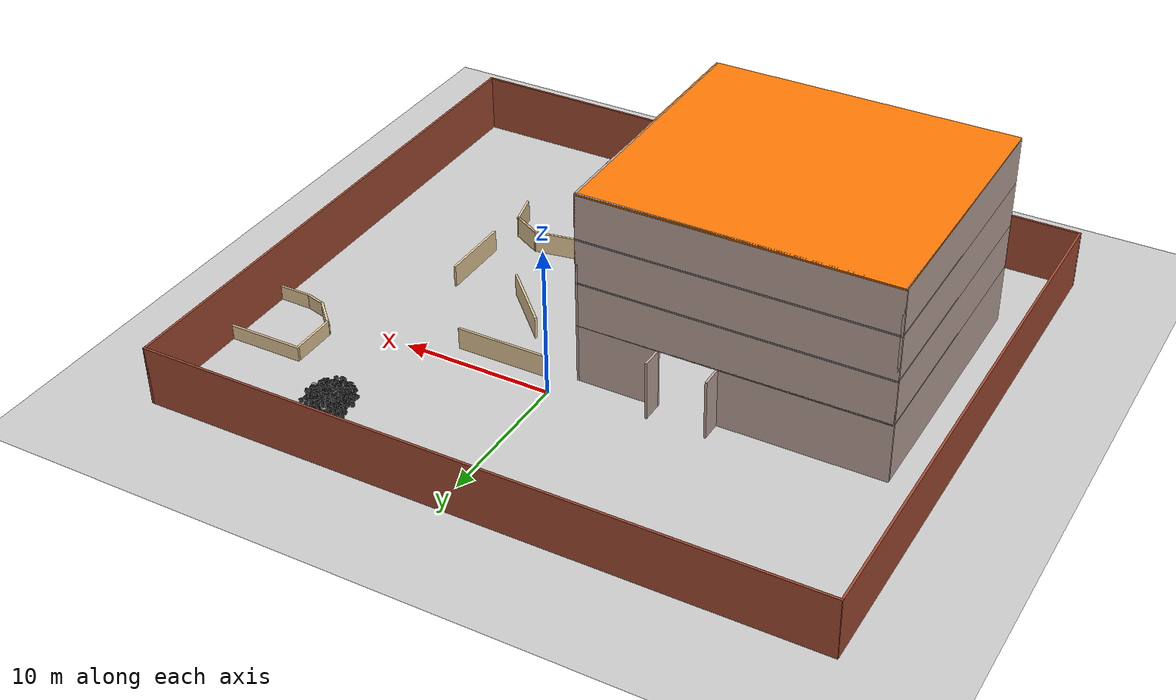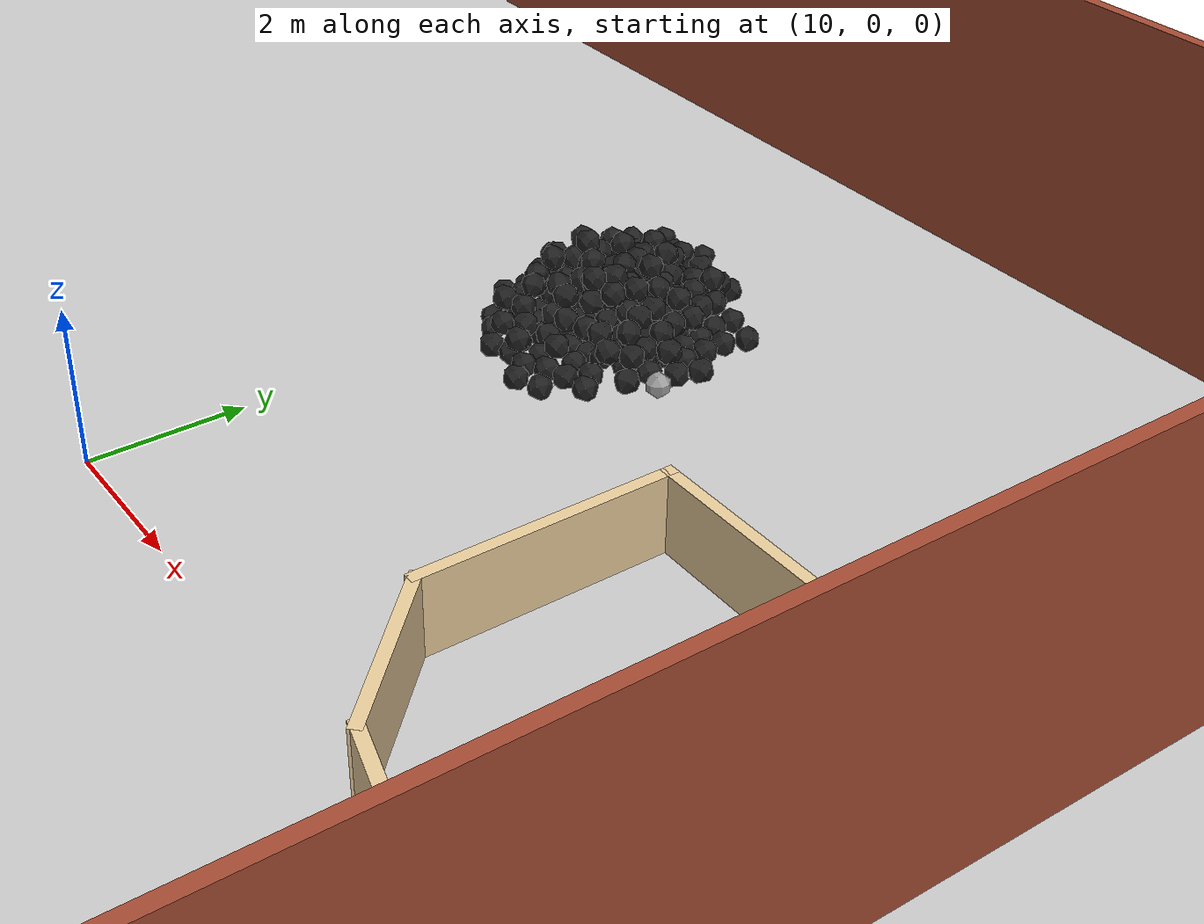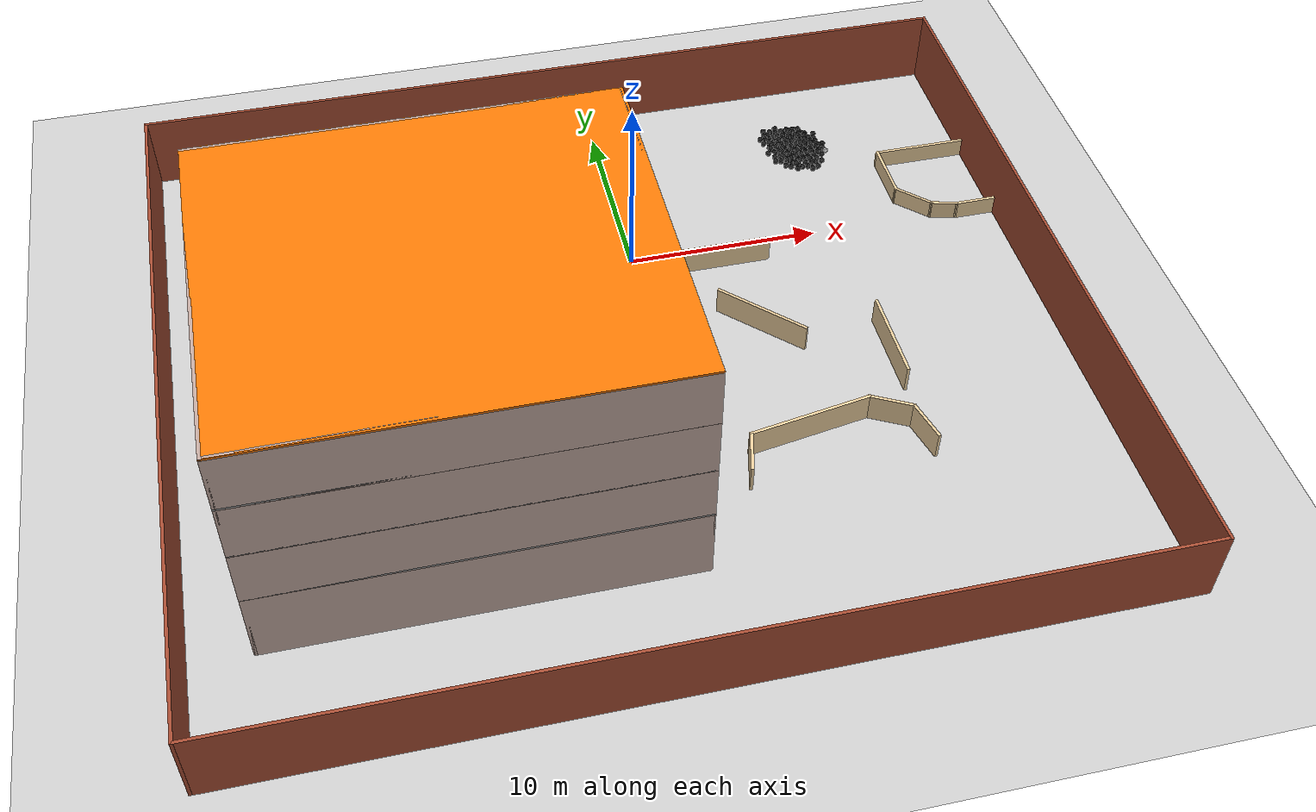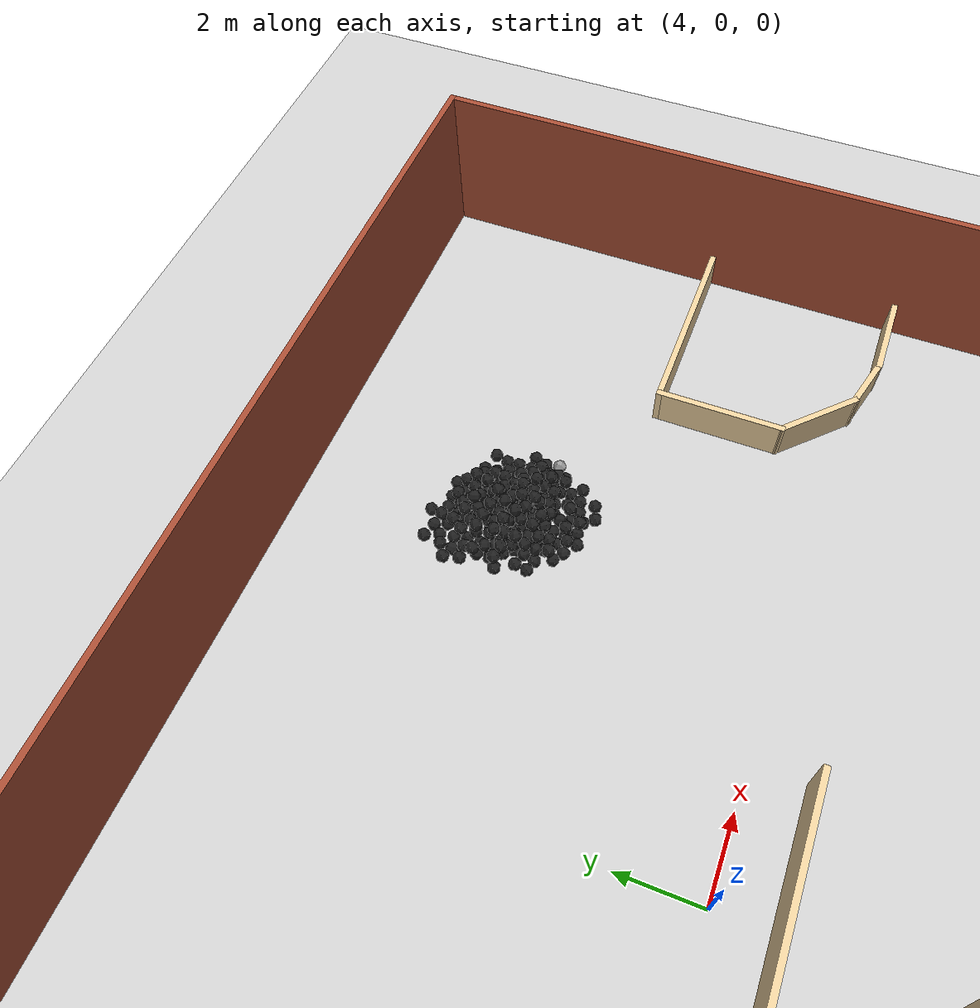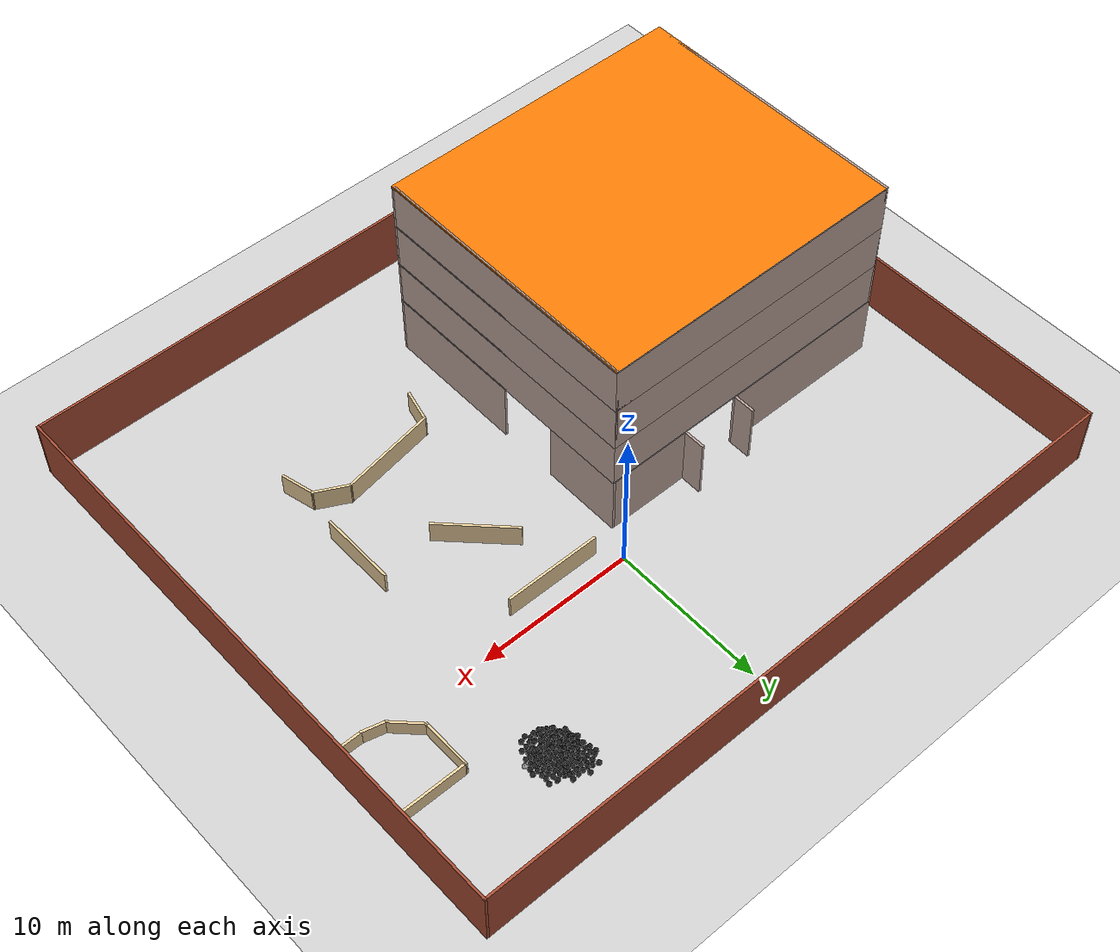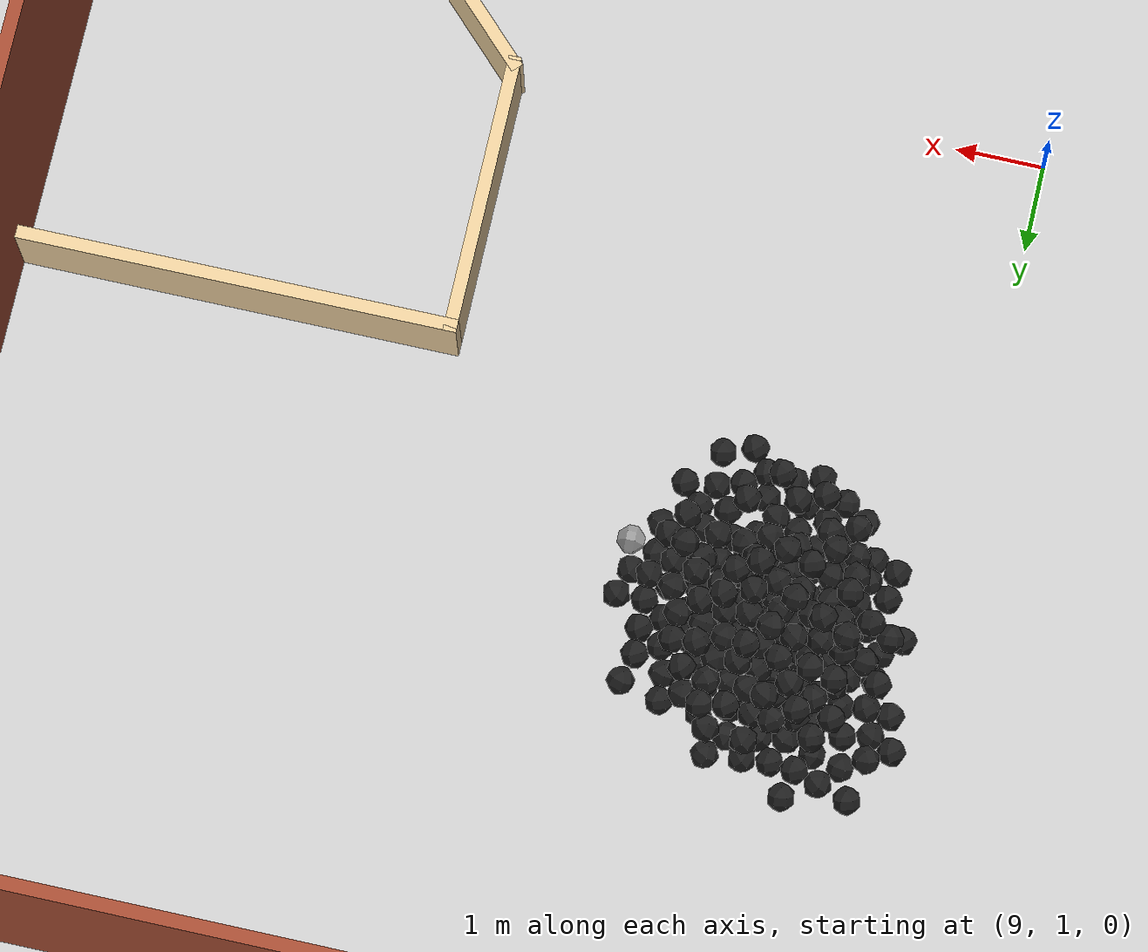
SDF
<sdf version="1.6">
 <world name="default">
  <light name="sun" type="directional">
   <pose>0 0 10 0 -0 0</pose>
   <diffuse>0.8 0.8 0.8 1</diffuse>
   <specular>0.2 0.2 0.2 1</specular>
   <attenuation>
    <range>1000</range>
    <constant>0.9</constant>
    <linear>0.01</linear>
    <quadratic>0.001</quadratic>
   </attenuation>
   <direction>-0.5 0.1 -0.9</direction>
  </light>
  <model name="ground_plane">
   <static>1</static>
   <link name="link">
    <collision name="collision">
     <geometry><plane><normal>0 0 1</normal><size>100 100</size></plane></geometry>
     <surface><friction><ode><mu>100</mu><mu2>50</mu2></ode></friction></surface>
    </collision>
    <visual name="visual">
     <cast_shadows>0</cast_shadows>
     <geometry><plane><normal>0 0 1</normal><size>100 100</size></plane></geometry>
     <material>
      <script><uri>file://media/materials/scripts/gazebo.material</uri><name>Gazebo/Grey</name></script>
     </material>
    </visual>
   </link>
  </model>
  <gravity>0 0 -9.8</gravity>
  <magnetic_field>6e-06 2.3e-05 -4.2e-05</magnetic_field>
  <atmosphere type="adiabatic"/>
  <physics name="default_physics" default="0" type="ode">
   <max_step_size>0.001</max_step_size>
   <real_time_factor>1</real_time_factor>
   <real_time_update_rate>1000</real_time_update_rate>
  </physics>
  <scene><ambient>0.4 0.4 0.4 1</ambient><background>0.7 0.7 0.7 1</background><shadows>1</shadows></scene>
  <audio><device>default</device></audio>
  <spherical_coordinates>
   <surface_model>EARTH_WGS84</surface_model>
   <latitude_deg>0</latitude_deg>
   <longitude_deg>0</longitude_deg>
   <elevation>0</elevation>
   <heading_deg>0</heading_deg>
  </spherical_coordinates>
  <model name="building2">
   <pose>-11 -10.325 0 0 -0 0</pose>
   <link name="Floor_0">
    <collision name="Floor_0_Collision">
     <geometry><box><size>20.15 18.15 0.1</size></box></geometry>
     <pose>0 0 0.05 0 -0 0</pose>
    </collision>
    <visual name="Floor_0_Visual">
     <pose>0 0 0.05 0 -0 0</pose>
     <geometry><box><size>20.15 18.15 0.1</size></box></geometry>
     <material>
      <script><uri>file://media/materials/scripts/gazebo.material</uri><name>Gazebo/Grey</name></script>
      <ambient>1 1 1 1</ambient>
     </material>
     <meta><layer>1</layer></meta>
    </visual>
    <pose>-0 -0.675 4 0 -0 0</pose>
   </link>
   <link name="Floor_2">
    <collision name="Floor_2_Collision">
     <geometry><box><size>20.15 18.15 0.1</size></box></geometry>
     <pose>0 0 0.05 0 -0 0</pose>
    </collision>
    <visual name="Floor_2_Visual">
     <pose>0 0 0.05 0 -0 0</pose>
     <geometry><box><size>20.15 18.15 0.1</size></box></geometry>
     <material>
      <script><uri>file://media/materials/scripts/gazebo.material</uri><name>Gazebo/Grey</name></script>
      <ambient>1 1 1 1</ambient>
     </material>
     <meta><layer>2</layer></meta>
    </visual>
    <pose>-0 -0.675 7 0 -0 0</pose>
   </link>
   <link name="Floor_3">
    <collision name="Floor_3_Collision">
     <geometry><box><size>20.15 18.15 0.1</size></box></geometry>
     <pose>0 0 0.05 0 -0 0</pose>
    </collision>
    <visual name="Floor_3_Visual">
     <pose>0 0 0.05 0 -0 0</pose>
     <geometry><box><size>20.15 18.15 0.1</size></box></geometry>
     <material>
      <script><uri>file://media/materials/scripts/gazebo.material</uri><name>Gazebo/Grey</name></script>
      <ambient>1 1 1 1</ambient>
     </material>
     <meta><layer>3</layer></meta>
    </visual>
    <pose>-0 -0.675 10 0 -0 0</pose>
   </link>
   <link name="Floor_8">
    <collision name="Floor_8_Collision">
     <geometry><box><size>20.15 18.15 0.1</size></box></geometry>
     <pose>0 0 0.05 0 -0 0</pose>
    </collision>
    <visual name="Floor_8_Visual">
     <pose>0 0 0.05 0 -0 0</pose>
     <geometry><box><size>20.15 18.15 0.1</size></box></geometry>
     <material>
      <script><uri>file://media/materials/scripts/gazebo.material</uri><name>Gazebo/Grey</name></script>
      <ambient>0.996078 0.47451 0.0196078 1</ambient>
     </material>
     <meta><layer>4</layer></meta>
    </visual>
    <pose>-0 -0.675 13 0 -0 0</pose>
   </link>
   <link name="Wall_11">
    <collision name="Wall_11_Collision">
     <geometry><box><size>1.5 0.15 4</size></box></geometry>
     <pose>0 0 2 0 -0 0</pose>
    </collision>
    <visual name="Wall_11_Visual">
     <pose>0 0 2 0 -0 0</pose>
     <geometry><box><size>1.5 0.15 4</size></box></geometry>
     <material>
      <script><uri>file://media/materials/scripts/gazebo.material</uri><name>Gazebo/Grey</name></script>
      <ambient>0.760784 0.662745 0.627451 1</ambient>
     </material>
     <meta><layer>0</layer></meta>
    </visual>
    <pose>0.8 9 0 0 -0 -1.5708</pose>
   </link>
   <link name="Wall_12">
    <collision name="Wall_12_Collision">
     <geometry><box><size>10.95 0.15 4</size></box></geometry>
     <pose>0 0 2 0 -0 0</pose>
    </collision>
    <visual name="Wall_12_Visual">
     <pose>0 0 2 0 -0 0</pose>
     <geometry><box><size>10.95 0.15 4</size></box></geometry>
     <material>
      <script><uri>file://media/materials/scripts/gazebo.material</uri><name>Gazebo/Grey</name></script>
      <ambient>0.760784 0.662745 0.627451 1</ambient>
     </material>
     <meta><layer>0</layer></meta>
    </visual>
    <pose>-4.6 8.325 0 0 -0 3.14159</pose>
   </link>
   <link name="Wall_14">
    <collision name="Wall_14_Collision">
     <geometry><box><size>18.15 0.15 4</size></box></geometry>
     <pose>0 0 2 0 -0 0</pose>
    </collision>
    <visual name="Wall_14_Visual">
     <pose>0 0 2 0 -0 0</pose>
     <geometry><box><size>18.15 0.15 4</size></box></geometry>
     <material>
      <script><uri>file://media/materials/scripts/gazebo.material</uri><name>Gazebo/Grey</name></script>
      <ambient>0.760784 0.662745 0.627451 1</ambient>
     </material>
     <meta><layer>0</layer></meta>
    </visual>
    <pose>-10 -0.675 0 0 -0 -1.5708</pose>
   </link>
   <link name="Wall_16">
    <collision name="Wall_16_Collision">
     <geometry><box><size>20.15 0.15 4</size></box></geometry>
     <pose>0 0 2 0 -0 0</pose>
    </collision>
    <visual name="Wall_16_Visual">
     <pose>0 0 2 0 -0 0</pose>
     <geometry><box><size>20.15 0.15 4</size></box></geometry>
     <material>
      <script><uri>file://media/materials/scripts/gazebo.material</uri><name>Gazebo/Grey</name></script>
      <ambient>0.760784 0.662745 0.627451 1</ambient>
     </material>
     <meta><layer>0</layer></meta>
    </visual>
    <pose>-0 -9.675 0 0 -0 0</pose>
   </link>
   <link name="Wall_24">
    <collision name="Wall_24_Collision">
     <geometry><box><size>18.15 0.15 3</size></box></geometry>
     <pose>0 0 1.5 0 -0 0</pose>
    </collision>
    <visual name="Wall_24_Visual">
     <pose>0 0 1.5 0 -0 0</pose>
     <geometry><box><size>18.15 0.15 3</size></box></geometry>
     <material>
      <script><uri>file://media/materials/scripts/gazebo.material</uri><name>Gazebo/Grey</name></script>
      <ambient>0.760784 0.662745 0.627451 1</ambient>
     </material>
     <meta><layer>1</layer></meta>
    </visual>
    <pose>-10 -0.675 4 0 -0 -1.5708</pose>
   </link>
   <link name="Wall_25">
    <collision name="Wall_25_Collision">
     <geometry><box><size>20.15 0.15 3</size></box></geometry>
     <pose>0 0 1.5 0 -0 0</pose>
    </collision>
    <visual name="Wall_25_Visual">
     <pose>0 0 1.5 0 -0 0</pose>
     <geometry><box><size>20.15 0.15 3</size></box></geometry>
     <material>
      <script><uri>file://media/materials/scripts/gazebo.material</uri><name>Gazebo/Grey</name></script>
      <ambient>0.760784 0.662745 0.627451 1</ambient>
     </material>
     <meta><layer>1</layer></meta>
    </visual>
    <pose>-0 -9.675 4 0 -0 0</pose>
   </link>
   <link name="Wall_31">
    <collision name="Wall_31_Collision">
     <geometry><box><size>20.15 0.15 3</size></box></geometry>
     <pose>0 0 1.5 0 -0 0</pose>
    </collision>
    <visual name="Wall_31_Visual">
     <pose>0 0 1.5 0 -0 0</pose>
     <geometry><box><size>20.15 0.15 3</size></box></geometry>
     <material>
      <script><uri>file://media/materials/scripts/gazebo.material</uri><name>Gazebo/Grey</name></script>
      <ambient>0.760784 0.662745 0.627451 1</ambient>
     </material>
     <meta><layer>1</layer></meta>
    </visual>
    <pose>-0 8.325 4 0 -0 0</pose>
   </link>
   <link name="Wall_33">
    <collision name="Wall_33_Collision">
     <geometry><box><size>18 0.15 3</size></box></geometry>
     <pose>0 0 1.5 0 -0 0</pose>
    </collision>
    <visual name="Wall_33_Visual">
     <pose>0 0 1.5 0 -0 0</pose>
     <geometry><box><size>18 0.15 3</size></box></geometry>
     <material>
      <script><uri>file://media/materials/scripts/gazebo.material</uri><name>Gazebo/Grey</name></script>
      <ambient>0.760784 0.662745 0.627451 1</ambient>
     </material>
     <meta><layer>1</layer></meta>
    </visual>
    <pose>10 -0.6 4 0 -0 -1.5708</pose>
   </link>
   <link name="Wall_4">
    <collision name="Wall_4_Collision">
     <geometry><box><size>5.15 0.15 4</size></box></geometry>
     <pose>0 0 2 0 -0 0</pose>
    </collision>
    <visual name="Wall_4_Visual">
     <pose>0 0 2 0 -0 0</pose>
     <geometry><box><size>5.15 0.15 4</size></box></geometry>
     <material>
      <script><uri>file://media/materials/scripts/gazebo.material</uri><name>Gazebo/Grey</name></script>
      <ambient>0.760784 0.662745 0.627451 1</ambient>
     </material>
     <meta><layer>0</layer></meta>
    </visual>
    <pose>10 5.825 0 0 -0 -1.5708</pose>
   </link>
   <link name="Wall_42">
    <collision name="Wall_42_Collision">
     <geometry><box><size>18.15 0.15 3</size></box></geometry>
     <pose>0 0 1.5 0 -0 0</pose>
    </collision>
    <visual name="Wall_42_Visual">
     <pose>0 0 1.5 0 -0 0</pose>
     <geometry><box><size>18.15 0.15 3</size></box></geometry>
     <material>
      <script><uri>file://media/materials/scripts/gazebo.material</uri><name>Gazebo/Grey</name></script>
      <ambient>0.760784 0.662745 0.627451 1</ambient>
     </material>
     <meta><layer>2</layer></meta>
    </visual>
    <pose>-10 -0.675 7 0 -0 -1.5708</pose>
   </link>
   <link name="Wall_43">
    <collision name="Wall_43_Collision">
     <geometry><box><size>20.15 0.15 3</size></box></geometry>
     <pose>0 0 1.5 0 -0 0</pose>
    </collision>
    <visual name="Wall_43_Visual">
     <pose>0 0 1.5 0 -0 0</pose>
     <geometry><box><size>20.15 0.15 3</size></box></geometry>
     <material>
      <script><uri>file://media/materials/scripts/gazebo.material</uri><name>Gazebo/Grey</name></script>
      <ambient>0.760784 0.662745 0.627451 1</ambient>
     </material>
     <meta><layer>2</layer></meta>
    </visual>
    <pose>-0 -9.675 7 0 -0 0</pose>
   </link>
   <link name="Wall_44">
    <collision name="Wall_44_Collision">
     <geometry><box><size>20.15 0.15 3</size></box></geometry>
     <pose>0 0 1.5 0 -0 0</pose>
    </collision>
    <visual name="Wall_44_Visual">
     <pose>0 0 1.5 0 -0 0</pose>
     <geometry><box><size>20.15 0.15 3</size></box></geometry>
     <material>
      <script><uri>file://media/materials/scripts/gazebo.material</uri><name>Gazebo/Grey</name></script>
      <ambient>0.760784 0.662745 0.627451 1</ambient>
     </material>
     <meta><layer>2</layer></meta>
    </visual>
    <pose>-0 8.325 7 0 -0 0</pose>
   </link>
   <link name="Wall_45">
    <collision name="Wall_45_Collision">
     <geometry><box><size>18 0.15 3</size></box></geometry>
     <pose>0 0 1.5 0 -0 0</pose>
    </collision>
    <visual name="Wall_45_Visual">
     <pose>0 0 1.5 0 -0 0</pose>
     <geometry><box><size>18 0.15 3</size></box></geometry>
     <material>
      <script><uri>file://media/materials/scripts/gazebo.material</uri><name>Gazebo/Grey</name></script>
      <ambient>0.760784 0.662745 0.627451 1</ambient>
     </material>
     <meta><layer>2</layer></meta>
    </visual>
    <pose>10 -0.6 7 0 -0 -1.5708</pose>
   </link>
   <link name="Wall_46">
    <collision name="Wall_46_Collision">
     <geometry><box><size>18.15 0.15 3</size></box></geometry>
     <pose>0 0 1.5 0 -0 0</pose>
    </collision>
    <visual name="Wall_46_Visual">
     <pose>0 0 1.5 0 -0 0</pose>
     <geometry><box><size>18.15 0.15 3</size></box></geometry>
     <material>
      <script><uri>file://media/materials/scripts/gazebo.material</uri><name>Gazebo/Grey</name></script>
      <ambient>0.760784 0.662745 0.627451 1</ambient>
     </material>
     <meta><layer>3</layer></meta>
    </visual>
    <pose>-10 -0.675 10 0 -0 -1.5708</pose>
   </link>
   <link name="Wall_47">
    <collision name="Wall_47_Collision">
     <geometry><box><size>20.15 0.15 3</size></box></geometry>
     <pose>0 0 1.5 0 -0 0</pose>
    </collision>
    <visual name="Wall_47_Visual">
     <pose>0 0 1.5 0 -0 0</pose>
     <geometry><box><size>20.15 0.15 3</size></box></geometry>
     <material>
      <script><uri>file://media/materials/scripts/gazebo.material</uri><name>Gazebo/Grey</name></script>
      <ambient>0.760784 0.662745 0.627451 1</ambient>
     </material>
     <meta><layer>3</layer></meta>
    </visual>
    <pose>-0 -9.675 10 0 -0 0</pose>
   </link>
   <link name="Wall_48">
    <collision name="Wall_48_Collision">
     <geometry><box><size>20.15 0.15 3</size></box></geometry>
     <pose>0 0 1.5 0 -0 0</pose>
    </collision>
    <visual name="Wall_48_Visual">
     <pose>0 0 1.5 0 -0 0</pose>
     <geometry><box><size>20.15 0.15 3</size></box></geometry>
     <material>
      <script><uri>file://media/materials/scripts/gazebo.material</uri><name>Gazebo/Grey</name></script>
      <ambient>0.760784 0.662745 0.627451 1</ambient>
     </material>
     <meta><layer>3</layer></meta>
    </visual>
    <pose>-0 8.325 10 0 -0 0</pose>
   </link>
   <link name="Wall_49">
    <collision name="Wall_49_Collision">
     <geometry><box><size>18 0.15 3</size></box></geometry>
     <pose>0 0 1.5 0 -0 0</pose>
    </collision>
    <visual name="Wall_49_Visual">
     <pose>0 0 1.5 0 -0 0</pose>
     <geometry><box><size>18 0.15 3</size></box></geometry>
     <material>
      <script><uri>file://media/materials/scripts/gazebo.material</uri><name>Gazebo/Grey</name></script>
      <ambient>0.760784 0.662745 0.627451 1</ambient>
     </material>
     <meta><layer>3</layer></meta>
    </visual>
    <pose>10 -0.6 10 0 -0 -1.5708</pose>
   </link>
   <link name="Wall_6">
    <collision name="Wall_6_Collision">
     <geometry><box><size>9.15 0.15 4</size></box></geometry>
     <pose>0 0 2 0 -0 0</pose>
    </collision>
    <visual name="Wall_6_Visual">
     <pose>0 0 2 0 -0 0</pose>
     <geometry><box><size>9.15 0.15 4</size></box></geometry>
     <material>
      <script><uri>file://media/materials/scripts/gazebo.material</uri><name>Gazebo/Grey</name></script>
      <ambient>0.760784 0.662745 0.627451 1</ambient>
     </material>
     <meta><layer>0</layer></meta>
    </visual>
    <pose>10 -5.175 0 0 -0 -1.5708</pose>
   </link>
   <link name="Wall_76">
    <collision name="Wall_76_Collision">
     <geometry><box><size>18.15 0.15 0.1</size></box></geometry>
     <pose>0 0 0.05 0 -0 0</pose>
    </collision>
    <visual name="Wall_76_Visual">
     <pose>0 0 0.05 0 -0 0</pose>
     <geometry><box><size>18.15 0.15 0.1</size></box></geometry>
     <material>
      <script><uri>file://media/materials/scripts/gazebo.material</uri><name>Gazebo/Grey</name></script>
      <ambient>0.760784 0.662745 0.627451 1</ambient>
     </material>
     <meta><layer>4</layer></meta>
    </visual>
    <pose>-10 -0.675 13 0 -0 -1.5708</pose>
   </link>
   <link name="Wall_77">
    <collision name="Wall_77_Collision">
     <geometry><box><size>20.15 0.15 0.1</size></box></geometry>
     <pose>0 0 0.05 0 -0 0</pose>
    </collision>
    <visual name="Wall_77_Visual">
     <pose>0 0 0.05 0 -0 0</pose>
     <geometry><box><size>20.15 0.15 0.1</size></box></geometry>
     <material>
      <script><uri>file://media/materials/scripts/gazebo.material</uri><name>Gazebo/Grey</name></script>
      <ambient>0.760784 0.662745 0.627451 1</ambient>
     </material>
     <meta><layer>4</layer></meta>
    </visual>
    <pose>-0 -9.675 13 0 -0 0</pose>
   </link>
   <link name="Wall_78">
    <collision name="Wall_78_Collision">
     <geometry><box><size>20.15 0.15 0.1</size></box></geometry>
     <pose>0 0 0.05 0 -0 0</pose>
    </collision>
    <visual name="Wall_78_Visual">
     <pose>0 0 0.05 0 -0 0</pose>
     <geometry><box><size>20.15 0.15 0.1</size></box></geometry>
     <material>
      <script><uri>file://media/materials/scripts/gazebo.material</uri><name>Gazebo/Grey</name></script>
      <ambient>0.760784 0.662745 0.627451 1</ambient>
     </material>
     <meta><layer>4</layer></meta>
    </visual>
    <pose>-0 8.325 13 0 -0 0</pose>
   </link>
   <link name="Wall_79">
    <collision name="Wall_79_Collision">
     <geometry><box><size>18 0.15 0.1</size></box></geometry>
     <pose>0 0 0.05 0 -0 0</pose>
    </collision>
    <visual name="Wall_79_Visual">
     <pose>0 0 0.05 0 -0 0</pose>
     <geometry><box><size>18 0.15 0.1</size></box></geometry>
     <material>
      <script><uri>file://media/materials/scripts/gazebo.material</uri><name>Gazebo/Grey</name></script>
      <ambient>0.760784 0.662745 0.627451 1</ambient>
     </material>
     <meta><layer>4</layer></meta>
    </visual>
    <pose>10 -0.6 13 0 -0 -1.5708</pose>
   </link>
   <link name="Wall_8">
    <collision name="Wall_8_Collision">
     <geometry><box><size>5.5 0.15 4</size></box></geometry>
     <pose>0 0 2 0 -0 0</pose>
    </collision>
    <visual name="Wall_8_Visual">
     <pose>0 0 2 0 -0 0</pose>
     <geometry><box><size>5.5 0.15 4</size></box></geometry>
     <material>
      <script><uri>file://media/materials/scripts/gazebo.material</uri><name>Gazebo/Grey</name></script>
      <ambient>0.760784 0.662745 0.627451 1</ambient>
     </material>
     <meta><layer>0</layer></meta>
    </visual>
    <pose>7.325 8.325 0 0 -0 3.14159</pose>
   </link>
   <link name="Wall_9">
    <collision name="Wall_9_Collision">
     <geometry><box><size>1.5 0.15 4</size></box></geometry>
     <pose>0 0 2 0 -0 0</pose>
    </collision>
    <visual name="Wall_9_Visual">
     <pose>0 0 2 0 -0 0</pose>
     <geometry><box><size>1.5 0.15 4</size></box></geometry>
     <material>
      <script><uri>file://media/materials/scripts/gazebo.material</uri><name>Gazebo/Grey</name></script>
      <ambient>0.760784 0.662745 0.627451 1</ambient>
     </material>
     <meta><layer>0</layer></meta>
    </visual>
    <pose>4.65 9 0 0 -0 1.5708</pose>
   </link>
   <static>1</static>
  </model>
  <model name="wall11">
   <pose>-2 -7 0 0 -0 0</pose>
   <link name="Wall_0">
    <collision name="Wall_0_Collision">
     <geometry><box><size>44.15 0.15 4</size></box></geometry>
     <pose>0 0 2 0 -0 0</pose>
    </collision>
    <visual name="Wall_0_Visual">
     <pose>0 0 2 0 -0 0</pose>
     <geometry><box><size>44.15 0.15 4</size></box></geometry>
     <material>
      <script><uri>file://media/materials/scripts/gazebo.material</uri><name>Gazebo/Bricks</name></script>
      <ambient>1 1 1 1</ambient>
     </material>
     <meta><layer>0</layer></meta>
    </visual>
    <pose>0 19 0 0 -0 0</pose>
   </link>
   <link name="Wall_2">
    <collision name="Wall_2_Collision">
     <geometry><box><size>38.15 0.15 4</size></box></geometry>
     <pose>0 0 2 0 -0 0</pose>
    </collision>
    <visual name="Wall_2_Visual">
     <pose>0 0 2 0 -0 0</pose>
     <geometry><box><size>38.15 0.15 4</size></box></geometry>
     <material>
      <script><uri>file://media/materials/scripts/gazebo.material</uri><name>Gazebo/Bricks</name></script>
      <ambient>1 1 1 1</ambient>
     </material>
     <meta><layer>0</layer></meta>
    </visual>
    <pose>22 0 0 0 -0 -1.5708</pose>
   </link>
   <link name="Wall_4">
    <collision name="Wall_4_Collision">
     <geometry><box><size>44.15 0.15 4</size></box></geometry>
     <pose>0 0 2 0 -0 0</pose>
    </collision>
    <visual name="Wall_4_Visual">
     <pose>0 0 2 0 -0 0</pose>
     <geometry><box><size>44.15 0.15 4</size></box></geometry>
     <material>
      <script><uri>file://media/materials/scripts/gazebo.material</uri><name>Gazebo/Bricks</name></script>
      <ambient>1 1 1 1</ambient>
     </material>
     <meta><layer>0</layer></meta>
    </visual>
    <pose>0 -19 0 0 -0 3.14159</pose>
   </link>
   <link name="Wall_6">
    <collision name="Wall_6_Collision">
     <geometry><box><size>38.15 0.15 4</size></box></geometry>
     <pose>0 0 2 0 -0 0</pose>
    </collision>
    <visual name="Wall_6_Visual">
     <pose>0 0 2 0 -0 0</pose>
     <geometry><box><size>38.15 0.15 4</size></box></geometry>
     <material>
      <script><uri>file://media/materials/scripts/gazebo.material</uri><name>Gazebo/Bricks</name></script>
      <ambient>1 1 1 1</ambient>
     </material>
     <meta><layer>0</layer></meta>
    </visual>
    <pose>-22 0 0 0 -0 1.5708</pose>
   </link>
   <static>1</static>
  </model>
  <model name="haoduomiantiaa_0">
   <link name="link_0">
    <inertial>
     <mass>0.2</mass>
     <inertia>
      <ixx>0.166667</ixx>
      <ixy>0</ixy>
      <ixz>0</ixz>
      <iyy>0.166667</iyy>
      <iyz>0</iyz>
      <izz>0.166667</izz>
     </inertia>
    </inertial>
    <visual name="visual">
     <geometry>
      <mesh>
       <uri>/home/oliver/catkin_ws/src/pudong_gazebo/world/stl/haoduomianti.stl</uri>
       <scale>1 1 1</scale>
      </mesh>
     </geometry>
     <material>
      <lighting>1</lighting>
      <script><uri>file://media/materials/scripts/gazebo.material</uri><name>Gazebo/Black</name></script>
      <shader type="pixel"><normal_map>__default__</normal_map></shader>
      <ambient>0.3 0.3 0.3 1</ambient>
      <diffuse>0.7 0.7 0.7 1</diffuse>
      <specular>0.01 0.01 0.01 1</specular>
      <emissive>0 0 0 1</emissive>
     </material>
    </visual>
    <collision name="collision">
     <geometry>
      <mesh>
       <uri>/home/oliver/catkin_ws/src/pudong_gazebo/world/stl/haoduomianti.stl</uri>
       <scale>1 1 1</scale>
      </mesh>
     </geometry>
     <surface>
      <friction>
       <ode><mu>1</mu><mu2>1</mu2><fdir1>0 0 0</fdir1><slip1>0</slip1><slip2>0</slip2></ode>
       <torsional>
        <coefficient>1</coefficient>
        <patch_radius>0</patch_radius>
        <surface_radius>0</surface_radius>
        <use_patch_radius>1</use_patch_radius>
        <ode><slip>0</slip></ode>
       </torsional>
      </friction>
      <bounce><restitution_coefficient>0</restitution_coefficient><threshold>1e+06</threshold></bounce>
      <contact>
       <collide_without_contact>0</collide_without_contact>
       <collide_without_contact_bitmask>1</collide_without_contact_bitmask>
       <collide_bitmask>1</collide_bitmask>
       <ode>
        <soft_cfm>0</soft_cfm>
        <soft_erp>0.2</soft_erp>
        <kp>1e+13</kp>
        <kd>1</kd>
        <max_vel>0.01</max_vel>
        <min_depth>0</min_depth>
       </ode>
       <bullet>
        <split_impulse>1</split_impulse>
        <split_impulse_penetration_threshold>-0.01</split_impulse_penetration_threshold>
        <soft_cfm>0</soft_cfm>
        <soft_erp>0.2</soft_erp>
        <kp>1e+13</kp>
        <kd>1</kd>
       </bullet>
      </contact>
     </surface>
    </collision>
   </link>
   <static>0</static>
   <pose>10.9618 7.08552 -0.115307 0.783602 -0.61526 -1.24045</pose>
  </model>
  <model name="haoduomiantiaa_1">
   <link name="link_0">
    <inertial>
     <mass>0.2</mass>
     <inertia>
      <ixx>0.166667</ixx>
      <ixy>0</ixy>
      <ixz>0</ixz>
      <iyy>0.166667</iyy>
      <iyz>0</iyz>
      <izz>0.166667</izz>
     </inertia>
    </inertial>
    <visual name="visual">
     <geometry>
      <mesh>
       <uri>/home/oliver/catkin_ws/src/pudong_gazebo/world/stl/haoduomianti.stl</uri>
       <scale>1 1 1</scale>
      </mesh>
     </geometry>
     <material>
      <lighting>1</lighting>
      <script><uri>file://media/materials/scripts/gazebo.material</uri><name>Gazebo/Black</name></script>
      <shader type="pixel"><normal_map>__default__</normal_map></shader>
      <ambient>0.3 0.3 0.3 1</ambient>
      <diffuse>0.7 0.7 0.7 1</diffuse>
      <specular>0.01 0.01 0.01 1</specular>
      <emissive>0 0 0 1</emissive>
     </material>
    </visual>
    <collision name="collision">
     <geometry>
      <mesh>
       <uri>/home/oliver/catkin_ws/src/pudong_gazebo/world/stl/haoduomianti.stl</uri>
       <scale>1 1 1</scale>
      </mesh>
     </geometry>
     <surface>
      <friction>
       <ode><mu>1</mu><mu2>1</mu2><fdir1>0 0 0</fdir1><slip1>0</slip1><slip2>0</slip2></ode>
       <torsional>
        <coefficient>1</coefficient>
        <patch_radius>0</patch_radius>
        <surface_radius>0</surface_radius>
        <use_patch_radius>1</use_patch_radius>
        <ode><slip>0</slip></ode>
       </torsional>
      </friction>
      <bounce><restitution_coefficient>0</restitution_coefficient><threshold>1e+06</threshold></bounce>
      <contact>
       <collide_without_contact>0</collide_without_contact>
       <collide_without_contact_bitmask>1</collide_without_contact_bitmask>
       <collide_bitmask>1</collide_bitmask>
       <ode>
        <soft_cfm>0</soft_cfm>
        <soft_erp>0.2</soft_erp>
        <kp>1e+13</kp>
        <kd>1</kd>
        <max_vel>0.01</max_vel>
        <min_depth>0</min_depth>
       </ode>
       <bullet>
        <split_impulse>1</split_impulse>
        <split_impulse_penetration_threshold>-0.01</split_impulse_penetration_threshold>
        <soft_cfm>0</soft_cfm>
        <soft_erp>0.2</soft_erp>
        <kp>1e+13</kp>
        <kd>1</kd>
       </bullet>
      </contact>
     </surface>
    </collision>
   </link>
   <static>0</static>
   <pose>10.6958 6.67927 -0.115575 0.783813 -0.615096 0.41148</pose>
  </model>
  <model name="haoduomiantiaa_2">
   <link name="link_0">
    <inertial>
     <mass>0.2</mass>
     <inertia>
      <ixx>0.166667</ixx>
      <ixy>0</ixy>
      <ixz>0</ixz>
      <iyy>0.166667</iyy>
      <iyz>0</iyz>
      <izz>0.166667</izz>
     </inertia>
    </inertial>
    <visual name="visual">
     <geometry>
      <mesh>
       <uri>/home/oliver/catkin_ws/src/pudong_gazebo/world/stl/haoduomianti.stl</uri>
       <scale>1 1 1</scale>
      </mesh>
     </geometry>
     <material>
      <lighting>1</lighting>
      <script><uri>file://media/materials/scripts/gazebo.material</uri><name>Gazebo/Black</name></script>
      <shader type="pixel"><normal_map>__default__</normal_map></shader>
      <ambient>0.3 0.3 0.3 1</ambient>
      <diffuse>0.7 0.7 0.7 1</diffuse>
      <specular>0.01 0.01 0.01 1</specular>
      <emissive>0 0 0 1</emissive>
     </material>
    </visual>
    <collision name="collision">
     <geometry>
      <mesh>
       <uri>/home/oliver/catkin_ws/src/pudong_gazebo/world/stl/haoduomianti.stl</uri>
       <scale>1 1 1</scale>
      </mesh>
     </geometry>
     <surface>
      <friction>
       <ode><mu>1</mu><mu2>1</mu2><fdir1>0 0 0</fdir1><slip1>0</slip1><slip2>0</slip2></ode>
       <torsional>
        <coefficient>1</coefficient>
        <patch_radius>0</patch_radius>
        <surface_radius>0</surface_radius>
        <use_patch_radius>1</use_patch_radius>
        <ode><slip>0</slip></ode>
       </torsional>
      </friction>
      <bounce><restitution_coefficient>0</restitution_coefficient><threshold>1e+06</threshold></bounce>
      <contact>
       <collide_without_contact>0</collide_without_contact>
       <collide_without_contact_bitmask>1</collide_without_contact_bitmask>
       <collide_bitmask>1</collide_bitmask>
       <ode>
        <soft_cfm>0</soft_cfm>
        <soft_erp>0.2</soft_erp>
        <kp>1e+13</kp>
        <kd>1</kd>
        <max_vel>0.01</max_vel>
        <min_depth>0</min_depth>
       </ode>
       <bullet>
        <split_impulse>1</split_impulse>
        <split_impulse_penetration_threshold>-0.01</split_impulse_penetration_threshold>
        <soft_cfm>0</soft_cfm>
        <soft_erp>0.2</soft_erp>
        <kp>1e+13</kp>
        <kd>1</kd>
       </bullet>
      </contact>
     </surface>
    </collision>
   </link>
   <static>0</static>
   <pose>11.348 7.28594 -0.07324 1.57335 -0.785956 0.646632</pose>
  </model>
  <model name="haoduomiantiaa_3">
   <link name="link_0">
    <inertial>
     <mass>0.2</mass>
     <inertia>
      <ixx>0.166667</ixx>
      <ixy>0</ixy>
      <ixz>0</ixz>
      <iyy>0.166667</iyy>
      <iyz>0</iyz>
      <izz>0.166667</izz>
     </inertia>
    </inertial>
    <visual name="visual">
     <geometry>
      <mesh>
       <uri>/home/oliver/catkin_ws/src/pudong_gazebo/world/stl/haoduomianti.stl</uri>
       <scale>1 1 1</scale>
      </mesh>
     </geometry>
     <material>
      <lighting>1</lighting>
      <script><uri>file://media/materials/scripts/gazebo.material</uri><name>Gazebo/Black</name></script>
      <shader type="pixel"><normal_map>__default__</normal_map></shader>
      <ambient>0.3 0.3 0.3 1</ambient>
      <diffuse>0.7 0.7 0.7 1</diffuse>
      <specular>0.01 0.01 0.01 1</specular>
      <emissive>0 0 0 1</emissive>
     </material>
    </visual>
    <collision name="collision">
     <geometry>
      <mesh>
       <uri>/home/oliver/catkin_ws/src/pudong_gazebo/world/stl/haoduomianti.stl</uri>
       <scale>1 1 1</scale>
      </mesh>
     </geometry>
     <surface>
      <friction>
       <ode><mu>1</mu><mu2>1</mu2><fdir1>0 0 0</fdir1><slip1>0</slip1><slip2>0</slip2></ode>
       <torsional>
        <coefficient>1</coefficient>
        <patch_radius>0</patch_radius>
        <surface_radius>0</surface_radius>
        <use_patch_radius>1</use_patch_radius>
        <ode><slip>0</slip></ode>
       </torsional>
      </friction>
      <bounce><restitution_coefficient>0</restitution_coefficient><threshold>1e+06</threshold></bounce>
      <contact>
       <collide_without_contact>0</collide_without_contact>
       <collide_without_contact_bitmask>1</collide_without_contact_bitmask>
       <collide_bitmask>1</collide_bitmask>
       <ode>
        <soft_cfm>0</soft_cfm>
        <soft_erp>0.2</soft_erp>
        <kp>1e+13</kp>
        <kd>1</kd>
        <max_vel>0.01</max_vel>
        <min_depth>0</min_depth>
       </ode>
       <bullet>
        <split_impulse>1</split_impulse>
        <split_impulse_penetration_threshold>-0.01</split_impulse_penetration_threshold>
        <soft_cfm>0</soft_cfm>
        <soft_erp>0.2</soft_erp>
        <kp>1e+13</kp>
        <kd>1</kd>
       </bullet>
      </contact>
     </surface>
    </collision>
   </link>
   <static>0</static>
   <pose>11.7238 6.55856 -0.072691 0.00034 -0.785225 -2.24933</pose>
  </model>
  <model name="haoduomiantiaa_4">
   <link name="link_0">
    <inertial>
     <mass>0.2</mass>
     <inertia>
      <ixx>0.166667</ixx>
      <ixy>0</ixy>
      <ixz>0</ixz>
      <iyy>0.166667</iyy>
      <iyz>0</iyz>
      <izz>0.166667</izz>
     </inertia>
    </inertial>
    <visual name="visual">
     <geometry>
      <mesh>
       <uri>/home/oliver/catkin_ws/src/pudong_gazebo/world/stl/haoduomianti.stl</uri>
       <scale>1 1 1</scale>
      </mesh>
     </geometry>
     <material>
      <lighting>1</lighting>
      <script><uri>file://media/materials/scripts/gazebo.material</uri><name>Gazebo/Black</name></script>
      <shader type="pixel"><normal_map>__default__</normal_map></shader>
      <ambient>0.3 0.3 0.3 1</ambient>
      <diffuse>0.7 0.7 0.7 1</diffuse>
      <specular>0.01 0.01 0.01 1</specular>
      <emissive>0 0 0 1</emissive>
     </material>
    </visual>
    <collision name="collision">
     <geometry>
      <mesh>
       <uri>/home/oliver/catkin_ws/src/pudong_gazebo/world/stl/haoduomianti.stl</uri>
       <scale>1 1 1</scale>
      </mesh>
     </geometry>
     <surface>
      <friction>
       <ode><mu>1</mu><mu2>1</mu2><fdir1>0 0 0</fdir1><slip1>0</slip1><slip2>0</slip2></ode>
       <torsional>
        <coefficient>1</coefficient>
        <patch_radius>0</patch_radius>
        <surface_radius>0</surface_radius>
        <use_patch_radius>1</use_patch_radius>
        <ode><slip>0</slip></ode>
       </torsional>
      </friction>
      <bounce><restitution_coefficient>0</restitution_coefficient><threshold>1e+06</threshold></bounce>
      <contact>
       <collide_without_contact>0</collide_without_contact>
       <collide_without_contact_bitmask>1</collide_without_contact_bitmask>
       <collide_bitmask>1</collide_bitmask>
       <ode>
        <soft_cfm>0</soft_cfm>
        <soft_erp>0.2</soft_erp>
        <kp>1e+13</kp>
        <kd>1</kd>
        <max_vel>0.01</max_vel>
        <min_depth>0</min_depth>
       </ode>
       <bullet>
        <split_impulse>1</split_impulse>
        <split_impulse_penetration_threshold>-0.01</split_impulse_penetration_threshold>
        <soft_cfm>0</soft_cfm>
        <soft_erp>0.2</soft_erp>
        <kp>1e+13</kp>
        <kd>1</kd>
       </bullet>
      </contact>
     </surface>
    </collision>
   </link>
   <static>0</static>
   <pose>11.7408 7.17614 -0.115424 0.785214 -0.614577 0.474893</pose>
  </model>
  <model name="haoduomiantiaa_5">
   <link name="link_0">
    <inertial>
     <mass>0.2</mass>
     <inertia>
      <ixx>0.166667</ixx>
      <ixy>0</ixy>
      <ixz>0</ixz>
      <iyy>0.166667</iyy>
      <iyz>0</iyz>
      <izz>0.166667</izz>
     </inertia>
    </inertial>
    <visual name="visual">
     <geometry>
      <mesh>
       <uri>/home/oliver/catkin_ws/src/pudong_gazebo/world/stl/haoduomianti.stl</uri>
       <scale>1 1 1</scale>
      </mesh>
     </geometry>
     <material>
      <lighting>1</lighting>
      <script><uri>file://media/materials/scripts/gazebo.material</uri><name>Gazebo/Black</name></script>
      <shader type="pixel"><normal_map>__default__</normal_map></shader>
      <ambient>0.3 0.3 0.3 1</ambient>
      <diffuse>0.7 0.7 0.7 1</diffuse>
      <specular>0.01 0.01 0.01 1</specular>
      <emissive>0 0 0 1</emissive>
     </material>
    </visual>
    <collision name="collision">
     <geometry>
      <mesh>
       <uri>/home/oliver/catkin_ws/src/pudong_gazebo/world/stl/haoduomianti.stl</uri>
       <scale>1 1 1</scale>
      </mesh>
     </geometry>
     <surface>
      <friction>
       <ode><mu>1</mu><mu2>1</mu2><fdir1>0 0 0</fdir1><slip1>0</slip1><slip2>0</slip2></ode>
       <torsional>
        <coefficient>1</coefficient>
        <patch_radius>0</patch_radius>
        <surface_radius>0</surface_radius>
        <use_patch_radius>1</use_patch_radius>
        <ode><slip>0</slip></ode>
       </torsional>
      </friction>
      <bounce><restitution_coefficient>0</restitution_coefficient><threshold>1e+06</threshold></bounce>
      <contact>
       <collide_without_contact>0</collide_without_contact>
       <collide_without_contact_bitmask>1</collide_without_contact_bitmask>
       <collide_bitmask>1</collide_bitmask>
       <ode>
        <soft_cfm>0</soft_cfm>
        <soft_erp>0.2</soft_erp>
        <kp>1e+13</kp>
        <kd>1</kd>
        <max_vel>0.01</max_vel>
        <min_depth>0</min_depth>
       </ode>
       <bullet>
        <split_impulse>1</split_impulse>
        <split_impulse_penetration_threshold>-0.01</split_impulse_penetration_threshold>
        <soft_cfm>0</soft_cfm>
        <soft_erp>0.2</soft_erp>
        <kp>1e+13</kp>
        <kd>1</kd>
       </bullet>
      </contact>
     </surface>
    </collision>
   </link>
   <static>0</static>
   <pose>11.6442 6.91591 -0.072486 0.025367 -0.785197 -1.84865</pose>
  </model>
  <model name="haoduomiantiaa_6">
   <link name="link_0">
    <inertial>
     <mass>0.2</mass>
     <inertia>
      <ixx>0.166667</ixx>
      <ixy>0</ixy>
      <ixz>0</ixz>
      <iyy>0.166667</iyy>
      <iyz>0</iyz>
      <izz>0.166667</izz>
     </inertia>
    </inertial>
    <visual name="visual">
     <geometry>
      <mesh>
       <uri>/home/oliver/catkin_ws/src/pudong_gazebo/world/stl/haoduomianti.stl</uri>
       <scale>1 1 1</scale>
      </mesh>
     </geometry>
     <material>
      <lighting>1</lighting>
      <script><uri>file://media/materials/scripts/gazebo.material</uri><name>Gazebo/Black</name></script>
      <shader type="pixel"><normal_map>__default__</normal_map></shader>
      <ambient>0.3 0.3 0.3 1</ambient>
      <diffuse>0.7 0.7 0.7 1</diffuse>
      <specular>0.01 0.01 0.01 1</specular>
      <emissive>0 0 0 1</emissive>
     </material>
    </visual>
    <collision name="collision">
     <geometry>
      <mesh>
       <uri>/home/oliver/catkin_ws/src/pudong_gazebo/world/stl/haoduomianti.stl</uri>
       <scale>1 1 1</scale>
      </mesh>
     </geometry>
     <surface>
      <friction>
       <ode><mu>1</mu><mu2>1</mu2><fdir1>0 0 0</fdir1><slip1>0</slip1><slip2>0</slip2></ode>
       <torsional>
        <coefficient>1</coefficient>
        <patch_radius>0</patch_radius>
        <surface_radius>0</surface_radius>
        <use_patch_radius>1</use_patch_radius>
        <ode><slip>0</slip></ode>
       </torsional>
      </friction>
      <bounce><restitution_coefficient>0</restitution_coefficient><threshold>1e+06</threshold></bounce>
      <contact>
       <collide_without_contact>0</collide_without_contact>
       <collide_without_contact_bitmask>1</collide_without_contact_bitmask>
       <collide_bitmask>1</collide_bitmask>
       <ode>
        <soft_cfm>0</soft_cfm>
        <soft_erp>0.2</soft_erp>
        <kp>1e+13</kp>
        <kd>1</kd>
        <max_vel>0.01</max_vel>
        <min_depth>0</min_depth>
       </ode>
       <bullet>
        <split_impulse>1</split_impulse>
        <split_impulse_penetration_threshold>-0.01</split_impulse_penetration_threshold>
        <soft_cfm>0</soft_cfm>
        <soft_erp>0.2</soft_erp>
        <kp>1e+13</kp>
        <kd>1</kd>
       </bullet>
      </contact>
     </surface>
    </collision>
   </link>
   <static>0</static>
   <pose>10.7777 6.39344 -0.11622 0.785471 -0.615068 -0.918398</pose>
  </model>
  <model name="haoduomiantiaa_7">
   <link name="link_0">
    <inertial>
     <mass>0.2</mass>
     <inertia>
      <ixx>0.166667</ixx>
      <ixy>0</ixy>
      <ixz>0</ixz>
      <iyy>0.166667</iyy>
      <iyz>0</iyz>
      <izz>0.166667</izz>
     </inertia>
    </inertial>
    <visual name="visual">
     <geometry>
      <mesh>
       <uri>/home/oliver/catkin_ws/src/pudong_gazebo/world/stl/haoduomianti.stl</uri>
       <scale>1 1 1</scale>
      </mesh>
     </geometry>
     <material>
      <lighting>1</lighting>
      <script><uri>file://media/materials/scripts/gazebo.material</uri><name>Gazebo/Black</name></script>
      <shader type="pixel"><normal_map>__default__</normal_map></shader>
      <ambient>0.3 0.3 0.3 1</ambient>
      <diffuse>0.7 0.7 0.7 1</diffuse>
      <specular>0.01 0.01 0.01 1</specular>
      <emissive>0 0 0 1</emissive>
     </material>
    </visual>
    <collision name="collision">
     <geometry>
      <mesh>
       <uri>/home/oliver/catkin_ws/src/pudong_gazebo/world/stl/haoduomianti.stl</uri>
       <scale>1 1 1</scale>
      </mesh>
     </geometry>
     <surface>
      <friction>
       <ode><mu>1</mu><mu2>1</mu2><fdir1>0 0 0</fdir1><slip1>0</slip1><slip2>0</slip2></ode>
       <torsional>
        <coefficient>1</coefficient>
        <patch_radius>0</patch_radius>
        <surface_radius>0</surface_radius>
        <use_patch_radius>1</use_patch_radius>
        <ode><slip>0</slip></ode>
       </torsional>
      </friction>
      <bounce><restitution_coefficient>0</restitution_coefficient><threshold>1e+06</threshold></bounce>
      <contact>
       <collide_without_contact>0</collide_without_contact>
       <collide_without_contact_bitmask>1</collide_without_contact_bitmask>
       <collide_bitmask>1</collide_bitmask>
       <ode>
        <soft_cfm>0</soft_cfm>
        <soft_erp>0.2</soft_erp>
        <kp>1e+13</kp>
        <kd>1</kd>
        <max_vel>0.01</max_vel>
        <min_depth>0</min_depth>
       </ode>
       <bullet>
        <split_impulse>1</split_impulse>
        <split_impulse_penetration_threshold>-0.01</split_impulse_penetration_threshold>
        <soft_cfm>0</soft_cfm>
        <soft_erp>0.2</soft_erp>
        <kp>1e+13</kp>
        <kd>1</kd>
       </bullet>
      </contact>
     </surface>
    </collision>
   </link>
   <static>0</static>
   <pose>10.681 6.98654 -0.113364 0.783925 -0.615755 -1.47122</pose>
  </model>
  <model name="haoduomiantiaa_8">
   <link name="link_0">
    <inertial>
     <mass>0.2</mass>
     <inertia>
      <ixx>0.166667</ixx>
      <ixy>0</ixy>
      <ixz>0</ixz>
      <iyy>0.166667</iyy>
      <iyz>0</iyz>
      <izz>0.166667</izz>
     </inertia>
    </inertial>
    <visual name="visual">
     <geometry>
      <mesh>
       <uri>/home/oliver/catkin_ws/src/pudong_gazebo/world/stl/haoduomianti.stl</uri>
       <scale>1 1 1</scale>
      </mesh>
     </geometry>
     <material>
      <lighting>1</lighting>
      <script><uri>file://media/materials/scripts/gazebo.material</uri><name>Gazebo/Black</name></script>
      <shader type="pixel"><normal_map>__default__</normal_map></shader>
      <ambient>0.3 0.3 0.3 1</ambient>
      <diffuse>0.7 0.7 0.7 1</diffuse>
      <specular>0.01 0.01 0.01 1</specular>
      <emissive>0 0 0 1</emissive>
     </material>
    </visual>
    <collision name="collision">
     <geometry>
      <mesh>
       <uri>/home/oliver/catkin_ws/src/pudong_gazebo/world/stl/haoduomianti.stl</uri>
       <scale>1 1 1</scale>
      </mesh>
     </geometry>
     <surface>
      <friction>
       <ode><mu>1</mu><mu2>1</mu2><fdir1>0 0 0</fdir1><slip1>0</slip1><slip2>0</slip2></ode>
       <torsional>
        <coefficient>1</coefficient>
        <patch_radius>0</patch_radius>
        <surface_radius>0</surface_radius>
        <use_patch_radius>1</use_patch_radius>
        <ode><slip>0</slip></ode>
       </torsional>
      </friction>
      <bounce><restitution_coefficient>0</restitution_coefficient><threshold>1e+06</threshold></bounce>
      <contact>
       <collide_without_contact>0</collide_without_contact>
       <collide_without_contact_bitmask>1</collide_without_contact_bitmask>
       <collide_bitmask>1</collide_bitmask>
       <ode>
        <soft_cfm>0</soft_cfm>
        <soft_erp>0.2</soft_erp>
        <kp>1e+13</kp>
        <kd>1</kd>
        <max_vel>0.01</max_vel>
        <min_depth>0</min_depth>
       </ode>
       <bullet>
        <split_impulse>1</split_impulse>
        <split_impulse_penetration_threshold>-0.01</split_impulse_penetration_threshold>
        <soft_cfm>0</soft_cfm>
        <soft_erp>0.2</soft_erp>
        <kp>1e+13</kp>
        <kd>1</kd>
       </bullet>
      </contact>
     </surface>
    </collision>
   </link>
   <static>0</static>
   <pose>11.5057 5.97328 -0.113439 0.784591 -0.616666 -2.20719</pose>
  </model>
  <model name="haoduomiantiaa_9">
   <link name="link_0">
    <inertial>
     <mass>0.2</mass>
     <inertia>
      <ixx>0.166667</ixx>
      <ixy>0</ixy>
      <ixz>0</ixz>
      <iyy>0.166667</iyy>
      <iyz>0</iyz>
      <izz>0.166667</izz>
     </inertia>
    </inertial>
    <visual name="visual">
     <geometry>
      <mesh>
       <uri>/home/oliver/catkin_ws/src/pudong_gazebo/world/stl/haoduomianti.stl</uri>
       <scale>1 1 1</scale>
      </mesh>
     </geometry>
     <material>
      <lighting>1</lighting>
      <script><uri>file://media/materials/scripts/gazebo.material</uri><name>Gazebo/Black</name></script>
      <shader type="pixel"><normal_map>__default__</normal_map></shader>
      <ambient>0.3 0.3 0.3 1</ambient>
      <diffuse>0.7 0.7 0.7 1</diffuse>
      <specular>0.01 0.01 0.01 1</specular>
      <emissive>0 0 0 1</emissive>
     </material>
    </visual>
    <collision name="collision">
     <geometry>
      <mesh>
       <uri>/home/oliver/catkin_ws/src/pudong_gazebo/world/stl/haoduomianti.stl</uri>
       <scale>1 1 1</scale>
      </mesh>
     </geometry>
     <surface>
      <friction>
       <ode><mu>1</mu><mu2>1</mu2><fdir1>0 0 0</fdir1><slip1>0</slip1><slip2>0</slip2></ode>
       <torsional>
        <coefficient>1</coefficient>
        <patch_radius>0</patch_radius>
        <surface_radius>0</surface_radius>
        <use_patch_radius>1</use_patch_radius>
        <ode><slip>0</slip></ode>
       </torsional>
      </friction>
      <bounce><restitution_coefficient>0</restitution_coefficient><threshold>1e+06</threshold></bounce>
      <contact>
       <collide_without_contact>0</collide_without_contact>
       <collide_without_contact_bitmask>1</collide_without_contact_bitmask>
       <collide_bitmask>1</collide_bitmask>
       <ode>
        <soft_cfm>0</soft_cfm>
        <soft_erp>0.2</soft_erp>
        <kp>1e+13</kp>
        <kd>1</kd>
        <max_vel>0.01</max_vel>
        <min_depth>0</min_depth>
       </ode>
       <bullet>
        <split_impulse>1</split_impulse>
        <split_impulse_penetration_threshold>-0.01</split_impulse_penetration_threshold>
        <soft_cfm>0</soft_cfm>
        <soft_erp>0.2</soft_erp>
        <kp>1e+13</kp>
        <kd>1</kd>
       </bullet>
      </contact>
     </surface>
    </collision>
   </link>
   <static>0</static>
   <pose>10.8139 7.36028 -0.075482 0.068637 -0.784227 1.38536</pose>
  </model>
  <model name="haoduomiantiaa_10">
   <link name="link_0">
    <inertial>
     <mass>0.2</mass>
     <inertia>
      <ixx>0.166667</ixx>
      <ixy>0</ixy>
      <ixz>0</ixz>
      <iyy>0.166667</iyy>
      <iyz>0</iyz>
      <izz>0.166667</izz>
     </inertia>
    </inertial>
    <visual name="visual">
     <geometry>
      <mesh>
       <uri>/home/oliver/catkin_ws/src/pudong_gazebo/world/stl/haoduomianti.stl</uri>
       <scale>1 1 1</scale>
      </mesh>
     </geometry>
     <material>
      <lighting>1</lighting>
      <script><uri>file://media/materials/scripts/gazebo.material</uri><name>Gazebo/Black</name></script>
      <shader type="pixel"><normal_map>__default__</normal_map></shader>
      <ambient>0.3 0.3 0.3 1</ambient>
      <diffuse>0.7 0.7 0.7 1</diffuse>
      <specular>0.01 0.01 0.01 1</specular>
      <emissive>0 0 0 1</emissive>
     </material>
    </visual>
    <collision name="collision">
     <geometry>
      <mesh>
       <uri>/home/oliver/catkin_ws/src/pudong_gazebo/world/stl/haoduomianti.stl</uri>
       <scale>1 1 1</scale>
      </mesh>
     </geometry>
     <surface>
      <friction>
       <ode><mu>1</mu><mu2>1</mu2><fdir1>0 0 0</fdir1><slip1>0</slip1><slip2>0</slip2></ode>
       <torsional>
        <coefficient>1</coefficient>
        <patch_radius>0</patch_radius>
        <surface_radius>0</surface_radius>
        <use_patch_radius>1</use_patch_radius>
        <ode><slip>0</slip></ode>
       </torsional>
      </friction>
      <bounce><restitution_coefficient>0</restitution_coefficient><threshold>1e+06</threshold></bounce>
      <contact>
       <collide_without_contact>0</collide_without_contact>
       <collide_without_contact_bitmask>1</collide_without_contact_bitmask>
       <collide_bitmask>1</collide_bitmask>
       <ode>
        <soft_cfm>0</soft_cfm>
        <soft_erp>0.2</soft_erp>
        <kp>1e+13</kp>
        <kd>1</kd>
        <max_vel>0.01</max_vel>
        <min_depth>0</min_depth>
       </ode>
       <bullet>
        <split_impulse>1</split_impulse>
        <split_impulse_penetration_threshold>-0.01</split_impulse_penetration_threshold>
        <soft_cfm>0</soft_cfm>
        <soft_erp>0.2</soft_erp>
        <kp>1e+13</kp>
        <kd>1</kd>
       </bullet>
      </contact>
     </surface>
    </collision>
   </link>
   <static>0</static>
   <pose>11.5522 6.95737 -0.0816 1.41039 -0.778921 -0.520267</pose>
  </model>
  <model name="haoduomiantiaa_11">
   <link name="link_0">
    <inertial>
     <mass>0.2</mass>
     <inertia>
      <ixx>0.166667</ixx>
      <ixy>0</ixy>
      <ixz>0</ixz>
      <iyy>0.166667</iyy>
      <iyz>0</iyz>
      <izz>0.166667</izz>
     </inertia>
    </inertial>
    <visual name="visual">
     <geometry>
      <mesh>
       <uri>/home/oliver/catkin_ws/src/pudong_gazebo/world/stl/haoduomianti.stl</uri>
       <scale>1 1 1</scale>
      </mesh>
     </geometry>
     <material>
      <lighting>1</lighting>
      <script><uri>file://media/materials/scripts/gazebo.material</uri><name>Gazebo/Black</name></script>
      <shader type="pixel"><normal_map>__default__</normal_map></shader>
      <ambient>0.3 0.3 0.3 1</ambient>
      <diffuse>0.7 0.7 0.7 1</diffuse>
      <specular>0.01 0.01 0.01 1</specular>
      <emissive>0 0 0 1</emissive>
     </material>
    </visual>
    <collision name="collision">
     <geometry>
      <mesh>
       <uri>/home/oliver/catkin_ws/src/pudong_gazebo/world/stl/haoduomianti.stl</uri>
       <scale>1 1 1</scale>
      </mesh>
     </geometry>
     <surface>
      <friction>
       <ode><mu>1</mu><mu2>1</mu2><fdir1>0 0 0</fdir1><slip1>0</slip1><slip2>0</slip2></ode>
       <torsional>
        <coefficient>1</coefficient>
        <patch_radius>0</patch_radius>
        <surface_radius>0</surface_radius>
        <use_patch_radius>1</use_patch_radius>
        <ode><slip>0</slip></ode>
       </torsional>
      </friction>
      <bounce><restitution_coefficient>0</restitution_coefficient><threshold>1e+06</threshold></bounce>
      <contact>
       <collide_without_contact>0</collide_without_contact>
       <collide_without_contact_bitmask>1</collide_without_contact_bitmask>
       <collide_bitmask>1</collide_bitmask>
       <ode>
        <soft_cfm>0</soft_cfm>
        <soft_erp>0.2</soft_erp>
        <kp>1e+13</kp>
        <kd>1</kd>
        <max_vel>0.01</max_vel>
        <min_depth>0</min_depth>
       </ode>
       <bullet>
        <split_impulse>1</split_impulse>
        <split_impulse_penetration_threshold>-0.01</split_impulse_penetration_threshold>
        <soft_cfm>0</soft_cfm>
        <soft_erp>0.2</soft_erp>
        <kp>1e+13</kp>
        <kd>1</kd>
       </bullet>
      </contact>
     </surface>
    </collision>
   </link>
   <static>0</static>
   <pose>10.3337 7.41864 -0.080507 0.143591 -0.780105 0.763256</pose>
  </model>
  <model name="haoduomiantiaa_12">
   <link name="link_0">
    <inertial>
     <mass>0.2</mass>
     <inertia>
      <ixx>0.166667</ixx>
      <ixy>0</ixy>
      <ixz>0</ixz>
      <iyy>0.166667</iyy>
      <iyz>0</iyz>
      <izz>0.166667</izz>
     </inertia>
    </inertial>
    <visual name="visual">
     <geometry>
      <mesh>
       <uri>/home/oliver/catkin_ws/src/pudong_gazebo/world/stl/haoduomianti.stl</uri>
       <scale>1 1 1</scale>
      </mesh>
     </geometry>
     <material>
      <lighting>1</lighting>
      <script><uri>file://media/materials/scripts/gazebo.material</uri><name>Gazebo/Black</name></script>
      <shader type="pixel"><normal_map>__default__</normal_map></shader>
      <ambient>0.3 0.3 0.3 1</ambient>
      <diffuse>0.7 0.7 0.7 1</diffuse>
      <specular>0.01 0.01 0.01 1</specular>
      <emissive>0 0 0 1</emissive>
     </material>
    </visual>
    <collision name="collision">
     <geometry>
      <mesh>
       <uri>/home/oliver/catkin_ws/src/pudong_gazebo/world/stl/haoduomianti.stl</uri>
       <scale>1 1 1</scale>
      </mesh>
     </geometry>
     <surface>
      <friction>
       <ode><mu>1</mu><mu2>1</mu2><fdir1>0 0 0</fdir1><slip1>0</slip1><slip2>0</slip2></ode>
       <torsional>
        <coefficient>1</coefficient>
        <patch_radius>0</patch_radius>
        <surface_radius>0</surface_radius>
        <use_patch_radius>1</use_patch_radius>
        <ode><slip>0</slip></ode>
       </torsional>
      </friction>
      <bounce><restitution_coefficient>0</restitution_coefficient><threshold>1e+06</threshold></bounce>
      <contact>
       <collide_without_contact>0</collide_without_contact>
       <collide_without_contact_bitmask>1</collide_without_contact_bitmask>
       <collide_bitmask>1</collide_bitmask>
       <ode>
        <soft_cfm>0</soft_cfm>
        <soft_erp>0.2</soft_erp>
        <kp>1e+13</kp>
        <kd>1</kd>
        <max_vel>0.01</max_vel>
        <min_depth>0</min_depth>
       </ode>
       <bullet>
        <split_impulse>1</split_impulse>
        <split_impulse_penetration_threshold>-0.01</split_impulse_penetration_threshold>
        <soft_cfm>0</soft_cfm>
        <soft_erp>0.2</soft_erp>
        <kp>1e+13</kp>
        <kd>1</kd>
       </bullet>
      </contact>
     </surface>
    </collision>
   </link>
   <static>0</static>
   <pose>10.9939 6.75967 -0.115712 0.784651 -0.615816 -1.19184</pose>
  </model>
  <model name="haoduomiantiaa_13">
   <link name="link_0">
    <inertial>
     <mass>0.2</mass>
     <inertia>
      <ixx>0.166667</ixx>
      <ixy>0</ixy>
      <ixz>0</ixz>
      <iyy>0.166667</iyy>
      <iyz>0</iyz>
      <izz>0.166667</izz>
     </inertia>
    </inertial>
    <visual name="visual">
     <geometry>
      <mesh>
       <uri>/home/oliver/catkin_ws/src/pudong_gazebo/world/stl/haoduomianti.stl</uri>
       <scale>1 1 1</scale>
      </mesh>
     </geometry>
     <material>
      <lighting>1</lighting>
      <script><uri>file://media/materials/scripts/gazebo.material</uri><name>Gazebo/Black</name></script>
      <shader type="pixel"><normal_map>__default__</normal_map></shader>
      <ambient>0.3 0.3 0.3 1</ambient>
      <diffuse>0.7 0.7 0.7 1</diffuse>
      <specular>0.01 0.01 0.01 1</specular>
      <emissive>0 0 0 1</emissive>
     </material>
    </visual>
    <collision name="collision">
     <geometry>
      <mesh>
       <uri>/home/oliver/catkin_ws/src/pudong_gazebo/world/stl/haoduomianti.stl</uri>
       <scale>1 1 1</scale>
      </mesh>
     </geometry>
     <surface>
      <friction>
       <ode><mu>1</mu><mu2>1</mu2><fdir1>0 0 0</fdir1><slip1>0</slip1><slip2>0</slip2></ode>
       <torsional>
        <coefficient>1</coefficient>
        <patch_radius>0</patch_radius>
        <surface_radius>0</surface_radius>
        <use_patch_radius>1</use_patch_radius>
        <ode><slip>0</slip></ode>
       </torsional>
      </friction>
      <bounce><restitution_coefficient>0</restitution_coefficient><threshold>1e+06</threshold></bounce>
      <contact>
       <collide_without_contact>0</collide_without_contact>
       <collide_without_contact_bitmask>1</collide_without_contact_bitmask>
       <collide_bitmask>1</collide_bitmask>
       <ode>
        <soft_cfm>0</soft_cfm>
        <soft_erp>0.2</soft_erp>
        <kp>1e+13</kp>
        <kd>1</kd>
        <max_vel>0.01</max_vel>
        <min_depth>0</min_depth>
       </ode>
       <bullet>
        <split_impulse>1</split_impulse>
        <split_impulse_penetration_threshold>-0.01</split_impulse_penetration_threshold>
        <soft_cfm>0</soft_cfm>
        <soft_erp>0.2</soft_erp>
        <kp>1e+13</kp>
        <kd>1</kd>
       </bullet>
      </contact>
     </surface>
    </collision>
   </link>
   <static>0</static>
   <pose>10.4095 6.7707 -0.082955 1.4242 -0.779534 -2.99202</pose>
  </model>
  <model name="haoduomiantiaa_14">
   <link name="link_0">
    <inertial>
     <mass>0.2</mass>
     <inertia>
      <ixx>0.166667</ixx>
      <ixy>0</ixy>
      <ixz>0</ixz>
      <iyy>0.166667</iyy>
      <iyz>0</iyz>
      <izz>0.166667</izz>
     </inertia>
    </inertial>
    <visual name="visual">
     <geometry>
      <mesh>
       <uri>/home/oliver/catkin_ws/src/pudong_gazebo/world/stl/haoduomianti.stl</uri>
       <scale>1 1 1</scale>
      </mesh>
     </geometry>
     <material>
      <lighting>1</lighting>
      <script><uri>file://media/materials/scripts/gazebo.material</uri><name>Gazebo/Black</name></script>
      <shader type="pixel"><normal_map>__default__</normal_map></shader>
      <ambient>0.3 0.3 0.3 1</ambient>
      <diffuse>0.7 0.7 0.7 1</diffuse>
      <specular>0.01 0.01 0.01 1</specular>
      <emissive>0 0 0 1</emissive>
     </material>
    </visual>
    <collision name="collision">
     <geometry>
      <mesh>
       <uri>/home/oliver/catkin_ws/src/pudong_gazebo/world/stl/haoduomianti.stl</uri>
       <scale>1 1 1</scale>
      </mesh>
     </geometry>
     <surface>
      <friction>
       <ode><mu>1</mu><mu2>1</mu2><fdir1>0 0 0</fdir1><slip1>0</slip1><slip2>0</slip2></ode>
       <torsional>
        <coefficient>1</coefficient>
        <patch_radius>0</patch_radius>
        <surface_radius>0</surface_radius>
        <use_patch_radius>1</use_patch_radius>
        <ode><slip>0</slip></ode>
       </torsional>
      </friction>
      <bounce><restitution_coefficient>0</restitution_coefficient><threshold>1e+06</threshold></bounce>
      <contact>
       <collide_without_contact>0</collide_without_contact>
       <collide_without_contact_bitmask>1</collide_without_contact_bitmask>
       <collide_bitmask>1</collide_bitmask>
       <ode>
        <soft_cfm>0</soft_cfm>
        <soft_erp>0.2</soft_erp>
        <kp>1e+13</kp>
        <kd>1</kd>
        <max_vel>0.01</max_vel>
        <min_depth>0</min_depth>
       </ode>
       <bullet>
        <split_impulse>1</split_impulse>
        <split_impulse_penetration_threshold>-0.01</split_impulse_penetration_threshold>
        <soft_cfm>0</soft_cfm>
        <soft_erp>0.2</soft_erp>
        <kp>1e+13</kp>
        <kd>1</kd>
       </bullet>
      </contact>
     </surface>
    </collision>
   </link>
   <static>0</static>
   <pose>11.4519 6.55197 -0.110442 0.785235 -0.508506 -0.335704</pose>
  </model>
  <model name="haoduomiantiaa_15">
   <link name="link_0">
    <inertial>
     <mass>0.2</mass>
     <inertia>
      <ixx>0.166667</ixx>
      <ixy>0</ixy>
      <ixz>0</ixz>
      <iyy>0.166667</iyy>
      <iyz>0</iyz>
      <izz>0.166667</izz>
     </inertia>
    </inertial>
    <visual name="visual">
     <geometry>
      <mesh>
       <uri>/home/oliver/catkin_ws/src/pudong_gazebo/world/stl/haoduomianti.stl</uri>
       <scale>1 1 1</scale>
      </mesh>
     </geometry>
     <material>
      <lighting>1</lighting>
      <script><uri>file://media/materials/scripts/gazebo.material</uri><name>Gazebo/Black</name></script>
      <shader type="pixel"><normal_map>__default__</normal_map></shader>
      <ambient>0.3 0.3 0.3 1</ambient>
      <diffuse>0.7 0.7 0.7 1</diffuse>
      <specular>0.01 0.01 0.01 1</specular>
      <emissive>0 0 0 1</emissive>
     </material>
    </visual>
    <collision name="collision">
     <geometry>
      <mesh>
       <uri>/home/oliver/catkin_ws/src/pudong_gazebo/world/stl/haoduomianti.stl</uri>
       <scale>1 1 1</scale>
      </mesh>
     </geometry>
     <surface>
      <friction>
       <ode><mu>1</mu><mu2>1</mu2><fdir1>0 0 0</fdir1><slip1>0</slip1><slip2>0</slip2></ode>
       <torsional>
        <coefficient>1</coefficient>
        <patch_radius>0</patch_radius>
        <surface_radius>0</surface_radius>
        <use_patch_radius>1</use_patch_radius>
        <ode><slip>0</slip></ode>
       </torsional>
      </friction>
      <bounce><restitution_coefficient>0</restitution_coefficient><threshold>1e+06</threshold></bounce>
      <contact>
       <collide_without_contact>0</collide_without_contact>
       <collide_without_contact_bitmask>1</collide_without_contact_bitmask>
       <collide_bitmask>1</collide_bitmask>
       <ode>
        <soft_cfm>0</soft_cfm>
        <soft_erp>0.2</soft_erp>
        <kp>1e+13</kp>
        <kd>1</kd>
        <max_vel>0.01</max_vel>
        <min_depth>0</min_depth>
       </ode>
       <bullet>
        <split_impulse>1</split_impulse>
        <split_impulse_penetration_threshold>-0.01</split_impulse_penetration_threshold>
        <soft_cfm>0</soft_cfm>
        <soft_erp>0.2</soft_erp>
        <kp>1e+13</kp>
        <kd>1</kd>
       </bullet>
      </contact>
     </surface>
    </collision>
   </link>
   <static>0</static>
   <pose>10.6002 6.82414 0.124947 0.744025 -0.60778 0.724448</pose>
  </model>
  <model name="haoduomiantiaa_16">
   <link name="link_0">
    <inertial>
     <mass>0.2</mass>
     <inertia>
      <ixx>0.166667</ixx>
      <ixy>0</ixy>
      <ixz>0</ixz>
      <iyy>0.166667</iyy>
      <iyz>0</iyz>
      <izz>0.166667</izz>
     </inertia>
    </inertial>
    <visual name="visual">
     <geometry>
      <mesh>
       <uri>/home/oliver/catkin_ws/src/pudong_gazebo/world/stl/haoduomianti.stl</uri>
       <scale>1 1 1</scale>
      </mesh>
     </geometry>
     <material>
      <lighting>1</lighting>
      <script><uri>file://media/materials/scripts/gazebo.material</uri><name>Gazebo/Black</name></script>
      <shader type="pixel"><normal_map>__default__</normal_map></shader>
      <ambient>0.3 0.3 0.3 1</ambient>
      <diffuse>0.7 0.7 0.7 1</diffuse>
      <specular>0.01 0.01 0.01 1</specular>
      <emissive>0 0 0 1</emissive>
     </material>
    </visual>
    <collision name="collision">
     <geometry>
      <mesh>
       <uri>/home/oliver/catkin_ws/src/pudong_gazebo/world/stl/haoduomianti.stl</uri>
       <scale>1 1 1</scale>
      </mesh>
     </geometry>
     <surface>
      <friction>
       <ode><mu>1</mu><mu2>1</mu2><fdir1>0 0 0</fdir1><slip1>0</slip1><slip2>0</slip2></ode>
       <torsional>
        <coefficient>1</coefficient>
        <patch_radius>0</patch_radius>
        <surface_radius>0</surface_radius>
        <use_patch_radius>1</use_patch_radius>
        <ode><slip>0</slip></ode>
       </torsional>
      </friction>
      <bounce><restitution_coefficient>0</restitution_coefficient><threshold>1e+06</threshold></bounce>
      <contact>
       <collide_without_contact>0</collide_without_contact>
       <collide_without_contact_bitmask>1</collide_without_contact_bitmask>
       <collide_bitmask>1</collide_bitmask>
       <ode>
        <soft_cfm>0</soft_cfm>
        <soft_erp>0.2</soft_erp>
        <kp>1e+13</kp>
        <kd>1</kd>
        <max_vel>0.01</max_vel>
        <min_depth>0</min_depth>
       </ode>
       <bullet>
        <split_impulse>1</split_impulse>
        <split_impulse_penetration_threshold>-0.01</split_impulse_penetration_threshold>
        <soft_cfm>0</soft_cfm>
        <soft_erp>0.2</soft_erp>
        <kp>1e+13</kp>
        <kd>1</kd>
       </bullet>
      </contact>
     </surface>
    </collision>
   </link>
   <static>0</static>
   <pose>11.7861 6.77265 0.121639 0.164646 -0.433724 -3.10475</pose>
  </model>
  <model name="haoduomiantiaa_17">
   <link name="link_0">
    <inertial>
     <mass>0.2</mass>
     <inertia>
      <ixx>0.166667</ixx>
      <ixy>0</ixy>
      <ixz>0</ixz>
      <iyy>0.166667</iyy>
      <iyz>0</iyz>
      <izz>0.166667</izz>
     </inertia>
    </inertial>
    <visual name="visual">
     <geometry>
      <mesh>
       <uri>/home/oliver/catkin_ws/src/pudong_gazebo/world/stl/haoduomianti.stl</uri>
       <scale>1 1 1</scale>
      </mesh>
     </geometry>
     <material>
      <lighting>1</lighting>
      <script><uri>file://media/materials/scripts/gazebo.material</uri><name>Gazebo/Black</name></script>
      <shader type="pixel"><normal_map>__default__</normal_map></shader>
      <ambient>0.3 0.3 0.3 1</ambient>
      <diffuse>0.7 0.7 0.7 1</diffuse>
      <specular>0.01 0.01 0.01 1</specular>
      <emissive>0 0 0 1</emissive>
     </material>
    </visual>
    <collision name="collision">
     <geometry>
      <mesh>
       <uri>/home/oliver/catkin_ws/src/pudong_gazebo/world/stl/haoduomianti.stl</uri>
       <scale>1 1 1</scale>
      </mesh>
     </geometry>
     <surface>
      <friction>
       <ode><mu>1</mu><mu2>1</mu2><fdir1>0 0 0</fdir1><slip1>0</slip1><slip2>0</slip2></ode>
       <torsional>
        <coefficient>1</coefficient>
        <patch_radius>0</patch_radius>
        <surface_radius>0</surface_radius>
        <use_patch_radius>1</use_patch_radius>
        <ode><slip>0</slip></ode>
       </torsional>
      </friction>
      <bounce><restitution_coefficient>0</restitution_coefficient><threshold>1e+06</threshold></bounce>
      <contact>
       <collide_without_contact>0</collide_without_contact>
       <collide_without_contact_bitmask>1</collide_without_contact_bitmask>
       <collide_bitmask>1</collide_bitmask>
       <ode>
        <soft_cfm>0</soft_cfm>
        <soft_erp>0.2</soft_erp>
        <kp>1e+13</kp>
        <kd>1</kd>
        <max_vel>0.01</max_vel>
        <min_depth>0</min_depth>
       </ode>
       <bullet>
        <split_impulse>1</split_impulse>
        <split_impulse_penetration_threshold>-0.01</split_impulse_penetration_threshold>
        <soft_cfm>0</soft_cfm>
        <soft_erp>0.2</soft_erp>
        <kp>1e+13</kp>
        <kd>1</kd>
       </bullet>
      </contact>
     </surface>
    </collision>
   </link>
   <static>0</static>
   <pose>10.878 7.61929 -0.115458 0.785475 -0.615118 -0.513988</pose>
  </model>
  <model name="haoduomiantiaa_18">
   <link name="link_0">
    <inertial>
     <mass>0.2</mass>
     <inertia>
      <ixx>0.166667</ixx>
      <ixy>0</ixy>
      <ixz>0</ixz>
      <iyy>0.166667</iyy>
      <iyz>0</iyz>
      <izz>0.166667</izz>
     </inertia>
    </inertial>
    <visual name="visual">
     <geometry>
      <mesh>
       <uri>/home/oliver/catkin_ws/src/pudong_gazebo/world/stl/haoduomianti.stl</uri>
       <scale>1 1 1</scale>
      </mesh>
     </geometry>
     <material>
      <lighting>1</lighting>
      <script><uri>file://media/materials/scripts/gazebo.material</uri><name>Gazebo/Black</name></script>
      <shader type="pixel"><normal_map>__default__</normal_map></shader>
      <ambient>0.3 0.3 0.3 1</ambient>
      <diffuse>0.7 0.7 0.7 1</diffuse>
      <specular>0.01 0.01 0.01 1</specular>
      <emissive>0 0 0 1</emissive>
     </material>
    </visual>
    <collision name="collision">
     <geometry>
      <mesh>
       <uri>/home/oliver/catkin_ws/src/pudong_gazebo/world/stl/haoduomianti.stl</uri>
       <scale>1 1 1</scale>
      </mesh>
     </geometry>
     <surface>
      <friction>
       <ode><mu>1</mu><mu2>1</mu2><fdir1>0 0 0</fdir1><slip1>0</slip1><slip2>0</slip2></ode>
       <torsional>
        <coefficient>1</coefficient>
        <patch_radius>0</patch_radius>
        <surface_radius>0</surface_radius>
        <use_patch_radius>1</use_patch_radius>
        <ode><slip>0</slip></ode>
       </torsional>
      </friction>
      <bounce><restitution_coefficient>0</restitution_coefficient><threshold>1e+06</threshold></bounce>
      <contact>
       <collide_without_contact>0</collide_without_contact>
       <collide_without_contact_bitmask>1</collide_without_contact_bitmask>
       <collide_bitmask>1</collide_bitmask>
       <ode>
        <soft_cfm>0</soft_cfm>
        <soft_erp>0.2</soft_erp>
        <kp>1e+13</kp>
        <kd>1</kd>
        <max_vel>0.01</max_vel>
        <min_depth>0</min_depth>
       </ode>
       <bullet>
        <split_impulse>1</split_impulse>
        <split_impulse_penetration_threshold>-0.01</split_impulse_penetration_threshold>
        <soft_cfm>0</soft_cfm>
        <soft_erp>0.2</soft_erp>
        <kp>1e+13</kp>
        <kd>1</kd>
       </bullet>
      </contact>
     </surface>
    </collision>
   </link>
   <static>0</static>
   <pose>11.0718 7.70453 -0.071396 -0.000448 -0.785466 -0.220896</pose>
  </model>
  <model name="haoduomiantiaa_19">
   <link name="link_0">
    <inertial>
     <mass>0.2</mass>
     <inertia>
      <ixx>0.166667</ixx>
      <ixy>0</ixy>
      <ixz>0</ixz>
      <iyy>0.166667</iyy>
      <iyz>0</iyz>
      <izz>0.166667</izz>
     </inertia>
    </inertial>
    <visual name="visual">
     <geometry>
      <mesh>
       <uri>/home/oliver/catkin_ws/src/pudong_gazebo/world/stl/haoduomianti.stl</uri>
       <scale>1 1 1</scale>
      </mesh>
     </geometry>
     <material>
      <lighting>1</lighting>
      <script><uri>file://media/materials/scripts/gazebo.material</uri><name>Gazebo/Black</name></script>
      <shader type="pixel"><normal_map>__default__</normal_map></shader>
      <ambient>0.3 0.3 0.3 1</ambient>
      <diffuse>0.7 0.7 0.7 1</diffuse>
      <specular>0.01 0.01 0.01 1</specular>
      <emissive>0 0 0 1</emissive>
     </material>
    </visual>
    <collision name="collision">
     <geometry>
      <mesh>
       <uri>/home/oliver/catkin_ws/src/pudong_gazebo/world/stl/haoduomianti.stl</uri>
       <scale>1 1 1</scale>
      </mesh>
     </geometry>
     <surface>
      <friction>
       <ode><mu>1</mu><mu2>1</mu2><fdir1>0 0 0</fdir1><slip1>0</slip1><slip2>0</slip2></ode>
       <torsional>
        <coefficient>1</coefficient>
        <patch_radius>0</patch_radius>
        <surface_radius>0</surface_radius>
        <use_patch_radius>1</use_patch_radius>
        <ode><slip>0</slip></ode>
       </torsional>
      </friction>
      <bounce><restitution_coefficient>0</restitution_coefficient><threshold>1e+06</threshold></bounce>
      <contact>
       <collide_without_contact>0</collide_without_contact>
       <collide_without_contact_bitmask>1</collide_without_contact_bitmask>
       <collide_bitmask>1</collide_bitmask>
       <ode>
        <soft_cfm>0</soft_cfm>
        <soft_erp>0.2</soft_erp>
        <kp>1e+13</kp>
        <kd>1</kd>
        <max_vel>0.01</max_vel>
        <min_depth>0</min_depth>
       </ode>
       <bullet>
        <split_impulse>1</split_impulse>
        <split_impulse_penetration_threshold>-0.01</split_impulse_penetration_threshold>
        <soft_cfm>0</soft_cfm>
        <soft_erp>0.2</soft_erp>
        <kp>1e+13</kp>
        <kd>1</kd>
       </bullet>
      </contact>
     </surface>
    </collision>
   </link>
   <static>0</static>
   <pose>11.2345 5.88753 -0.115497 0.785474 -0.615337 -1.16908</pose>
  </model>
  <model name="haoduomiantiaa_20">
   <link name="link_0">
    <inertial>
     <mass>0.2</mass>
     <inertia>
      <ixx>0.166667</ixx>
      <ixy>0</ixy>
      <ixz>0</ixz>
      <iyy>0.166667</iyy>
      <iyz>0</iyz>
      <izz>0.166667</izz>
     </inertia>
    </inertial>
    <visual name="visual">
     <geometry>
      <mesh>
       <uri>/home/oliver/catkin_ws/src/pudong_gazebo/world/stl/haoduomianti.stl</uri>
       <scale>1 1 1</scale>
      </mesh>
     </geometry>
     <material>
      <lighting>1</lighting>
      <script><uri>file://media/materials/scripts/gazebo.material</uri><name>Gazebo/Black</name></script>
      <shader type="pixel"><normal_map>__default__</normal_map></shader>
      <ambient>0.3 0.3 0.3 1</ambient>
      <diffuse>0.7 0.7 0.7 1</diffuse>
      <specular>0.01 0.01 0.01 1</specular>
      <emissive>0 0 0 1</emissive>
     </material>
    </visual>
    <collision name="collision">
     <geometry>
      <mesh>
       <uri>/home/oliver/catkin_ws/src/pudong_gazebo/world/stl/haoduomianti.stl</uri>
       <scale>1 1 1</scale>
      </mesh>
     </geometry>
     <surface>
      <friction>
       <ode><mu>1</mu><mu2>1</mu2><fdir1>0 0 0</fdir1><slip1>0</slip1><slip2>0</slip2></ode>
       <torsional>
        <coefficient>1</coefficient>
        <patch_radius>0</patch_radius>
        <surface_radius>0</surface_radius>
        <use_patch_radius>1</use_patch_radius>
        <ode><slip>0</slip></ode>
       </torsional>
      </friction>
      <bounce><restitution_coefficient>0</restitution_coefficient><threshold>1e+06</threshold></bounce>
      <contact>
       <collide_without_contact>0</collide_without_contact>
       <collide_without_contact_bitmask>1</collide_without_contact_bitmask>
       <collide_bitmask>1</collide_bitmask>
       <ode>
        <soft_cfm>0</soft_cfm>
        <soft_erp>0.2</soft_erp>
        <kp>1e+13</kp>
        <kd>1</kd>
        <max_vel>0.01</max_vel>
        <min_depth>0</min_depth>
       </ode>
       <bullet>
        <split_impulse>1</split_impulse>
        <split_impulse_penetration_threshold>-0.01</split_impulse_penetration_threshold>
        <soft_cfm>0</soft_cfm>
        <soft_erp>0.2</soft_erp>
        <kp>1e+13</kp>
        <kd>1</kd>
       </bullet>
      </contact>
     </surface>
    </collision>
   </link>
   <static>0</static>
   <pose>10.9202 7.86418 0.053812 0.687689 -0.862259 -0.092911</pose>
  </model>
  <model name="haoduomiantiaa_21">
   <link name="link_0">
    <inertial>
     <mass>0.2</mass>
     <inertia>
      <ixx>0.166667</ixx>
      <ixy>0</ixy>
      <ixz>0</ixz>
      <iyy>0.166667</iyy>
      <iyz>0</iyz>
      <izz>0.166667</izz>
     </inertia>
    </inertial>
    <visual name="visual">
     <geometry>
      <mesh>
       <uri>/home/oliver/catkin_ws/src/pudong_gazebo/world/stl/haoduomianti.stl</uri>
       <scale>1 1 1</scale>
      </mesh>
     </geometry>
     <material>
      <lighting>1</lighting>
      <script><uri>file://media/materials/scripts/gazebo.material</uri><name>Gazebo/Black</name></script>
      <shader type="pixel"><normal_map>__default__</normal_map></shader>
      <ambient>0.3 0.3 0.3 1</ambient>
      <diffuse>0.7 0.7 0.7 1</diffuse>
      <specular>0.01 0.01 0.01 1</specular>
      <emissive>0 0 0 1</emissive>
     </material>
    </visual>
    <collision name="collision">
     <geometry>
      <mesh>
       <uri>/home/oliver/catkin_ws/src/pudong_gazebo/world/stl/haoduomianti.stl</uri>
       <scale>1 1 1</scale>
      </mesh>
     </geometry>
     <surface>
      <friction>
       <ode><mu>1</mu><mu2>1</mu2><fdir1>0 0 0</fdir1><slip1>0</slip1><slip2>0</slip2></ode>
       <torsional>
        <coefficient>1</coefficient>
        <patch_radius>0</patch_radius>
        <surface_radius>0</surface_radius>
        <use_patch_radius>1</use_patch_radius>
        <ode><slip>0</slip></ode>
       </torsional>
      </friction>
      <bounce><restitution_coefficient>0</restitution_coefficient><threshold>1e+06</threshold></bounce>
      <contact>
       <collide_without_contact>0</collide_without_contact>
       <collide_without_contact_bitmask>1</collide_without_contact_bitmask>
       <collide_bitmask>1</collide_bitmask>
       <ode>
        <soft_cfm>0</soft_cfm>
        <soft_erp>0.2</soft_erp>
        <kp>1e+13</kp>
        <kd>1</kd>
        <max_vel>0.01</max_vel>
        <min_depth>0</min_depth>
       </ode>
       <bullet>
        <split_impulse>1</split_impulse>
        <split_impulse_penetration_threshold>-0.01</split_impulse_penetration_threshold>
        <soft_cfm>0</soft_cfm>
        <soft_erp>0.2</soft_erp>
        <kp>1e+13</kp>
        <kd>1</kd>
       </bullet>
      </contact>
     </surface>
    </collision>
   </link>
   <static>0</static>
   <pose>10.6885 7.96182 -0.072444 1.54599 -0.785337 2.83768</pose>
  </model>
  <model name="haoduomiantiaa_22">
   <link name="link_0">
    <inertial>
     <mass>0.2</mass>
     <inertia>
      <ixx>0.166667</ixx>
      <ixy>0</ixy>
      <ixz>0</ixz>
      <iyy>0.166667</iyy>
      <iyz>0</iyz>
      <izz>0.166667</izz>
     </inertia>
    </inertial>
    <visual name="visual">
     <geometry>
      <mesh>
       <uri>/home/oliver/catkin_ws/src/pudong_gazebo/world/stl/haoduomianti.stl</uri>
       <scale>1 1 1</scale>
      </mesh>
     </geometry>
     <material>
      <lighting>1</lighting>
      <script><uri>file://media/materials/scripts/gazebo.material</uri><name>Gazebo/Black</name></script>
      <shader type="pixel"><normal_map>__default__</normal_map></shader>
      <ambient>0.3 0.3 0.3 1</ambient>
      <diffuse>0.7 0.7 0.7 1</diffuse>
      <specular>0.01 0.01 0.01 1</specular>
      <emissive>0 0 0 1</emissive>
     </material>
    </visual>
    <collision name="collision">
     <geometry>
      <mesh>
       <uri>/home/oliver/catkin_ws/src/pudong_gazebo/world/stl/haoduomianti.stl</uri>
       <scale>1 1 1</scale>
      </mesh>
     </geometry>
     <surface>
      <friction>
       <ode><mu>1</mu><mu2>1</mu2><fdir1>0 0 0</fdir1><slip1>0</slip1><slip2>0</slip2></ode>
       <torsional>
        <coefficient>1</coefficient>
        <patch_radius>0</patch_radius>
        <surface_radius>0</surface_radius>
        <use_patch_radius>1</use_patch_radius>
        <ode><slip>0</slip></ode>
       </torsional>
      </friction>
      <bounce><restitution_coefficient>0</restitution_coefficient><threshold>1e+06</threshold></bounce>
      <contact>
       <collide_without_contact>0</collide_without_contact>
       <collide_without_contact_bitmask>1</collide_without_contact_bitmask>
       <collide_bitmask>1</collide_bitmask>
       <ode>
        <soft_cfm>0</soft_cfm>
        <soft_erp>0.2</soft_erp>
        <kp>1e+13</kp>
        <kd>1</kd>
        <max_vel>0.01</max_vel>
        <min_depth>0</min_depth>
       </ode>
       <bullet>
        <split_impulse>1</split_impulse>
        <split_impulse_penetration_threshold>-0.01</split_impulse_penetration_threshold>
        <soft_cfm>0</soft_cfm>
        <soft_erp>0.2</soft_erp>
        <kp>1e+13</kp>
        <kd>1</kd>
       </bullet>
      </contact>
     </surface>
    </collision>
   </link>
   <static>0</static>
   <pose>12.0454 6.66537 -0.115487 0.785401 -0.615459 -0.720537</pose>
  </model>
  <model name="haoduomiantiaa_23">
   <link name="link_0">
    <inertial>
     <mass>0.2</mass>
     <inertia>
      <ixx>0.166667</ixx>
      <ixy>0</ixy>
      <ixz>0</ixz>
      <iyy>0.166667</iyy>
      <iyz>0</iyz>
      <izz>0.166667</izz>
     </inertia>
    </inertial>
    <visual name="visual">
     <geometry>
      <mesh>
       <uri>/home/oliver/catkin_ws/src/pudong_gazebo/world/stl/haoduomianti.stl</uri>
       <scale>1 1 1</scale>
      </mesh>
     </geometry>
     <material>
      <lighting>1</lighting>
      <script><uri>file://media/materials/scripts/gazebo.material</uri><name>Gazebo/Black</name></script>
      <shader type="pixel"><normal_map>__default__</normal_map></shader>
      <ambient>0.3 0.3 0.3 1</ambient>
      <diffuse>0.7 0.7 0.7 1</diffuse>
      <specular>0.01 0.01 0.01 1</specular>
      <emissive>0 0 0 1</emissive>
     </material>
    </visual>
    <collision name="collision">
     <geometry>
      <mesh>
       <uri>/home/oliver/catkin_ws/src/pudong_gazebo/world/stl/haoduomianti.stl</uri>
       <scale>1 1 1</scale>
      </mesh>
     </geometry>
     <surface>
      <friction>
       <ode><mu>1</mu><mu2>1</mu2><fdir1>0 0 0</fdir1><slip1>0</slip1><slip2>0</slip2></ode>
       <torsional>
        <coefficient>1</coefficient>
        <patch_radius>0</patch_radius>
        <surface_radius>0</surface_radius>
        <use_patch_radius>1</use_patch_radius>
        <ode><slip>0</slip></ode>
       </torsional>
      </friction>
      <bounce><restitution_coefficient>0</restitution_coefficient><threshold>1e+06</threshold></bounce>
      <contact>
       <collide_without_contact>0</collide_without_contact>
       <collide_without_contact_bitmask>1</collide_without_contact_bitmask>
       <collide_bitmask>1</collide_bitmask>
       <ode>
        <soft_cfm>0</soft_cfm>
        <soft_erp>0.2</soft_erp>
        <kp>1e+13</kp>
        <kd>1</kd>
        <max_vel>0.01</max_vel>
        <min_depth>0</min_depth>
       </ode>
       <bullet>
        <split_impulse>1</split_impulse>
        <split_impulse_penetration_threshold>-0.01</split_impulse_penetration_threshold>
        <soft_cfm>0</soft_cfm>
        <soft_erp>0.2</soft_erp>
        <kp>1e+13</kp>
        <kd>1</kd>
       </bullet>
      </contact>
     </surface>
    </collision>
   </link>
   <static>0</static>
   <pose>10.3537 8.69832 -0.115317 0.788207 -0.617346 2.76164</pose>
  </model>
  <model name="haoduomiantiaa_24">
   <link name="link_0">
    <inertial>
     <mass>0.2</mass>
     <inertia>
      <ixx>0.166667</ixx>
      <ixy>0</ixy>
      <ixz>0</ixz>
      <iyy>0.166667</iyy>
      <iyz>0</iyz>
      <izz>0.166667</izz>
     </inertia>
    </inertial>
    <visual name="visual">
     <geometry>
      <mesh>
       <uri>/home/oliver/catkin_ws/src/pudong_gazebo/world/stl/haoduomianti.stl</uri>
       <scale>1 1 1</scale>
      </mesh>
     </geometry>
     <material>
      <lighting>1</lighting>
      <script><uri>file://media/materials/scripts/gazebo.material</uri><name>Gazebo/Black</name></script>
      <shader type="pixel"><normal_map>__default__</normal_map></shader>
      <ambient>0.3 0.3 0.3 1</ambient>
      <diffuse>0.7 0.7 0.7 1</diffuse>
      <specular>0.01 0.01 0.01 1</specular>
      <emissive>0 0 0 1</emissive>
     </material>
    </visual>
    <collision name="collision">
     <geometry>
      <mesh>
       <uri>/home/oliver/catkin_ws/src/pudong_gazebo/world/stl/haoduomianti.stl</uri>
       <scale>1 1 1</scale>
      </mesh>
     </geometry>
     <surface>
      <friction>
       <ode><mu>1</mu><mu2>1</mu2><fdir1>0 0 0</fdir1><slip1>0</slip1><slip2>0</slip2></ode>
       <torsional>
        <coefficient>1</coefficient>
        <patch_radius>0</patch_radius>
        <surface_radius>0</surface_radius>
        <use_patch_radius>1</use_patch_radius>
        <ode><slip>0</slip></ode>
       </torsional>
      </friction>
      <bounce><restitution_coefficient>0</restitution_coefficient><threshold>1e+06</threshold></bounce>
      <contact>
       <collide_without_contact>0</collide_without_contact>
       <collide_without_contact_bitmask>1</collide_without_contact_bitmask>
       <collide_bitmask>1</collide_bitmask>
       <ode>
        <soft_cfm>0</soft_cfm>
        <soft_erp>0.2</soft_erp>
        <kp>1e+13</kp>
        <kd>1</kd>
        <max_vel>0.01</max_vel>
        <min_depth>0</min_depth>
       </ode>
       <bullet>
        <split_impulse>1</split_impulse>
        <split_impulse_penetration_threshold>-0.01</split_impulse_penetration_threshold>
        <soft_cfm>0</soft_cfm>
        <soft_erp>0.2</soft_erp>
        <kp>1e+13</kp>
        <kd>1</kd>
       </bullet>
      </contact>
     </surface>
    </collision>
   </link>
   <static>0</static>
   <pose>12.2888 6.86401 -0.118097 0.783884 -0.616 -1.1434</pose>
  </model>
  <model name="haoduomiantiaa_25">
   <link name="link_0">
    <inertial>
     <mass>0.2</mass>
     <inertia>
      <ixx>0.166667</ixx>
      <ixy>0</ixy>
      <ixz>0</ixz>
      <iyy>0.166667</iyy>
      <iyz>0</iyz>
      <izz>0.166667</izz>
     </inertia>
    </inertial>
    <visual name="visual">
     <geometry>
      <mesh>
       <uri>/home/oliver/catkin_ws/src/pudong_gazebo/world/stl/haoduomianti.stl</uri>
       <scale>1 1 1</scale>
      </mesh>
     </geometry>
     <material>
      <lighting>1</lighting>
      <script><uri>file://media/materials/scripts/gazebo.material</uri><name>Gazebo/Black</name></script>
      <shader type="pixel"><normal_map>__default__</normal_map></shader>
      <ambient>0.3 0.3 0.3 1</ambient>
      <diffuse>0.7 0.7 0.7 1</diffuse>
      <specular>0.01 0.01 0.01 1</specular>
      <emissive>0 0 0 1</emissive>
     </material>
    </visual>
    <collision name="collision">
     <geometry>
      <mesh>
       <uri>/home/oliver/catkin_ws/src/pudong_gazebo/world/stl/haoduomianti.stl</uri>
       <scale>1 1 1</scale>
      </mesh>
     </geometry>
     <surface>
      <friction>
       <ode><mu>1</mu><mu2>1</mu2><fdir1>0 0 0</fdir1><slip1>0</slip1><slip2>0</slip2></ode>
       <torsional>
        <coefficient>1</coefficient>
        <patch_radius>0</patch_radius>
        <surface_radius>0</surface_radius>
        <use_patch_radius>1</use_patch_radius>
        <ode><slip>0</slip></ode>
       </torsional>
      </friction>
      <bounce><restitution_coefficient>0</restitution_coefficient><threshold>1e+06</threshold></bounce>
      <contact>
       <collide_without_contact>0</collide_without_contact>
       <collide_without_contact_bitmask>1</collide_without_contact_bitmask>
       <collide_bitmask>1</collide_bitmask>
       <ode>
        <soft_cfm>0</soft_cfm>
        <soft_erp>0.2</soft_erp>
        <kp>1e+13</kp>
        <kd>1</kd>
        <max_vel>0.01</max_vel>
        <min_depth>0</min_depth>
       </ode>
       <bullet>
        <split_impulse>1</split_impulse>
        <split_impulse_penetration_threshold>-0.01</split_impulse_penetration_threshold>
        <soft_cfm>0</soft_cfm>
        <soft_erp>0.2</soft_erp>
        <kp>1e+13</kp>
        <kd>1</kd>
       </bullet>
      </contact>
     </surface>
    </collision>
   </link>
   <static>0</static>
   <pose>11.0846 8.05756 -0.088756 0.785345 -0.189649 1.54956</pose>
  </model>
  <model name="haoduomiantiaa_26">
   <link name="link_0">
    <inertial>
     <mass>0.2</mass>
     <inertia>
      <ixx>0.166667</ixx>
      <ixy>0</ixy>
      <ixz>0</ixz>
      <iyy>0.166667</iyy>
      <iyz>0</iyz>
      <izz>0.166667</izz>
     </inertia>
    </inertial>
    <visual name="visual">
     <geometry>
      <mesh>
       <uri>/home/oliver/catkin_ws/src/pudong_gazebo/world/stl/haoduomianti.stl</uri>
       <scale>1 1 1</scale>
      </mesh>
     </geometry>
     <material>
      <lighting>1</lighting>
      <script><uri>file://media/materials/scripts/gazebo.material</uri><name>Gazebo/Black</name></script>
      <shader type="pixel"><normal_map>__default__</normal_map></shader>
      <ambient>0.3 0.3 0.3 1</ambient>
      <diffuse>0.7 0.7 0.7 1</diffuse>
      <specular>0.01 0.01 0.01 1</specular>
      <emissive>0 0 0 1</emissive>
     </material>
    </visual>
    <collision name="collision">
     <geometry>
      <mesh>
       <uri>/home/oliver/catkin_ws/src/pudong_gazebo/world/stl/haoduomianti.stl</uri>
       <scale>1 1 1</scale>
      </mesh>
     </geometry>
     <surface>
      <friction>
       <ode><mu>1</mu><mu2>1</mu2><fdir1>0 0 0</fdir1><slip1>0</slip1><slip2>0</slip2></ode>
       <torsional>
        <coefficient>1</coefficient>
        <patch_radius>0</patch_radius>
        <surface_radius>0</surface_radius>
        <use_patch_radius>1</use_patch_radius>
        <ode><slip>0</slip></ode>
       </torsional>
      </friction>
      <bounce><restitution_coefficient>0</restitution_coefficient><threshold>1e+06</threshold></bounce>
      <contact>
       <collide_without_contact>0</collide_without_contact>
       <collide_without_contact_bitmask>1</collide_without_contact_bitmask>
       <collide_bitmask>1</collide_bitmask>
       <ode>
        <soft_cfm>0</soft_cfm>
        <soft_erp>0.2</soft_erp>
        <kp>1e+13</kp>
        <kd>1</kd>
        <max_vel>0.01</max_vel>
        <min_depth>0</min_depth>
       </ode>
       <bullet>
        <split_impulse>1</split_impulse>
        <split_impulse_penetration_threshold>-0.01</split_impulse_penetration_threshold>
        <soft_cfm>0</soft_cfm>
        <soft_erp>0.2</soft_erp>
        <kp>1e+13</kp>
        <kd>1</kd>
       </bullet>
      </contact>
     </surface>
    </collision>
   </link>
   <static>0</static>
   <pose>11.2894 6.18237 -0.116091 0.785747 -0.615498 1.87095</pose>
  </model>
  <model name="haoduomiantiaa_27">
   <link name="link_0">
    <inertial>
     <mass>0.2</mass>
     <inertia>
      <ixx>0.166667</ixx>
      <ixy>0</ixy>
      <ixz>0</ixz>
      <iyy>0.166667</iyy>
      <iyz>0</iyz>
      <izz>0.166667</izz>
     </inertia>
    </inertial>
    <visual name="visual">
     <geometry>
      <mesh>
       <uri>/home/oliver/catkin_ws/src/pudong_gazebo/world/stl/haoduomianti.stl</uri>
       <scale>1 1 1</scale>
      </mesh>
     </geometry>
     <material>
      <lighting>1</lighting>
      <script><uri>file://media/materials/scripts/gazebo.material</uri><name>Gazebo/Black</name></script>
      <shader type="pixel"><normal_map>__default__</normal_map></shader>
      <ambient>0.3 0.3 0.3 1</ambient>
      <diffuse>0.7 0.7 0.7 1</diffuse>
      <specular>0.01 0.01 0.01 1</specular>
      <emissive>0 0 0 1</emissive>
     </material>
    </visual>
    <collision name="collision">
     <geometry>
      <mesh>
       <uri>/home/oliver/catkin_ws/src/pudong_gazebo/world/stl/haoduomianti.stl</uri>
       <scale>1 1 1</scale>
      </mesh>
     </geometry>
     <surface>
      <friction>
       <ode><mu>1</mu><mu2>1</mu2><fdir1>0 0 0</fdir1><slip1>0</slip1><slip2>0</slip2></ode>
       <torsional>
        <coefficient>1</coefficient>
        <patch_radius>0</patch_radius>
        <surface_radius>0</surface_radius>
        <use_patch_radius>1</use_patch_radius>
        <ode><slip>0</slip></ode>
       </torsional>
      </friction>
      <bounce><restitution_coefficient>0</restitution_coefficient><threshold>1e+06</threshold></bounce>
      <contact>
       <collide_without_contact>0</collide_without_contact>
       <collide_without_contact_bitmask>1</collide_without_contact_bitmask>
       <collide_bitmask>1</collide_bitmask>
       <ode>
        <soft_cfm>0</soft_cfm>
        <soft_erp>0.2</soft_erp>
        <kp>1e+13</kp>
        <kd>1</kd>
        <max_vel>0.01</max_vel>
        <min_depth>0</min_depth>
       </ode>
       <bullet>
        <split_impulse>1</split_impulse>
        <split_impulse_penetration_threshold>-0.01</split_impulse_penetration_threshold>
        <soft_cfm>0</soft_cfm>
        <soft_erp>0.2</soft_erp>
        <kp>1e+13</kp>
        <kd>1</kd>
       </bullet>
      </contact>
     </surface>
    </collision>
   </link>
   <static>0</static>
   <pose>11.4927 7.36241 -0.074828 0.059081 -0.783933 -1.06739</pose>
  </model>
  <model name="haoduomiantiaa_28">
   <link name="link_0">
    <inertial>
     <mass>0.2</mass>
     <inertia>
      <ixx>0.166667</ixx>
      <ixy>0</ixy>
      <ixz>0</ixz>
      <iyy>0.166667</iyy>
      <iyz>0</iyz>
      <izz>0.166667</izz>
     </inertia>
    </inertial>
    <visual name="visual">
     <geometry>
      <mesh>
       <uri>/home/oliver/catkin_ws/src/pudong_gazebo/world/stl/haoduomianti.stl</uri>
       <scale>1 1 1</scale>
      </mesh>
     </geometry>
     <material>
      <lighting>1</lighting>
      <script><uri>file://media/materials/scripts/gazebo.material</uri><name>Gazebo/Black</name></script>
      <shader type="pixel"><normal_map>__default__</normal_map></shader>
      <ambient>0.3 0.3 0.3 1</ambient>
      <diffuse>0.7 0.7 0.7 1</diffuse>
      <specular>0.01 0.01 0.01 1</specular>
      <emissive>0 0 0 1</emissive>
     </material>
    </visual>
    <collision name="collision">
     <geometry>
      <mesh>
       <uri>/home/oliver/catkin_ws/src/pudong_gazebo/world/stl/haoduomianti.stl</uri>
       <scale>1 1 1</scale>
      </mesh>
     </geometry>
     <surface>
      <friction>
       <ode><mu>1</mu><mu2>1</mu2><fdir1>0 0 0</fdir1><slip1>0</slip1><slip2>0</slip2></ode>
       <torsional>
        <coefficient>1</coefficient>
        <patch_radius>0</patch_radius>
        <surface_radius>0</surface_radius>
        <use_patch_radius>1</use_patch_radius>
        <ode><slip>0</slip></ode>
       </torsional>
      </friction>
      <bounce><restitution_coefficient>0</restitution_coefficient><threshold>1e+06</threshold></bounce>
      <contact>
       <collide_without_contact>0</collide_without_contact>
       <collide_without_contact_bitmask>1</collide_without_contact_bitmask>
       <collide_bitmask>1</collide_bitmask>
       <ode>
        <soft_cfm>0</soft_cfm>
        <soft_erp>0.2</soft_erp>
        <kp>1e+13</kp>
        <kd>1</kd>
        <max_vel>0.01</max_vel>
        <min_depth>0</min_depth>
       </ode>
       <bullet>
        <split_impulse>1</split_impulse>
        <split_impulse_penetration_threshold>-0.01</split_impulse_penetration_threshold>
        <soft_cfm>0</soft_cfm>
        <soft_erp>0.2</soft_erp>
        <kp>1e+13</kp>
        <kd>1</kd>
       </bullet>
      </contact>
     </surface>
    </collision>
   </link>
   <static>0</static>
   <pose>10.4337 7.20582 -0.115272 0.821134 -0.633301 -1.65878</pose>
  </model>
  <model name="haoduomiantiaa_29">
   <link name="link_0">
    <inertial>
     <mass>0.2</mass>
     <inertia>
      <ixx>0.166667</ixx>
      <ixy>0</ixy>
      <ixz>0</ixz>
      <iyy>0.166667</iyy>
      <iyz>0</iyz>
      <izz>0.166667</izz>
     </inertia>
    </inertial>
    <visual name="visual">
     <geometry>
      <mesh>
       <uri>/home/oliver/catkin_ws/src/pudong_gazebo/world/stl/haoduomianti.stl</uri>
       <scale>1 1 1</scale>
      </mesh>
     </geometry>
     <material>
      <lighting>1</lighting>
      <script><uri>file://media/materials/scripts/gazebo.material</uri><name>Gazebo/Black</name></script>
      <shader type="pixel"><normal_map>__default__</normal_map></shader>
      <ambient>0.3 0.3 0.3 1</ambient>
      <diffuse>0.7 0.7 0.7 1</diffuse>
      <specular>0.01 0.01 0.01 1</specular>
      <emissive>0 0 0 1</emissive>
     </material>
    </visual>
    <collision name="collision">
     <geometry>
      <mesh>
       <uri>/home/oliver/catkin_ws/src/pudong_gazebo/world/stl/haoduomianti.stl</uri>
       <scale>1 1 1</scale>
      </mesh>
     </geometry>
     <surface>
      <friction>
       <ode><mu>1</mu><mu2>1</mu2><fdir1>0 0 0</fdir1><slip1>0</slip1><slip2>0</slip2></ode>
       <torsional>
        <coefficient>1</coefficient>
        <patch_radius>0</patch_radius>
        <surface_radius>0</surface_radius>
        <use_patch_radius>1</use_patch_radius>
        <ode><slip>0</slip></ode>
       </torsional>
      </friction>
      <bounce><restitution_coefficient>0</restitution_coefficient><threshold>1e+06</threshold></bounce>
      <contact>
       <collide_without_contact>0</collide_without_contact>
       <collide_without_contact_bitmask>1</collide_without_contact_bitmask>
       <collide_bitmask>1</collide_bitmask>
       <ode>
        <soft_cfm>0</soft_cfm>
        <soft_erp>0.2</soft_erp>
        <kp>1e+13</kp>
        <kd>1</kd>
        <max_vel>0.01</max_vel>
        <min_depth>0</min_depth>
       </ode>
       <bullet>
        <split_impulse>1</split_impulse>
        <split_impulse_penetration_threshold>-0.01</split_impulse_penetration_threshold>
        <soft_cfm>0</soft_cfm>
        <soft_erp>0.2</soft_erp>
        <kp>1e+13</kp>
        <kd>1</kd>
       </bullet>
      </contact>
     </surface>
    </collision>
   </link>
   <static>0</static>
   <pose>11.4381 7.97196 -0.11547 0.78603 -0.615774 1.81894</pose>
  </model>
  <model name="haoduomiantiaa_30">
   <link name="link_0">
    <inertial>
     <mass>0.2</mass>
     <inertia>
      <ixx>0.166667</ixx>
      <ixy>0</ixy>
      <ixz>0</ixz>
      <iyy>0.166667</iyy>
      <iyz>0</iyz>
      <izz>0.166667</izz>
     </inertia>
    </inertial>
    <visual name="visual">
     <geometry>
      <mesh>
       <uri>/home/oliver/catkin_ws/src/pudong_gazebo/world/stl/haoduomianti.stl</uri>
       <scale>1 1 1</scale>
      </mesh>
     </geometry>
     <material>
      <lighting>1</lighting>
      <script><uri>file://media/materials/scripts/gazebo.material</uri><name>Gazebo/Black</name></script>
      <shader type="pixel"><normal_map>__default__</normal_map></shader>
      <ambient>0.3 0.3 0.3 1</ambient>
      <diffuse>0.7 0.7 0.7 1</diffuse>
      <specular>0.01 0.01 0.01 1</specular>
      <emissive>0 0 0 1</emissive>
     </material>
    </visual>
    <collision name="collision">
     <geometry>
      <mesh>
       <uri>/home/oliver/catkin_ws/src/pudong_gazebo/world/stl/haoduomianti.stl</uri>
       <scale>1 1 1</scale>
      </mesh>
     </geometry>
     <surface>
      <friction>
       <ode><mu>1</mu><mu2>1</mu2><fdir1>0 0 0</fdir1><slip1>0</slip1><slip2>0</slip2></ode>
       <torsional>
        <coefficient>1</coefficient>
        <patch_radius>0</patch_radius>
        <surface_radius>0</surface_radius>
        <use_patch_radius>1</use_patch_radius>
        <ode><slip>0</slip></ode>
       </torsional>
      </friction>
      <bounce><restitution_coefficient>0</restitution_coefficient><threshold>1e+06</threshold></bounce>
      <contact>
       <collide_without_contact>0</collide_without_contact>
       <collide_without_contact_bitmask>1</collide_without_contact_bitmask>
       <collide_bitmask>1</collide_bitmask>
       <ode>
        <soft_cfm>0</soft_cfm>
        <soft_erp>0.2</soft_erp>
        <kp>1e+13</kp>
        <kd>1</kd>
        <max_vel>0.01</max_vel>
        <min_depth>0</min_depth>
       </ode>
       <bullet>
        <split_impulse>1</split_impulse>
        <split_impulse_penetration_threshold>-0.01</split_impulse_penetration_threshold>
        <soft_cfm>0</soft_cfm>
        <soft_erp>0.2</soft_erp>
        <kp>1e+13</kp>
        <kd>1</kd>
       </bullet>
      </contact>
     </surface>
    </collision>
   </link>
   <static>0</static>
   <pose>11.1471 7.32422 -0.115623 0.785391 -0.615072 -1.60544</pose>
  </model>
  <model name="haoduomiantiaa_31">
   <link name="link_0">
    <inertial>
     <mass>0.2</mass>
     <inertia>
      <ixx>0.166667</ixx>
      <ixy>0</ixy>
      <ixz>0</ixz>
      <iyy>0.166667</iyy>
      <iyz>0</iyz>
      <izz>0.166667</izz>
     </inertia>
    </inertial>
    <visual name="visual">
     <geometry>
      <mesh>
       <uri>/home/oliver/catkin_ws/src/pudong_gazebo/world/stl/haoduomianti.stl</uri>
       <scale>1 1 1</scale>
      </mesh>
     </geometry>
     <material>
      <lighting>1</lighting>
      <script><uri>file://media/materials/scripts/gazebo.material</uri><name>Gazebo/Black</name></script>
      <shader type="pixel"><normal_map>__default__</normal_map></shader>
      <ambient>0.3 0.3 0.3 1</ambient>
      <diffuse>0.7 0.7 0.7 1</diffuse>
      <specular>0.01 0.01 0.01 1</specular>
      <emissive>0 0 0 1</emissive>
     </material>
    </visual>
    <collision name="collision">
     <geometry>
      <mesh>
       <uri>/home/oliver/catkin_ws/src/pudong_gazebo/world/stl/haoduomianti.stl</uri>
       <scale>1 1 1</scale>
      </mesh>
     </geometry>
     <surface>
      <friction>
       <ode><mu>1</mu><mu2>1</mu2><fdir1>0 0 0</fdir1><slip1>0</slip1><slip2>0</slip2></ode>
       <torsional>
        <coefficient>1</coefficient>
        <patch_radius>0</patch_radius>
        <surface_radius>0</surface_radius>
        <use_patch_radius>1</use_patch_radius>
        <ode><slip>0</slip></ode>
       </torsional>
      </friction>
      <bounce><restitution_coefficient>0</restitution_coefficient><threshold>1e+06</threshold></bounce>
      <contact>
       <collide_without_contact>0</collide_without_contact>
       <collide_without_contact_bitmask>1</collide_without_contact_bitmask>
       <collide_bitmask>1</collide_bitmask>
       <ode>
        <soft_cfm>0</soft_cfm>
        <soft_erp>0.2</soft_erp>
        <kp>1e+13</kp>
        <kd>1</kd>
        <max_vel>0.01</max_vel>
        <min_depth>0</min_depth>
       </ode>
       <bullet>
        <split_impulse>1</split_impulse>
        <split_impulse_penetration_threshold>-0.01</split_impulse_penetration_threshold>
        <soft_cfm>0</soft_cfm>
        <soft_erp>0.2</soft_erp>
        <kp>1e+13</kp>
        <kd>1</kd>
       </bullet>
      </contact>
     </surface>
    </collision>
   </link>
   <static>0</static>
   <pose>10.5136 7.53828 -0.074862 1.53938 -0.785956 -2.88558</pose>
  </model>
  <model name="haoduomiantiaa_32">
   <link name="link_0">
    <inertial>
     <mass>0.2</mass>
     <inertia>
      <ixx>0.166667</ixx>
      <ixy>0</ixy>
      <ixz>0</ixz>
      <iyy>0.166667</iyy>
      <iyz>0</iyz>
      <izz>0.166667</izz>
     </inertia>
    </inertial>
    <visual name="visual">
     <geometry>
      <mesh>
       <uri>/home/oliver/catkin_ws/src/pudong_gazebo/world/stl/haoduomianti.stl</uri>
       <scale>1 1 1</scale>
      </mesh>
     </geometry>
     <material>
      <lighting>1</lighting>
      <script><uri>file://media/materials/scripts/gazebo.material</uri><name>Gazebo/Black</name></script>
      <shader type="pixel"><normal_map>__default__</normal_map></shader>
      <ambient>0.3 0.3 0.3 1</ambient>
      <diffuse>0.7 0.7 0.7 1</diffuse>
      <specular>0.01 0.01 0.01 1</specular>
      <emissive>0 0 0 1</emissive>
     </material>
    </visual>
    <collision name="collision">
     <geometry>
      <mesh>
       <uri>/home/oliver/catkin_ws/src/pudong_gazebo/world/stl/haoduomianti.stl</uri>
       <scale>1 1 1</scale>
      </mesh>
     </geometry>
     <surface>
      <friction>
       <ode><mu>1</mu><mu2>1</mu2><fdir1>0 0 0</fdir1><slip1>0</slip1><slip2>0</slip2></ode>
       <torsional>
        <coefficient>1</coefficient>
        <patch_radius>0</patch_radius>
        <surface_radius>0</surface_radius>
        <use_patch_radius>1</use_patch_radius>
        <ode><slip>0</slip></ode>
       </torsional>
      </friction>
      <bounce><restitution_coefficient>0</restitution_coefficient><threshold>1e+06</threshold></bounce>
      <contact>
       <collide_without_contact>0</collide_without_contact>
       <collide_without_contact_bitmask>1</collide_without_contact_bitmask>
       <collide_bitmask>1</collide_bitmask>
       <ode>
        <soft_cfm>0</soft_cfm>
        <soft_erp>0.2</soft_erp>
        <kp>1e+13</kp>
        <kd>1</kd>
        <max_vel>0.01</max_vel>
        <min_depth>0</min_depth>
       </ode>
       <bullet>
        <split_impulse>1</split_impulse>
        <split_impulse_penetration_threshold>-0.01</split_impulse_penetration_threshold>
        <soft_cfm>0</soft_cfm>
        <soft_erp>0.2</soft_erp>
        <kp>1e+13</kp>
        <kd>1</kd>
       </bullet>
      </contact>
     </surface>
    </collision>
   </link>
   <static>0</static>
   <pose>11.2682 6.77716 0.039586 1.13841 -0.653032 -0.145366</pose>
  </model>
  <model name="haoduomiantiaa_33">
   <link name="link_0">
    <inertial>
     <mass>0.2</mass>
     <inertia>
      <ixx>0.166667</ixx>
      <ixy>0</ixy>
      <ixz>0</ixz>
      <iyy>0.166667</iyy>
      <iyz>0</iyz>
      <izz>0.166667</izz>
     </inertia>
    </inertial>
    <visual name="visual">
     <geometry>
      <mesh>
       <uri>/home/oliver/catkin_ws/src/pudong_gazebo/world/stl/haoduomianti.stl</uri>
       <scale>1 1 1</scale>
      </mesh>
     </geometry>
     <material>
      <lighting>1</lighting>
      <script><uri>file://media/materials/scripts/gazebo.material</uri><name>Gazebo/Black</name></script>
      <shader type="pixel"><normal_map>__default__</normal_map></shader>
      <ambient>0.3 0.3 0.3 1</ambient>
      <diffuse>0.7 0.7 0.7 1</diffuse>
      <specular>0.01 0.01 0.01 1</specular>
      <emissive>0 0 0 1</emissive>
     </material>
    </visual>
    <collision name="collision">
     <geometry>
      <mesh>
       <uri>/home/oliver/catkin_ws/src/pudong_gazebo/world/stl/haoduomianti.stl</uri>
       <scale>1 1 1</scale>
      </mesh>
     </geometry>
     <surface>
      <friction>
       <ode><mu>1</mu><mu2>1</mu2><fdir1>0 0 0</fdir1><slip1>0</slip1><slip2>0</slip2></ode>
       <torsional>
        <coefficient>1</coefficient>
        <patch_radius>0</patch_radius>
        <surface_radius>0</surface_radius>
        <use_patch_radius>1</use_patch_radius>
        <ode><slip>0</slip></ode>
       </torsional>
      </friction>
      <bounce><restitution_coefficient>0</restitution_coefficient><threshold>1e+06</threshold></bounce>
      <contact>
       <collide_without_contact>0</collide_without_contact>
       <collide_without_contact_bitmask>1</collide_without_contact_bitmask>
       <collide_bitmask>1</collide_bitmask>
       <ode>
        <soft_cfm>0</soft_cfm>
        <soft_erp>0.2</soft_erp>
        <kp>1e+13</kp>
        <kd>1</kd>
        <max_vel>0.01</max_vel>
        <min_depth>0</min_depth>
       </ode>
       <bullet>
        <split_impulse>1</split_impulse>
        <split_impulse_penetration_threshold>-0.01</split_impulse_penetration_threshold>
        <soft_cfm>0</soft_cfm>
        <soft_erp>0.2</soft_erp>
        <kp>1e+13</kp>
        <kd>1</kd>
       </bullet>
      </contact>
     </surface>
    </collision>
   </link>
   <static>0</static>
   <pose>10.3242 6.74468 -0.042558 0.439983 -1.02494 1.41592</pose>
  </model>
  <model name="haoduomiantiaa_34">
   <link name="link_0">
    <inertial>
     <mass>0.2</mass>
     <inertia>
      <ixx>0.166667</ixx>
      <ixy>0</ixy>
      <ixz>0</ixz>
      <iyy>0.166667</iyy>
      <iyz>0</iyz>
      <izz>0.166667</izz>
     </inertia>
    </inertial>
    <visual name="visual">
     <geometry>
      <mesh>
       <uri>/home/oliver/catkin_ws/src/pudong_gazebo/world/stl/haoduomianti.stl</uri>
       <scale>1 1 1</scale>
      </mesh>
     </geometry>
     <material>
      <lighting>1</lighting>
      <script><uri>file://media/materials/scripts/gazebo.material</uri><name>Gazebo/Black</name></script>
      <shader type="pixel"><normal_map>__default__</normal_map></shader>
      <ambient>0.3 0.3 0.3 1</ambient>
      <diffuse>0.7 0.7 0.7 1</diffuse>
      <specular>0.01 0.01 0.01 1</specular>
      <emissive>0 0 0 1</emissive>
     </material>
    </visual>
    <collision name="collision">
     <geometry>
      <mesh>
       <uri>/home/oliver/catkin_ws/src/pudong_gazebo/world/stl/haoduomianti.stl</uri>
       <scale>1 1 1</scale>
      </mesh>
     </geometry>
     <surface>
      <friction>
       <ode><mu>1</mu><mu2>1</mu2><fdir1>0 0 0</fdir1><slip1>0</slip1><slip2>0</slip2></ode>
       <torsional>
        <coefficient>1</coefficient>
        <patch_radius>0</patch_radius>
        <surface_radius>0</surface_radius>
        <use_patch_radius>1</use_patch_radius>
        <ode><slip>0</slip></ode>
       </torsional>
      </friction>
      <bounce><restitution_coefficient>0</restitution_coefficient><threshold>1e+06</threshold></bounce>
      <contact>
       <collide_without_contact>0</collide_without_contact>
       <collide_without_contact_bitmask>1</collide_without_contact_bitmask>
       <collide_bitmask>1</collide_bitmask>
       <ode>
        <soft_cfm>0</soft_cfm>
        <soft_erp>0.2</soft_erp>
        <kp>1e+13</kp>
        <kd>1</kd>
        <max_vel>0.01</max_vel>
        <min_depth>0</min_depth>
       </ode>
       <bullet>
        <split_impulse>1</split_impulse>
        <split_impulse_penetration_threshold>-0.01</split_impulse_penetration_threshold>
        <soft_cfm>0</soft_cfm>
        <soft_erp>0.2</soft_erp>
        <kp>1e+13</kp>
        <kd>1</kd>
       </bullet>
      </contact>
     </surface>
    </collision>
   </link>
   <static>0</static>
   <pose>10.2586 6.45566 -0.094433 0.784668 -0.277597 -0.855444</pose>
  </model>
  <model name="haoduomiantiaa_35">
   <link name="link_0">
    <inertial>
     <mass>0.2</mass>
     <inertia>
      <ixx>0.166667</ixx>
      <ixy>0</ixy>
      <ixz>0</ixz>
      <iyy>0.166667</iyy>
      <iyz>0</iyz>
      <izz>0.166667</izz>
     </inertia>
    </inertial>
    <visual name="visual">
     <geometry>
      <mesh>
       <uri>/home/oliver/catkin_ws/src/pudong_gazebo/world/stl/haoduomianti.stl</uri>
       <scale>1 1 1</scale>
      </mesh>
     </geometry>
     <material>
      <lighting>1</lighting>
      <script><uri>file://media/materials/scripts/gazebo.material</uri><name>Gazebo/Black</name></script>
      <shader type="pixel"><normal_map>__default__</normal_map></shader>
      <ambient>0.3 0.3 0.3 1</ambient>
      <diffuse>0.7 0.7 0.7 1</diffuse>
      <specular>0.01 0.01 0.01 1</specular>
      <emissive>0 0 0 1</emissive>
     </material>
    </visual>
    <collision name="collision">
     <geometry>
      <mesh>
       <uri>/home/oliver/catkin_ws/src/pudong_gazebo/world/stl/haoduomianti.stl</uri>
       <scale>1 1 1</scale>
      </mesh>
     </geometry>
     <surface>
      <friction>
       <ode><mu>1</mu><mu2>1</mu2><fdir1>0 0 0</fdir1><slip1>0</slip1><slip2>0</slip2></ode>
       <torsional>
        <coefficient>1</coefficient>
        <patch_radius>0</patch_radius>
        <surface_radius>0</surface_radius>
        <use_patch_radius>1</use_patch_radius>
        <ode><slip>0</slip></ode>
       </torsional>
      </friction>
      <bounce><restitution_coefficient>0</restitution_coefficient><threshold>1e+06</threshold></bounce>
      <contact>
       <collide_without_contact>0</collide_without_contact>
       <collide_without_contact_bitmask>1</collide_without_contact_bitmask>
       <collide_bitmask>1</collide_bitmask>
       <ode>
        <soft_cfm>0</soft_cfm>
        <soft_erp>0.2</soft_erp>
        <kp>1e+13</kp>
        <kd>1</kd>
        <max_vel>0.01</max_vel>
        <min_depth>0</min_depth>
       </ode>
       <bullet>
        <split_impulse>1</split_impulse>
        <split_impulse_penetration_threshold>-0.01</split_impulse_penetration_threshold>
        <soft_cfm>0</soft_cfm>
        <soft_erp>0.2</soft_erp>
        <kp>1e+13</kp>
        <kd>1</kd>
       </bullet>
      </contact>
     </surface>
    </collision>
   </link>
   <static>0</static>
   <pose>10.1431 6.85406 -0.011629 -1.8008 -1.56758 2.12243</pose>
  </model>
  <model name="haoduomiantiaa_36">
   <link name="link_0">
    <inertial>
     <mass>0.2</mass>
     <inertia>
      <ixx>0.166667</ixx>
      <ixy>0</ixy>
      <ixz>0</ixz>
      <iyy>0.166667</iyy>
      <iyz>0</iyz>
      <izz>0.166667</izz>
     </inertia>
    </inertial>
    <visual name="visual">
     <geometry>
      <mesh>
       <uri>/home/oliver/catkin_ws/src/pudong_gazebo/world/stl/haoduomianti.stl</uri>
       <scale>1 1 1</scale>
      </mesh>
     </geometry>
     <material>
      <lighting>1</lighting>
      <script><uri>file://media/materials/scripts/gazebo.material</uri><name>Gazebo/Black</name></script>
      <shader type="pixel"><normal_map>__default__</normal_map></shader>
      <ambient>0.3 0.3 0.3 1</ambient>
      <diffuse>0.7 0.7 0.7 1</diffuse>
      <specular>0.01 0.01 0.01 1</specular>
      <emissive>0 0 0 1</emissive>
     </material>
    </visual>
    <collision name="collision">
     <geometry>
      <mesh>
       <uri>/home/oliver/catkin_ws/src/pudong_gazebo/world/stl/haoduomianti.stl</uri>
       <scale>1 1 1</scale>
      </mesh>
     </geometry>
     <surface>
      <friction>
       <ode><mu>1</mu><mu2>1</mu2><fdir1>0 0 0</fdir1><slip1>0</slip1><slip2>0</slip2></ode>
       <torsional>
        <coefficient>1</coefficient>
        <patch_radius>0</patch_radius>
        <surface_radius>0</surface_radius>
        <use_patch_radius>1</use_patch_radius>
        <ode><slip>0</slip></ode>
       </torsional>
      </friction>
      <bounce><restitution_coefficient>0</restitution_coefficient><threshold>1e+06</threshold></bounce>
      <contact>
       <collide_without_contact>0</collide_without_contact>
       <collide_without_contact_bitmask>1</collide_without_contact_bitmask>
       <collide_bitmask>1</collide_bitmask>
       <ode>
        <soft_cfm>0</soft_cfm>
        <soft_erp>0.2</soft_erp>
        <kp>1e+13</kp>
        <kd>1</kd>
        <max_vel>0.01</max_vel>
        <min_depth>0</min_depth>
       </ode>
       <bullet>
        <split_impulse>1</split_impulse>
        <split_impulse_penetration_threshold>-0.01</split_impulse_penetration_threshold>
        <soft_cfm>0</soft_cfm>
        <soft_erp>0.2</soft_erp>
        <kp>1e+13</kp>
        <kd>1</kd>
       </bullet>
      </contact>
     </surface>
    </collision>
   </link>
   <static>0</static>
   <pose>10.8578 7.41452 0.076894 0.606401 -0.749408 -2.73225</pose>
  </model>
  <model name="haoduomiantiaa_37">
   <link name="link_0">
    <inertial>
     <mass>0.2</mass>
     <inertia>
      <ixx>0.166667</ixx>
      <ixy>0</ixy>
      <ixz>0</ixz>
      <iyy>0.166667</iyy>
      <iyz>0</iyz>
      <izz>0.166667</izz>
     </inertia>
    </inertial>
    <visual name="visual">
     <geometry>
      <mesh>
       <uri>/home/oliver/catkin_ws/src/pudong_gazebo/world/stl/haoduomianti.stl</uri>
       <scale>1 1 1</scale>
      </mesh>
     </geometry>
     <material>
      <lighting>1</lighting>
      <script><uri>file://media/materials/scripts/gazebo.material</uri><name>Gazebo/Black</name></script>
      <shader type="pixel"><normal_map>__default__</normal_map></shader>
      <ambient>0.3 0.3 0.3 1</ambient>
      <diffuse>0.7 0.7 0.7 1</diffuse>
      <specular>0.01 0.01 0.01 1</specular>
      <emissive>0 0 0 1</emissive>
     </material>
    </visual>
    <collision name="collision">
     <geometry>
      <mesh>
       <uri>/home/oliver/catkin_ws/src/pudong_gazebo/world/stl/haoduomianti.stl</uri>
       <scale>1 1 1</scale>
      </mesh>
     </geometry>
     <surface>
      <friction>
       <ode><mu>1</mu><mu2>1</mu2><fdir1>0 0 0</fdir1><slip1>0</slip1><slip2>0</slip2></ode>
       <torsional>
        <coefficient>1</coefficient>
        <patch_radius>0</patch_radius>
        <surface_radius>0</surface_radius>
        <use_patch_radius>1</use_patch_radius>
        <ode><slip>0</slip></ode>
       </torsional>
      </friction>
      <bounce><restitution_coefficient>0</restitution_coefficient><threshold>1e+06</threshold></bounce>
      <contact>
       <collide_without_contact>0</collide_without_contact>
       <collide_without_contact_bitmask>1</collide_without_contact_bitmask>
       <collide_bitmask>1</collide_bitmask>
       <ode>
        <soft_cfm>0</soft_cfm>
        <soft_erp>0.2</soft_erp>
        <kp>1e+13</kp>
        <kd>1</kd>
        <max_vel>0.01</max_vel>
        <min_depth>0</min_depth>
       </ode>
       <bullet>
        <split_impulse>1</split_impulse>
        <split_impulse_penetration_threshold>-0.01</split_impulse_penetration_threshold>
        <soft_cfm>0</soft_cfm>
        <soft_erp>0.2</soft_erp>
        <kp>1e+13</kp>
        <kd>1</kd>
       </bullet>
      </contact>
     </surface>
    </collision>
   </link>
   <static>0</static>
   <pose>10.4399 6.28602 0.224619 -2.3656 -0.652986 -2.24259</pose>
  </model>
  <model name="haoduomiantiaa_38">
   <link name="link_0">
    <inertial>
     <mass>0.2</mass>
     <inertia>
      <ixx>0.166667</ixx>
      <ixy>0</ixy>
      <ixz>0</ixz>
      <iyy>0.166667</iyy>
      <iyz>0</iyz>
      <izz>0.166667</izz>
     </inertia>
    </inertial>
    <visual name="visual">
     <geometry>
      <mesh>
       <uri>/home/oliver/catkin_ws/src/pudong_gazebo/world/stl/haoduomianti.stl</uri>
       <scale>1 1 1</scale>
      </mesh>
     </geometry>
     <material>
      <lighting>1</lighting>
      <script><uri>file://media/materials/scripts/gazebo.material</uri><name>Gazebo/Black</name></script>
      <shader type="pixel"><normal_map>__default__</normal_map></shader>
      <ambient>0.3 0.3 0.3 1</ambient>
      <diffuse>0.7 0.7 0.7 1</diffuse>
      <specular>0.01 0.01 0.01 1</specular>
      <emissive>0 0 0 1</emissive>
     </material>
    </visual>
    <collision name="collision">
     <geometry>
      <mesh>
       <uri>/home/oliver/catkin_ws/src/pudong_gazebo/world/stl/haoduomianti.stl</uri>
       <scale>1 1 1</scale>
      </mesh>
     </geometry>
     <surface>
      <friction>
       <ode><mu>1</mu><mu2>1</mu2><fdir1>0 0 0</fdir1><slip1>0</slip1><slip2>0</slip2></ode>
       <torsional>
        <coefficient>1</coefficient>
        <patch_radius>0</patch_radius>
        <surface_radius>0</surface_radius>
        <use_patch_radius>1</use_patch_radius>
        <ode><slip>0</slip></ode>
       </torsional>
      </friction>
      <bounce><restitution_coefficient>0</restitution_coefficient><threshold>1e+06</threshold></bounce>
      <contact>
       <collide_without_contact>0</collide_without_contact>
       <collide_without_contact_bitmask>1</collide_without_contact_bitmask>
       <collide_bitmask>1</collide_bitmask>
       <ode>
        <soft_cfm>0</soft_cfm>
        <soft_erp>0.2</soft_erp>
        <kp>1e+13</kp>
        <kd>1</kd>
        <max_vel>0.01</max_vel>
        <min_depth>0</min_depth>
       </ode>
       <bullet>
        <split_impulse>1</split_impulse>
        <split_impulse_penetration_threshold>-0.01</split_impulse_penetration_threshold>
        <soft_cfm>0</soft_cfm>
        <soft_erp>0.2</soft_erp>
        <kp>1e+13</kp>
        <kd>1</kd>
       </bullet>
      </contact>
     </surface>
    </collision>
   </link>
   <static>0</static>
   <pose>9.54889 7.81045 -0.113506 0.785398 -0.569285 2.12818</pose>
  </model>
  <model name="haoduomiantiaa_39">
   <link name="link_0">
    <inertial>
     <mass>0.2</mass>
     <inertia>
      <ixx>0.166667</ixx>
      <ixy>0</ixy>
      <ixz>0</ixz>
      <iyy>0.166667</iyy>
      <iyz>0</iyz>
      <izz>0.166667</izz>
     </inertia>
    </inertial>
    <visual name="visual">
     <geometry>
      <mesh>
       <uri>/home/oliver/catkin_ws/src/pudong_gazebo/world/stl/haoduomianti.stl</uri>
       <scale>1 1 1</scale>
      </mesh>
     </geometry>
     <material>
      <lighting>1</lighting>
      <script><uri>file://media/materials/scripts/gazebo.material</uri><name>Gazebo/Black</name></script>
      <shader type="pixel"><normal_map>__default__</normal_map></shader>
      <ambient>0.3 0.3 0.3 1</ambient>
      <diffuse>0.7 0.7 0.7 1</diffuse>
      <specular>0.01 0.01 0.01 1</specular>
      <emissive>0 0 0 1</emissive>
     </material>
    </visual>
    <collision name="collision">
     <geometry>
      <mesh>
       <uri>/home/oliver/catkin_ws/src/pudong_gazebo/world/stl/haoduomianti.stl</uri>
       <scale>1 1 1</scale>
      </mesh>
     </geometry>
     <surface>
      <friction>
       <ode><mu>1</mu><mu2>1</mu2><fdir1>0 0 0</fdir1><slip1>0</slip1><slip2>0</slip2></ode>
       <torsional>
        <coefficient>1</coefficient>
        <patch_radius>0</patch_radius>
        <surface_radius>0</surface_radius>
        <use_patch_radius>1</use_patch_radius>
        <ode><slip>0</slip></ode>
       </torsional>
      </friction>
      <bounce><restitution_coefficient>0</restitution_coefficient><threshold>1e+06</threshold></bounce>
      <contact>
       <collide_without_contact>0</collide_without_contact>
       <collide_without_contact_bitmask>1</collide_without_contact_bitmask>
       <collide_bitmask>1</collide_bitmask>
       <ode>
        <soft_cfm>0</soft_cfm>
        <soft_erp>0.2</soft_erp>
        <kp>1e+13</kp>
        <kd>1</kd>
        <max_vel>0.01</max_vel>
        <min_depth>0</min_depth>
       </ode>
       <bullet>
        <split_impulse>1</split_impulse>
        <split_impulse_penetration_threshold>-0.01</split_impulse_penetration_threshold>
        <soft_cfm>0</soft_cfm>
        <soft_erp>0.2</soft_erp>
        <kp>1e+13</kp>
        <kd>1</kd>
       </bullet>
      </contact>
     </surface>
    </collision>
   </link>
   <static>0</static>
   <pose>9.86405 6.10061 0.01397 0.733079 -0.285396 0.631794</pose>
  </model>
  <model name="haoduomiantiaa_40">
   <link name="link_0">
    <inertial>
     <mass>0.2</mass>
     <inertia>
      <ixx>0.166667</ixx>
      <ixy>0</ixy>
      <ixz>0</ixz>
      <iyy>0.166667</iyy>
      <iyz>0</iyz>
      <izz>0.166667</izz>
     </inertia>
    </inertial>
    <visual name="visual">
     <geometry>
      <mesh>
       <uri>/home/oliver/catkin_ws/src/pudong_gazebo/world/stl/haoduomianti.stl</uri>
       <scale>1 1 1</scale>
      </mesh>
     </geometry>
     <material>
      <lighting>1</lighting>
      <script><uri>file://media/materials/scripts/gazebo.material</uri><name>Gazebo/Black</name></script>
      <shader type="pixel"><normal_map>__default__</normal_map></shader>
      <ambient>0.3 0.3 0.3 1</ambient>
      <diffuse>0.7 0.7 0.7 1</diffuse>
      <specular>0.01 0.01 0.01 1</specular>
      <emissive>0 0 0 1</emissive>
     </material>
    </visual>
    <collision name="collision">
     <geometry>
      <mesh>
       <uri>/home/oliver/catkin_ws/src/pudong_gazebo/world/stl/haoduomianti.stl</uri>
       <scale>1 1 1</scale>
      </mesh>
     </geometry>
     <surface>
      <friction>
       <ode><mu>1</mu><mu2>1</mu2><fdir1>0 0 0</fdir1><slip1>0</slip1><slip2>0</slip2></ode>
       <torsional>
        <coefficient>1</coefficient>
        <patch_radius>0</patch_radius>
        <surface_radius>0</surface_radius>
        <use_patch_radius>1</use_patch_radius>
        <ode><slip>0</slip></ode>
       </torsional>
      </friction>
      <bounce><restitution_coefficient>0</restitution_coefficient><threshold>1e+06</threshold></bounce>
      <contact>
       <collide_without_contact>0</collide_without_contact>
       <collide_without_contact_bitmask>1</collide_without_contact_bitmask>
       <collide_bitmask>1</collide_bitmask>
       <ode>
        <soft_cfm>0</soft_cfm>
        <soft_erp>0.2</soft_erp>
        <kp>1e+13</kp>
        <kd>1</kd>
        <max_vel>0.01</max_vel>
        <min_depth>0</min_depth>
       </ode>
       <bullet>
        <split_impulse>1</split_impulse>
        <split_impulse_penetration_threshold>-0.01</split_impulse_penetration_threshold>
        <soft_cfm>0</soft_cfm>
        <soft_erp>0.2</soft_erp>
        <kp>1e+13</kp>
        <kd>1</kd>
       </bullet>
      </contact>
     </surface>
    </collision>
   </link>
   <static>0</static>
   <pose>12.5066 6.56667 -0.11673 0.785831 -0.615371 -0.540209</pose>
  </model>
  <model name="haoduomiantiaa_41">
   <link name="link_0">
    <inertial>
     <mass>0.2</mass>
     <inertia>
      <ixx>0.166667</ixx>
      <ixy>0</ixy>
      <ixz>0</ixz>
      <iyy>0.166667</iyy>
      <iyz>0</iyz>
      <izz>0.166667</izz>
     </inertia>
    </inertial>
    <visual name="visual">
     <geometry>
      <mesh>
       <uri>/home/oliver/catkin_ws/src/pudong_gazebo/world/stl/haoduomianti.stl</uri>
       <scale>1 1 1</scale>
      </mesh>
     </geometry>
     <material>
      <lighting>1</lighting>
      <script><uri>file://media/materials/scripts/gazebo.material</uri><name>Gazebo/Black</name></script>
      <shader type="pixel"><normal_map>__default__</normal_map></shader>
      <ambient>0.3 0.3 0.3 1</ambient>
      <diffuse>0.7 0.7 0.7 1</diffuse>
      <specular>0.01 0.01 0.01 1</specular>
      <emissive>0 0 0 1</emissive>
     </material>
    </visual>
    <collision name="collision">
     <geometry>
      <mesh>
       <uri>/home/oliver/catkin_ws/src/pudong_gazebo/world/stl/haoduomianti.stl</uri>
       <scale>1 1 1</scale>
      </mesh>
     </geometry>
     <surface>
      <friction>
       <ode><mu>1</mu><mu2>1</mu2><fdir1>0 0 0</fdir1><slip1>0</slip1><slip2>0</slip2></ode>
       <torsional>
        <coefficient>1</coefficient>
        <patch_radius>0</patch_radius>
        <surface_radius>0</surface_radius>
        <use_patch_radius>1</use_patch_radius>
        <ode><slip>0</slip></ode>
       </torsional>
      </friction>
      <bounce><restitution_coefficient>0</restitution_coefficient><threshold>1e+06</threshold></bounce>
      <contact>
       <collide_without_contact>0</collide_without_contact>
       <collide_without_contact_bitmask>1</collide_without_contact_bitmask>
       <collide_bitmask>1</collide_bitmask>
       <ode>
        <soft_cfm>0</soft_cfm>
        <soft_erp>0.2</soft_erp>
        <kp>1e+13</kp>
        <kd>1</kd>
        <max_vel>0.01</max_vel>
        <min_depth>0</min_depth>
       </ode>
       <bullet>
        <split_impulse>1</split_impulse>
        <split_impulse_penetration_threshold>-0.01</split_impulse_penetration_threshold>
        <soft_cfm>0</soft_cfm>
        <soft_erp>0.2</soft_erp>
        <kp>1e+13</kp>
        <kd>1</kd>
       </bullet>
      </contact>
     </surface>
    </collision>
   </link>
   <static>0</static>
   <pose>10.1442 7.60395 0.00013 0.000139 -0.001342 2.46369</pose>
  </model>
  <model name="haoduomiantiaa_42">
   <link name="link_0">
    <inertial>
     <mass>0.2</mass>
     <inertia>
      <ixx>0.166667</ixx>
      <ixy>0</ixy>
      <ixz>0</ixz>
      <iyy>0.166667</iyy>
      <iyz>0</iyz>
      <izz>0.166667</izz>
     </inertia>
    </inertial>
    <visual name="visual">
     <geometry>
      <mesh>
       <uri>/home/oliver/catkin_ws/src/pudong_gazebo/world/stl/haoduomianti.stl</uri>
       <scale>1 1 1</scale>
      </mesh>
     </geometry>
     <material>
      <lighting>1</lighting>
      <script><uri>file://media/materials/scripts/gazebo.material</uri><name>Gazebo/Black</name></script>
      <shader type="pixel"><normal_map>__default__</normal_map></shader>
      <ambient>0.3 0.3 0.3 1</ambient>
      <diffuse>0.7 0.7 0.7 1</diffuse>
      <specular>0.01 0.01 0.01 1</specular>
      <emissive>0 0 0 1</emissive>
     </material>
    </visual>
    <collision name="collision">
     <geometry>
      <mesh>
       <uri>/home/oliver/catkin_ws/src/pudong_gazebo/world/stl/haoduomianti.stl</uri>
       <scale>1 1 1</scale>
      </mesh>
     </geometry>
     <surface>
      <friction>
       <ode><mu>1</mu><mu2>1</mu2><fdir1>0 0 0</fdir1><slip1>0</slip1><slip2>0</slip2></ode>
       <torsional>
        <coefficient>1</coefficient>
        <patch_radius>0</patch_radius>
        <surface_radius>0</surface_radius>
        <use_patch_radius>1</use_patch_radius>
        <ode><slip>0</slip></ode>
       </torsional>
      </friction>
      <bounce><restitution_coefficient>0</restitution_coefficient><threshold>1e+06</threshold></bounce>
      <contact>
       <collide_without_contact>0</collide_without_contact>
       <collide_without_contact_bitmask>1</collide_without_contact_bitmask>
       <collide_bitmask>1</collide_bitmask>
       <ode>
        <soft_cfm>0</soft_cfm>
        <soft_erp>0.2</soft_erp>
        <kp>1e+13</kp>
        <kd>1</kd>
        <max_vel>0.01</max_vel>
        <min_depth>0</min_depth>
       </ode>
       <bullet>
        <split_impulse>1</split_impulse>
        <split_impulse_penetration_threshold>-0.01</split_impulse_penetration_threshold>
        <soft_cfm>0</soft_cfm>
        <soft_erp>0.2</soft_erp>
        <kp>1e+13</kp>
        <kd>1</kd>
       </bullet>
      </contact>
     </surface>
    </collision>
   </link>
   <static>0</static>
   <pose>11.9104 5.72098 -0.11117 0.889124 -0.66019 1.14177</pose>
  </model>
  <model name="haoduomiantiaa_43">
   <link name="link_0">
    <inertial>
     <mass>0.2</mass>
     <inertia>
      <ixx>0.166667</ixx>
      <ixy>0</ixy>
      <ixz>0</ixz>
      <iyy>0.166667</iyy>
      <iyz>0</iyz>
      <izz>0.166667</izz>
     </inertia>
    </inertial>
    <visual name="visual">
     <geometry>
      <mesh>
       <uri>/home/oliver/catkin_ws/src/pudong_gazebo/world/stl/haoduomianti.stl</uri>
       <scale>1 1 1</scale>
      </mesh>
     </geometry>
     <material>
      <lighting>1</lighting>
      <script><uri>file://media/materials/scripts/gazebo.material</uri><name>Gazebo/Black</name></script>
      <shader type="pixel"><normal_map>__default__</normal_map></shader>
      <ambient>0.3 0.3 0.3 1</ambient>
      <diffuse>0.7 0.7 0.7 1</diffuse>
      <specular>0.01 0.01 0.01 1</specular>
      <emissive>0 0 0 1</emissive>
     </material>
    </visual>
    <collision name="collision">
     <geometry>
      <mesh>
       <uri>/home/oliver/catkin_ws/src/pudong_gazebo/world/stl/haoduomianti.stl</uri>
       <scale>1 1 1</scale>
      </mesh>
     </geometry>
     <surface>
      <friction>
       <ode><mu>1</mu><mu2>1</mu2><fdir1>0 0 0</fdir1><slip1>0</slip1><slip2>0</slip2></ode>
       <torsional>
        <coefficient>1</coefficient>
        <patch_radius>0</patch_radius>
        <surface_radius>0</surface_radius>
        <use_patch_radius>1</use_patch_radius>
        <ode><slip>0</slip></ode>
       </torsional>
      </friction>
      <bounce><restitution_coefficient>0</restitution_coefficient><threshold>1e+06</threshold></bounce>
      <contact>
       <collide_without_contact>0</collide_without_contact>
       <collide_without_contact_bitmask>1</collide_without_contact_bitmask>
       <collide_bitmask>1</collide_bitmask>
       <ode>
        <soft_cfm>0</soft_cfm>
        <soft_erp>0.2</soft_erp>
        <kp>1e+13</kp>
        <kd>1</kd>
        <max_vel>0.01</max_vel>
        <min_depth>0</min_depth>
       </ode>
       <bullet>
        <split_impulse>1</split_impulse>
        <split_impulse_penetration_threshold>-0.01</split_impulse_penetration_threshold>
        <soft_cfm>0</soft_cfm>
        <soft_erp>0.2</soft_erp>
        <kp>1e+13</kp>
        <kd>1</kd>
       </bullet>
      </contact>
     </surface>
    </collision>
   </link>
   <static>0</static>
   <pose>10.9638 6.02305 -0.114013 0.828317 -0.635149 0.227457</pose>
  </model>
  <model name="haoduomiantiaa_44">
   <link name="link_0">
    <inertial>
     <mass>0.2</mass>
     <inertia>
      <ixx>0.166667</ixx>
      <ixy>0</ixy>
      <ixz>0</ixz>
      <iyy>0.166667</iyy>
      <iyz>0</iyz>
      <izz>0.166667</izz>
     </inertia>
    </inertial>
    <visual name="visual">
     <geometry>
      <mesh>
       <uri>/home/oliver/catkin_ws/src/pudong_gazebo/world/stl/haoduomianti.stl</uri>
       <scale>1 1 1</scale>
      </mesh>
     </geometry>
     <material>
      <lighting>1</lighting>
      <script><uri>file://media/materials/scripts/gazebo.material</uri><name>Gazebo/Black</name></script>
      <shader type="pixel"><normal_map>__default__</normal_map></shader>
      <ambient>0.3 0.3 0.3 1</ambient>
      <diffuse>0.7 0.7 0.7 1</diffuse>
      <specular>0.01 0.01 0.01 1</specular>
      <emissive>0 0 0 1</emissive>
     </material>
    </visual>
    <collision name="collision">
     <geometry>
      <mesh>
       <uri>/home/oliver/catkin_ws/src/pudong_gazebo/world/stl/haoduomianti.stl</uri>
       <scale>1 1 1</scale>
      </mesh>
     </geometry>
     <surface>
      <friction>
       <ode><mu>1</mu><mu2>1</mu2><fdir1>0 0 0</fdir1><slip1>0</slip1><slip2>0</slip2></ode>
       <torsional>
        <coefficient>1</coefficient>
        <patch_radius>0</patch_radius>
        <surface_radius>0</surface_radius>
        <use_patch_radius>1</use_patch_radius>
        <ode><slip>0</slip></ode>
       </torsional>
      </friction>
      <bounce><restitution_coefficient>0</restitution_coefficient><threshold>1e+06</threshold></bounce>
      <contact>
       <collide_without_contact>0</collide_without_contact>
       <collide_without_contact_bitmask>1</collide_without_contact_bitmask>
       <collide_bitmask>1</collide_bitmask>
       <ode>
        <soft_cfm>0</soft_cfm>
        <soft_erp>0.2</soft_erp>
        <kp>1e+13</kp>
        <kd>1</kd>
        <max_vel>0.01</max_vel>
        <min_depth>0</min_depth>
       </ode>
       <bullet>
        <split_impulse>1</split_impulse>
        <split_impulse_penetration_threshold>-0.01</split_impulse_penetration_threshold>
        <soft_cfm>0</soft_cfm>
        <soft_erp>0.2</soft_erp>
        <kp>1e+13</kp>
        <kd>1</kd>
       </bullet>
      </contact>
     </surface>
    </collision>
   </link>
   <static>0</static>
   <pose>12.2616 7.48922 -0.115391 0.785785 -0.615727 3.09158</pose>
  </model>
  <model name="haoduomiantiaa_45">
   <link name="link_0">
    <inertial>
     <mass>0.2</mass>
     <inertia>
      <ixx>0.166667</ixx>
      <ixy>0</ixy>
      <ixz>0</ixz>
      <iyy>0.166667</iyy>
      <iyz>0</iyz>
      <izz>0.166667</izz>
     </inertia>
    </inertial>
    <visual name="visual">
     <geometry>
      <mesh>
       <uri>/home/oliver/catkin_ws/src/pudong_gazebo/world/stl/haoduomianti.stl</uri>
       <scale>1 1 1</scale>
      </mesh>
     </geometry>
     <material>
      <lighting>1</lighting>
      <script><uri>file://media/materials/scripts/gazebo.material</uri><name>Gazebo/Black</name></script>
      <shader type="pixel"><normal_map>__default__</normal_map></shader>
      <ambient>0.3 0.3 0.3 1</ambient>
      <diffuse>0.7 0.7 0.7 1</diffuse>
      <specular>0.01 0.01 0.01 1</specular>
      <emissive>0 0 0 1</emissive>
     </material>
    </visual>
    <collision name="collision">
     <geometry>
      <mesh>
       <uri>/home/oliver/catkin_ws/src/pudong_gazebo/world/stl/haoduomianti.stl</uri>
       <scale>1 1 1</scale>
      </mesh>
     </geometry>
     <surface>
      <friction>
       <ode><mu>1</mu><mu2>1</mu2><fdir1>0 0 0</fdir1><slip1>0</slip1><slip2>0</slip2></ode>
       <torsional>
        <coefficient>1</coefficient>
        <patch_radius>0</patch_radius>
        <surface_radius>0</surface_radius>
        <use_patch_radius>1</use_patch_radius>
        <ode><slip>0</slip></ode>
       </torsional>
      </friction>
      <bounce><restitution_coefficient>0</restitution_coefficient><threshold>1e+06</threshold></bounce>
      <contact>
       <collide_without_contact>0</collide_without_contact>
       <collide_without_contact_bitmask>1</collide_without_contact_bitmask>
       <collide_bitmask>1</collide_bitmask>
       <ode>
        <soft_cfm>0</soft_cfm>
        <soft_erp>0.2</soft_erp>
        <kp>1e+13</kp>
        <kd>1</kd>
        <max_vel>0.01</max_vel>
        <min_depth>0</min_depth>
       </ode>
       <bullet>
        <split_impulse>1</split_impulse>
        <split_impulse_penetration_threshold>-0.01</split_impulse_penetration_threshold>
        <soft_cfm>0</soft_cfm>
        <soft_erp>0.2</soft_erp>
        <kp>1e+13</kp>
        <kd>1</kd>
       </bullet>
      </contact>
     </surface>
    </collision>
   </link>
   <static>0</static>
   <pose>10.0047 6.00648 -0.071473 -0.000701 -0.785178 2.42851</pose>
  </model>
  <model name="haoduomiantiaa_46">
   <link name="link_0">
    <inertial>
     <mass>0.2</mass>
     <inertia>
      <ixx>0.166667</ixx>
      <ixy>0</ixy>
      <ixz>0</ixz>
      <iyy>0.166667</iyy>
      <iyz>0</iyz>
      <izz>0.166667</izz>
     </inertia>
    </inertial>
    <visual name="visual">
     <geometry>
      <mesh>
       <uri>/home/oliver/catkin_ws/src/pudong_gazebo/world/stl/haoduomianti.stl</uri>
       <scale>1 1 1</scale>
      </mesh>
     </geometry>
     <material>
      <lighting>1</lighting>
      <script><uri>file://media/materials/scripts/gazebo.material</uri><name>Gazebo/Black</name></script>
      <shader type="pixel"><normal_map>__default__</normal_map></shader>
      <ambient>0.3 0.3 0.3 1</ambient>
      <diffuse>0.7 0.7 0.7 1</diffuse>
      <specular>0.01 0.01 0.01 1</specular>
      <emissive>0 0 0 1</emissive>
     </material>
    </visual>
    <collision name="collision">
     <geometry>
      <mesh>
       <uri>/home/oliver/catkin_ws/src/pudong_gazebo/world/stl/haoduomianti.stl</uri>
       <scale>1 1 1</scale>
      </mesh>
     </geometry>
     <surface>
      <friction>
       <ode><mu>1</mu><mu2>1</mu2><fdir1>0 0 0</fdir1><slip1>0</slip1><slip2>0</slip2></ode>
       <torsional>
        <coefficient>1</coefficient>
        <patch_radius>0</patch_radius>
        <surface_radius>0</surface_radius>
        <use_patch_radius>1</use_patch_radius>
        <ode><slip>0</slip></ode>
       </torsional>
      </friction>
      <bounce><restitution_coefficient>0</restitution_coefficient><threshold>1e+06</threshold></bounce>
      <contact>
       <collide_without_contact>0</collide_without_contact>
       <collide_without_contact_bitmask>1</collide_without_contact_bitmask>
       <collide_bitmask>1</collide_bitmask>
       <ode>
        <soft_cfm>0</soft_cfm>
        <soft_erp>0.2</soft_erp>
        <kp>1e+13</kp>
        <kd>1</kd>
        <max_vel>0.01</max_vel>
        <min_depth>0</min_depth>
       </ode>
       <bullet>
        <split_impulse>1</split_impulse>
        <split_impulse_penetration_threshold>-0.01</split_impulse_penetration_threshold>
        <soft_cfm>0</soft_cfm>
        <soft_erp>0.2</soft_erp>
        <kp>1e+13</kp>
        <kd>1</kd>
       </bullet>
      </contact>
     </surface>
    </collision>
   </link>
   <static>0</static>
   <pose>11.0783 6.44887 -0.11529 0.783274 -0.6138 -0.45428</pose>
  </model>
  <model name="haoduomiantiaa_47">
   <link name="link_0">
    <inertial>
     <mass>0.2</mass>
     <inertia>
      <ixx>0.166667</ixx>
      <ixy>0</ixy>
      <ixz>0</ixz>
      <iyy>0.166667</iyy>
      <iyz>0</iyz>
      <izz>0.166667</izz>
     </inertia>
    </inertial>
    <visual name="visual">
     <geometry>
      <mesh>
       <uri>/home/oliver/catkin_ws/src/pudong_gazebo/world/stl/haoduomianti.stl</uri>
       <scale>1 1 1</scale>
      </mesh>
     </geometry>
     <material>
      <lighting>1</lighting>
      <script><uri>file://media/materials/scripts/gazebo.material</uri><name>Gazebo/Black</name></script>
      <shader type="pixel"><normal_map>__default__</normal_map></shader>
      <ambient>0.3 0.3 0.3 1</ambient>
      <diffuse>0.7 0.7 0.7 1</diffuse>
      <specular>0.01 0.01 0.01 1</specular>
      <emissive>0 0 0 1</emissive>
     </material>
    </visual>
    <collision name="collision">
     <geometry>
      <mesh>
       <uri>/home/oliver/catkin_ws/src/pudong_gazebo/world/stl/haoduomianti.stl</uri>
       <scale>1 1 1</scale>
      </mesh>
     </geometry>
     <surface>
      <friction>
       <ode><mu>1</mu><mu2>1</mu2><fdir1>0 0 0</fdir1><slip1>0</slip1><slip2>0</slip2></ode>
       <torsional>
        <coefficient>1</coefficient>
        <patch_radius>0</patch_radius>
        <surface_radius>0</surface_radius>
        <use_patch_radius>1</use_patch_radius>
        <ode><slip>0</slip></ode>
       </torsional>
      </friction>
      <bounce><restitution_coefficient>0</restitution_coefficient><threshold>1e+06</threshold></bounce>
      <contact>
       <collide_without_contact>0</collide_without_contact>
       <collide_without_contact_bitmask>1</collide_without_contact_bitmask>
       <collide_bitmask>1</collide_bitmask>
       <ode>
        <soft_cfm>0</soft_cfm>
        <soft_erp>0.2</soft_erp>
        <kp>1e+13</kp>
        <kd>1</kd>
        <max_vel>0.01</max_vel>
        <min_depth>0</min_depth>
       </ode>
       <bullet>
        <split_impulse>1</split_impulse>
        <split_impulse_penetration_threshold>-0.01</split_impulse_penetration_threshold>
        <soft_cfm>0</soft_cfm>
        <soft_erp>0.2</soft_erp>
        <kp>1e+13</kp>
        <kd>1</kd>
       </bullet>
      </contact>
     </surface>
    </collision>
   </link>
   <static>0</static>
   <pose>11.2302 7.52461 0.032698 0.335722 -0.758765 0.474463</pose>
  </model>
  <model name="haoduomiantiaa_48">
   <link name="link_0">
    <inertial>
     <mass>0.2</mass>
     <inertia>
      <ixx>0.166667</ixx>
      <ixy>0</ixy>
      <ixz>0</ixz>
      <iyy>0.166667</iyy>
      <iyz>0</iyz>
      <izz>0.166667</izz>
     </inertia>
    </inertial>
    <visual name="visual">
     <geometry>
      <mesh>
       <uri>/home/oliver/catkin_ws/src/pudong_gazebo/world/stl/haoduomianti.stl</uri>
       <scale>1 1 1</scale>
      </mesh>
     </geometry>
     <material>
      <lighting>1</lighting>
      <script><uri>file://media/materials/scripts/gazebo.material</uri><name>Gazebo/Black</name></script>
      <shader type="pixel"><normal_map>__default__</normal_map></shader>
      <ambient>0.3 0.3 0.3 1</ambient>
      <diffuse>0.7 0.7 0.7 1</diffuse>
      <specular>0.01 0.01 0.01 1</specular>
      <emissive>0 0 0 1</emissive>
     </material>
    </visual>
    <collision name="collision">
     <geometry>
      <mesh>
       <uri>/home/oliver/catkin_ws/src/pudong_gazebo/world/stl/haoduomianti.stl</uri>
       <scale>1 1 1</scale>
      </mesh>
     </geometry>
     <surface>
      <friction>
       <ode><mu>1</mu><mu2>1</mu2><fdir1>0 0 0</fdir1><slip1>0</slip1><slip2>0</slip2></ode>
       <torsional>
        <coefficient>1</coefficient>
        <patch_radius>0</patch_radius>
        <surface_radius>0</surface_radius>
        <use_patch_radius>1</use_patch_radius>
        <ode><slip>0</slip></ode>
       </torsional>
      </friction>
      <bounce><restitution_coefficient>0</restitution_coefficient><threshold>1e+06</threshold></bounce>
      <contact>
       <collide_without_contact>0</collide_without_contact>
       <collide_without_contact_bitmask>1</collide_without_contact_bitmask>
       <collide_bitmask>1</collide_bitmask>
       <ode>
        <soft_cfm>0</soft_cfm>
        <soft_erp>0.2</soft_erp>
        <kp>1e+13</kp>
        <kd>1</kd>
        <max_vel>0.01</max_vel>
        <min_depth>0</min_depth>
       </ode>
       <bullet>
        <split_impulse>1</split_impulse>
        <split_impulse_penetration_threshold>-0.01</split_impulse_penetration_threshold>
        <soft_cfm>0</soft_cfm>
        <soft_erp>0.2</soft_erp>
        <kp>1e+13</kp>
        <kd>1</kd>
       </bullet>
      </contact>
     </surface>
    </collision>
   </link>
   <static>0</static>
   <pose>11.694 5.68334 -0.095159 1.20684 -0.751602 -1.29671</pose>
  </model>
  <model name="haoduomiantiaa_49">
   <link name="link_0">
    <inertial>
     <mass>0.2</mass>
     <inertia>
      <ixx>0.166667</ixx>
      <ixy>0</ixy>
      <ixz>0</ixz>
      <iyy>0.166667</iyy>
      <iyz>0</iyz>
      <izz>0.166667</izz>
     </inertia>
    </inertial>
    <visual name="visual">
     <geometry>
      <mesh>
       <uri>/home/oliver/catkin_ws/src/pudong_gazebo/world/stl/haoduomianti.stl</uri>
       <scale>1 1 1</scale>
      </mesh>
     </geometry>
     <material>
      <lighting>1</lighting>
      <script><uri>file://media/materials/scripts/gazebo.material</uri><name>Gazebo/Black</name></script>
      <shader type="pixel"><normal_map>__default__</normal_map></shader>
      <ambient>0.3 0.3 0.3 1</ambient>
      <diffuse>0.7 0.7 0.7 1</diffuse>
      <specular>0.01 0.01 0.01 1</specular>
      <emissive>0 0 0 1</emissive>
     </material>
    </visual>
    <collision name="collision">
     <geometry>
      <mesh>
       <uri>/home/oliver/catkin_ws/src/pudong_gazebo/world/stl/haoduomianti.stl</uri>
       <scale>1 1 1</scale>
      </mesh>
     </geometry>
     <surface>
      <friction>
       <ode><mu>1</mu><mu2>1</mu2><fdir1>0 0 0</fdir1><slip1>0</slip1><slip2>0</slip2></ode>
       <torsional>
        <coefficient>1</coefficient>
        <patch_radius>0</patch_radius>
        <surface_radius>0</surface_radius>
        <use_patch_radius>1</use_patch_radius>
        <ode><slip>0</slip></ode>
       </torsional>
      </friction>
      <bounce><restitution_coefficient>0</restitution_coefficient><threshold>1e+06</threshold></bounce>
      <contact>
       <collide_without_contact>0</collide_without_contact>
       <collide_without_contact_bitmask>1</collide_without_contact_bitmask>
       <collide_bitmask>1</collide_bitmask>
       <ode>
        <soft_cfm>0</soft_cfm>
        <soft_erp>0.2</soft_erp>
        <kp>1e+13</kp>
        <kd>1</kd>
        <max_vel>0.01</max_vel>
        <min_depth>0</min_depth>
       </ode>
       <bullet>
        <split_impulse>1</split_impulse>
        <split_impulse_penetration_threshold>-0.01</split_impulse_penetration_threshold>
        <soft_cfm>0</soft_cfm>
        <soft_erp>0.2</soft_erp>
        <kp>1e+13</kp>
        <kd>1</kd>
       </bullet>
      </contact>
     </surface>
    </collision>
   </link>
   <static>0</static>
   <pose>9.84175 6.66025 -0.114808 0.802266 -0.623145 -0.504268</pose>
  </model>
  <model name="haoduomiantiaa_50">
   <link name="link_0">
    <inertial>
     <mass>0.2</mass>
     <inertia>
      <ixx>0.166667</ixx>
      <ixy>0</ixy>
      <ixz>0</ixz>
      <iyy>0.166667</iyy>
      <iyz>0</iyz>
      <izz>0.166667</izz>
     </inertia>
    </inertial>
    <visual name="visual">
     <geometry>
      <mesh>
       <uri>/home/oliver/catkin_ws/src/pudong_gazebo/world/stl/haoduomianti.stl</uri>
       <scale>1 1 1</scale>
      </mesh>
     </geometry>
     <material>
      <lighting>1</lighting>
      <script><uri>file://media/materials/scripts/gazebo.material</uri><name>Gazebo/Black</name></script>
      <shader type="pixel"><normal_map>__default__</normal_map></shader>
      <ambient>0.3 0.3 0.3 1</ambient>
      <diffuse>0.7 0.7 0.7 1</diffuse>
      <specular>0.01 0.01 0.01 1</specular>
      <emissive>0 0 0 1</emissive>
     </material>
    </visual>
    <collision name="collision">
     <geometry>
      <mesh>
       <uri>/home/oliver/catkin_ws/src/pudong_gazebo/world/stl/haoduomianti.stl</uri>
       <scale>1 1 1</scale>
      </mesh>
     </geometry>
     <surface>
      <friction>
       <ode><mu>1</mu><mu2>1</mu2><fdir1>0 0 0</fdir1><slip1>0</slip1><slip2>0</slip2></ode>
       <torsional>
        <coefficient>1</coefficient>
        <patch_radius>0</patch_radius>
        <surface_radius>0</surface_radius>
        <use_patch_radius>1</use_patch_radius>
        <ode><slip>0</slip></ode>
       </torsional>
      </friction>
      <bounce><restitution_coefficient>0</restitution_coefficient><threshold>1e+06</threshold></bounce>
      <contact>
       <collide_without_contact>0</collide_without_contact>
       <collide_without_contact_bitmask>1</collide_without_contact_bitmask>
       <collide_bitmask>1</collide_bitmask>
       <ode>
        <soft_cfm>0</soft_cfm>
        <soft_erp>0.2</soft_erp>
        <kp>1e+13</kp>
        <kd>1</kd>
        <max_vel>0.01</max_vel>
        <min_depth>0</min_depth>
       </ode>
       <bullet>
        <split_impulse>1</split_impulse>
        <split_impulse_penetration_threshold>-0.01</split_impulse_penetration_threshold>
        <soft_cfm>0</soft_cfm>
        <soft_erp>0.2</soft_erp>
        <kp>1e+13</kp>
        <kd>1</kd>
       </bullet>
      </contact>
     </surface>
    </collision>
   </link>
   <static>0</static>
   <pose>11.7348 7.54176 0.127448 0.687983 -0.53336 1.4309</pose>
  </model>
  <model name="haoduomiantiaa_51">
   <link name="link_0">
    <inertial>
     <mass>0.2</mass>
     <inertia>
      <ixx>0.166667</ixx>
      <ixy>0</ixy>
      <ixz>0</ixz>
      <iyy>0.166667</iyy>
      <iyz>0</iyz>
      <izz>0.166667</izz>
     </inertia>
    </inertial>
    <visual name="visual">
     <geometry>
      <mesh>
       <uri>/home/oliver/catkin_ws/src/pudong_gazebo/world/stl/haoduomianti.stl</uri>
       <scale>1 1 1</scale>
      </mesh>
     </geometry>
     <material>
      <lighting>1</lighting>
      <script><uri>file://media/materials/scripts/gazebo.material</uri><name>Gazebo/Black</name></script>
      <shader type="pixel"><normal_map>__default__</normal_map></shader>
      <ambient>0.3 0.3 0.3 1</ambient>
      <diffuse>0.7 0.7 0.7 1</diffuse>
      <specular>0.01 0.01 0.01 1</specular>
      <emissive>0 0 0 1</emissive>
     </material>
    </visual>
    <collision name="collision">
     <geometry>
      <mesh>
       <uri>/home/oliver/catkin_ws/src/pudong_gazebo/world/stl/haoduomianti.stl</uri>
       <scale>1 1 1</scale>
      </mesh>
     </geometry>
     <surface>
      <friction>
       <ode><mu>1</mu><mu2>1</mu2><fdir1>0 0 0</fdir1><slip1>0</slip1><slip2>0</slip2></ode>
       <torsional>
        <coefficient>1</coefficient>
        <patch_radius>0</patch_radius>
        <surface_radius>0</surface_radius>
        <use_patch_radius>1</use_patch_radius>
        <ode><slip>0</slip></ode>
       </torsional>
      </friction>
      <bounce><restitution_coefficient>0</restitution_coefficient><threshold>1e+06</threshold></bounce>
      <contact>
       <collide_without_contact>0</collide_without_contact>
       <collide_without_contact_bitmask>1</collide_without_contact_bitmask>
       <collide_bitmask>1</collide_bitmask>
       <ode>
        <soft_cfm>0</soft_cfm>
        <soft_erp>0.2</soft_erp>
        <kp>1e+13</kp>
        <kd>1</kd>
        <max_vel>0.01</max_vel>
        <min_depth>0</min_depth>
       </ode>
       <bullet>
        <split_impulse>1</split_impulse>
        <split_impulse_penetration_threshold>-0.01</split_impulse_penetration_threshold>
        <soft_cfm>0</soft_cfm>
        <soft_erp>0.2</soft_erp>
        <kp>1e+13</kp>
        <kd>1</kd>
       </bullet>
      </contact>
     </surface>
    </collision>
   </link>
   <static>0</static>
   <pose>12.0287 7.01456 -0.112279 0.785731 -0.544033 1.11328</pose>
  </model>
  <model name="haoduomiantiaa_52">
   <link name="link_0">
    <inertial>
     <mass>0.2</mass>
     <inertia>
      <ixx>0.166667</ixx>
      <ixy>0</ixy>
      <ixz>0</ixz>
      <iyy>0.166667</iyy>
      <iyz>0</iyz>
      <izz>0.166667</izz>
     </inertia>
    </inertial>
    <visual name="visual">
     <geometry>
      <mesh>
       <uri>/home/oliver/catkin_ws/src/pudong_gazebo/world/stl/haoduomianti.stl</uri>
       <scale>1 1 1</scale>
      </mesh>
     </geometry>
     <material>
      <lighting>1</lighting>
      <script><uri>file://media/materials/scripts/gazebo.material</uri><name>Gazebo/Black</name></script>
      <shader type="pixel"><normal_map>__default__</normal_map></shader>
      <ambient>0.3 0.3 0.3 1</ambient>
      <diffuse>0.7 0.7 0.7 1</diffuse>
      <specular>0.01 0.01 0.01 1</specular>
      <emissive>0 0 0 1</emissive>
     </material>
    </visual>
    <collision name="collision">
     <geometry>
      <mesh>
       <uri>/home/oliver/catkin_ws/src/pudong_gazebo/world/stl/haoduomianti.stl</uri>
       <scale>1 1 1</scale>
      </mesh>
     </geometry>
     <surface>
      <friction>
       <ode><mu>1</mu><mu2>1</mu2><fdir1>0 0 0</fdir1><slip1>0</slip1><slip2>0</slip2></ode>
       <torsional>
        <coefficient>1</coefficient>
        <patch_radius>0</patch_radius>
        <surface_radius>0</surface_radius>
        <use_patch_radius>1</use_patch_radius>
        <ode><slip>0</slip></ode>
       </torsional>
      </friction>
      <bounce><restitution_coefficient>0</restitution_coefficient><threshold>1e+06</threshold></bounce>
      <contact>
       <collide_without_contact>0</collide_without_contact>
       <collide_without_contact_bitmask>1</collide_without_contact_bitmask>
       <collide_bitmask>1</collide_bitmask>
       <ode>
        <soft_cfm>0</soft_cfm>
        <soft_erp>0.2</soft_erp>
        <kp>1e+13</kp>
        <kd>1</kd>
        <max_vel>0.01</max_vel>
        <min_depth>0</min_depth>
       </ode>
       <bullet>
        <split_impulse>1</split_impulse>
        <split_impulse_penetration_threshold>-0.01</split_impulse_penetration_threshold>
        <soft_cfm>0</soft_cfm>
        <soft_erp>0.2</soft_erp>
        <kp>1e+13</kp>
        <kd>1</kd>
       </bullet>
      </contact>
     </surface>
    </collision>
   </link>
   <static>0</static>
   <pose>10.1188 6.53031 -0.070718 -8.8e-05 -0.785372 2.39603</pose>
  </model>
  <model name="haoduomiantiaa_53">
   <link name="link_0">
    <inertial>
     <mass>0.2</mass>
     <inertia>
      <ixx>0.166667</ixx>
      <ixy>0</ixy>
      <ixz>0</ixz>
      <iyy>0.166667</iyy>
      <iyz>0</iyz>
      <izz>0.166667</izz>
     </inertia>
    </inertial>
    <visual name="visual">
     <geometry>
      <mesh>
       <uri>/home/oliver/catkin_ws/src/pudong_gazebo/world/stl/haoduomianti.stl</uri>
       <scale>1 1 1</scale>
      </mesh>
     </geometry>
     <material>
      <lighting>1</lighting>
      <script><uri>file://media/materials/scripts/gazebo.material</uri><name>Gazebo/Black</name></script>
      <shader type="pixel"><normal_map>__default__</normal_map></shader>
      <ambient>0.3 0.3 0.3 1</ambient>
      <diffuse>0.7 0.7 0.7 1</diffuse>
      <specular>0.01 0.01 0.01 1</specular>
      <emissive>0 0 0 1</emissive>
     </material>
    </visual>
    <collision name="collision">
     <geometry>
      <mesh>
       <uri>/home/oliver/catkin_ws/src/pudong_gazebo/world/stl/haoduomianti.stl</uri>
       <scale>1 1 1</scale>
      </mesh>
     </geometry>
     <surface>
      <friction>
       <ode><mu>1</mu><mu2>1</mu2><fdir1>0 0 0</fdir1><slip1>0</slip1><slip2>0</slip2></ode>
       <torsional>
        <coefficient>1</coefficient>
        <patch_radius>0</patch_radius>
        <surface_radius>0</surface_radius>
        <use_patch_radius>1</use_patch_radius>
        <ode><slip>0</slip></ode>
       </torsional>
      </friction>
      <bounce><restitution_coefficient>0</restitution_coefficient><threshold>1e+06</threshold></bounce>
      <contact>
       <collide_without_contact>0</collide_without_contact>
       <collide_without_contact_bitmask>1</collide_without_contact_bitmask>
       <collide_bitmask>1</collide_bitmask>
       <ode>
        <soft_cfm>0</soft_cfm>
        <soft_erp>0.2</soft_erp>
        <kp>1e+13</kp>
        <kd>1</kd>
        <max_vel>0.01</max_vel>
        <min_depth>0</min_depth>
       </ode>
       <bullet>
        <split_impulse>1</split_impulse>
        <split_impulse_penetration_threshold>-0.01</split_impulse_penetration_threshold>
        <soft_cfm>0</soft_cfm>
        <soft_erp>0.2</soft_erp>
        <kp>1e+13</kp>
        <kd>1</kd>
       </bullet>
      </contact>
     </surface>
    </collision>
   </link>
   <static>0</static>
   <pose>10.0005 7.15317 -0.078627 0.160967 -0.729959 0.633986</pose>
  </model>
  <model name="haoduomiantiaa_54">
   <link name="link_0">
    <inertial>
     <mass>0.2</mass>
     <inertia>
      <ixx>0.166667</ixx>
      <ixy>0</ixy>
      <ixz>0</ixz>
      <iyy>0.166667</iyy>
      <iyz>0</iyz>
      <izz>0.166667</izz>
     </inertia>
    </inertial>
    <visual name="visual">
     <geometry>
      <mesh>
       <uri>/home/oliver/catkin_ws/src/pudong_gazebo/world/stl/haoduomianti.stl</uri>
       <scale>1 1 1</scale>
      </mesh>
     </geometry>
     <material>
      <lighting>1</lighting>
      <script><uri>file://media/materials/scripts/gazebo.material</uri><name>Gazebo/Black</name></script>
      <shader type="pixel"><normal_map>__default__</normal_map></shader>
      <ambient>0.3 0.3 0.3 1</ambient>
      <diffuse>0.7 0.7 0.7 1</diffuse>
      <specular>0.01 0.01 0.01 1</specular>
      <emissive>0 0 0 1</emissive>
     </material>
    </visual>
    <collision name="collision">
     <geometry>
      <mesh>
       <uri>/home/oliver/catkin_ws/src/pudong_gazebo/world/stl/haoduomianti.stl</uri>
       <scale>1 1 1</scale>
      </mesh>
     </geometry>
     <surface>
      <friction>
       <ode><mu>1</mu><mu2>1</mu2><fdir1>0 0 0</fdir1><slip1>0</slip1><slip2>0</slip2></ode>
       <torsional>
        <coefficient>1</coefficient>
        <patch_radius>0</patch_radius>
        <surface_radius>0</surface_radius>
        <use_patch_radius>1</use_patch_radius>
        <ode><slip>0</slip></ode>
       </torsional>
      </friction>
      <bounce><restitution_coefficient>0</restitution_coefficient><threshold>1e+06</threshold></bounce>
      <contact>
       <collide_without_contact>0</collide_without_contact>
       <collide_without_contact_bitmask>1</collide_without_contact_bitmask>
       <collide_bitmask>1</collide_bitmask>
       <ode>
        <soft_cfm>0</soft_cfm>
        <soft_erp>0.2</soft_erp>
        <kp>1e+13</kp>
        <kd>1</kd>
        <max_vel>0.01</max_vel>
        <min_depth>0</min_depth>
       </ode>
       <bullet>
        <split_impulse>1</split_impulse>
        <split_impulse_penetration_threshold>-0.01</split_impulse_penetration_threshold>
        <soft_cfm>0</soft_cfm>
        <soft_erp>0.2</soft_erp>
        <kp>1e+13</kp>
        <kd>1</kd>
       </bullet>
      </contact>
     </surface>
    </collision>
   </link>
   <static>0</static>
   <pose>11.2501 7.10535 0.065921 0.687606 -0.836089 0.967881</pose>
  </model>
  <model name="haoduomiantiaa_55">
   <link name="link_0">
    <inertial>
     <mass>0.2</mass>
     <inertia>
      <ixx>0.166667</ixx>
      <ixy>0</ixy>
      <ixz>0</ixz>
      <iyy>0.166667</iyy>
      <iyz>0</iyz>
      <izz>0.166667</izz>
     </inertia>
    </inertial>
    <visual name="visual">
     <geometry>
      <mesh>
       <uri>/home/oliver/catkin_ws/src/pudong_gazebo/world/stl/haoduomianti.stl</uri>
       <scale>1 1 1</scale>
      </mesh>
     </geometry>
     <material>
      <lighting>1</lighting>
      <script><uri>file://media/materials/scripts/gazebo.material</uri><name>Gazebo/Black</name></script>
      <shader type="pixel"><normal_map>__default__</normal_map></shader>
      <ambient>0.3 0.3 0.3 1</ambient>
      <diffuse>0.7 0.7 0.7 1</diffuse>
      <specular>0.01 0.01 0.01 1</specular>
      <emissive>0 0 0 1</emissive>
     </material>
    </visual>
    <collision name="collision">
     <geometry>
      <mesh>
       <uri>/home/oliver/catkin_ws/src/pudong_gazebo/world/stl/haoduomianti.stl</uri>
       <scale>1 1 1</scale>
      </mesh>
     </geometry>
     <surface>
      <friction>
       <ode><mu>1</mu><mu2>1</mu2><fdir1>0 0 0</fdir1><slip1>0</slip1><slip2>0</slip2></ode>
       <torsional>
        <coefficient>1</coefficient>
        <patch_radius>0</patch_radius>
        <surface_radius>0</surface_radius>
        <use_patch_radius>1</use_patch_radius>
        <ode><slip>0</slip></ode>
       </torsional>
      </friction>
      <bounce><restitution_coefficient>0</restitution_coefficient><threshold>1e+06</threshold></bounce>
      <contact>
       <collide_without_contact>0</collide_without_contact>
       <collide_without_contact_bitmask>1</collide_without_contact_bitmask>
       <collide_bitmask>1</collide_bitmask>
       <ode>
        <soft_cfm>0</soft_cfm>
        <soft_erp>0.2</soft_erp>
        <kp>1e+13</kp>
        <kd>1</kd>
        <max_vel>0.01</max_vel>
        <min_depth>0</min_depth>
       </ode>
       <bullet>
        <split_impulse>1</split_impulse>
        <split_impulse_penetration_threshold>-0.01</split_impulse_penetration_threshold>
        <soft_cfm>0</soft_cfm>
        <soft_erp>0.2</soft_erp>
        <kp>1e+13</kp>
        <kd>1</kd>
       </bullet>
      </contact>
     </surface>
    </collision>
   </link>
   <static>0</static>
   <pose>12.3466 7.81081 -0.115361 0.786585 -0.614487 2.33295</pose>
  </model>
  <model name="haoduomiantiaa_56">
   <link name="link_0">
    <inertial>
     <mass>0.2</mass>
     <inertia>
      <ixx>0.166667</ixx>
      <ixy>0</ixy>
      <ixz>0</ixz>
      <iyy>0.166667</iyy>
      <iyz>0</iyz>
      <izz>0.166667</izz>
     </inertia>
    </inertial>
    <visual name="visual">
     <geometry>
      <mesh>
       <uri>/home/oliver/catkin_ws/src/pudong_gazebo/world/stl/haoduomianti.stl</uri>
       <scale>1 1 1</scale>
      </mesh>
     </geometry>
     <material>
      <lighting>1</lighting>
      <script><uri>file://media/materials/scripts/gazebo.material</uri><name>Gazebo/Black</name></script>
      <shader type="pixel"><normal_map>__default__</normal_map></shader>
      <ambient>0.3 0.3 0.3 1</ambient>
      <diffuse>0.7 0.7 0.7 1</diffuse>
      <specular>0.01 0.01 0.01 1</specular>
      <emissive>0 0 0 1</emissive>
     </material>
    </visual>
    <collision name="collision">
     <geometry>
      <mesh>
       <uri>/home/oliver/catkin_ws/src/pudong_gazebo/world/stl/haoduomianti.stl</uri>
       <scale>1 1 1</scale>
      </mesh>
     </geometry>
     <surface>
      <friction>
       <ode><mu>1</mu><mu2>1</mu2><fdir1>0 0 0</fdir1><slip1>0</slip1><slip2>0</slip2></ode>
       <torsional>
        <coefficient>1</coefficient>
        <patch_radius>0</patch_radius>
        <surface_radius>0</surface_radius>
        <use_patch_radius>1</use_patch_radius>
        <ode><slip>0</slip></ode>
       </torsional>
      </friction>
      <bounce><restitution_coefficient>0</restitution_coefficient><threshold>1e+06</threshold></bounce>
      <contact>
       <collide_without_contact>0</collide_without_contact>
       <collide_without_contact_bitmask>1</collide_without_contact_bitmask>
       <collide_bitmask>1</collide_bitmask>
       <ode>
        <soft_cfm>0</soft_cfm>
        <soft_erp>0.2</soft_erp>
        <kp>1e+13</kp>
        <kd>1</kd>
        <max_vel>0.01</max_vel>
        <min_depth>0</min_depth>
       </ode>
       <bullet>
        <split_impulse>1</split_impulse>
        <split_impulse_penetration_threshold>-0.01</split_impulse_penetration_threshold>
        <soft_cfm>0</soft_cfm>
        <soft_erp>0.2</soft_erp>
        <kp>1e+13</kp>
        <kd>1</kd>
       </bullet>
      </contact>
     </surface>
    </collision>
   </link>
   <static>0</static>
   <pose>10.5516 7.33413 0.137446 0.74304 -1.28121 -0.834381</pose>
  </model>
  <model name="haoduomiantiaa_57">
   <link name="link_0">
    <inertial>
     <mass>0.2</mass>
     <inertia>
      <ixx>0.166667</ixx>
      <ixy>0</ixy>
      <ixz>0</ixz>
      <iyy>0.166667</iyy>
      <iyz>0</iyz>
      <izz>0.166667</izz>
     </inertia>
    </inertial>
    <visual name="visual">
     <geometry>
      <mesh>
       <uri>/home/oliver/catkin_ws/src/pudong_gazebo/world/stl/haoduomianti.stl</uri>
       <scale>1 1 1</scale>
      </mesh>
     </geometry>
     <material>
      <lighting>1</lighting>
      <script><uri>file://media/materials/scripts/gazebo.material</uri><name>Gazebo/Black</name></script>
      <shader type="pixel"><normal_map>__default__</normal_map></shader>
      <ambient>0.3 0.3 0.3 1</ambient>
      <diffuse>0.7 0.7 0.7 1</diffuse>
      <specular>0.01 0.01 0.01 1</specular>
      <emissive>0 0 0 1</emissive>
     </material>
    </visual>
    <collision name="collision">
     <geometry>
      <mesh>
       <uri>/home/oliver/catkin_ws/src/pudong_gazebo/world/stl/haoduomianti.stl</uri>
       <scale>1 1 1</scale>
      </mesh>
     </geometry>
     <surface>
      <friction>
       <ode><mu>1</mu><mu2>1</mu2><fdir1>0 0 0</fdir1><slip1>0</slip1><slip2>0</slip2></ode>
       <torsional>
        <coefficient>1</coefficient>
        <patch_radius>0</patch_radius>
        <surface_radius>0</surface_radius>
        <use_patch_radius>1</use_patch_radius>
        <ode><slip>0</slip></ode>
       </torsional>
      </friction>
      <bounce><restitution_coefficient>0</restitution_coefficient><threshold>1e+06</threshold></bounce>
      <contact>
       <collide_without_contact>0</collide_without_contact>
       <collide_without_contact_bitmask>1</collide_without_contact_bitmask>
       <collide_bitmask>1</collide_bitmask>
       <ode>
        <soft_cfm>0</soft_cfm>
        <soft_erp>0.2</soft_erp>
        <kp>1e+13</kp>
        <kd>1</kd>
        <max_vel>0.01</max_vel>
        <min_depth>0</min_depth>
       </ode>
       <bullet>
        <split_impulse>1</split_impulse>
        <split_impulse_penetration_threshold>-0.01</split_impulse_penetration_threshold>
        <soft_cfm>0</soft_cfm>
        <soft_erp>0.2</soft_erp>
        <kp>1e+13</kp>
        <kd>1</kd>
       </bullet>
      </contact>
     </surface>
    </collision>
   </link>
   <static>0</static>
   <pose>9.98243 6.47335 0.167355 0.788763 -0.61556 -2.19122</pose>
  </model>
  <model name="haoduomiantiaa_58">
   <link name="link_0">
    <inertial>
     <mass>0.2</mass>
     <inertia>
      <ixx>0.166667</ixx>
      <ixy>0</ixy>
      <ixz>0</ixz>
      <iyy>0.166667</iyy>
      <iyz>0</iyz>
      <izz>0.166667</izz>
     </inertia>
    </inertial>
    <visual name="visual">
     <geometry>
      <mesh>
       <uri>/home/oliver/catkin_ws/src/pudong_gazebo/world/stl/haoduomianti.stl</uri>
       <scale>1 1 1</scale>
      </mesh>
     </geometry>
     <material>
      <lighting>1</lighting>
      <script><uri>file://media/materials/scripts/gazebo.material</uri><name>Gazebo/Black</name></script>
      <shader type="pixel"><normal_map>__default__</normal_map></shader>
      <ambient>0.3 0.3 0.3 1</ambient>
      <diffuse>0.7 0.7 0.7 1</diffuse>
      <specular>0.01 0.01 0.01 1</specular>
      <emissive>0 0 0 1</emissive>
     </material>
    </visual>
    <collision name="collision">
     <geometry>
      <mesh>
       <uri>/home/oliver/catkin_ws/src/pudong_gazebo/world/stl/haoduomianti.stl</uri>
       <scale>1 1 1</scale>
      </mesh>
     </geometry>
     <surface>
      <friction>
       <ode><mu>1</mu><mu2>1</mu2><fdir1>0 0 0</fdir1><slip1>0</slip1><slip2>0</slip2></ode>
       <torsional>
        <coefficient>1</coefficient>
        <patch_radius>0</patch_radius>
        <surface_radius>0</surface_radius>
        <use_patch_radius>1</use_patch_radius>
        <ode><slip>0</slip></ode>
       </torsional>
      </friction>
      <bounce><restitution_coefficient>0</restitution_coefficient><threshold>1e+06</threshold></bounce>
      <contact>
       <collide_without_contact>0</collide_without_contact>
       <collide_without_contact_bitmask>1</collide_without_contact_bitmask>
       <collide_bitmask>1</collide_bitmask>
       <ode>
        <soft_cfm>0</soft_cfm>
        <soft_erp>0.2</soft_erp>
        <kp>1e+13</kp>
        <kd>1</kd>
        <max_vel>0.01</max_vel>
        <min_depth>0</min_depth>
       </ode>
       <bullet>
        <split_impulse>1</split_impulse>
        <split_impulse_penetration_threshold>-0.01</split_impulse_penetration_threshold>
        <soft_cfm>0</soft_cfm>
        <soft_erp>0.2</soft_erp>
        <kp>1e+13</kp>
        <kd>1</kd>
       </bullet>
      </contact>
     </surface>
    </collision>
   </link>
   <static>0</static>
   <pose>10.3868 7.81648 0.103332 0.70411 -0.710638 -0.918321</pose>
  </model>
  <model name="haoduomiantiaa_59">
   <link name="link_0">
    <inertial>
     <mass>0.2</mass>
     <inertia>
      <ixx>0.166667</ixx>
      <ixy>0</ixy>
      <ixz>0</ixz>
      <iyy>0.166667</iyy>
      <iyz>0</iyz>
      <izz>0.166667</izz>
     </inertia>
    </inertial>
    <visual name="visual">
     <geometry>
      <mesh>
       <uri>/home/oliver/catkin_ws/src/pudong_gazebo/world/stl/haoduomianti.stl</uri>
       <scale>1 1 1</scale>
      </mesh>
     </geometry>
     <material>
      <lighting>1</lighting>
      <script><uri>file://media/materials/scripts/gazebo.material</uri><name>Gazebo/Black</name></script>
      <shader type="pixel"><normal_map>__default__</normal_map></shader>
      <ambient>0.3 0.3 0.3 1</ambient>
      <diffuse>0.7 0.7 0.7 1</diffuse>
      <specular>0.01 0.01 0.01 1</specular>
      <emissive>0 0 0 1</emissive>
     </material>
    </visual>
    <collision name="collision">
     <geometry>
      <mesh>
       <uri>/home/oliver/catkin_ws/src/pudong_gazebo/world/stl/haoduomianti.stl</uri>
       <scale>1 1 1</scale>
      </mesh>
     </geometry>
     <surface>
      <friction>
       <ode><mu>1</mu><mu2>1</mu2><fdir1>0 0 0</fdir1><slip1>0</slip1><slip2>0</slip2></ode>
       <torsional>
        <coefficient>1</coefficient>
        <patch_radius>0</patch_radius>
        <surface_radius>0</surface_radius>
        <use_patch_radius>1</use_patch_radius>
        <ode><slip>0</slip></ode>
       </torsional>
      </friction>
      <bounce><restitution_coefficient>0</restitution_coefficient><threshold>1e+06</threshold></bounce>
      <contact>
       <collide_without_contact>0</collide_without_contact>
       <collide_without_contact_bitmask>1</collide_without_contact_bitmask>
       <collide_bitmask>1</collide_bitmask>
       <ode>
        <soft_cfm>0</soft_cfm>
        <soft_erp>0.2</soft_erp>
        <kp>1e+13</kp>
        <kd>1</kd>
        <max_vel>0.01</max_vel>
        <min_depth>0</min_depth>
       </ode>
       <bullet>
        <split_impulse>1</split_impulse>
        <split_impulse_penetration_threshold>-0.01</split_impulse_penetration_threshold>
        <soft_cfm>0</soft_cfm>
        <soft_erp>0.2</soft_erp>
        <kp>1e+13</kp>
        <kd>1</kd>
       </bullet>
      </contact>
     </surface>
    </collision>
   </link>
   <static>0</static>
   <pose>11.2686 6.39493 0.108984 0.707266 -0.492304 -0.104435</pose>
  </model>
  <model name="haoduomiantiaa_60">
   <link name="link_0">
    <inertial>
     <mass>0.2</mass>
     <inertia>
      <ixx>0.166667</ixx>
      <ixy>0</ixy>
      <ixz>0</ixz>
      <iyy>0.166667</iyy>
      <iyz>0</iyz>
      <izz>0.166667</izz>
     </inertia>
    </inertial>
    <visual name="visual">
     <geometry>
      <mesh>
       <uri>/home/oliver/catkin_ws/src/pudong_gazebo/world/stl/haoduomianti.stl</uri>
       <scale>1 1 1</scale>
      </mesh>
     </geometry>
     <material>
      <lighting>1</lighting>
      <script><uri>file://media/materials/scripts/gazebo.material</uri><name>Gazebo/Black</name></script>
      <shader type="pixel"><normal_map>__default__</normal_map></shader>
      <ambient>0.3 0.3 0.3 1</ambient>
      <diffuse>0.7 0.7 0.7 1</diffuse>
      <specular>0.01 0.01 0.01 1</specular>
      <emissive>0 0 0 1</emissive>
     </material>
    </visual>
    <collision name="collision">
     <geometry>
      <mesh>
       <uri>/home/oliver/catkin_ws/src/pudong_gazebo/world/stl/haoduomianti.stl</uri>
       <scale>1 1 1</scale>
      </mesh>
     </geometry>
     <surface>
      <friction>
       <ode><mu>1</mu><mu2>1</mu2><fdir1>0 0 0</fdir1><slip1>0</slip1><slip2>0</slip2></ode>
       <torsional>
        <coefficient>1</coefficient>
        <patch_radius>0</patch_radius>
        <surface_radius>0</surface_radius>
        <use_patch_radius>1</use_patch_radius>
        <ode><slip>0</slip></ode>
       </torsional>
      </friction>
      <bounce><restitution_coefficient>0</restitution_coefficient><threshold>1e+06</threshold></bounce>
      <contact>
       <collide_without_contact>0</collide_without_contact>
       <collide_without_contact_bitmask>1</collide_without_contact_bitmask>
       <collide_bitmask>1</collide_bitmask>
       <ode>
        <soft_cfm>0</soft_cfm>
        <soft_erp>0.2</soft_erp>
        <kp>1e+13</kp>
        <kd>1</kd>
        <max_vel>0.01</max_vel>
        <min_depth>0</min_depth>
       </ode>
       <bullet>
        <split_impulse>1</split_impulse>
        <split_impulse_penetration_threshold>-0.01</split_impulse_penetration_threshold>
        <soft_cfm>0</soft_cfm>
        <soft_erp>0.2</soft_erp>
        <kp>1e+13</kp>
        <kd>1</kd>
       </bullet>
      </contact>
     </surface>
    </collision>
   </link>
   <static>0</static>
   <pose>9.78435 6.89679 -0.059027 0.631202 1.2e-05 2.83159</pose>
  </model>
  <model name="haoduomiantiaa_61">
   <link name="link_0">
    <inertial>
     <mass>0.2</mass>
     <inertia>
      <ixx>0.166667</ixx>
      <ixy>0</ixy>
      <ixz>0</ixz>
      <iyy>0.166667</iyy>
      <iyz>0</iyz>
      <izz>0.166667</izz>
     </inertia>
    </inertial>
    <visual name="visual">
     <geometry>
      <mesh>
       <uri>/home/oliver/catkin_ws/src/pudong_gazebo/world/stl/haoduomianti.stl</uri>
       <scale>1 1 1</scale>
      </mesh>
     </geometry>
     <material>
      <lighting>1</lighting>
      <script><uri>file://media/materials/scripts/gazebo.material</uri><name>Gazebo/Black</name></script>
      <shader type="pixel"><normal_map>__default__</normal_map></shader>
      <ambient>0.3 0.3 0.3 1</ambient>
      <diffuse>0.7 0.7 0.7 1</diffuse>
      <specular>0.01 0.01 0.01 1</specular>
      <emissive>0 0 0 1</emissive>
     </material>
    </visual>
    <collision name="collision">
     <geometry>
      <mesh>
       <uri>/home/oliver/catkin_ws/src/pudong_gazebo/world/stl/haoduomianti.stl</uri>
       <scale>1 1 1</scale>
      </mesh>
     </geometry>
     <surface>
      <friction>
       <ode><mu>1</mu><mu2>1</mu2><fdir1>0 0 0</fdir1><slip1>0</slip1><slip2>0</slip2></ode>
       <torsional>
        <coefficient>1</coefficient>
        <patch_radius>0</patch_radius>
        <surface_radius>0</surface_radius>
        <use_patch_radius>1</use_patch_radius>
        <ode><slip>0</slip></ode>
       </torsional>
      </friction>
      <bounce><restitution_coefficient>0</restitution_coefficient><threshold>1e+06</threshold></bounce>
      <contact>
       <collide_without_contact>0</collide_without_contact>
       <collide_without_contact_bitmask>1</collide_without_contact_bitmask>
       <collide_bitmask>1</collide_bitmask>
       <ode>
        <soft_cfm>0</soft_cfm>
        <soft_erp>0.2</soft_erp>
        <kp>1e+13</kp>
        <kd>1</kd>
        <max_vel>0.01</max_vel>
        <min_depth>0</min_depth>
       </ode>
       <bullet>
        <split_impulse>1</split_impulse>
        <split_impulse_penetration_threshold>-0.01</split_impulse_penetration_threshold>
        <soft_cfm>0</soft_cfm>
        <soft_erp>0.2</soft_erp>
        <kp>1e+13</kp>
        <kd>1</kd>
       </bullet>
      </contact>
     </surface>
    </collision>
   </link>
   <static>0</static>
   <pose>11.9798 6.18283 -0.116906 0.786053 -0.615528 0.744779</pose>
  </model>
  <model name="haoduomiantiaa_62">
   <link name="link_0">
    <inertial>
     <mass>0.2</mass>
     <inertia>
      <ixx>0.166667</ixx>
      <ixy>0</ixy>
      <ixz>0</ixz>
      <iyy>0.166667</iyy>
      <iyz>0</iyz>
      <izz>0.166667</izz>
     </inertia>
    </inertial>
    <visual name="visual">
     <geometry>
      <mesh>
       <uri>/home/oliver/catkin_ws/src/pudong_gazebo/world/stl/haoduomianti.stl</uri>
       <scale>1 1 1</scale>
      </mesh>
     </geometry>
     <material>
      <lighting>1</lighting>
      <script><uri>file://media/materials/scripts/gazebo.material</uri><name>Gazebo/Black</name></script>
      <shader type="pixel"><normal_map>__default__</normal_map></shader>
      <ambient>0.3 0.3 0.3 1</ambient>
      <diffuse>0.7 0.7 0.7 1</diffuse>
      <specular>0.01 0.01 0.01 1</specular>
      <emissive>0 0 0 1</emissive>
     </material>
    </visual>
    <collision name="collision">
     <geometry>
      <mesh>
       <uri>/home/oliver/catkin_ws/src/pudong_gazebo/world/stl/haoduomianti.stl</uri>
       <scale>1 1 1</scale>
      </mesh>
     </geometry>
     <surface>
      <friction>
       <ode><mu>1</mu><mu2>1</mu2><fdir1>0 0 0</fdir1><slip1>0</slip1><slip2>0</slip2></ode>
       <torsional>
        <coefficient>1</coefficient>
        <patch_radius>0</patch_radius>
        <surface_radius>0</surface_radius>
        <use_patch_radius>1</use_patch_radius>
        <ode><slip>0</slip></ode>
       </torsional>
      </friction>
      <bounce><restitution_coefficient>0</restitution_coefficient><threshold>1e+06</threshold></bounce>
      <contact>
       <collide_without_contact>0</collide_without_contact>
       <collide_without_contact_bitmask>1</collide_without_contact_bitmask>
       <collide_bitmask>1</collide_bitmask>
       <ode>
        <soft_cfm>0</soft_cfm>
        <soft_erp>0.2</soft_erp>
        <kp>1e+13</kp>
        <kd>1</kd>
        <max_vel>0.01</max_vel>
        <min_depth>0</min_depth>
       </ode>
       <bullet>
        <split_impulse>1</split_impulse>
        <split_impulse_penetration_threshold>-0.01</split_impulse_penetration_threshold>
        <soft_cfm>0</soft_cfm>
        <soft_erp>0.2</soft_erp>
        <kp>1e+13</kp>
        <kd>1</kd>
       </bullet>
      </contact>
     </surface>
    </collision>
   </link>
   <static>0</static>
   <pose>11.8792 7.63223 -0.109645 0.644005 -0.674527 -1.85062</pose>
  </model>
  <model name="haoduomiantiaa_63">
   <link name="link_0">
    <inertial>
     <mass>0.2</mass>
     <inertia>
      <ixx>0.166667</ixx>
      <ixy>0</ixy>
      <ixz>0</ixz>
      <iyy>0.166667</iyy>
      <iyz>0</iyz>
      <izz>0.166667</izz>
     </inertia>
    </inertial>
    <visual name="visual">
     <geometry>
      <mesh>
       <uri>/home/oliver/catkin_ws/src/pudong_gazebo/world/stl/haoduomianti.stl</uri>
       <scale>1 1 1</scale>
      </mesh>
     </geometry>
     <material>
      <lighting>1</lighting>
      <script><uri>file://media/materials/scripts/gazebo.material</uri><name>Gazebo/Black</name></script>
      <shader type="pixel"><normal_map>__default__</normal_map></shader>
      <ambient>0.3 0.3 0.3 1</ambient>
      <diffuse>0.7 0.7 0.7 1</diffuse>
      <specular>0.01 0.01 0.01 1</specular>
      <emissive>0 0 0 1</emissive>
     </material>
    </visual>
    <collision name="collision">
     <geometry>
      <mesh>
       <uri>/home/oliver/catkin_ws/src/pudong_gazebo/world/stl/haoduomianti.stl</uri>
       <scale>1 1 1</scale>
      </mesh>
     </geometry>
     <surface>
      <friction>
       <ode><mu>1</mu><mu2>1</mu2><fdir1>0 0 0</fdir1><slip1>0</slip1><slip2>0</slip2></ode>
       <torsional>
        <coefficient>1</coefficient>
        <patch_radius>0</patch_radius>
        <surface_radius>0</surface_radius>
        <use_patch_radius>1</use_patch_radius>
        <ode><slip>0</slip></ode>
       </torsional>
      </friction>
      <bounce><restitution_coefficient>0</restitution_coefficient><threshold>1e+06</threshold></bounce>
      <contact>
       <collide_without_contact>0</collide_without_contact>
       <collide_without_contact_bitmask>1</collide_without_contact_bitmask>
       <collide_bitmask>1</collide_bitmask>
       <ode>
        <soft_cfm>0</soft_cfm>
        <soft_erp>0.2</soft_erp>
        <kp>1e+13</kp>
        <kd>1</kd>
        <max_vel>0.01</max_vel>
        <min_depth>0</min_depth>
       </ode>
       <bullet>
        <split_impulse>1</split_impulse>
        <split_impulse_penetration_threshold>-0.01</split_impulse_penetration_threshold>
        <soft_cfm>0</soft_cfm>
        <soft_erp>0.2</soft_erp>
        <kp>1e+13</kp>
        <kd>1</kd>
       </bullet>
      </contact>
     </surface>
    </collision>
   </link>
   <static>0</static>
   <pose>10.2996 6.23098 0.147769 0.92545 -0.753438 2.07668</pose>
  </model>
  <model name="haoduomiantiaa_64">
   <link name="link_0">
    <inertial>
     <mass>0.2</mass>
     <inertia>
      <ixx>0.166667</ixx>
      <ixy>0</ixy>
      <ixz>0</ixz>
      <iyy>0.166667</iyy>
      <iyz>0</iyz>
      <izz>0.166667</izz>
     </inertia>
    </inertial>
    <visual name="visual">
     <geometry>
      <mesh>
       <uri>/home/oliver/catkin_ws/src/pudong_gazebo/world/stl/haoduomianti.stl</uri>
       <scale>1 1 1</scale>
      </mesh>
     </geometry>
     <material>
      <lighting>1</lighting>
      <script><uri>file://media/materials/scripts/gazebo.material</uri><name>Gazebo/Black</name></script>
      <shader type="pixel"><normal_map>__default__</normal_map></shader>
      <ambient>0.3 0.3 0.3 1</ambient>
      <diffuse>0.7 0.7 0.7 1</diffuse>
      <specular>0.01 0.01 0.01 1</specular>
      <emissive>0 0 0 1</emissive>
     </material>
    </visual>
    <collision name="collision">
     <geometry>
      <mesh>
       <uri>/home/oliver/catkin_ws/src/pudong_gazebo/world/stl/haoduomianti.stl</uri>
       <scale>1 1 1</scale>
      </mesh>
     </geometry>
     <surface>
      <friction>
       <ode><mu>1</mu><mu2>1</mu2><fdir1>0 0 0</fdir1><slip1>0</slip1><slip2>0</slip2></ode>
       <torsional>
        <coefficient>1</coefficient>
        <patch_radius>0</patch_radius>
        <surface_radius>0</surface_radius>
        <use_patch_radius>1</use_patch_radius>
        <ode><slip>0</slip></ode>
       </torsional>
      </friction>
      <bounce><restitution_coefficient>0</restitution_coefficient><threshold>1e+06</threshold></bounce>
      <contact>
       <collide_without_contact>0</collide_without_contact>
       <collide_without_contact_bitmask>1</collide_without_contact_bitmask>
       <collide_bitmask>1</collide_bitmask>
       <ode>
        <soft_cfm>0</soft_cfm>
        <soft_erp>0.2</soft_erp>
        <kp>1e+13</kp>
        <kd>1</kd>
        <max_vel>0.01</max_vel>
        <min_depth>0</min_depth>
       </ode>
       <bullet>
        <split_impulse>1</split_impulse>
        <split_impulse_penetration_threshold>-0.01</split_impulse_penetration_threshold>
        <soft_cfm>0</soft_cfm>
        <soft_erp>0.2</soft_erp>
        <kp>1e+13</kp>
        <kd>1</kd>
       </bullet>
      </contact>
     </surface>
    </collision>
   </link>
   <static>0</static>
   <pose>10.6053 6.12365 0.224257 -2.30398 -0.653258 -1.89944</pose>
  </model>
  <model name="haoduomiantiaa_65">
   <link name="link_0">
    <inertial>
     <mass>0.2</mass>
     <inertia>
      <ixx>0.166667</ixx>
      <ixy>0</ixy>
      <ixz>0</ixz>
      <iyy>0.166667</iyy>
      <iyz>0</iyz>
      <izz>0.166667</izz>
     </inertia>
    </inertial>
    <visual name="visual">
     <geometry>
      <mesh>
       <uri>/home/oliver/catkin_ws/src/pudong_gazebo/world/stl/haoduomianti.stl</uri>
       <scale>1 1 1</scale>
      </mesh>
     </geometry>
     <material>
      <lighting>1</lighting>
      <script><uri>file://media/materials/scripts/gazebo.material</uri><name>Gazebo/Black</name></script>
      <shader type="pixel"><normal_map>__default__</normal_map></shader>
      <ambient>0.3 0.3 0.3 1</ambient>
      <diffuse>0.7 0.7 0.7 1</diffuse>
      <specular>0.01 0.01 0.01 1</specular>
      <emissive>0 0 0 1</emissive>
     </material>
    </visual>
    <collision name="collision">
     <geometry>
      <mesh>
       <uri>/home/oliver/catkin_ws/src/pudong_gazebo/world/stl/haoduomianti.stl</uri>
       <scale>1 1 1</scale>
      </mesh>
     </geometry>
     <surface>
      <friction>
       <ode><mu>1</mu><mu2>1</mu2><fdir1>0 0 0</fdir1><slip1>0</slip1><slip2>0</slip2></ode>
       <torsional>
        <coefficient>1</coefficient>
        <patch_radius>0</patch_radius>
        <surface_radius>0</surface_radius>
        <use_patch_radius>1</use_patch_radius>
        <ode><slip>0</slip></ode>
       </torsional>
      </friction>
      <bounce><restitution_coefficient>0</restitution_coefficient><threshold>1e+06</threshold></bounce>
      <contact>
       <collide_without_contact>0</collide_without_contact>
       <collide_without_contact_bitmask>1</collide_without_contact_bitmask>
       <collide_bitmask>1</collide_bitmask>
       <ode>
        <soft_cfm>0</soft_cfm>
        <soft_erp>0.2</soft_erp>
        <kp>1e+13</kp>
        <kd>1</kd>
        <max_vel>0.01</max_vel>
        <min_depth>0</min_depth>
       </ode>
       <bullet>
        <split_impulse>1</split_impulse>
        <split_impulse_penetration_threshold>-0.01</split_impulse_penetration_threshold>
        <soft_cfm>0</soft_cfm>
        <soft_erp>0.2</soft_erp>
        <kp>1e+13</kp>
        <kd>1</kd>
       </bullet>
      </contact>
     </surface>
    </collision>
   </link>
   <static>0</static>
   <pose>10.048 7.37475 0.120858 0.648752 -0.672262 -0.424089</pose>
  </model>
  <model name="haoduomiantiaa_66">
   <link name="link_0">
    <inertial>
     <mass>0.2</mass>
     <inertia>
      <ixx>0.166667</ixx>
      <ixy>0</ixy>
      <ixz>0</ixz>
      <iyy>0.166667</iyy>
      <iyz>0</iyz>
      <izz>0.166667</izz>
     </inertia>
    </inertial>
    <visual name="visual">
     <geometry>
      <mesh>
       <uri>/home/oliver/catkin_ws/src/pudong_gazebo/world/stl/haoduomianti.stl</uri>
       <scale>1 1 1</scale>
      </mesh>
     </geometry>
     <material>
      <lighting>1</lighting>
      <script><uri>file://media/materials/scripts/gazebo.material</uri><name>Gazebo/Black</name></script>
      <shader type="pixel"><normal_map>__default__</normal_map></shader>
      <ambient>0.3 0.3 0.3 1</ambient>
      <diffuse>0.7 0.7 0.7 1</diffuse>
      <specular>0.01 0.01 0.01 1</specular>
      <emissive>0 0 0 1</emissive>
     </material>
    </visual>
    <collision name="collision">
     <geometry>
      <mesh>
       <uri>/home/oliver/catkin_ws/src/pudong_gazebo/world/stl/haoduomianti.stl</uri>
       <scale>1 1 1</scale>
      </mesh>
     </geometry>
     <surface>
      <friction>
       <ode><mu>1</mu><mu2>1</mu2><fdir1>0 0 0</fdir1><slip1>0</slip1><slip2>0</slip2></ode>
       <torsional>
        <coefficient>1</coefficient>
        <patch_radius>0</patch_radius>
        <surface_radius>0</surface_radius>
        <use_patch_radius>1</use_patch_radius>
        <ode><slip>0</slip></ode>
       </torsional>
      </friction>
      <bounce><restitution_coefficient>0</restitution_coefficient><threshold>1e+06</threshold></bounce>
      <contact>
       <collide_without_contact>0</collide_without_contact>
       <collide_without_contact_bitmask>1</collide_without_contact_bitmask>
       <collide_bitmask>1</collide_bitmask>
       <ode>
        <soft_cfm>0</soft_cfm>
        <soft_erp>0.2</soft_erp>
        <kp>1e+13</kp>
        <kd>1</kd>
        <max_vel>0.01</max_vel>
        <min_depth>0</min_depth>
       </ode>
       <bullet>
        <split_impulse>1</split_impulse>
        <split_impulse_penetration_threshold>-0.01</split_impulse_penetration_threshold>
        <soft_cfm>0</soft_cfm>
        <soft_erp>0.2</soft_erp>
        <kp>1e+13</kp>
        <kd>1</kd>
       </bullet>
      </contact>
     </surface>
    </collision>
   </link>
   <static>0</static>
   <pose>12.2662 5.98197 -0.11102 0.672819 -0.663671 -2.06421</pose>
  </model>
  <model name="haoduomiantiaa_67">
   <link name="link_0">
    <inertial>
     <mass>0.2</mass>
     <inertia>
      <ixx>0.166667</ixx>
      <ixy>0</ixy>
      <ixz>0</ixz>
      <iyy>0.166667</iyy>
      <iyz>0</iyz>
      <izz>0.166667</izz>
     </inertia>
    </inertial>
    <visual name="visual">
     <geometry>
      <mesh>
       <uri>/home/oliver/catkin_ws/src/pudong_gazebo/world/stl/haoduomianti.stl</uri>
       <scale>1 1 1</scale>
      </mesh>
     </geometry>
     <material>
      <lighting>1</lighting>
      <script><uri>file://media/materials/scripts/gazebo.material</uri><name>Gazebo/Black</name></script>
      <shader type="pixel"><normal_map>__default__</normal_map></shader>
      <ambient>0.3 0.3 0.3 1</ambient>
      <diffuse>0.7 0.7 0.7 1</diffuse>
      <specular>0.01 0.01 0.01 1</specular>
      <emissive>0 0 0 1</emissive>
     </material>
    </visual>
    <collision name="collision">
     <geometry>
      <mesh>
       <uri>/home/oliver/catkin_ws/src/pudong_gazebo/world/stl/haoduomianti.stl</uri>
       <scale>1 1 1</scale>
      </mesh>
     </geometry>
     <surface>
      <friction>
       <ode><mu>1</mu><mu2>1</mu2><fdir1>0 0 0</fdir1><slip1>0</slip1><slip2>0</slip2></ode>
       <torsional>
        <coefficient>1</coefficient>
        <patch_radius>0</patch_radius>
        <surface_radius>0</surface_radius>
        <use_patch_radius>1</use_patch_radius>
        <ode><slip>0</slip></ode>
       </torsional>
      </friction>
      <bounce><restitution_coefficient>0</restitution_coefficient><threshold>1e+06</threshold></bounce>
      <contact>
       <collide_without_contact>0</collide_without_contact>
       <collide_without_contact_bitmask>1</collide_without_contact_bitmask>
       <collide_bitmask>1</collide_bitmask>
       <ode>
        <soft_cfm>0</soft_cfm>
        <soft_erp>0.2</soft_erp>
        <kp>1e+13</kp>
        <kd>1</kd>
        <max_vel>0.01</max_vel>
        <min_depth>0</min_depth>
       </ode>
       <bullet>
        <split_impulse>1</split_impulse>
        <split_impulse_penetration_threshold>-0.01</split_impulse_penetration_threshold>
        <soft_cfm>0</soft_cfm>
        <soft_erp>0.2</soft_erp>
        <kp>1e+13</kp>
        <kd>1</kd>
       </bullet>
      </contact>
     </surface>
    </collision>
   </link>
   <static>0</static>
   <pose>10.1621 5.87307 -0.078001 0.785408 -0.056548 -0.82679</pose>
  </model>
  <model name="haoduomiantiaa_68">
   <link name="link_0">
    <inertial>
     <mass>0.2</mass>
     <inertia>
      <ixx>0.166667</ixx>
      <ixy>0</ixy>
      <ixz>0</ixz>
      <iyy>0.166667</iyy>
      <iyz>0</iyz>
      <izz>0.166667</izz>
     </inertia>
    </inertial>
    <visual name="visual">
     <geometry>
      <mesh>
       <uri>/home/oliver/catkin_ws/src/pudong_gazebo/world/stl/haoduomianti.stl</uri>
       <scale>1 1 1</scale>
      </mesh>
     </geometry>
     <material>
      <lighting>1</lighting>
      <script><uri>file://media/materials/scripts/gazebo.material</uri><name>Gazebo/Black</name></script>
      <shader type="pixel"><normal_map>__default__</normal_map></shader>
      <ambient>0.3 0.3 0.3 1</ambient>
      <diffuse>0.7 0.7 0.7 1</diffuse>
      <specular>0.01 0.01 0.01 1</specular>
      <emissive>0 0 0 1</emissive>
     </material>
    </visual>
    <collision name="collision">
     <geometry>
      <mesh>
       <uri>/home/oliver/catkin_ws/src/pudong_gazebo/world/stl/haoduomianti.stl</uri>
       <scale>1 1 1</scale>
      </mesh>
     </geometry>
     <surface>
      <friction>
       <ode><mu>1</mu><mu2>1</mu2><fdir1>0 0 0</fdir1><slip1>0</slip1><slip2>0</slip2></ode>
       <torsional>
        <coefficient>1</coefficient>
        <patch_radius>0</patch_radius>
        <surface_radius>0</surface_radius>
        <use_patch_radius>1</use_patch_radius>
        <ode><slip>0</slip></ode>
       </torsional>
      </friction>
      <bounce><restitution_coefficient>0</restitution_coefficient><threshold>1e+06</threshold></bounce>
      <contact>
       <collide_without_contact>0</collide_without_contact>
       <collide_without_contact_bitmask>1</collide_without_contact_bitmask>
       <collide_bitmask>1</collide_bitmask>
       <ode>
        <soft_cfm>0</soft_cfm>
        <soft_erp>0.2</soft_erp>
        <kp>1e+13</kp>
        <kd>1</kd>
        <max_vel>0.01</max_vel>
        <min_depth>0</min_depth>
       </ode>
       <bullet>
        <split_impulse>1</split_impulse>
        <split_impulse_penetration_threshold>-0.01</split_impulse_penetration_threshold>
        <soft_cfm>0</soft_cfm>
        <soft_erp>0.2</soft_erp>
        <kp>1e+13</kp>
        <kd>1</kd>
       </bullet>
      </contact>
     </surface>
    </collision>
   </link>
   <static>0</static>
   <pose>10.5273 7.98467 -0.086585 0.231477 -0.771792 0.703752</pose>
  </model>
  <model name="haoduomiantiaa_69">
   <link name="link_0">
    <inertial>
     <mass>0.2</mass>
     <inertia>
      <ixx>0.166667</ixx>
      <ixy>0</ixy>
      <ixz>0</ixz>
      <iyy>0.166667</iyy>
      <iyz>0</iyz>
      <izz>0.166667</izz>
     </inertia>
    </inertial>
    <visual name="visual">
     <geometry>
      <mesh>
       <uri>/home/oliver/catkin_ws/src/pudong_gazebo/world/stl/haoduomianti.stl</uri>
       <scale>1 1 1</scale>
      </mesh>
     </geometry>
     <material>
      <lighting>1</lighting>
      <script><uri>file://media/materials/scripts/gazebo.material</uri><name>Gazebo/Black</name></script>
      <shader type="pixel"><normal_map>__default__</normal_map></shader>
      <ambient>0.3 0.3 0.3 1</ambient>
      <diffuse>0.7 0.7 0.7 1</diffuse>
      <specular>0.01 0.01 0.01 1</specular>
      <emissive>0 0 0 1</emissive>
     </material>
    </visual>
    <collision name="collision">
     <geometry>
      <mesh>
       <uri>/home/oliver/catkin_ws/src/pudong_gazebo/world/stl/haoduomianti.stl</uri>
       <scale>1 1 1</scale>
      </mesh>
     </geometry>
     <surface>
      <friction>
       <ode><mu>1</mu><mu2>1</mu2><fdir1>0 0 0</fdir1><slip1>0</slip1><slip2>0</slip2></ode>
       <torsional>
        <coefficient>1</coefficient>
        <patch_radius>0</patch_radius>
        <surface_radius>0</surface_radius>
        <use_patch_radius>1</use_patch_radius>
        <ode><slip>0</slip></ode>
       </torsional>
      </friction>
      <bounce><restitution_coefficient>0</restitution_coefficient><threshold>1e+06</threshold></bounce>
      <contact>
       <collide_without_contact>0</collide_without_contact>
       <collide_without_contact_bitmask>1</collide_without_contact_bitmask>
       <collide_bitmask>1</collide_bitmask>
       <ode>
        <soft_cfm>0</soft_cfm>
        <soft_erp>0.2</soft_erp>
        <kp>1e+13</kp>
        <kd>1</kd>
        <max_vel>0.01</max_vel>
        <min_depth>0</min_depth>
       </ode>
       <bullet>
        <split_impulse>1</split_impulse>
        <split_impulse_penetration_threshold>-0.01</split_impulse_penetration_threshold>
        <soft_cfm>0</soft_cfm>
        <soft_erp>0.2</soft_erp>
        <kp>1e+13</kp>
        <kd>1</kd>
       </bullet>
      </contact>
     </surface>
    </collision>
   </link>
   <static>0</static>
   <pose>10.8607 5.53176 -0.09146 1.41855 -0.77893 -0.677783</pose>
  </model>
  <model name="haoduomiantiaa_70">
   <link name="link_0">
    <inertial>
     <mass>0.2</mass>
     <inertia>
      <ixx>0.166667</ixx>
      <ixy>0</ixy>
      <ixz>0</ixz>
      <iyy>0.166667</iyy>
      <iyz>0</iyz>
      <izz>0.166667</izz>
     </inertia>
    </inertial>
    <visual name="visual">
     <geometry>
      <mesh>
       <uri>/home/oliver/catkin_ws/src/pudong_gazebo/world/stl/haoduomianti.stl</uri>
       <scale>1 1 1</scale>
      </mesh>
     </geometry>
     <material>
      <lighting>1</lighting>
      <script><uri>file://media/materials/scripts/gazebo.material</uri><name>Gazebo/Black</name></script>
      <shader type="pixel"><normal_map>__default__</normal_map></shader>
      <ambient>0.3 0.3 0.3 1</ambient>
      <diffuse>0.7 0.7 0.7 1</diffuse>
      <specular>0.01 0.01 0.01 1</specular>
      <emissive>0 0 0 1</emissive>
     </material>
    </visual>
    <collision name="collision">
     <geometry>
      <mesh>
       <uri>/home/oliver/catkin_ws/src/pudong_gazebo/world/stl/haoduomianti.stl</uri>
       <scale>1 1 1</scale>
      </mesh>
     </geometry>
     <surface>
      <friction>
       <ode><mu>1</mu><mu2>1</mu2><fdir1>0 0 0</fdir1><slip1>0</slip1><slip2>0</slip2></ode>
       <torsional>
        <coefficient>1</coefficient>
        <patch_radius>0</patch_radius>
        <surface_radius>0</surface_radius>
        <use_patch_radius>1</use_patch_radius>
        <ode><slip>0</slip></ode>
       </torsional>
      </friction>
      <bounce><restitution_coefficient>0</restitution_coefficient><threshold>1e+06</threshold></bounce>
      <contact>
       <collide_without_contact>0</collide_without_contact>
       <collide_without_contact_bitmask>1</collide_without_contact_bitmask>
       <collide_bitmask>1</collide_bitmask>
       <ode>
        <soft_cfm>0</soft_cfm>
        <soft_erp>0.2</soft_erp>
        <kp>1e+13</kp>
        <kd>1</kd>
        <max_vel>0.01</max_vel>
        <min_depth>0</min_depth>
       </ode>
       <bullet>
        <split_impulse>1</split_impulse>
        <split_impulse_penetration_threshold>-0.01</split_impulse_penetration_threshold>
        <soft_cfm>0</soft_cfm>
        <soft_erp>0.2</soft_erp>
        <kp>1e+13</kp>
        <kd>1</kd>
       </bullet>
      </contact>
     </surface>
    </collision>
   </link>
   <static>0</static>
   <pose>10.3129 7.19382 0.081208 1.53171 -1.09715 -0.638564</pose>
  </model>
  <model name="haoduomiantiaa_71">
   <link name="link_0">
    <inertial>
     <mass>0.2</mass>
     <inertia>
      <ixx>0.166667</ixx>
      <ixy>0</ixy>
      <ixz>0</ixz>
      <iyy>0.166667</iyy>
      <iyz>0</iyz>
      <izz>0.166667</izz>
     </inertia>
    </inertial>
    <visual name="visual">
     <geometry>
      <mesh>
       <uri>/home/oliver/catkin_ws/src/pudong_gazebo/world/stl/haoduomianti.stl</uri>
       <scale>1 1 1</scale>
      </mesh>
     </geometry>
     <material>
      <lighting>1</lighting>
      <script><uri>file://media/materials/scripts/gazebo.material</uri><name>Gazebo/Black</name></script>
      <shader type="pixel"><normal_map>__default__</normal_map></shader>
      <ambient>0.3 0.3 0.3 1</ambient>
      <diffuse>0.7 0.7 0.7 1</diffuse>
      <specular>0.01 0.01 0.01 1</specular>
      <emissive>0 0 0 1</emissive>
     </material>
    </visual>
    <collision name="collision">
     <geometry>
      <mesh>
       <uri>/home/oliver/catkin_ws/src/pudong_gazebo/world/stl/haoduomianti.stl</uri>
       <scale>1 1 1</scale>
      </mesh>
     </geometry>
     <surface>
      <friction>
       <ode><mu>1</mu><mu2>1</mu2><fdir1>0 0 0</fdir1><slip1>0</slip1><slip2>0</slip2></ode>
       <torsional>
        <coefficient>1</coefficient>
        <patch_radius>0</patch_radius>
        <surface_radius>0</surface_radius>
        <use_patch_radius>1</use_patch_radius>
        <ode><slip>0</slip></ode>
       </torsional>
      </friction>
      <bounce><restitution_coefficient>0</restitution_coefficient><threshold>1e+06</threshold></bounce>
      <contact>
       <collide_without_contact>0</collide_without_contact>
       <collide_without_contact_bitmask>1</collide_without_contact_bitmask>
       <collide_bitmask>1</collide_bitmask>
       <ode>
        <soft_cfm>0</soft_cfm>
        <soft_erp>0.2</soft_erp>
        <kp>1e+13</kp>
        <kd>1</kd>
        <max_vel>0.01</max_vel>
        <min_depth>0</min_depth>
       </ode>
       <bullet>
        <split_impulse>1</split_impulse>
        <split_impulse_penetration_threshold>-0.01</split_impulse_penetration_threshold>
        <soft_cfm>0</soft_cfm>
        <soft_erp>0.2</soft_erp>
        <kp>1e+13</kp>
        <kd>1</kd>
       </bullet>
      </contact>
     </surface>
    </collision>
   </link>
   <static>0</static>
   <pose>10.4831 5.59359 -0.110273 0.908385 -0.667689 1.27099</pose>
  </model>
  <model name="haoduomiantiaa_72">
   <link name="link_0">
    <inertial>
     <mass>0.2</mass>
     <inertia>
      <ixx>0.166667</ixx>
      <ixy>0</ixy>
      <ixz>0</ixz>
      <iyy>0.166667</iyy>
      <iyz>0</iyz>
      <izz>0.166667</izz>
     </inertia>
    </inertial>
    <visual name="visual">
     <geometry>
      <mesh>
       <uri>/home/oliver/catkin_ws/src/pudong_gazebo/world/stl/haoduomianti.stl</uri>
       <scale>1 1 1</scale>
      </mesh>
     </geometry>
     <material>
      <lighting>1</lighting>
      <script><uri>file://media/materials/scripts/gazebo.material</uri><name>Gazebo/Black</name></script>
      <shader type="pixel"><normal_map>__default__</normal_map></shader>
      <ambient>0.3 0.3 0.3 1</ambient>
      <diffuse>0.7 0.7 0.7 1</diffuse>
      <specular>0.01 0.01 0.01 1</specular>
      <emissive>0 0 0 1</emissive>
     </material>
    </visual>
    <collision name="collision">
     <geometry>
      <mesh>
       <uri>/home/oliver/catkin_ws/src/pudong_gazebo/world/stl/haoduomianti.stl</uri>
       <scale>1 1 1</scale>
      </mesh>
     </geometry>
     <surface>
      <friction>
       <ode><mu>1</mu><mu2>1</mu2><fdir1>0 0 0</fdir1><slip1>0</slip1><slip2>0</slip2></ode>
       <torsional>
        <coefficient>1</coefficient>
        <patch_radius>0</patch_radius>
        <surface_radius>0</surface_radius>
        <use_patch_radius>1</use_patch_radius>
        <ode><slip>0</slip></ode>
       </torsional>
      </friction>
      <bounce><restitution_coefficient>0</restitution_coefficient><threshold>1e+06</threshold></bounce>
      <contact>
       <collide_without_contact>0</collide_without_contact>
       <collide_without_contact_bitmask>1</collide_without_contact_bitmask>
       <collide_bitmask>1</collide_bitmask>
       <ode>
        <soft_cfm>0</soft_cfm>
        <soft_erp>0.2</soft_erp>
        <kp>1e+13</kp>
        <kd>1</kd>
        <max_vel>0.01</max_vel>
        <min_depth>0</min_depth>
       </ode>
       <bullet>
        <split_impulse>1</split_impulse>
        <split_impulse_penetration_threshold>-0.01</split_impulse_penetration_threshold>
        <soft_cfm>0</soft_cfm>
        <soft_erp>0.2</soft_erp>
        <kp>1e+13</kp>
        <kd>1</kd>
       </bullet>
      </contact>
     </surface>
    </collision>
   </link>
   <static>0</static>
   <pose>10.5597 8.3467 -0.115237 0.785586 -0.611431 3.01614</pose>
  </model>
  <model name="haoduomiantiaa_73">
   <link name="link_0">
    <inertial>
     <mass>0.2</mass>
     <inertia>
      <ixx>0.166667</ixx>
      <ixy>0</ixy>
      <ixz>0</ixz>
      <iyy>0.166667</iyy>
      <iyz>0</iyz>
      <izz>0.166667</izz>
     </inertia>
    </inertial>
    <visual name="visual">
     <geometry>
      <mesh>
       <uri>/home/oliver/catkin_ws/src/pudong_gazebo/world/stl/haoduomianti.stl</uri>
       <scale>1 1 1</scale>
      </mesh>
     </geometry>
     <material>
      <lighting>1</lighting>
      <script><uri>file://media/materials/scripts/gazebo.material</uri><name>Gazebo/Black</name></script>
      <shader type="pixel"><normal_map>__default__</normal_map></shader>
      <ambient>0.3 0.3 0.3 1</ambient>
      <diffuse>0.7 0.7 0.7 1</diffuse>
      <specular>0.01 0.01 0.01 1</specular>
      <emissive>0 0 0 1</emissive>
     </material>
    </visual>
    <collision name="collision">
     <geometry>
      <mesh>
       <uri>/home/oliver/catkin_ws/src/pudong_gazebo/world/stl/haoduomianti.stl</uri>
       <scale>1 1 1</scale>
      </mesh>
     </geometry>
     <surface>
      <friction>
       <ode><mu>1</mu><mu2>1</mu2><fdir1>0 0 0</fdir1><slip1>0</slip1><slip2>0</slip2></ode>
       <torsional>
        <coefficient>1</coefficient>
        <patch_radius>0</patch_radius>
        <surface_radius>0</surface_radius>
        <use_patch_radius>1</use_patch_radius>
        <ode><slip>0</slip></ode>
       </torsional>
      </friction>
      <bounce><restitution_coefficient>0</restitution_coefficient><threshold>1e+06</threshold></bounce>
      <contact>
       <collide_without_contact>0</collide_without_contact>
       <collide_without_contact_bitmask>1</collide_without_contact_bitmask>
       <collide_bitmask>1</collide_bitmask>
       <ode>
        <soft_cfm>0</soft_cfm>
        <soft_erp>0.2</soft_erp>
        <kp>1e+13</kp>
        <kd>1</kd>
        <max_vel>0.01</max_vel>
        <min_depth>0</min_depth>
       </ode>
       <bullet>
        <split_impulse>1</split_impulse>
        <split_impulse_penetration_threshold>-0.01</split_impulse_penetration_threshold>
        <soft_cfm>0</soft_cfm>
        <soft_erp>0.2</soft_erp>
        <kp>1e+13</kp>
        <kd>1</kd>
       </bullet>
      </contact>
     </surface>
    </collision>
   </link>
   <static>0</static>
   <pose>11.119 5.5201 -0.085975 0.226305 -0.772461 -2.33441</pose>
  </model>
  <model name="haoduomiantiaa_74">
   <link name="link_0">
    <inertial>
     <mass>0.2</mass>
     <inertia>
      <ixx>0.166667</ixx>
      <ixy>0</ixy>
      <ixz>0</ixz>
      <iyy>0.166667</iyy>
      <iyz>0</iyz>
      <izz>0.166667</izz>
     </inertia>
    </inertial>
    <visual name="visual">
     <geometry>
      <mesh>
       <uri>/home/oliver/catkin_ws/src/pudong_gazebo/world/stl/haoduomianti.stl</uri>
       <scale>1 1 1</scale>
      </mesh>
     </geometry>
     <material>
      <lighting>1</lighting>
      <script><uri>file://media/materials/scripts/gazebo.material</uri><name>Gazebo/Black</name></script>
      <shader type="pixel"><normal_map>__default__</normal_map></shader>
      <ambient>0.3 0.3 0.3 1</ambient>
      <diffuse>0.7 0.7 0.7 1</diffuse>
      <specular>0.01 0.01 0.01 1</specular>
      <emissive>0 0 0 1</emissive>
     </material>
    </visual>
    <collision name="collision">
     <geometry>
      <mesh>
       <uri>/home/oliver/catkin_ws/src/pudong_gazebo/world/stl/haoduomianti.stl</uri>
       <scale>1 1 1</scale>
      </mesh>
     </geometry>
     <surface>
      <friction>
       <ode><mu>1</mu><mu2>1</mu2><fdir1>0 0 0</fdir1><slip1>0</slip1><slip2>0</slip2></ode>
       <torsional>
        <coefficient>1</coefficient>
        <patch_radius>0</patch_radius>
        <surface_radius>0</surface_radius>
        <use_patch_radius>1</use_patch_radius>
        <ode><slip>0</slip></ode>
       </torsional>
      </friction>
      <bounce><restitution_coefficient>0</restitution_coefficient><threshold>1e+06</threshold></bounce>
      <contact>
       <collide_without_contact>0</collide_without_contact>
       <collide_without_contact_bitmask>1</collide_without_contact_bitmask>
       <collide_bitmask>1</collide_bitmask>
       <ode>
        <soft_cfm>0</soft_cfm>
        <soft_erp>0.2</soft_erp>
        <kp>1e+13</kp>
        <kd>1</kd>
        <max_vel>0.01</max_vel>
        <min_depth>0</min_depth>
       </ode>
       <bullet>
        <split_impulse>1</split_impulse>
        <split_impulse_penetration_threshold>-0.01</split_impulse_penetration_threshold>
        <soft_cfm>0</soft_cfm>
        <soft_erp>0.2</soft_erp>
        <kp>1e+13</kp>
        <kd>1</kd>
       </bullet>
      </contact>
     </surface>
    </collision>
   </link>
   <static>0</static>
   <pose>11.1587 7.88407 0.167396 0.79064 -0.616928 -3.05219</pose>
  </model>
  <model name="haoduomiantiaa_75">
   <link name="link_0">
    <inertial>
     <mass>0.2</mass>
     <inertia>
      <ixx>0.166667</ixx>
      <ixy>0</ixy>
      <ixz>0</ixz>
      <iyy>0.166667</iyy>
      <iyz>0</iyz>
      <izz>0.166667</izz>
     </inertia>
    </inertial>
    <visual name="visual">
     <geometry>
      <mesh>
       <uri>/home/oliver/catkin_ws/src/pudong_gazebo/world/stl/haoduomianti.stl</uri>
       <scale>1 1 1</scale>
      </mesh>
     </geometry>
     <material>
      <lighting>1</lighting>
      <script><uri>file://media/materials/scripts/gazebo.material</uri><name>Gazebo/Black</name></script>
      <shader type="pixel"><normal_map>__default__</normal_map></shader>
      <ambient>0.3 0.3 0.3 1</ambient>
      <diffuse>0.7 0.7 0.7 1</diffuse>
      <specular>0.01 0.01 0.01 1</specular>
      <emissive>0 0 0 1</emissive>
     </material>
    </visual>
    <collision name="collision">
     <geometry>
      <mesh>
       <uri>/home/oliver/catkin_ws/src/pudong_gazebo/world/stl/haoduomianti.stl</uri>
       <scale>1 1 1</scale>
      </mesh>
     </geometry>
     <surface>
      <friction>
       <ode><mu>1</mu><mu2>1</mu2><fdir1>0 0 0</fdir1><slip1>0</slip1><slip2>0</slip2></ode>
       <torsional>
        <coefficient>1</coefficient>
        <patch_radius>0</patch_radius>
        <surface_radius>0</surface_radius>
        <use_patch_radius>1</use_patch_radius>
        <ode><slip>0</slip></ode>
       </torsional>
      </friction>
      <bounce><restitution_coefficient>0</restitution_coefficient><threshold>1e+06</threshold></bounce>
      <contact>
       <collide_without_contact>0</collide_without_contact>
       <collide_without_contact_bitmask>1</collide_without_contact_bitmask>
       <collide_bitmask>1</collide_bitmask>
       <ode>
        <soft_cfm>0</soft_cfm>
        <soft_erp>0.2</soft_erp>
        <kp>1e+13</kp>
        <kd>1</kd>
        <max_vel>0.01</max_vel>
        <min_depth>0</min_depth>
       </ode>
       <bullet>
        <split_impulse>1</split_impulse>
        <split_impulse_penetration_threshold>-0.01</split_impulse_penetration_threshold>
        <soft_cfm>0</soft_cfm>
        <soft_erp>0.2</soft_erp>
        <kp>1e+13</kp>
        <kd>1</kd>
       </bullet>
      </contact>
     </surface>
    </collision>
   </link>
   <static>0</static>
   <pose>10.7908 5.74537 -0.114168 0.739771 -0.636054 -1.65928</pose>
  </model>
  <model name="haoduomiantiaa_76">
   <link name="link_0">
    <inertial>
     <mass>0.2</mass>
     <inertia>
      <ixx>0.166667</ixx>
      <ixy>0</ixy>
      <ixz>0</ixz>
      <iyy>0.166667</iyy>
      <iyz>0</iyz>
      <izz>0.166667</izz>
     </inertia>
    </inertial>
    <visual name="visual">
     <geometry>
      <mesh>
       <uri>/home/oliver/catkin_ws/src/pudong_gazebo/world/stl/haoduomianti.stl</uri>
       <scale>1 1 1</scale>
      </mesh>
     </geometry>
     <material>
      <lighting>1</lighting>
      <script><uri>file://media/materials/scripts/gazebo.material</uri><name>Gazebo/Black</name></script>
      <shader type="pixel"><normal_map>__default__</normal_map></shader>
      <ambient>0.3 0.3 0.3 1</ambient>
      <diffuse>0.7 0.7 0.7 1</diffuse>
      <specular>0.01 0.01 0.01 1</specular>
      <emissive>0 0 0 1</emissive>
     </material>
    </visual>
    <collision name="collision">
     <geometry>
      <mesh>
       <uri>/home/oliver/catkin_ws/src/pudong_gazebo/world/stl/haoduomianti.stl</uri>
       <scale>1 1 1</scale>
      </mesh>
     </geometry>
     <surface>
      <friction>
       <ode><mu>1</mu><mu2>1</mu2><fdir1>0 0 0</fdir1><slip1>0</slip1><slip2>0</slip2></ode>
       <torsional>
        <coefficient>1</coefficient>
        <patch_radius>0</patch_radius>
        <surface_radius>0</surface_radius>
        <use_patch_radius>1</use_patch_radius>
        <ode><slip>0</slip></ode>
       </torsional>
      </friction>
      <bounce><restitution_coefficient>0</restitution_coefficient><threshold>1e+06</threshold></bounce>
      <contact>
       <collide_without_contact>0</collide_without_contact>
       <collide_without_contact_bitmask>1</collide_without_contact_bitmask>
       <collide_bitmask>1</collide_bitmask>
       <ode>
        <soft_cfm>0</soft_cfm>
        <soft_erp>0.2</soft_erp>
        <kp>1e+13</kp>
        <kd>1</kd>
        <max_vel>0.01</max_vel>
        <min_depth>0</min_depth>
       </ode>
       <bullet>
        <split_impulse>1</split_impulse>
        <split_impulse_penetration_threshold>-0.01</split_impulse_penetration_threshold>
        <soft_cfm>0</soft_cfm>
        <soft_erp>0.2</soft_erp>
        <kp>1e+13</kp>
        <kd>1</kd>
       </bullet>
      </contact>
     </surface>
    </collision>
   </link>
   <static>0</static>
   <pose>11.8908 7.93867 -0.115535 0.785388 -0.615353 -1.24366</pose>
  </model>
  <model name="haoduomiantiaa_77">
   <link name="link_0">
    <inertial>
     <mass>0.2</mass>
     <inertia>
      <ixx>0.166667</ixx>
      <ixy>0</ixy>
      <ixz>0</ixz>
      <iyy>0.166667</iyy>
      <iyz>0</iyz>
      <izz>0.166667</izz>
     </inertia>
    </inertial>
    <visual name="visual">
     <geometry>
      <mesh>
       <uri>/home/oliver/catkin_ws/src/pudong_gazebo/world/stl/haoduomianti.stl</uri>
       <scale>1 1 1</scale>
      </mesh>
     </geometry>
     <material>
      <lighting>1</lighting>
      <script><uri>file://media/materials/scripts/gazebo.material</uri><name>Gazebo/Black</name></script>
      <shader type="pixel"><normal_map>__default__</normal_map></shader>
      <ambient>0.3 0.3 0.3 1</ambient>
      <diffuse>0.7 0.7 0.7 1</diffuse>
      <specular>0.01 0.01 0.01 1</specular>
      <emissive>0 0 0 1</emissive>
     </material>
    </visual>
    <collision name="collision">
     <geometry>
      <mesh>
       <uri>/home/oliver/catkin_ws/src/pudong_gazebo/world/stl/haoduomianti.stl</uri>
       <scale>1 1 1</scale>
      </mesh>
     </geometry>
     <surface>
      <friction>
       <ode><mu>1</mu><mu2>1</mu2><fdir1>0 0 0</fdir1><slip1>0</slip1><slip2>0</slip2></ode>
       <torsional>
        <coefficient>1</coefficient>
        <patch_radius>0</patch_radius>
        <surface_radius>0</surface_radius>
        <use_patch_radius>1</use_patch_radius>
        <ode><slip>0</slip></ode>
       </torsional>
      </friction>
      <bounce><restitution_coefficient>0</restitution_coefficient><threshold>1e+06</threshold></bounce>
      <contact>
       <collide_without_contact>0</collide_without_contact>
       <collide_without_contact_bitmask>1</collide_without_contact_bitmask>
       <collide_bitmask>1</collide_bitmask>
       <ode>
        <soft_cfm>0</soft_cfm>
        <soft_erp>0.2</soft_erp>
        <kp>1e+13</kp>
        <kd>1</kd>
        <max_vel>0.01</max_vel>
        <min_depth>0</min_depth>
       </ode>
       <bullet>
        <split_impulse>1</split_impulse>
        <split_impulse_penetration_threshold>-0.01</split_impulse_penetration_threshold>
        <soft_cfm>0</soft_cfm>
        <soft_erp>0.2</soft_erp>
        <kp>1e+13</kp>
        <kd>1</kd>
       </bullet>
      </contact>
     </surface>
    </collision>
   </link>
   <static>0</static>
   <pose>10.5324 6.1323 -0.063365 1.09684 -0.667922 2.38381</pose>
  </model>
  <model name="haoduomiantiaa_78">
   <link name="link_0">
    <inertial>
     <mass>0.2</mass>
     <inertia>
      <ixx>0.166667</ixx>
      <ixy>0</ixy>
      <ixz>0</ixz>
      <iyy>0.166667</iyy>
      <iyz>0</iyz>
      <izz>0.166667</izz>
     </inertia>
    </inertial>
    <visual name="visual">
     <geometry>
      <mesh>
       <uri>/home/oliver/catkin_ws/src/pudong_gazebo/world/stl/haoduomianti.stl</uri>
       <scale>1 1 1</scale>
      </mesh>
     </geometry>
     <material>
      <lighting>1</lighting>
      <script><uri>file://media/materials/scripts/gazebo.material</uri><name>Gazebo/Black</name></script>
      <shader type="pixel"><normal_map>__default__</normal_map></shader>
      <ambient>0.3 0.3 0.3 1</ambient>
      <diffuse>0.7 0.7 0.7 1</diffuse>
      <specular>0.01 0.01 0.01 1</specular>
      <emissive>0 0 0 1</emissive>
     </material>
    </visual>
    <collision name="collision">
     <geometry>
      <mesh>
       <uri>/home/oliver/catkin_ws/src/pudong_gazebo/world/stl/haoduomianti.stl</uri>
       <scale>1 1 1</scale>
      </mesh>
     </geometry>
     <surface>
      <friction>
       <ode><mu>1</mu><mu2>1</mu2><fdir1>0 0 0</fdir1><slip1>0</slip1><slip2>0</slip2></ode>
       <torsional>
        <coefficient>1</coefficient>
        <patch_radius>0</patch_radius>
        <surface_radius>0</surface_radius>
        <use_patch_radius>1</use_patch_radius>
        <ode><slip>0</slip></ode>
       </torsional>
      </friction>
      <bounce><restitution_coefficient>0</restitution_coefficient><threshold>1e+06</threshold></bounce>
      <contact>
       <collide_without_contact>0</collide_without_contact>
       <collide_without_contact_bitmask>1</collide_without_contact_bitmask>
       <collide_bitmask>1</collide_bitmask>
       <ode>
        <soft_cfm>0</soft_cfm>
        <soft_erp>0.2</soft_erp>
        <kp>1e+13</kp>
        <kd>1</kd>
        <max_vel>0.01</max_vel>
        <min_depth>0</min_depth>
       </ode>
       <bullet>
        <split_impulse>1</split_impulse>
        <split_impulse_penetration_threshold>-0.01</split_impulse_penetration_threshold>
        <soft_cfm>0</soft_cfm>
        <soft_erp>0.2</soft_erp>
        <kp>1e+13</kp>
        <kd>1</kd>
       </bullet>
      </contact>
     </surface>
    </collision>
   </link>
   <static>0</static>
   <pose>9.67654 6.28663 -0.114789 0.765663 -0.624508 1.20213</pose>
  </model>
  <model name="haoduomiantiaa_79">
   <link name="link_0">
    <inertial>
     <mass>0.2</mass>
     <inertia>
      <ixx>0.166667</ixx>
      <ixy>0</ixy>
      <ixz>0</ixz>
      <iyy>0.166667</iyy>
      <iyz>0</iyz>
      <izz>0.166667</izz>
     </inertia>
    </inertial>
    <visual name="visual">
     <geometry>
      <mesh>
       <uri>/home/oliver/catkin_ws/src/pudong_gazebo/world/stl/haoduomianti.stl</uri>
       <scale>1 1 1</scale>
      </mesh>
     </geometry>
     <material>
      <lighting>1</lighting>
      <script><uri>file://media/materials/scripts/gazebo.material</uri><name>Gazebo/Black</name></script>
      <shader type="pixel"><normal_map>__default__</normal_map></shader>
      <ambient>0.3 0.3 0.3 1</ambient>
      <diffuse>0.7 0.7 0.7 1</diffuse>
      <specular>0.01 0.01 0.01 1</specular>
      <emissive>0 0 0 1</emissive>
     </material>
    </visual>
    <collision name="collision">
     <geometry>
      <mesh>
       <uri>/home/oliver/catkin_ws/src/pudong_gazebo/world/stl/haoduomianti.stl</uri>
       <scale>1 1 1</scale>
      </mesh>
     </geometry>
     <surface>
      <friction>
       <ode><mu>1</mu><mu2>1</mu2><fdir1>0 0 0</fdir1><slip1>0</slip1><slip2>0</slip2></ode>
       <torsional>
        <coefficient>1</coefficient>
        <patch_radius>0</patch_radius>
        <surface_radius>0</surface_radius>
        <use_patch_radius>1</use_patch_radius>
        <ode><slip>0</slip></ode>
       </torsional>
      </friction>
      <bounce><restitution_coefficient>0</restitution_coefficient><threshold>1e+06</threshold></bounce>
      <contact>
       <collide_without_contact>0</collide_without_contact>
       <collide_without_contact_bitmask>1</collide_without_contact_bitmask>
       <collide_bitmask>1</collide_bitmask>
       <ode>
        <soft_cfm>0</soft_cfm>
        <soft_erp>0.2</soft_erp>
        <kp>1e+13</kp>
        <kd>1</kd>
        <max_vel>0.01</max_vel>
        <min_depth>0</min_depth>
       </ode>
       <bullet>
        <split_impulse>1</split_impulse>
        <split_impulse_penetration_threshold>-0.01</split_impulse_penetration_threshold>
        <soft_cfm>0</soft_cfm>
        <soft_erp>0.2</soft_erp>
        <kp>1e+13</kp>
        <kd>1</kd>
       </bullet>
      </contact>
     </surface>
    </collision>
   </link>
   <static>0</static>
   <pose>11.5342 6.619 0.280314 0.657845 -0.811492 1.09686</pose>
  </model>
  <model name="haoduomiantiaa_80">
   <link name="link_0">
    <inertial>
     <mass>0.2</mass>
     <inertia>
      <ixx>0.166667</ixx>
      <ixy>0</ixy>
      <ixz>0</ixz>
      <iyy>0.166667</iyy>
      <iyz>0</iyz>
      <izz>0.166667</izz>
     </inertia>
    </inertial>
    <visual name="visual">
     <geometry>
      <mesh>
       <uri>/home/oliver/catkin_ws/src/pudong_gazebo/world/stl/haoduomianti.stl</uri>
       <scale>1 1 1</scale>
      </mesh>
     </geometry>
     <material>
      <lighting>1</lighting>
      <script><uri>file://media/materials/scripts/gazebo.material</uri><name>Gazebo/Black</name></script>
      <shader type="pixel"><normal_map>__default__</normal_map></shader>
      <ambient>0.3 0.3 0.3 1</ambient>
      <diffuse>0.7 0.7 0.7 1</diffuse>
      <specular>0.01 0.01 0.01 1</specular>
      <emissive>0 0 0 1</emissive>
     </material>
    </visual>
    <collision name="collision">
     <geometry>
      <mesh>
       <uri>/home/oliver/catkin_ws/src/pudong_gazebo/world/stl/haoduomianti.stl</uri>
       <scale>1 1 1</scale>
      </mesh>
     </geometry>
     <surface>
      <friction>
       <ode><mu>1</mu><mu2>1</mu2><fdir1>0 0 0</fdir1><slip1>0</slip1><slip2>0</slip2></ode>
       <torsional>
        <coefficient>1</coefficient>
        <patch_radius>0</patch_radius>
        <surface_radius>0</surface_radius>
        <use_patch_radius>1</use_patch_radius>
        <ode><slip>0</slip></ode>
       </torsional>
      </friction>
      <bounce><restitution_coefficient>0</restitution_coefficient><threshold>1e+06</threshold></bounce>
      <contact>
       <collide_without_contact>0</collide_without_contact>
       <collide_without_contact_bitmask>1</collide_without_contact_bitmask>
       <collide_bitmask>1</collide_bitmask>
       <ode>
        <soft_cfm>0</soft_cfm>
        <soft_erp>0.2</soft_erp>
        <kp>1e+13</kp>
        <kd>1</kd>
        <max_vel>0.01</max_vel>
        <min_depth>0</min_depth>
       </ode>
       <bullet>
        <split_impulse>1</split_impulse>
        <split_impulse_penetration_threshold>-0.01</split_impulse_penetration_threshold>
        <soft_cfm>0</soft_cfm>
        <soft_erp>0.2</soft_erp>
        <kp>1e+13</kp>
        <kd>1</kd>
       </bullet>
      </contact>
     </surface>
    </collision>
   </link>
   <static>0</static>
   <pose>11.8798 6.98383 0.153485 0.836852 -0.631851 2.28698</pose>
  </model>
  <model name="haoduomiantiaa_81">
   <link name="link_0">
    <inertial>
     <mass>0.2</mass>
     <inertia>
      <ixx>0.166667</ixx>
      <ixy>0</ixy>
      <ixz>0</ixz>
      <iyy>0.166667</iyy>
      <iyz>0</iyz>
      <izz>0.166667</izz>
     </inertia>
    </inertial>
    <visual name="visual">
     <geometry>
      <mesh>
       <uri>/home/oliver/catkin_ws/src/pudong_gazebo/world/stl/haoduomianti.stl</uri>
       <scale>1 1 1</scale>
      </mesh>
     </geometry>
     <material>
      <lighting>1</lighting>
      <script><uri>file://media/materials/scripts/gazebo.material</uri><name>Gazebo/Black</name></script>
      <shader type="pixel"><normal_map>__default__</normal_map></shader>
      <ambient>0.3 0.3 0.3 1</ambient>
      <diffuse>0.7 0.7 0.7 1</diffuse>
      <specular>0.01 0.01 0.01 1</specular>
      <emissive>0 0 0 1</emissive>
     </material>
    </visual>
    <collision name="collision">
     <geometry>
      <mesh>
       <uri>/home/oliver/catkin_ws/src/pudong_gazebo/world/stl/haoduomianti.stl</uri>
       <scale>1 1 1</scale>
      </mesh>
     </geometry>
     <surface>
      <friction>
       <ode><mu>1</mu><mu2>1</mu2><fdir1>0 0 0</fdir1><slip1>0</slip1><slip2>0</slip2></ode>
       <torsional>
        <coefficient>1</coefficient>
        <patch_radius>0</patch_radius>
        <surface_radius>0</surface_radius>
        <use_patch_radius>1</use_patch_radius>
        <ode><slip>0</slip></ode>
       </torsional>
      </friction>
      <bounce><restitution_coefficient>0</restitution_coefficient><threshold>1e+06</threshold></bounce>
      <contact>
       <collide_without_contact>0</collide_without_contact>
       <collide_without_contact_bitmask>1</collide_without_contact_bitmask>
       <collide_bitmask>1</collide_bitmask>
       <ode>
        <soft_cfm>0</soft_cfm>
        <soft_erp>0.2</soft_erp>
        <kp>1e+13</kp>
        <kd>1</kd>
        <max_vel>0.01</max_vel>
        <min_depth>0</min_depth>
       </ode>
       <bullet>
        <split_impulse>1</split_impulse>
        <split_impulse_penetration_threshold>-0.01</split_impulse_penetration_threshold>
        <soft_cfm>0</soft_cfm>
        <soft_erp>0.2</soft_erp>
        <kp>1e+13</kp>
        <kd>1</kd>
       </bullet>
      </contact>
     </surface>
    </collision>
   </link>
   <static>0</static>
   <pose>9.97082 6.80943 0.097359 0.911112 -0.471267 -0.337828</pose>
  </model>
  <model name="haoduomiantiaa_82">
   <link name="link_0">
    <inertial>
     <mass>0.2</mass>
     <inertia>
      <ixx>0.166667</ixx>
      <ixy>0</ixy>
      <ixz>0</ixz>
      <iyy>0.166667</iyy>
      <iyz>0</iyz>
      <izz>0.166667</izz>
     </inertia>
    </inertial>
    <visual name="visual">
     <geometry>
      <mesh>
       <uri>/home/oliver/catkin_ws/src/pudong_gazebo/world/stl/haoduomianti.stl</uri>
       <scale>1 1 1</scale>
      </mesh>
     </geometry>
     <material>
      <lighting>1</lighting>
      <script><uri>file://media/materials/scripts/gazebo.material</uri><name>Gazebo/Black</name></script>
      <shader type="pixel"><normal_map>__default__</normal_map></shader>
      <ambient>0.3 0.3 0.3 1</ambient>
      <diffuse>0.7 0.7 0.7 1</diffuse>
      <specular>0.01 0.01 0.01 1</specular>
      <emissive>0 0 0 1</emissive>
     </material>
    </visual>
    <collision name="collision">
     <geometry>
      <mesh>
       <uri>/home/oliver/catkin_ws/src/pudong_gazebo/world/stl/haoduomianti.stl</uri>
       <scale>1 1 1</scale>
      </mesh>
     </geometry>
     <surface>
      <friction>
       <ode><mu>1</mu><mu2>1</mu2><fdir1>0 0 0</fdir1><slip1>0</slip1><slip2>0</slip2></ode>
       <torsional>
        <coefficient>1</coefficient>
        <patch_radius>0</patch_radius>
        <surface_radius>0</surface_radius>
        <use_patch_radius>1</use_patch_radius>
        <ode><slip>0</slip></ode>
       </torsional>
      </friction>
      <bounce><restitution_coefficient>0</restitution_coefficient><threshold>1e+06</threshold></bounce>
      <contact>
       <collide_without_contact>0</collide_without_contact>
       <collide_without_contact_bitmask>1</collide_without_contact_bitmask>
       <collide_bitmask>1</collide_bitmask>
       <ode>
        <soft_cfm>0</soft_cfm>
        <soft_erp>0.2</soft_erp>
        <kp>1e+13</kp>
        <kd>1</kd>
        <max_vel>0.01</max_vel>
        <min_depth>0</min_depth>
       </ode>
       <bullet>
        <split_impulse>1</split_impulse>
        <split_impulse_penetration_threshold>-0.01</split_impulse_penetration_threshold>
        <soft_cfm>0</soft_cfm>
        <soft_erp>0.2</soft_erp>
        <kp>1e+13</kp>
        <kd>1</kd>
       </bullet>
      </contact>
     </surface>
    </collision>
   </link>
   <static>0</static>
   <pose>10.4498 5.76093 0.128531 0.798301 -0.744609 1.02449</pose>
  </model>
  <model name="haoduomiantiaa_83">
   <link name="link_0">
    <inertial>
     <mass>0.2</mass>
     <inertia>
      <ixx>0.166667</ixx>
      <ixy>0</ixy>
      <ixz>0</ixz>
      <iyy>0.166667</iyy>
      <iyz>0</iyz>
      <izz>0.166667</izz>
     </inertia>
    </inertial>
    <visual name="visual">
     <geometry>
      <mesh>
       <uri>/home/oliver/catkin_ws/src/pudong_gazebo/world/stl/haoduomianti.stl</uri>
       <scale>1 1 1</scale>
      </mesh>
     </geometry>
     <material>
      <lighting>1</lighting>
      <script><uri>file://media/materials/scripts/gazebo.material</uri><name>Gazebo/Black</name></script>
      <shader type="pixel"><normal_map>__default__</normal_map></shader>
      <ambient>0.3 0.3 0.3 1</ambient>
      <diffuse>0.7 0.7 0.7 1</diffuse>
      <specular>0.01 0.01 0.01 1</specular>
      <emissive>0 0 0 1</emissive>
     </material>
    </visual>
    <collision name="collision">
     <geometry>
      <mesh>
       <uri>/home/oliver/catkin_ws/src/pudong_gazebo/world/stl/haoduomianti.stl</uri>
       <scale>1 1 1</scale>
      </mesh>
     </geometry>
     <surface>
      <friction>
       <ode><mu>1</mu><mu2>1</mu2><fdir1>0 0 0</fdir1><slip1>0</slip1><slip2>0</slip2></ode>
       <torsional>
        <coefficient>1</coefficient>
        <patch_radius>0</patch_radius>
        <surface_radius>0</surface_radius>
        <use_patch_radius>1</use_patch_radius>
        <ode><slip>0</slip></ode>
       </torsional>
      </friction>
      <bounce><restitution_coefficient>0</restitution_coefficient><threshold>1e+06</threshold></bounce>
      <contact>
       <collide_without_contact>0</collide_without_contact>
       <collide_without_contact_bitmask>1</collide_without_contact_bitmask>
       <collide_bitmask>1</collide_bitmask>
       <ode>
        <soft_cfm>0</soft_cfm>
        <soft_erp>0.2</soft_erp>
        <kp>1e+13</kp>
        <kd>1</kd>
        <max_vel>0.01</max_vel>
        <min_depth>0</min_depth>
       </ode>
       <bullet>
        <split_impulse>1</split_impulse>
        <split_impulse_penetration_threshold>-0.01</split_impulse_penetration_threshold>
        <soft_cfm>0</soft_cfm>
        <soft_erp>0.2</soft_erp>
        <kp>1e+13</kp>
        <kd>1</kd>
       </bullet>
      </contact>
     </surface>
    </collision>
   </link>
   <static>0</static>
   <pose>11.5662 7.10038 0.107197 0.640517 -0.857199 2.49027</pose>
  </model>
  <model name="haoduomiantiaa_84">
   <link name="link_0">
    <inertial>
     <mass>0.2</mass>
     <inertia>
      <ixx>0.166667</ixx>
      <ixy>0</ixy>
      <ixz>0</ixz>
      <iyy>0.166667</iyy>
      <iyz>0</iyz>
      <izz>0.166667</izz>
     </inertia>
    </inertial>
    <visual name="visual">
     <geometry>
      <mesh>
       <uri>/home/oliver/catkin_ws/src/pudong_gazebo/world/stl/haoduomianti.stl</uri>
       <scale>1 1 1</scale>
      </mesh>
     </geometry>
     <material>
      <lighting>1</lighting>
      <script><uri>file://media/materials/scripts/gazebo.material</uri><name>Gazebo/Black</name></script>
      <shader type="pixel"><normal_map>__default__</normal_map></shader>
      <ambient>0.3 0.3 0.3 1</ambient>
      <diffuse>0.7 0.7 0.7 1</diffuse>
      <specular>0.01 0.01 0.01 1</specular>
      <emissive>0 0 0 1</emissive>
     </material>
    </visual>
    <collision name="collision">
     <geometry>
      <mesh>
       <uri>/home/oliver/catkin_ws/src/pudong_gazebo/world/stl/haoduomianti.stl</uri>
       <scale>1 1 1</scale>
      </mesh>
     </geometry>
     <surface>
      <friction>
       <ode><mu>1</mu><mu2>1</mu2><fdir1>0 0 0</fdir1><slip1>0</slip1><slip2>0</slip2></ode>
       <torsional>
        <coefficient>1</coefficient>
        <patch_radius>0</patch_radius>
        <surface_radius>0</surface_radius>
        <use_patch_radius>1</use_patch_radius>
        <ode><slip>0</slip></ode>
       </torsional>
      </friction>
      <bounce><restitution_coefficient>0</restitution_coefficient><threshold>1e+06</threshold></bounce>
      <contact>
       <collide_without_contact>0</collide_without_contact>
       <collide_without_contact_bitmask>1</collide_without_contact_bitmask>
       <collide_bitmask>1</collide_bitmask>
       <ode>
        <soft_cfm>0</soft_cfm>
        <soft_erp>0.2</soft_erp>
        <kp>1e+13</kp>
        <kd>1</kd>
        <max_vel>0.01</max_vel>
        <min_depth>0</min_depth>
       </ode>
       <bullet>
        <split_impulse>1</split_impulse>
        <split_impulse_penetration_threshold>-0.01</split_impulse_penetration_threshold>
        <soft_cfm>0</soft_cfm>
        <soft_erp>0.2</soft_erp>
        <kp>1e+13</kp>
        <kd>1</kd>
       </bullet>
      </contact>
     </surface>
    </collision>
   </link>
   <static>0</static>
   <pose>11.2973 8.10294 0.104415 0.95524 -0.854875 -2.45234</pose>
  </model>
  <model name="haoduomiantiaa_85">
   <link name="link_0">
    <inertial>
     <mass>0.2</mass>
     <inertia>
      <ixx>0.166667</ixx>
      <ixy>0</ixy>
      <ixz>0</ixz>
      <iyy>0.166667</iyy>
      <iyz>0</iyz>
      <izz>0.166667</izz>
     </inertia>
    </inertial>
    <visual name="visual">
     <geometry>
      <mesh>
       <uri>/home/oliver/catkin_ws/src/pudong_gazebo/world/stl/haoduomianti.stl</uri>
       <scale>1 1 1</scale>
      </mesh>
     </geometry>
     <material>
      <lighting>1</lighting>
      <script><uri>file://media/materials/scripts/gazebo.material</uri><name>Gazebo/Black</name></script>
      <shader type="pixel"><normal_map>__default__</normal_map></shader>
      <ambient>0.3 0.3 0.3 1</ambient>
      <diffuse>0.7 0.7 0.7 1</diffuse>
      <specular>0.01 0.01 0.01 1</specular>
      <emissive>0 0 0 1</emissive>
     </material>
    </visual>
    <collision name="collision">
     <geometry>
      <mesh>
       <uri>/home/oliver/catkin_ws/src/pudong_gazebo/world/stl/haoduomianti.stl</uri>
       <scale>1 1 1</scale>
      </mesh>
     </geometry>
     <surface>
      <friction>
       <ode><mu>1</mu><mu2>1</mu2><fdir1>0 0 0</fdir1><slip1>0</slip1><slip2>0</slip2></ode>
       <torsional>
        <coefficient>1</coefficient>
        <patch_radius>0</patch_radius>
        <surface_radius>0</surface_radius>
        <use_patch_radius>1</use_patch_radius>
        <ode><slip>0</slip></ode>
       </torsional>
      </friction>
      <bounce><restitution_coefficient>0</restitution_coefficient><threshold>1e+06</threshold></bounce>
      <contact>
       <collide_without_contact>0</collide_without_contact>
       <collide_without_contact_bitmask>1</collide_without_contact_bitmask>
       <collide_bitmask>1</collide_bitmask>
       <ode>
        <soft_cfm>0</soft_cfm>
        <soft_erp>0.2</soft_erp>
        <kp>1e+13</kp>
        <kd>1</kd>
        <max_vel>0.01</max_vel>
        <min_depth>0</min_depth>
       </ode>
       <bullet>
        <split_impulse>1</split_impulse>
        <split_impulse_penetration_threshold>-0.01</split_impulse_penetration_threshold>
        <soft_cfm>0</soft_cfm>
        <soft_erp>0.2</soft_erp>
        <kp>1e+13</kp>
        <kd>1</kd>
       </bullet>
      </contact>
     </surface>
    </collision>
   </link>
   <static>0</static>
   <pose>10.7613 6.59624 0.128987 0.59003 -0.163783 -0.401484</pose>
  </model>
  <model name="haoduomiantiaa_86">
   <link name="link_0">
    <inertial>
     <mass>0.2</mass>
     <inertia>
      <ixx>0.166667</ixx>
      <ixy>0</ixy>
      <ixz>0</ixz>
      <iyy>0.166667</iyy>
      <iyz>0</iyz>
      <izz>0.166667</izz>
     </inertia>
    </inertial>
    <visual name="visual">
     <geometry>
      <mesh>
       <uri>/home/oliver/catkin_ws/src/pudong_gazebo/world/stl/haoduomianti.stl</uri>
       <scale>1 1 1</scale>
      </mesh>
     </geometry>
     <material>
      <lighting>1</lighting>
      <script><uri>file://media/materials/scripts/gazebo.material</uri><name>Gazebo/Black</name></script>
      <shader type="pixel"><normal_map>__default__</normal_map></shader>
      <ambient>0.3 0.3 0.3 1</ambient>
      <diffuse>0.7 0.7 0.7 1</diffuse>
      <specular>0.01 0.01 0.01 1</specular>
      <emissive>0 0 0 1</emissive>
     </material>
    </visual>
    <collision name="collision">
     <geometry>
      <mesh>
       <uri>/home/oliver/catkin_ws/src/pudong_gazebo/world/stl/haoduomianti.stl</uri>
       <scale>1 1 1</scale>
      </mesh>
     </geometry>
     <surface>
      <friction>
       <ode><mu>1</mu><mu2>1</mu2><fdir1>0 0 0</fdir1><slip1>0</slip1><slip2>0</slip2></ode>
       <torsional>
        <coefficient>1</coefficient>
        <patch_radius>0</patch_radius>
        <surface_radius>0</surface_radius>
        <use_patch_radius>1</use_patch_radius>
        <ode><slip>0</slip></ode>
       </torsional>
      </friction>
      <bounce><restitution_coefficient>0</restitution_coefficient><threshold>1e+06</threshold></bounce>
      <contact>
       <collide_without_contact>0</collide_without_contact>
       <collide_without_contact_bitmask>1</collide_without_contact_bitmask>
       <collide_bitmask>1</collide_bitmask>
       <ode>
        <soft_cfm>0</soft_cfm>
        <soft_erp>0.2</soft_erp>
        <kp>1e+13</kp>
        <kd>1</kd>
        <max_vel>0.01</max_vel>
        <min_depth>0</min_depth>
       </ode>
       <bullet>
        <split_impulse>1</split_impulse>
        <split_impulse_penetration_threshold>-0.01</split_impulse_penetration_threshold>
        <soft_cfm>0</soft_cfm>
        <soft_erp>0.2</soft_erp>
        <kp>1e+13</kp>
        <kd>1</kd>
       </bullet>
      </contact>
     </surface>
    </collision>
   </link>
   <static>0</static>
   <pose>11.4284 7.2417 0.138095 0.035423 -0.603452 0.508419</pose>
  </model>
  <model name="haoduomiantiaa_87">
   <link name="link_0">
    <inertial>
     <mass>0.2</mass>
     <inertia>
      <ixx>0.166667</ixx>
      <ixy>0</ixy>
      <ixz>0</ixz>
      <iyy>0.166667</iyy>
      <iyz>0</iyz>
      <izz>0.166667</izz>
     </inertia>
    </inertial>
    <visual name="visual">
     <geometry>
      <mesh>
       <uri>/home/oliver/catkin_ws/src/pudong_gazebo/world/stl/haoduomianti.stl</uri>
       <scale>1 1 1</scale>
      </mesh>
     </geometry>
     <material>
      <lighting>1</lighting>
      <script><uri>file://media/materials/scripts/gazebo.material</uri><name>Gazebo/Black</name></script>
      <shader type="pixel"><normal_map>__default__</normal_map></shader>
      <ambient>0.3 0.3 0.3 1</ambient>
      <diffuse>0.7 0.7 0.7 1</diffuse>
      <specular>0.01 0.01 0.01 1</specular>
      <emissive>0 0 0 1</emissive>
     </material>
    </visual>
    <collision name="collision">
     <geometry>
      <mesh>
       <uri>/home/oliver/catkin_ws/src/pudong_gazebo/world/stl/haoduomianti.stl</uri>
       <scale>1 1 1</scale>
      </mesh>
     </geometry>
     <surface>
      <friction>
       <ode><mu>1</mu><mu2>1</mu2><fdir1>0 0 0</fdir1><slip1>0</slip1><slip2>0</slip2></ode>
       <torsional>
        <coefficient>1</coefficient>
        <patch_radius>0</patch_radius>
        <surface_radius>0</surface_radius>
        <use_patch_radius>1</use_patch_radius>
        <ode><slip>0</slip></ode>
       </torsional>
      </friction>
      <bounce><restitution_coefficient>0</restitution_coefficient><threshold>1e+06</threshold></bounce>
      <contact>
       <collide_without_contact>0</collide_without_contact>
       <collide_without_contact_bitmask>1</collide_without_contact_bitmask>
       <collide_bitmask>1</collide_bitmask>
       <ode>
        <soft_cfm>0</soft_cfm>
        <soft_erp>0.2</soft_erp>
        <kp>1e+13</kp>
        <kd>1</kd>
        <max_vel>0.01</max_vel>
        <min_depth>0</min_depth>
       </ode>
       <bullet>
        <split_impulse>1</split_impulse>
        <split_impulse_penetration_threshold>-0.01</split_impulse_penetration_threshold>
        <soft_cfm>0</soft_cfm>
        <soft_erp>0.2</soft_erp>
        <kp>1e+13</kp>
        <kd>1</kd>
       </bullet>
      </contact>
     </surface>
    </collision>
   </link>
   <static>0</static>
   <pose>10.6458 6.50741 0.085409 0.769814 -0.223904 -2.92092</pose>
  </model>
  <model name="haoduomiantiaa_88">
   <link name="link_0">
    <inertial>
     <mass>0.2</mass>
     <inertia>
      <ixx>0.166667</ixx>
      <ixy>0</ixy>
      <ixz>0</ixz>
      <iyy>0.166667</iyy>
      <iyz>0</iyz>
      <izz>0.166667</izz>
     </inertia>
    </inertial>
    <visual name="visual">
     <geometry>
      <mesh>
       <uri>/home/oliver/catkin_ws/src/pudong_gazebo/world/stl/haoduomianti.stl</uri>
       <scale>1 1 1</scale>
      </mesh>
     </geometry>
     <material>
      <lighting>1</lighting>
      <script><uri>file://media/materials/scripts/gazebo.material</uri><name>Gazebo/Black</name></script>
      <shader type="pixel"><normal_map>__default__</normal_map></shader>
      <ambient>0.3 0.3 0.3 1</ambient>
      <diffuse>0.7 0.7 0.7 1</diffuse>
      <specular>0.01 0.01 0.01 1</specular>
      <emissive>0 0 0 1</emissive>
     </material>
    </visual>
    <collision name="collision">
     <geometry>
      <mesh>
       <uri>/home/oliver/catkin_ws/src/pudong_gazebo/world/stl/haoduomianti.stl</uri>
       <scale>1 1 1</scale>
      </mesh>
     </geometry>
     <surface>
      <friction>
       <ode><mu>1</mu><mu2>1</mu2><fdir1>0 0 0</fdir1><slip1>0</slip1><slip2>0</slip2></ode>
       <torsional>
        <coefficient>1</coefficient>
        <patch_radius>0</patch_radius>
        <surface_radius>0</surface_radius>
        <use_patch_radius>1</use_patch_radius>
        <ode><slip>0</slip></ode>
       </torsional>
      </friction>
      <bounce><restitution_coefficient>0</restitution_coefficient><threshold>1e+06</threshold></bounce>
      <contact>
       <collide_without_contact>0</collide_without_contact>
       <collide_without_contact_bitmask>1</collide_without_contact_bitmask>
       <collide_bitmask>1</collide_bitmask>
       <ode>
        <soft_cfm>0</soft_cfm>
        <soft_erp>0.2</soft_erp>
        <kp>1e+13</kp>
        <kd>1</kd>
        <max_vel>0.01</max_vel>
        <min_depth>0</min_depth>
       </ode>
       <bullet>
        <split_impulse>1</split_impulse>
        <split_impulse_penetration_threshold>-0.01</split_impulse_penetration_threshold>
        <soft_cfm>0</soft_cfm>
        <soft_erp>0.2</soft_erp>
        <kp>1e+13</kp>
        <kd>1</kd>
       </bullet>
      </contact>
     </surface>
    </collision>
   </link>
   <static>0</static>
   <pose>9.42808 6.70996 -0.114687 0.785471 -0.56537 -2.96519</pose>
  </model>
  <model name="haoduomiantiaa_89">
   <link name="link_0">
    <inertial>
     <mass>0.2</mass>
     <inertia>
      <ixx>0.166667</ixx>
      <ixy>0</ixy>
      <ixz>0</ixz>
      <iyy>0.166667</iyy>
      <iyz>0</iyz>
      <izz>0.166667</izz>
     </inertia>
    </inertial>
    <visual name="visual">
     <geometry>
      <mesh>
       <uri>/home/oliver/catkin_ws/src/pudong_gazebo/world/stl/haoduomianti.stl</uri>
       <scale>1 1 1</scale>
      </mesh>
     </geometry>
     <material>
      <lighting>1</lighting>
      <script><uri>file://media/materials/scripts/gazebo.material</uri><name>Gazebo/Black</name></script>
      <shader type="pixel"><normal_map>__default__</normal_map></shader>
      <ambient>0.3 0.3 0.3 1</ambient>
      <diffuse>0.7 0.7 0.7 1</diffuse>
      <specular>0.01 0.01 0.01 1</specular>
      <emissive>0 0 0 1</emissive>
     </material>
    </visual>
    <collision name="collision">
     <geometry>
      <mesh>
       <uri>/home/oliver/catkin_ws/src/pudong_gazebo/world/stl/haoduomianti.stl</uri>
       <scale>1 1 1</scale>
      </mesh>
     </geometry>
     <surface>
      <friction>
       <ode><mu>1</mu><mu2>1</mu2><fdir1>0 0 0</fdir1><slip1>0</slip1><slip2>0</slip2></ode>
       <torsional>
        <coefficient>1</coefficient>
        <patch_radius>0</patch_radius>
        <surface_radius>0</surface_radius>
        <use_patch_radius>1</use_patch_radius>
        <ode><slip>0</slip></ode>
       </torsional>
      </friction>
      <bounce><restitution_coefficient>0</restitution_coefficient><threshold>1e+06</threshold></bounce>
      <contact>
       <collide_without_contact>0</collide_without_contact>
       <collide_without_contact_bitmask>1</collide_without_contact_bitmask>
       <collide_bitmask>1</collide_bitmask>
       <ode>
        <soft_cfm>0</soft_cfm>
        <soft_erp>0.2</soft_erp>
        <kp>1e+13</kp>
        <kd>1</kd>
        <max_vel>0.01</max_vel>
        <min_depth>0</min_depth>
       </ode>
       <bullet>
        <split_impulse>1</split_impulse>
        <split_impulse_penetration_threshold>-0.01</split_impulse_penetration_threshold>
        <soft_cfm>0</soft_cfm>
        <soft_erp>0.2</soft_erp>
        <kp>1e+13</kp>
        <kd>1</kd>
       </bullet>
      </contact>
     </surface>
    </collision>
   </link>
   <static>0</static>
   <pose>11.423 7.66068 -0.111939 0.697469 -0.653958 -1.30675</pose>
  </model>
  <model name="haoduomiantiaa_90">
   <link name="link_0">
    <inertial>
     <mass>0.2</mass>
     <inertia>
      <ixx>0.166667</ixx>
      <ixy>0</ixy>
      <ixz>0</ixz>
      <iyy>0.166667</iyy>
      <iyz>0</iyz>
      <izz>0.166667</izz>
     </inertia>
    </inertial>
    <visual name="visual">
     <geometry>
      <mesh>
       <uri>/home/oliver/catkin_ws/src/pudong_gazebo/world/stl/haoduomianti.stl</uri>
       <scale>1 1 1</scale>
      </mesh>
     </geometry>
     <material>
      <lighting>1</lighting>
      <script><uri>file://media/materials/scripts/gazebo.material</uri><name>Gazebo/Black</name></script>
      <shader type="pixel"><normal_map>__default__</normal_map></shader>
      <ambient>0.3 0.3 0.3 1</ambient>
      <diffuse>0.7 0.7 0.7 1</diffuse>
      <specular>0.01 0.01 0.01 1</specular>
      <emissive>0 0 0 1</emissive>
     </material>
    </visual>
    <collision name="collision">
     <geometry>
      <mesh>
       <uri>/home/oliver/catkin_ws/src/pudong_gazebo/world/stl/haoduomianti.stl</uri>
       <scale>1 1 1</scale>
      </mesh>
     </geometry>
     <surface>
      <friction>
       <ode><mu>1</mu><mu2>1</mu2><fdir1>0 0 0</fdir1><slip1>0</slip1><slip2>0</slip2></ode>
       <torsional>
        <coefficient>1</coefficient>
        <patch_radius>0</patch_radius>
        <surface_radius>0</surface_radius>
        <use_patch_radius>1</use_patch_radius>
        <ode><slip>0</slip></ode>
       </torsional>
      </friction>
      <bounce><restitution_coefficient>0</restitution_coefficient><threshold>1e+06</threshold></bounce>
      <contact>
       <collide_without_contact>0</collide_without_contact>
       <collide_without_contact_bitmask>1</collide_without_contact_bitmask>
       <collide_bitmask>1</collide_bitmask>
       <ode>
        <soft_cfm>0</soft_cfm>
        <soft_erp>0.2</soft_erp>
        <kp>1e+13</kp>
        <kd>1</kd>
        <max_vel>0.01</max_vel>
        <min_depth>0</min_depth>
       </ode>
       <bullet>
        <split_impulse>1</split_impulse>
        <split_impulse_penetration_threshold>-0.01</split_impulse_penetration_threshold>
        <soft_cfm>0</soft_cfm>
        <soft_erp>0.2</soft_erp>
        <kp>1e+13</kp>
        <kd>1</kd>
       </bullet>
      </contact>
     </surface>
    </collision>
   </link>
   <static>0</static>
   <pose>11.6043 6.2878 -0.107478 0.947579 -0.65681 -0.523981</pose>
  </model>
  <model name="haoduomiantiaa_91">
   <link name="link_0">
    <inertial>
     <mass>0.2</mass>
     <inertia>
      <ixx>0.166667</ixx>
      <ixy>0</ixy>
      <ixz>0</ixz>
      <iyy>0.166667</iyy>
      <iyz>0</iyz>
      <izz>0.166667</izz>
     </inertia>
    </inertial>
    <visual name="visual">
     <geometry>
      <mesh>
       <uri>/home/oliver/catkin_ws/src/pudong_gazebo/world/stl/haoduomianti.stl</uri>
       <scale>1 1 1</scale>
      </mesh>
     </geometry>
     <material>
      <lighting>1</lighting>
      <script><uri>file://media/materials/scripts/gazebo.material</uri><name>Gazebo/Black</name></script>
      <shader type="pixel"><normal_map>__default__</normal_map></shader>
      <ambient>0.3 0.3 0.3 1</ambient>
      <diffuse>0.7 0.7 0.7 1</diffuse>
      <specular>0.01 0.01 0.01 1</specular>
      <emissive>0 0 0 1</emissive>
     </material>
    </visual>
    <collision name="collision">
     <geometry>
      <mesh>
       <uri>/home/oliver/catkin_ws/src/pudong_gazebo/world/stl/haoduomianti.stl</uri>
       <scale>1 1 1</scale>
      </mesh>
     </geometry>
     <surface>
      <friction>
       <ode><mu>1</mu><mu2>1</mu2><fdir1>0 0 0</fdir1><slip1>0</slip1><slip2>0</slip2></ode>
       <torsional>
        <coefficient>1</coefficient>
        <patch_radius>0</patch_radius>
        <surface_radius>0</surface_radius>
        <use_patch_radius>1</use_patch_radius>
        <ode><slip>0</slip></ode>
       </torsional>
      </friction>
      <bounce><restitution_coefficient>0</restitution_coefficient><threshold>1e+06</threshold></bounce>
      <contact>
       <collide_without_contact>0</collide_without_contact>
       <collide_without_contact_bitmask>1</collide_without_contact_bitmask>
       <collide_bitmask>1</collide_bitmask>
       <ode>
        <soft_cfm>0</soft_cfm>
        <soft_erp>0.2</soft_erp>
        <kp>1e+13</kp>
        <kd>1</kd>
        <max_vel>0.01</max_vel>
        <min_depth>0</min_depth>
       </ode>
       <bullet>
        <split_impulse>1</split_impulse>
        <split_impulse_penetration_threshold>-0.01</split_impulse_penetration_threshold>
        <soft_cfm>0</soft_cfm>
        <soft_erp>0.2</soft_erp>
        <kp>1e+13</kp>
        <kd>1</kd>
       </bullet>
      </contact>
     </surface>
    </collision>
   </link>
   <static>0</static>
   <pose>10.8658 8.37033 -0.11546 0.785022 -0.614743 1.7225</pose>
  </model>
  <model name="haoduomiantiaa_92">
   <link name="link_0">
    <inertial>
     <mass>0.2</mass>
     <inertia>
      <ixx>0.166667</ixx>
      <ixy>0</ixy>
      <ixz>0</ixz>
      <iyy>0.166667</iyy>
      <iyz>0</iyz>
      <izz>0.166667</izz>
     </inertia>
    </inertial>
    <visual name="visual">
     <geometry>
      <mesh>
       <uri>/home/oliver/catkin_ws/src/pudong_gazebo/world/stl/haoduomianti.stl</uri>
       <scale>1 1 1</scale>
      </mesh>
     </geometry>
     <material>
      <lighting>1</lighting>
      <script><uri>file://media/materials/scripts/gazebo.material</uri><name>Gazebo/Black</name></script>
      <shader type="pixel"><normal_map>__default__</normal_map></shader>
      <ambient>0.3 0.3 0.3 1</ambient>
      <diffuse>0.7 0.7 0.7 1</diffuse>
      <specular>0.01 0.01 0.01 1</specular>
      <emissive>0 0 0 1</emissive>
     </material>
    </visual>
    <collision name="collision">
     <geometry>
      <mesh>
       <uri>/home/oliver/catkin_ws/src/pudong_gazebo/world/stl/haoduomianti.stl</uri>
       <scale>1 1 1</scale>
      </mesh>
     </geometry>
     <surface>
      <friction>
       <ode><mu>1</mu><mu2>1</mu2><fdir1>0 0 0</fdir1><slip1>0</slip1><slip2>0</slip2></ode>
       <torsional>
        <coefficient>1</coefficient>
        <patch_radius>0</patch_radius>
        <surface_radius>0</surface_radius>
        <use_patch_radius>1</use_patch_radius>
        <ode><slip>0</slip></ode>
       </torsional>
      </friction>
      <bounce><restitution_coefficient>0</restitution_coefficient><threshold>1e+06</threshold></bounce>
      <contact>
       <collide_without_contact>0</collide_without_contact>
       <collide_without_contact_bitmask>1</collide_without_contact_bitmask>
       <collide_bitmask>1</collide_bitmask>
       <ode>
        <soft_cfm>0</soft_cfm>
        <soft_erp>0.2</soft_erp>
        <kp>1e+13</kp>
        <kd>1</kd>
        <max_vel>0.01</max_vel>
        <min_depth>0</min_depth>
       </ode>
       <bullet>
        <split_impulse>1</split_impulse>
        <split_impulse_penetration_threshold>-0.01</split_impulse_penetration_threshold>
        <soft_cfm>0</soft_cfm>
        <soft_erp>0.2</soft_erp>
        <kp>1e+13</kp>
        <kd>1</kd>
       </bullet>
      </contact>
     </surface>
    </collision>
   </link>
   <static>0</static>
   <pose>10.9861 6.15578 0.109832 0.927194 -0.239546 0.88979</pose>
  </model>
  <model name="haoduomiantiaa_93">
   <link name="link_0">
    <inertial>
     <mass>0.2</mass>
     <inertia>
      <ixx>0.166667</ixx>
      <ixy>0</ixy>
      <ixz>0</ixz>
      <iyy>0.166667</iyy>
      <iyz>0</iyz>
      <izz>0.166667</izz>
     </inertia>
    </inertial>
    <visual name="visual">
     <geometry>
      <mesh>
       <uri>/home/oliver/catkin_ws/src/pudong_gazebo/world/stl/haoduomianti.stl</uri>
       <scale>1 1 1</scale>
      </mesh>
     </geometry>
     <material>
      <lighting>1</lighting>
      <script><uri>file://media/materials/scripts/gazebo.material</uri><name>Gazebo/Black</name></script>
      <shader type="pixel"><normal_map>__default__</normal_map></shader>
      <ambient>0.3 0.3 0.3 1</ambient>
      <diffuse>0.7 0.7 0.7 1</diffuse>
      <specular>0.01 0.01 0.01 1</specular>
      <emissive>0 0 0 1</emissive>
     </material>
    </visual>
    <collision name="collision">
     <geometry>
      <mesh>
       <uri>/home/oliver/catkin_ws/src/pudong_gazebo/world/stl/haoduomianti.stl</uri>
       <scale>1 1 1</scale>
      </mesh>
     </geometry>
     <surface>
      <friction>
       <ode><mu>1</mu><mu2>1</mu2><fdir1>0 0 0</fdir1><slip1>0</slip1><slip2>0</slip2></ode>
       <torsional>
        <coefficient>1</coefficient>
        <patch_radius>0</patch_radius>
        <surface_radius>0</surface_radius>
        <use_patch_radius>1</use_patch_radius>
        <ode><slip>0</slip></ode>
       </torsional>
      </friction>
      <bounce><restitution_coefficient>0</restitution_coefficient><threshold>1e+06</threshold></bounce>
      <contact>
       <collide_without_contact>0</collide_without_contact>
       <collide_without_contact_bitmask>1</collide_without_contact_bitmask>
       <collide_bitmask>1</collide_bitmask>
       <ode>
        <soft_cfm>0</soft_cfm>
        <soft_erp>0.2</soft_erp>
        <kp>1e+13</kp>
        <kd>1</kd>
        <max_vel>0.01</max_vel>
        <min_depth>0</min_depth>
       </ode>
       <bullet>
        <split_impulse>1</split_impulse>
        <split_impulse_penetration_threshold>-0.01</split_impulse_penetration_threshold>
        <soft_cfm>0</soft_cfm>
        <soft_erp>0.2</soft_erp>
        <kp>1e+13</kp>
        <kd>1</kd>
       </bullet>
      </contact>
     </surface>
    </collision>
   </link>
   <static>0</static>
   <pose>11.0089 6.86214 0.149424 1.08109 -0.713136 -1.71459</pose>
  </model>
  <model name="haoduomiantiaa_94">
   <link name="link_0">
    <inertial>
     <mass>0.2</mass>
     <inertia>
      <ixx>0.166667</ixx>
      <ixy>0</ixy>
      <ixz>0</ixz>
      <iyy>0.166667</iyy>
      <iyz>0</iyz>
      <izz>0.166667</izz>
     </inertia>
    </inertial>
    <visual name="visual">
     <geometry>
      <mesh>
       <uri>/home/oliver/catkin_ws/src/pudong_gazebo/world/stl/haoduomianti.stl</uri>
       <scale>1 1 1</scale>
      </mesh>
     </geometry>
     <material>
      <lighting>1</lighting>
      <script><uri>file://media/materials/scripts/gazebo.material</uri><name>Gazebo/Black</name></script>
      <shader type="pixel"><normal_map>__default__</normal_map></shader>
      <ambient>0.3 0.3 0.3 1</ambient>
      <diffuse>0.7 0.7 0.7 1</diffuse>
      <specular>0.01 0.01 0.01 1</specular>
      <emissive>0 0 0 1</emissive>
     </material>
    </visual>
    <collision name="collision">
     <geometry>
      <mesh>
       <uri>/home/oliver/catkin_ws/src/pudong_gazebo/world/stl/haoduomianti.stl</uri>
       <scale>1 1 1</scale>
      </mesh>
     </geometry>
     <surface>
      <friction>
       <ode><mu>1</mu><mu2>1</mu2><fdir1>0 0 0</fdir1><slip1>0</slip1><slip2>0</slip2></ode>
       <torsional>
        <coefficient>1</coefficient>
        <patch_radius>0</patch_radius>
        <surface_radius>0</surface_radius>
        <use_patch_radius>1</use_patch_radius>
        <ode><slip>0</slip></ode>
       </torsional>
      </friction>
      <bounce><restitution_coefficient>0</restitution_coefficient><threshold>1e+06</threshold></bounce>
      <contact>
       <collide_without_contact>0</collide_without_contact>
       <collide_without_contact_bitmask>1</collide_without_contact_bitmask>
       <collide_bitmask>1</collide_bitmask>
       <ode>
        <soft_cfm>0</soft_cfm>
        <soft_erp>0.2</soft_erp>
        <kp>1e+13</kp>
        <kd>1</kd>
        <max_vel>0.01</max_vel>
        <min_depth>0</min_depth>
       </ode>
       <bullet>
        <split_impulse>1</split_impulse>
        <split_impulse_penetration_threshold>-0.01</split_impulse_penetration_threshold>
        <soft_cfm>0</soft_cfm>
        <soft_erp>0.2</soft_erp>
        <kp>1e+13</kp>
        <kd>1</kd>
       </bullet>
      </contact>
     </surface>
    </collision>
   </link>
   <static>0</static>
   <pose>10.7371 7.65213 0.117799 1.03214 -0.725811 -1.07104</pose>
  </model>
  <model name="haoduomiantiaa_95">
   <link name="link_0">
    <inertial>
     <mass>0.2</mass>
     <inertia>
      <ixx>0.166667</ixx>
      <ixy>0</ixy>
      <ixz>0</ixz>
      <iyy>0.166667</iyy>
      <iyz>0</iyz>
      <izz>0.166667</izz>
     </inertia>
    </inertial>
    <visual name="visual">
     <geometry>
      <mesh>
       <uri>/home/oliver/catkin_ws/src/pudong_gazebo/world/stl/haoduomianti.stl</uri>
       <scale>1 1 1</scale>
      </mesh>
     </geometry>
     <material>
      <lighting>1</lighting>
      <script><uri>file://media/materials/scripts/gazebo.material</uri><name>Gazebo/Black</name></script>
      <shader type="pixel"><normal_map>__default__</normal_map></shader>
      <ambient>0.3 0.3 0.3 1</ambient>
      <diffuse>0.7 0.7 0.7 1</diffuse>
      <specular>0.01 0.01 0.01 1</specular>
      <emissive>0 0 0 1</emissive>
     </material>
    </visual>
    <collision name="collision">
     <geometry>
      <mesh>
       <uri>/home/oliver/catkin_ws/src/pudong_gazebo/world/stl/haoduomianti.stl</uri>
       <scale>1 1 1</scale>
      </mesh>
     </geometry>
     <surface>
      <friction>
       <ode><mu>1</mu><mu2>1</mu2><fdir1>0 0 0</fdir1><slip1>0</slip1><slip2>0</slip2></ode>
       <torsional>
        <coefficient>1</coefficient>
        <patch_radius>0</patch_radius>
        <surface_radius>0</surface_radius>
        <use_patch_radius>1</use_patch_radius>
        <ode><slip>0</slip></ode>
       </torsional>
      </friction>
      <bounce><restitution_coefficient>0</restitution_coefficient><threshold>1e+06</threshold></bounce>
      <contact>
       <collide_without_contact>0</collide_without_contact>
       <collide_without_contact_bitmask>1</collide_without_contact_bitmask>
       <collide_bitmask>1</collide_bitmask>
       <ode>
        <soft_cfm>0</soft_cfm>
        <soft_erp>0.2</soft_erp>
        <kp>1e+13</kp>
        <kd>1</kd>
        <max_vel>0.01</max_vel>
        <min_depth>0</min_depth>
       </ode>
       <bullet>
        <split_impulse>1</split_impulse>
        <split_impulse_penetration_threshold>-0.01</split_impulse_penetration_threshold>
        <soft_cfm>0</soft_cfm>
        <soft_erp>0.2</soft_erp>
        <kp>1e+13</kp>
        <kd>1</kd>
       </bullet>
      </contact>
     </surface>
    </collision>
   </link>
   <static>0</static>
   <pose>11.3667 7.61832 0.197328 0.450443 -0.76275 -1.22531</pose>
  </model>
  <model name="haoduomiantiaa_96">
   <link name="link_0">
    <inertial>
     <mass>0.2</mass>
     <inertia>
      <ixx>0.166667</ixx>
      <ixy>0</ixy>
      <ixz>0</ixz>
      <iyy>0.166667</iyy>
      <iyz>0</iyz>
      <izz>0.166667</izz>
     </inertia>
    </inertial>
    <visual name="visual">
     <geometry>
      <mesh>
       <uri>/home/oliver/catkin_ws/src/pudong_gazebo/world/stl/haoduomianti.stl</uri>
       <scale>1 1 1</scale>
      </mesh>
     </geometry>
     <material>
      <lighting>1</lighting>
      <script><uri>file://media/materials/scripts/gazebo.material</uri><name>Gazebo/Black</name></script>
      <shader type="pixel"><normal_map>__default__</normal_map></shader>
      <ambient>0.3 0.3 0.3 1</ambient>
      <diffuse>0.7 0.7 0.7 1</diffuse>
      <specular>0.01 0.01 0.01 1</specular>
      <emissive>0 0 0 1</emissive>
     </material>
    </visual>
    <collision name="collision">
     <geometry>
      <mesh>
       <uri>/home/oliver/catkin_ws/src/pudong_gazebo/world/stl/haoduomianti.stl</uri>
       <scale>1 1 1</scale>
      </mesh>
     </geometry>
     <surface>
      <friction>
       <ode><mu>1</mu><mu2>1</mu2><fdir1>0 0 0</fdir1><slip1>0</slip1><slip2>0</slip2></ode>
       <torsional>
        <coefficient>1</coefficient>
        <patch_radius>0</patch_radius>
        <surface_radius>0</surface_radius>
        <use_patch_radius>1</use_patch_radius>
        <ode><slip>0</slip></ode>
       </torsional>
      </friction>
      <bounce><restitution_coefficient>0</restitution_coefficient><threshold>1e+06</threshold></bounce>
      <contact>
       <collide_without_contact>0</collide_without_contact>
       <collide_without_contact_bitmask>1</collide_without_contact_bitmask>
       <collide_bitmask>1</collide_bitmask>
       <ode>
        <soft_cfm>0</soft_cfm>
        <soft_erp>0.2</soft_erp>
        <kp>1e+13</kp>
        <kd>1</kd>
        <max_vel>0.01</max_vel>
        <min_depth>0</min_depth>
       </ode>
       <bullet>
        <split_impulse>1</split_impulse>
        <split_impulse_penetration_threshold>-0.01</split_impulse_penetration_threshold>
        <soft_cfm>0</soft_cfm>
        <soft_erp>0.2</soft_erp>
        <kp>1e+13</kp>
        <kd>1</kd>
       </bullet>
      </contact>
     </surface>
    </collision>
   </link>
   <static>0</static>
   <pose>11.0784 7.42908 0.258949 0.780969 -0.376142 -0.65565</pose>
  </model>
  <model name="haoduomiantiaa_97">
   <link name="link_0">
    <inertial>
     <mass>0.2</mass>
     <inertia>
      <ixx>0.166667</ixx>
      <ixy>0</ixy>
      <ixz>0</ixz>
      <iyy>0.166667</iyy>
      <iyz>0</iyz>
      <izz>0.166667</izz>
     </inertia>
    </inertial>
    <visual name="visual">
     <geometry>
      <mesh>
       <uri>/home/oliver/catkin_ws/src/pudong_gazebo/world/stl/haoduomianti.stl</uri>
       <scale>1 1 1</scale>
      </mesh>
     </geometry>
     <material>
      <lighting>1</lighting>
      <script><uri>file://media/materials/scripts/gazebo.material</uri><name>Gazebo/Black</name></script>
      <shader type="pixel"><normal_map>__default__</normal_map></shader>
      <ambient>0.3 0.3 0.3 1</ambient>
      <diffuse>0.7 0.7 0.7 1</diffuse>
      <specular>0.01 0.01 0.01 1</specular>
      <emissive>0 0 0 1</emissive>
     </material>
    </visual>
    <collision name="collision">
     <geometry>
      <mesh>
       <uri>/home/oliver/catkin_ws/src/pudong_gazebo/world/stl/haoduomianti.stl</uri>
       <scale>1 1 1</scale>
      </mesh>
     </geometry>
     <surface>
      <friction>
       <ode><mu>1</mu><mu2>1</mu2><fdir1>0 0 0</fdir1><slip1>0</slip1><slip2>0</slip2></ode>
       <torsional>
        <coefficient>1</coefficient>
        <patch_radius>0</patch_radius>
        <surface_radius>0</surface_radius>
        <use_patch_radius>1</use_patch_radius>
        <ode><slip>0</slip></ode>
       </torsional>
      </friction>
      <bounce><restitution_coefficient>0</restitution_coefficient><threshold>1e+06</threshold></bounce>
      <contact>
       <collide_without_contact>0</collide_without_contact>
       <collide_without_contact_bitmask>1</collide_without_contact_bitmask>
       <collide_bitmask>1</collide_bitmask>
       <ode>
        <soft_cfm>0</soft_cfm>
        <soft_erp>0.2</soft_erp>
        <kp>1e+13</kp>
        <kd>1</kd>
        <max_vel>0.01</max_vel>
        <min_depth>0</min_depth>
       </ode>
       <bullet>
        <split_impulse>1</split_impulse>
        <split_impulse_penetration_threshold>-0.01</split_impulse_penetration_threshold>
        <soft_cfm>0</soft_cfm>
        <soft_erp>0.2</soft_erp>
        <kp>1e+13</kp>
        <kd>1</kd>
       </bullet>
      </contact>
     </surface>
    </collision>
   </link>
   <static>0</static>
   <pose>11.0269 6.6588 0.309727 0.209758 -0.580517 -1.9853</pose>
  </model>
  <model name="haoduomiantiaa_98">
   <link name="link_0">
    <inertial>
     <mass>0.2</mass>
     <inertia>
      <ixx>0.166667</ixx>
      <ixy>0</ixy>
      <ixz>0</ixz>
      <iyy>0.166667</iyy>
      <iyz>0</iyz>
      <izz>0.166667</izz>
     </inertia>
    </inertial>
    <visual name="visual">
     <geometry>
      <mesh>
       <uri>/home/oliver/catkin_ws/src/pudong_gazebo/world/stl/haoduomianti.stl</uri>
       <scale>1 1 1</scale>
      </mesh>
     </geometry>
     <material>
      <lighting>1</lighting>
      <script><uri>file://media/materials/scripts/gazebo.material</uri><name>Gazebo/Black</name></script>
      <shader type="pixel"><normal_map>__default__</normal_map></shader>
      <ambient>0.3 0.3 0.3 1</ambient>
      <diffuse>0.7 0.7 0.7 1</diffuse>
      <specular>0.01 0.01 0.01 1</specular>
      <emissive>0 0 0 1</emissive>
     </material>
    </visual>
    <collision name="collision">
     <geometry>
      <mesh>
       <uri>/home/oliver/catkin_ws/src/pudong_gazebo/world/stl/haoduomianti.stl</uri>
       <scale>1 1 1</scale>
      </mesh>
     </geometry>
     <surface>
      <friction>
       <ode><mu>1</mu><mu2>1</mu2><fdir1>0 0 0</fdir1><slip1>0</slip1><slip2>0</slip2></ode>
       <torsional>
        <coefficient>1</coefficient>
        <patch_radius>0</patch_radius>
        <surface_radius>0</surface_radius>
        <use_patch_radius>1</use_patch_radius>
        <ode><slip>0</slip></ode>
       </torsional>
      </friction>
      <bounce><restitution_coefficient>0</restitution_coefficient><threshold>1e+06</threshold></bounce>
      <contact>
       <collide_without_contact>0</collide_without_contact>
       <collide_without_contact_bitmask>1</collide_without_contact_bitmask>
       <collide_bitmask>1</collide_bitmask>
       <ode>
        <soft_cfm>0</soft_cfm>
        <soft_erp>0.2</soft_erp>
        <kp>1e+13</kp>
        <kd>1</kd>
        <max_vel>0.01</max_vel>
        <min_depth>0</min_depth>
       </ode>
       <bullet>
        <split_impulse>1</split_impulse>
        <split_impulse_penetration_threshold>-0.01</split_impulse_penetration_threshold>
        <soft_cfm>0</soft_cfm>
        <soft_erp>0.2</soft_erp>
        <kp>1e+13</kp>
        <kd>1</kd>
       </bullet>
      </contact>
     </surface>
    </collision>
   </link>
   <static>0</static>
   <pose>10.2809 6.97033 0.188909 1.08715 -0.310052 -0.724132</pose>
  </model>
  <model name="haoduomiantiaa_99">
   <link name="link_0">
    <inertial>
     <mass>0.2</mass>
     <inertia>
      <ixx>0.166667</ixx>
      <ixy>0</ixy>
      <ixz>0</ixz>
      <iyy>0.166667</iyy>
      <iyz>0</iyz>
      <izz>0.166667</izz>
     </inertia>
    </inertial>
    <visual name="visual">
     <geometry>
      <mesh>
       <uri>/home/oliver/catkin_ws/src/pudong_gazebo/world/stl/haoduomianti.stl</uri>
       <scale>1 1 1</scale>
      </mesh>
     </geometry>
     <material>
      <lighting>1</lighting>
      <script><uri>file://media/materials/scripts/gazebo.material</uri><name>Gazebo/Black</name></script>
      <shader type="pixel"><normal_map>__default__</normal_map></shader>
      <ambient>0.3 0.3 0.3 1</ambient>
      <diffuse>0.7 0.7 0.7 1</diffuse>
      <specular>0.01 0.01 0.01 1</specular>
      <emissive>0 0 0 1</emissive>
     </material>
    </visual>
    <collision name="collision">
     <geometry>
      <mesh>
       <uri>/home/oliver/catkin_ws/src/pudong_gazebo/world/stl/haoduomianti.stl</uri>
       <scale>1 1 1</scale>
      </mesh>
     </geometry>
     <surface>
      <friction>
       <ode><mu>1</mu><mu2>1</mu2><fdir1>0 0 0</fdir1><slip1>0</slip1><slip2>0</slip2></ode>
       <torsional>
        <coefficient>1</coefficient>
        <patch_radius>0</patch_radius>
        <surface_radius>0</surface_radius>
        <use_patch_radius>1</use_patch_radius>
        <ode><slip>0</slip></ode>
       </torsional>
      </friction>
      <bounce><restitution_coefficient>0</restitution_coefficient><threshold>1e+06</threshold></bounce>
      <contact>
       <collide_without_contact>0</collide_without_contact>
       <collide_without_contact_bitmask>1</collide_without_contact_bitmask>
       <collide_bitmask>1</collide_bitmask>
       <ode>
        <soft_cfm>0</soft_cfm>
        <soft_erp>0.2</soft_erp>
        <kp>1e+13</kp>
        <kd>1</kd>
        <max_vel>0.01</max_vel>
        <min_depth>0</min_depth>
       </ode>
       <bullet>
        <split_impulse>1</split_impulse>
        <split_impulse_penetration_threshold>-0.01</split_impulse_penetration_threshold>
        <soft_cfm>0</soft_cfm>
        <soft_erp>0.2</soft_erp>
        <kp>1e+13</kp>
        <kd>1</kd>
       </bullet>
      </contact>
     </surface>
    </collision>
   </link>
   <static>0</static>
   <pose>10.7405 7.22129 0.126209 1.07848 -0.884002 -0.420643</pose>
  </model>
  <model name="haoduomiantiaa_100">
   <link name="link_0">
    <inertial>
     <mass>0.2</mass>
     <inertia>
      <ixx>0.166667</ixx>
      <ixy>0</ixy>
      <ixz>0</ixz>
      <iyy>0.166667</iyy>
      <iyz>0</iyz>
      <izz>0.166667</izz>
     </inertia>
    </inertial>
    <visual name="visual">
     <geometry>
      <mesh>
       <uri>/home/oliver/catkin_ws/src/pudong_gazebo/world/stl/haoduomianti.stl</uri>
       <scale>1 1 1</scale>
      </mesh>
     </geometry>
     <material>
      <lighting>1</lighting>
      <script><uri>file://media/materials/scripts/gazebo.material</uri><name>Gazebo/Black</name></script>
      <shader type="pixel"><normal_map>__default__</normal_map></shader>
      <ambient>0.3 0.3 0.3 1</ambient>
      <diffuse>0.7 0.7 0.7 1</diffuse>
      <specular>0.01 0.01 0.01 1</specular>
      <emissive>0 0 0 1</emissive>
     </material>
    </visual>
    <collision name="collision">
     <geometry>
      <mesh>
       <uri>/home/oliver/catkin_ws/src/pudong_gazebo/world/stl/haoduomianti.stl</uri>
       <scale>1 1 1</scale>
      </mesh>
     </geometry>
     <surface>
      <friction>
       <ode><mu>1</mu><mu2>1</mu2><fdir1>0 0 0</fdir1><slip1>0</slip1><slip2>0</slip2></ode>
       <torsional>
        <coefficient>1</coefficient>
        <patch_radius>0</patch_radius>
        <surface_radius>0</surface_radius>
        <use_patch_radius>1</use_patch_radius>
        <ode><slip>0</slip></ode>
       </torsional>
      </friction>
      <bounce><restitution_coefficient>0</restitution_coefficient><threshold>1e+06</threshold></bounce>
      <contact>
       <collide_without_contact>0</collide_without_contact>
       <collide_without_contact_bitmask>1</collide_without_contact_bitmask>
       <collide_bitmask>1</collide_bitmask>
       <ode>
        <soft_cfm>0</soft_cfm>
        <soft_erp>0.2</soft_erp>
        <kp>1e+13</kp>
        <kd>1</kd>
        <max_vel>0.01</max_vel>
        <min_depth>0</min_depth>
       </ode>
       <bullet>
        <split_impulse>1</split_impulse>
        <split_impulse_penetration_threshold>-0.01</split_impulse_penetration_threshold>
        <soft_cfm>0</soft_cfm>
        <soft_erp>0.2</soft_erp>
        <kp>1e+13</kp>
        <kd>1</kd>
       </bullet>
      </contact>
     </surface>
    </collision>
   </link>
   <static>0</static>
   <pose>11.3353 6.85935 0.253316 0.634032 -0.503909 -0.34441</pose>
  </model>
  <model name="haoduomiantiaa_101">
   <link name="link_0">
    <inertial>
     <mass>0.2</mass>
     <inertia>
      <ixx>0.166667</ixx>
      <ixy>0</ixy>
      <ixz>0</ixz>
      <iyy>0.166667</iyy>
      <iyz>0</iyz>
      <izz>0.166667</izz>
     </inertia>
    </inertial>
    <visual name="visual">
     <geometry>
      <mesh>
       <uri>/home/oliver/catkin_ws/src/pudong_gazebo/world/stl/haoduomianti.stl</uri>
       <scale>1 1 1</scale>
      </mesh>
     </geometry>
     <material>
      <lighting>1</lighting>
      <script><uri>file://media/materials/scripts/gazebo.material</uri><name>Gazebo/Black</name></script>
      <shader type="pixel"><normal_map>__default__</normal_map></shader>
      <ambient>0.3 0.3 0.3 1</ambient>
      <diffuse>0.7 0.7 0.7 1</diffuse>
      <specular>0.01 0.01 0.01 1</specular>
      <emissive>0 0 0 1</emissive>
     </material>
    </visual>
    <collision name="collision">
     <geometry>
      <mesh>
       <uri>/home/oliver/catkin_ws/src/pudong_gazebo/world/stl/haoduomianti.stl</uri>
       <scale>1 1 1</scale>
      </mesh>
     </geometry>
     <surface>
      <friction>
       <ode><mu>1</mu><mu2>1</mu2><fdir1>0 0 0</fdir1><slip1>0</slip1><slip2>0</slip2></ode>
       <torsional>
        <coefficient>1</coefficient>
        <patch_radius>0</patch_radius>
        <surface_radius>0</surface_radius>
        <use_patch_radius>1</use_patch_radius>
        <ode><slip>0</slip></ode>
       </torsional>
      </friction>
      <bounce><restitution_coefficient>0</restitution_coefficient><threshold>1e+06</threshold></bounce>
      <contact>
       <collide_without_contact>0</collide_without_contact>
       <collide_without_contact_bitmask>1</collide_without_contact_bitmask>
       <collide_bitmask>1</collide_bitmask>
       <ode>
        <soft_cfm>0</soft_cfm>
        <soft_erp>0.2</soft_erp>
        <kp>1e+13</kp>
        <kd>1</kd>
        <max_vel>0.01</max_vel>
        <min_depth>0</min_depth>
       </ode>
       <bullet>
        <split_impulse>1</split_impulse>
        <split_impulse_penetration_threshold>-0.01</split_impulse_penetration_threshold>
        <soft_cfm>0</soft_cfm>
        <soft_erp>0.2</soft_erp>
        <kp>1e+13</kp>
        <kd>1</kd>
       </bullet>
      </contact>
     </surface>
    </collision>
   </link>
   <static>0</static>
   <pose>11.0441 7.15348 0.305221 0.176451 -0.681378 1.50099</pose>
  </model>
  <model name="haoduomiantiaa_102">
   <link name="link_0">
    <inertial>
     <mass>0.2</mass>
     <inertia>
      <ixx>0.166667</ixx>
      <ixy>0</ixy>
      <ixz>0</ixz>
      <iyy>0.166667</iyy>
      <iyz>0</iyz>
      <izz>0.166667</izz>
     </inertia>
    </inertial>
    <visual name="visual">
     <geometry>
      <mesh>
       <uri>/home/oliver/catkin_ws/src/pudong_gazebo/world/stl/haoduomianti.stl</uri>
       <scale>1 1 1</scale>
      </mesh>
     </geometry>
     <material>
      <lighting>1</lighting>
      <script><uri>file://media/materials/scripts/gazebo.material</uri><name>Gazebo/Black</name></script>
      <shader type="pixel"><normal_map>__default__</normal_map></shader>
      <ambient>0.3 0.3 0.3 1</ambient>
      <diffuse>0.7 0.7 0.7 1</diffuse>
      <specular>0.01 0.01 0.01 1</specular>
      <emissive>0 0 0 1</emissive>
     </material>
    </visual>
    <collision name="collision">
     <geometry>
      <mesh>
       <uri>/home/oliver/catkin_ws/src/pudong_gazebo/world/stl/haoduomianti.stl</uri>
       <scale>1 1 1</scale>
      </mesh>
     </geometry>
     <surface>
      <friction>
       <ode><mu>1</mu><mu2>1</mu2><fdir1>0 0 0</fdir1><slip1>0</slip1><slip2>0</slip2></ode>
       <torsional>
        <coefficient>1</coefficient>
        <patch_radius>0</patch_radius>
        <surface_radius>0</surface_radius>
        <use_patch_radius>1</use_patch_radius>
        <ode><slip>0</slip></ode>
       </torsional>
      </friction>
      <bounce><restitution_coefficient>0</restitution_coefficient><threshold>1e+06</threshold></bounce>
      <contact>
       <collide_without_contact>0</collide_without_contact>
       <collide_without_contact_bitmask>1</collide_without_contact_bitmask>
       <collide_bitmask>1</collide_bitmask>
       <ode>
        <soft_cfm>0</soft_cfm>
        <soft_erp>0.2</soft_erp>
        <kp>1e+13</kp>
        <kd>1</kd>
        <max_vel>0.01</max_vel>
        <min_depth>0</min_depth>
       </ode>
       <bullet>
        <split_impulse>1</split_impulse>
        <split_impulse_penetration_threshold>-0.01</split_impulse_penetration_threshold>
        <soft_cfm>0</soft_cfm>
        <soft_erp>0.2</soft_erp>
        <kp>1e+13</kp>
        <kd>1</kd>
       </bullet>
      </contact>
     </surface>
    </collision>
   </link>
   <static>0</static>
   <pose>9.63099 7.603 0.010062 0.865882 -0.440405 -0.847862</pose>
  </model>
  <model name="haoduomiantiaa_103">
   <link name="link_0">
    <inertial>
     <mass>0.2</mass>
     <inertia>
      <ixx>0.166667</ixx>
      <ixy>0</ixy>
      <ixz>0</ixz>
      <iyy>0.166667</iyy>
      <iyz>0</iyz>
      <izz>0.166667</izz>
     </inertia>
    </inertial>
    <visual name="visual">
     <geometry>
      <mesh>
       <uri>/home/oliver/catkin_ws/src/pudong_gazebo/world/stl/haoduomianti.stl</uri>
       <scale>1 1 1</scale>
      </mesh>
     </geometry>
     <material>
      <lighting>1</lighting>
      <script><uri>file://media/materials/scripts/gazebo.material</uri><name>Gazebo/Black</name></script>
      <shader type="pixel"><normal_map>__default__</normal_map></shader>
      <ambient>0.3 0.3 0.3 1</ambient>
      <diffuse>0.7 0.7 0.7 1</diffuse>
      <specular>0.01 0.01 0.01 1</specular>
      <emissive>0 0 0 1</emissive>
     </material>
    </visual>
    <collision name="collision">
     <geometry>
      <mesh>
       <uri>/home/oliver/catkin_ws/src/pudong_gazebo/world/stl/haoduomianti.stl</uri>
       <scale>1 1 1</scale>
      </mesh>
     </geometry>
     <surface>
      <friction>
       <ode><mu>1</mu><mu2>1</mu2><fdir1>0 0 0</fdir1><slip1>0</slip1><slip2>0</slip2></ode>
       <torsional>
        <coefficient>1</coefficient>
        <patch_radius>0</patch_radius>
        <surface_radius>0</surface_radius>
        <use_patch_radius>1</use_patch_radius>
        <ode><slip>0</slip></ode>
       </torsional>
      </friction>
      <bounce><restitution_coefficient>0</restitution_coefficient><threshold>1e+06</threshold></bounce>
      <contact>
       <collide_without_contact>0</collide_without_contact>
       <collide_without_contact_bitmask>1</collide_without_contact_bitmask>
       <collide_bitmask>1</collide_bitmask>
       <ode>
        <soft_cfm>0</soft_cfm>
        <soft_erp>0.2</soft_erp>
        <kp>1e+13</kp>
        <kd>1</kd>
        <max_vel>0.01</max_vel>
        <min_depth>0</min_depth>
       </ode>
       <bullet>
        <split_impulse>1</split_impulse>
        <split_impulse_penetration_threshold>-0.01</split_impulse_penetration_threshold>
        <soft_cfm>0</soft_cfm>
        <soft_erp>0.2</soft_erp>
        <kp>1e+13</kp>
        <kd>1</kd>
       </bullet>
      </contact>
     </surface>
    </collision>
   </link>
   <static>0</static>
   <pose>11.3888 6.48081 0.503553 0.65182 -0.767744 1.3669</pose>
  </model>
  <model name="haoduomiantiaa_104">
   <link name="link_0">
    <inertial>
     <mass>0.2</mass>
     <inertia>
      <ixx>0.166667</ixx>
      <ixy>0</ixy>
      <ixz>0</ixz>
      <iyy>0.166667</iyy>
      <iyz>0</iyz>
      <izz>0.166667</izz>
     </inertia>
    </inertial>
    <visual name="visual">
     <geometry>
      <mesh>
       <uri>/home/oliver/catkin_ws/src/pudong_gazebo/world/stl/haoduomianti.stl</uri>
       <scale>1 1 1</scale>
      </mesh>
     </geometry>
     <material>
      <lighting>1</lighting>
      <script><uri>file://media/materials/scripts/gazebo.material</uri><name>Gazebo/Black</name></script>
      <shader type="pixel"><normal_map>__default__</normal_map></shader>
      <ambient>0.3 0.3 0.3 1</ambient>
      <diffuse>0.7 0.7 0.7 1</diffuse>
      <specular>0.01 0.01 0.01 1</specular>
      <emissive>0 0 0 1</emissive>
     </material>
    </visual>
    <collision name="collision">
     <geometry>
      <mesh>
       <uri>/home/oliver/catkin_ws/src/pudong_gazebo/world/stl/haoduomianti.stl</uri>
       <scale>1 1 1</scale>
      </mesh>
     </geometry>
     <surface>
      <friction>
       <ode><mu>1</mu><mu2>1</mu2><fdir1>0 0 0</fdir1><slip1>0</slip1><slip2>0</slip2></ode>
       <torsional>
        <coefficient>1</coefficient>
        <patch_radius>0</patch_radius>
        <surface_radius>0</surface_radius>
        <use_patch_radius>1</use_patch_radius>
        <ode><slip>0</slip></ode>
       </torsional>
      </friction>
      <bounce><restitution_coefficient>0</restitution_coefficient><threshold>1e+06</threshold></bounce>
      <contact>
       <collide_without_contact>0</collide_without_contact>
       <collide_without_contact_bitmask>1</collide_without_contact_bitmask>
       <collide_bitmask>1</collide_bitmask>
       <ode>
        <soft_cfm>0</soft_cfm>
        <soft_erp>0.2</soft_erp>
        <kp>1e+13</kp>
        <kd>1</kd>
        <max_vel>0.01</max_vel>
        <min_depth>0</min_depth>
       </ode>
       <bullet>
        <split_impulse>1</split_impulse>
        <split_impulse_penetration_threshold>-0.01</split_impulse_penetration_threshold>
        <soft_cfm>0</soft_cfm>
        <soft_erp>0.2</soft_erp>
        <kp>1e+13</kp>
        <kd>1</kd>
       </bullet>
      </contact>
     </surface>
    </collision>
   </link>
   <static>0</static>
   <pose>9.98475 5.98944 0.133204 1.36466 -0.969514 1.62578</pose>
  </model>
  <model name="haoduomiantiaa_105">
   <link name="link_0">
    <inertial>
     <mass>0.2</mass>
     <inertia>
      <ixx>0.166667</ixx>
      <ixy>0</ixy>
      <ixz>0</ixz>
      <iyy>0.166667</iyy>
      <iyz>0</iyz>
      <izz>0.166667</izz>
     </inertia>
    </inertial>
    <visual name="visual">
     <geometry>
      <mesh>
       <uri>/home/oliver/catkin_ws/src/pudong_gazebo/world/stl/haoduomianti.stl</uri>
       <scale>1 1 1</scale>
      </mesh>
     </geometry>
     <material>
      <lighting>1</lighting>
      <script><uri>file://media/materials/scripts/gazebo.material</uri><name>Gazebo/Black</name></script>
      <shader type="pixel"><normal_map>__default__</normal_map></shader>
      <ambient>0.3 0.3 0.3 1</ambient>
      <diffuse>0.7 0.7 0.7 1</diffuse>
      <specular>0.01 0.01 0.01 1</specular>
      <emissive>0 0 0 1</emissive>
     </material>
    </visual>
    <collision name="collision">
     <geometry>
      <mesh>
       <uri>/home/oliver/catkin_ws/src/pudong_gazebo/world/stl/haoduomianti.stl</uri>
       <scale>1 1 1</scale>
      </mesh>
     </geometry>
     <surface>
      <friction>
       <ode><mu>1</mu><mu2>1</mu2><fdir1>0 0 0</fdir1><slip1>0</slip1><slip2>0</slip2></ode>
       <torsional>
        <coefficient>1</coefficient>
        <patch_radius>0</patch_radius>
        <surface_radius>0</surface_radius>
        <use_patch_radius>1</use_patch_radius>
        <ode><slip>0</slip></ode>
       </torsional>
      </friction>
      <bounce><restitution_coefficient>0</restitution_coefficient><threshold>1e+06</threshold></bounce>
      <contact>
       <collide_without_contact>0</collide_without_contact>
       <collide_without_contact_bitmask>1</collide_without_contact_bitmask>
       <collide_bitmask>1</collide_bitmask>
       <ode>
        <soft_cfm>0</soft_cfm>
        <soft_erp>0.2</soft_erp>
        <kp>1e+13</kp>
        <kd>1</kd>
        <max_vel>0.01</max_vel>
        <min_depth>0</min_depth>
       </ode>
       <bullet>
        <split_impulse>1</split_impulse>
        <split_impulse_penetration_threshold>-0.01</split_impulse_penetration_threshold>
        <soft_cfm>0</soft_cfm>
        <soft_erp>0.2</soft_erp>
        <kp>1e+13</kp>
        <kd>1</kd>
       </bullet>
      </contact>
     </surface>
    </collision>
   </link>
   <static>0</static>
   <pose>12.2828 6.60317 0.083389 0.830588 -0.56682 1.90801</pose>
  </model>
  <model name="haoduomiantiaa_106">
   <link name="link_0">
    <inertial>
     <mass>0.2</mass>
     <inertia>
      <ixx>0.166667</ixx>
      <ixy>0</ixy>
      <ixz>0</ixz>
      <iyy>0.166667</iyy>
      <iyz>0</iyz>
      <izz>0.166667</izz>
     </inertia>
    </inertial>
    <visual name="visual">
     <geometry>
      <mesh>
       <uri>/home/oliver/catkin_ws/src/pudong_gazebo/world/stl/haoduomianti.stl</uri>
       <scale>1 1 1</scale>
      </mesh>
     </geometry>
     <material>
      <lighting>1</lighting>
      <script><uri>file://media/materials/scripts/gazebo.material</uri><name>Gazebo/Black</name></script>
      <shader type="pixel"><normal_map>__default__</normal_map></shader>
      <ambient>0.3 0.3 0.3 1</ambient>
      <diffuse>0.7 0.7 0.7 1</diffuse>
      <specular>0.01 0.01 0.01 1</specular>
      <emissive>0 0 0 1</emissive>
     </material>
    </visual>
    <collision name="collision">
     <geometry>
      <mesh>
       <uri>/home/oliver/catkin_ws/src/pudong_gazebo/world/stl/haoduomianti.stl</uri>
       <scale>1 1 1</scale>
      </mesh>
     </geometry>
     <surface>
      <friction>
       <ode><mu>1</mu><mu2>1</mu2><fdir1>0 0 0</fdir1><slip1>0</slip1><slip2>0</slip2></ode>
       <torsional>
        <coefficient>1</coefficient>
        <patch_radius>0</patch_radius>
        <surface_radius>0</surface_radius>
        <use_patch_radius>1</use_patch_radius>
        <ode><slip>0</slip></ode>
       </torsional>
      </friction>
      <bounce><restitution_coefficient>0</restitution_coefficient><threshold>1e+06</threshold></bounce>
      <contact>
       <collide_without_contact>0</collide_without_contact>
       <collide_without_contact_bitmask>1</collide_without_contact_bitmask>
       <collide_bitmask>1</collide_bitmask>
       <ode>
        <soft_cfm>0</soft_cfm>
        <soft_erp>0.2</soft_erp>
        <kp>1e+13</kp>
        <kd>1</kd>
        <max_vel>0.01</max_vel>
        <min_depth>0</min_depth>
       </ode>
       <bullet>
        <split_impulse>1</split_impulse>
        <split_impulse_penetration_threshold>-0.01</split_impulse_penetration_threshold>
        <soft_cfm>0</soft_cfm>
        <soft_erp>0.2</soft_erp>
        <kp>1e+13</kp>
        <kd>1</kd>
       </bullet>
      </contact>
     </surface>
    </collision>
   </link>
   <static>0</static>
   <pose>10.2809 6.52278 0.202494 0.783765 -0.643633 0.759802</pose>
  </model>
  <model name="haoduomiantiaa_107">
   <link name="link_0">
    <inertial>
     <mass>0.2</mass>
     <inertia>
      <ixx>0.166667</ixx>
      <ixy>0</ixy>
      <ixz>0</ixz>
      <iyy>0.166667</iyy>
      <iyz>0</iyz>
      <izz>0.166667</izz>
     </inertia>
    </inertial>
    <visual name="visual">
     <geometry>
      <mesh>
       <uri>/home/oliver/catkin_ws/src/pudong_gazebo/world/stl/haoduomianti.stl</uri>
       <scale>1 1 1</scale>
      </mesh>
     </geometry>
     <material>
      <lighting>1</lighting>
      <script><uri>file://media/materials/scripts/gazebo.material</uri><name>Gazebo/Black</name></script>
      <shader type="pixel"><normal_map>__default__</normal_map></shader>
      <ambient>0.3 0.3 0.3 1</ambient>
      <diffuse>0.7 0.7 0.7 1</diffuse>
      <specular>0.01 0.01 0.01 1</specular>
      <emissive>0 0 0 1</emissive>
     </material>
    </visual>
    <collision name="collision">
     <geometry>
      <mesh>
       <uri>/home/oliver/catkin_ws/src/pudong_gazebo/world/stl/haoduomianti.stl</uri>
       <scale>1 1 1</scale>
      </mesh>
     </geometry>
     <surface>
      <friction>
       <ode><mu>1</mu><mu2>1</mu2><fdir1>0 0 0</fdir1><slip1>0</slip1><slip2>0</slip2></ode>
       <torsional>
        <coefficient>1</coefficient>
        <patch_radius>0</patch_radius>
        <surface_radius>0</surface_radius>
        <use_patch_radius>1</use_patch_radius>
        <ode><slip>0</slip></ode>
       </torsional>
      </friction>
      <bounce><restitution_coefficient>0</restitution_coefficient><threshold>1e+06</threshold></bounce>
      <contact>
       <collide_without_contact>0</collide_without_contact>
       <collide_without_contact_bitmask>1</collide_without_contact_bitmask>
       <collide_bitmask>1</collide_bitmask>
       <ode>
        <soft_cfm>0</soft_cfm>
        <soft_erp>0.2</soft_erp>
        <kp>1e+13</kp>
        <kd>1</kd>
        <max_vel>0.01</max_vel>
        <min_depth>0</min_depth>
       </ode>
       <bullet>
        <split_impulse>1</split_impulse>
        <split_impulse_penetration_threshold>-0.01</split_impulse_penetration_threshold>
        <soft_cfm>0</soft_cfm>
        <soft_erp>0.2</soft_erp>
        <kp>1e+13</kp>
        <kd>1</kd>
       </bullet>
      </contact>
     </surface>
    </collision>
   </link>
   <static>0</static>
   <pose>11.0299 7.58278 0.227874 1.27134 -0.805611 -2.17571</pose>
  </model>
  <model name="haoduomiantiaa_108">
   <link name="link_0">
    <inertial>
     <mass>0.2</mass>
     <inertia>
      <ixx>0.166667</ixx>
      <ixy>0</ixy>
      <ixz>0</ixz>
      <iyy>0.166667</iyy>
      <iyz>0</iyz>
      <izz>0.166667</izz>
     </inertia>
    </inertial>
    <visual name="visual">
     <geometry>
      <mesh>
       <uri>/home/oliver/catkin_ws/src/pudong_gazebo/world/stl/haoduomianti.stl</uri>
       <scale>1 1 1</scale>
      </mesh>
     </geometry>
     <material>
      <lighting>1</lighting>
      <script><uri>file://media/materials/scripts/gazebo.material</uri><name>Gazebo/Black</name></script>
      <shader type="pixel"><normal_map>__default__</normal_map></shader>
      <ambient>0.3 0.3 0.3 1</ambient>
      <diffuse>0.7 0.7 0.7 1</diffuse>
      <specular>0.01 0.01 0.01 1</specular>
      <emissive>0 0 0 1</emissive>
     </material>
    </visual>
    <collision name="collision">
     <geometry>
      <mesh>
       <uri>/home/oliver/catkin_ws/src/pudong_gazebo/world/stl/haoduomianti.stl</uri>
       <scale>1 1 1</scale>
      </mesh>
     </geometry>
     <surface>
      <friction>
       <ode><mu>1</mu><mu2>1</mu2><fdir1>0 0 0</fdir1><slip1>0</slip1><slip2>0</slip2></ode>
       <torsional>
        <coefficient>1</coefficient>
        <patch_radius>0</patch_radius>
        <surface_radius>0</surface_radius>
        <use_patch_radius>1</use_patch_radius>
        <ode><slip>0</slip></ode>
       </torsional>
      </friction>
      <bounce><restitution_coefficient>0</restitution_coefficient><threshold>1e+06</threshold></bounce>
      <contact>
       <collide_without_contact>0</collide_without_contact>
       <collide_without_contact_bitmask>1</collide_without_contact_bitmask>
       <collide_bitmask>1</collide_bitmask>
       <ode>
        <soft_cfm>0</soft_cfm>
        <soft_erp>0.2</soft_erp>
        <kp>1e+13</kp>
        <kd>1</kd>
        <max_vel>0.01</max_vel>
        <min_depth>0</min_depth>
       </ode>
       <bullet>
        <split_impulse>1</split_impulse>
        <split_impulse_penetration_threshold>-0.01</split_impulse_penetration_threshold>
        <soft_cfm>0</soft_cfm>
        <soft_erp>0.2</soft_erp>
        <kp>1e+13</kp>
        <kd>1</kd>
       </bullet>
      </contact>
     </surface>
    </collision>
   </link>
   <static>0</static>
   <pose>11.656 6.83728 0.321598 0.748383 -0.559572 -0.615857</pose>
  </model>
  <model name="haoduomiantiaa_109">
   <link name="link_0">
    <inertial>
     <mass>0.2</mass>
     <inertia>
      <ixx>0.166667</ixx>
      <ixy>0</ixy>
      <ixz>0</ixz>
      <iyy>0.166667</iyy>
      <iyz>0</iyz>
      <izz>0.166667</izz>
     </inertia>
    </inertial>
    <visual name="visual">
     <geometry>
      <mesh>
       <uri>/home/oliver/catkin_ws/src/pudong_gazebo/world/stl/haoduomianti.stl</uri>
       <scale>1 1 1</scale>
      </mesh>
     </geometry>
     <material>
      <lighting>1</lighting>
      <script><uri>file://media/materials/scripts/gazebo.material</uri><name>Gazebo/Black</name></script>
      <shader type="pixel"><normal_map>__default__</normal_map></shader>
      <ambient>0.3 0.3 0.3 1</ambient>
      <diffuse>0.7 0.7 0.7 1</diffuse>
      <specular>0.01 0.01 0.01 1</specular>
      <emissive>0 0 0 1</emissive>
     </material>
    </visual>
    <collision name="collision">
     <geometry>
      <mesh>
       <uri>/home/oliver/catkin_ws/src/pudong_gazebo/world/stl/haoduomianti.stl</uri>
       <scale>1 1 1</scale>
      </mesh>
     </geometry>
     <surface>
      <friction>
       <ode><mu>1</mu><mu2>1</mu2><fdir1>0 0 0</fdir1><slip1>0</slip1><slip2>0</slip2></ode>
       <torsional>
        <coefficient>1</coefficient>
        <patch_radius>0</patch_radius>
        <surface_radius>0</surface_radius>
        <use_patch_radius>1</use_patch_radius>
        <ode><slip>0</slip></ode>
       </torsional>
      </friction>
      <bounce><restitution_coefficient>0</restitution_coefficient><threshold>1e+06</threshold></bounce>
      <contact>
       <collide_without_contact>0</collide_without_contact>
       <collide_without_contact_bitmask>1</collide_without_contact_bitmask>
       <collide_bitmask>1</collide_bitmask>
       <ode>
        <soft_cfm>0</soft_cfm>
        <soft_erp>0.2</soft_erp>
        <kp>1e+13</kp>
        <kd>1</kd>
        <max_vel>0.01</max_vel>
        <min_depth>0</min_depth>
       </ode>
       <bullet>
        <split_impulse>1</split_impulse>
        <split_impulse_penetration_threshold>-0.01</split_impulse_penetration_threshold>
        <soft_cfm>0</soft_cfm>
        <soft_erp>0.2</soft_erp>
        <kp>1e+13</kp>
        <kd>1</kd>
       </bullet>
      </contact>
     </surface>
    </collision>
   </link>
   <static>0</static>
   <pose>11.2689 6.32234 0.400131 1.24136 -0.340187 -1.61916</pose>
  </model>
  <model name="haoduomiantiaa_110">
   <link name="link_0">
    <inertial>
     <mass>0.2</mass>
     <inertia>
      <ixx>0.166667</ixx>
      <ixy>0</ixy>
      <ixz>0</ixz>
      <iyy>0.166667</iyy>
      <iyz>0</iyz>
      <izz>0.166667</izz>
     </inertia>
    </inertial>
    <visual name="visual">
     <geometry>
      <mesh>
       <uri>/home/oliver/catkin_ws/src/pudong_gazebo/world/stl/haoduomianti.stl</uri>
       <scale>1 1 1</scale>
      </mesh>
     </geometry>
     <material>
      <lighting>1</lighting>
      <script><uri>file://media/materials/scripts/gazebo.material</uri><name>Gazebo/Black</name></script>
      <shader type="pixel"><normal_map>__default__</normal_map></shader>
      <ambient>0.3 0.3 0.3 1</ambient>
      <diffuse>0.7 0.7 0.7 1</diffuse>
      <specular>0.01 0.01 0.01 1</specular>
      <emissive>0 0 0 1</emissive>
     </material>
    </visual>
    <collision name="collision">
     <geometry>
      <mesh>
       <uri>/home/oliver/catkin_ws/src/pudong_gazebo/world/stl/haoduomianti.stl</uri>
       <scale>1 1 1</scale>
      </mesh>
     </geometry>
     <surface>
      <friction>
       <ode><mu>1</mu><mu2>1</mu2><fdir1>0 0 0</fdir1><slip1>0</slip1><slip2>0</slip2></ode>
       <torsional>
        <coefficient>1</coefficient>
        <patch_radius>0</patch_radius>
        <surface_radius>0</surface_radius>
        <use_patch_radius>1</use_patch_radius>
        <ode><slip>0</slip></ode>
       </torsional>
      </friction>
      <bounce><restitution_coefficient>0</restitution_coefficient><threshold>1e+06</threshold></bounce>
      <contact>
       <collide_without_contact>0</collide_without_contact>
       <collide_without_contact_bitmask>1</collide_without_contact_bitmask>
       <collide_bitmask>1</collide_bitmask>
       <ode>
        <soft_cfm>0</soft_cfm>
        <soft_erp>0.2</soft_erp>
        <kp>1e+13</kp>
        <kd>1</kd>
        <max_vel>0.01</max_vel>
        <min_depth>0</min_depth>
       </ode>
       <bullet>
        <split_impulse>1</split_impulse>
        <split_impulse_penetration_threshold>-0.01</split_impulse_penetration_threshold>
        <soft_cfm>0</soft_cfm>
        <soft_erp>0.2</soft_erp>
        <kp>1e+13</kp>
        <kd>1</kd>
       </bullet>
      </contact>
     </surface>
    </collision>
   </link>
   <static>0</static>
   <pose>10.3305 7.15057 0.235112 0.458497 -0.710522 -0.873152</pose>
  </model>
  <model name="haoduomiantiaa_111">
   <link name="link_0">
    <inertial>
     <mass>0.2</mass>
     <inertia>
      <ixx>0.166667</ixx>
      <ixy>0</ixy>
      <ixz>0</ixz>
      <iyy>0.166667</iyy>
      <iyz>0</iyz>
      <izz>0.166667</izz>
     </inertia>
    </inertial>
    <visual name="visual">
     <geometry>
      <mesh>
       <uri>/home/oliver/catkin_ws/src/pudong_gazebo/world/stl/haoduomianti.stl</uri>
       <scale>1 1 1</scale>
      </mesh>
     </geometry>
     <material>
      <lighting>1</lighting>
      <script><uri>file://media/materials/scripts/gazebo.material</uri><name>Gazebo/Black</name></script>
      <shader type="pixel"><normal_map>__default__</normal_map></shader>
      <ambient>0.3 0.3 0.3 1</ambient>
      <diffuse>0.7 0.7 0.7 1</diffuse>
      <specular>0.01 0.01 0.01 1</specular>
      <emissive>0 0 0 1</emissive>
     </material>
    </visual>
    <collision name="collision">
     <geometry>
      <mesh>
       <uri>/home/oliver/catkin_ws/src/pudong_gazebo/world/stl/haoduomianti.stl</uri>
       <scale>1 1 1</scale>
      </mesh>
     </geometry>
     <surface>
      <friction>
       <ode><mu>1</mu><mu2>1</mu2><fdir1>0 0 0</fdir1><slip1>0</slip1><slip2>0</slip2></ode>
       <torsional>
        <coefficient>1</coefficient>
        <patch_radius>0</patch_radius>
        <surface_radius>0</surface_radius>
        <use_patch_radius>1</use_patch_radius>
        <ode><slip>0</slip></ode>
       </torsional>
      </friction>
      <bounce><restitution_coefficient>0</restitution_coefficient><threshold>1e+06</threshold></bounce>
      <contact>
       <collide_without_contact>0</collide_without_contact>
       <collide_without_contact_bitmask>1</collide_without_contact_bitmask>
       <collide_bitmask>1</collide_bitmask>
       <ode>
        <soft_cfm>0</soft_cfm>
        <soft_erp>0.2</soft_erp>
        <kp>1e+13</kp>
        <kd>1</kd>
        <max_vel>0.01</max_vel>
        <min_depth>0</min_depth>
       </ode>
       <bullet>
        <split_impulse>1</split_impulse>
        <split_impulse_penetration_threshold>-0.01</split_impulse_penetration_threshold>
        <soft_cfm>0</soft_cfm>
        <soft_erp>0.2</soft_erp>
        <kp>1e+13</kp>
        <kd>1</kd>
       </bullet>
      </contact>
     </surface>
    </collision>
   </link>
   <static>0</static>
   <pose>12.0003 7.33763 -0.115361 0.801877 -0.62314 2.85231</pose>
  </model>
  <model name="haoduomiantiaa_112">
   <link name="link_0">
    <inertial>
     <mass>0.2</mass>
     <inertia>
      <ixx>0.166667</ixx>
      <ixy>0</ixy>
      <ixz>0</ixz>
      <iyy>0.166667</iyy>
      <iyz>0</iyz>
      <izz>0.166667</izz>
     </inertia>
    </inertial>
    <visual name="visual">
     <geometry>
      <mesh>
       <uri>/home/oliver/catkin_ws/src/pudong_gazebo/world/stl/haoduomianti.stl</uri>
       <scale>1 1 1</scale>
      </mesh>
     </geometry>
     <material>
      <lighting>1</lighting>
      <script><uri>file://media/materials/scripts/gazebo.material</uri><name>Gazebo/Black</name></script>
      <shader type="pixel"><normal_map>__default__</normal_map></shader>
      <ambient>0.3 0.3 0.3 1</ambient>
      <diffuse>0.7 0.7 0.7 1</diffuse>
      <specular>0.01 0.01 0.01 1</specular>
      <emissive>0 0 0 1</emissive>
     </material>
    </visual>
    <collision name="collision">
     <geometry>
      <mesh>
       <uri>/home/oliver/catkin_ws/src/pudong_gazebo/world/stl/haoduomianti.stl</uri>
       <scale>1 1 1</scale>
      </mesh>
     </geometry>
     <surface>
      <friction>
       <ode><mu>1</mu><mu2>1</mu2><fdir1>0 0 0</fdir1><slip1>0</slip1><slip2>0</slip2></ode>
       <torsional>
        <coefficient>1</coefficient>
        <patch_radius>0</patch_radius>
        <surface_radius>0</surface_radius>
        <use_patch_radius>1</use_patch_radius>
        <ode><slip>0</slip></ode>
       </torsional>
      </friction>
      <bounce><restitution_coefficient>0</restitution_coefficient><threshold>1e+06</threshold></bounce>
      <contact>
       <collide_without_contact>0</collide_without_contact>
       <collide_without_contact_bitmask>1</collide_without_contact_bitmask>
       <collide_bitmask>1</collide_bitmask>
       <ode>
        <soft_cfm>0</soft_cfm>
        <soft_erp>0.2</soft_erp>
        <kp>1e+13</kp>
        <kd>1</kd>
        <max_vel>0.01</max_vel>
        <min_depth>0</min_depth>
       </ode>
       <bullet>
        <split_impulse>1</split_impulse>
        <split_impulse_penetration_threshold>-0.01</split_impulse_penetration_threshold>
        <soft_cfm>0</soft_cfm>
        <soft_erp>0.2</soft_erp>
        <kp>1e+13</kp>
        <kd>1</kd>
       </bullet>
      </contact>
     </surface>
    </collision>
   </link>
   <static>0</static>
   <pose>10.6284 7.90165 0.236548 0.606517 -0.747324 -0.884534</pose>
  </model>
  <model name="haoduomiantiaa_113">
   <link name="link_0">
    <inertial>
     <mass>0.2</mass>
     <inertia>
      <ixx>0.166667</ixx>
      <ixy>0</ixy>
      <ixz>0</ixz>
      <iyy>0.166667</iyy>
      <iyz>0</iyz>
      <izz>0.166667</izz>
     </inertia>
    </inertial>
    <visual name="visual">
     <geometry>
      <mesh>
       <uri>/home/oliver/catkin_ws/src/pudong_gazebo/world/stl/haoduomianti.stl</uri>
       <scale>1 1 1</scale>
      </mesh>
     </geometry>
     <material>
      <lighting>1</lighting>
      <script><uri>file://media/materials/scripts/gazebo.material</uri><name>Gazebo/Black</name></script>
      <shader type="pixel"><normal_map>__default__</normal_map></shader>
      <ambient>0.3 0.3 0.3 1</ambient>
      <diffuse>0.7 0.7 0.7 1</diffuse>
      <specular>0.01 0.01 0.01 1</specular>
      <emissive>0 0 0 1</emissive>
     </material>
    </visual>
    <collision name="collision">
     <geometry>
      <mesh>
       <uri>/home/oliver/catkin_ws/src/pudong_gazebo/world/stl/haoduomianti.stl</uri>
       <scale>1 1 1</scale>
      </mesh>
     </geometry>
     <surface>
      <friction>
       <ode><mu>1</mu><mu2>1</mu2><fdir1>0 0 0</fdir1><slip1>0</slip1><slip2>0</slip2></ode>
       <torsional>
        <coefficient>1</coefficient>
        <patch_radius>0</patch_radius>
        <surface_radius>0</surface_radius>
        <use_patch_radius>1</use_patch_radius>
        <ode><slip>0</slip></ode>
       </torsional>
      </friction>
      <bounce><restitution_coefficient>0</restitution_coefficient><threshold>1e+06</threshold></bounce>
      <contact>
       <collide_without_contact>0</collide_without_contact>
       <collide_without_contact_bitmask>1</collide_without_contact_bitmask>
       <collide_bitmask>1</collide_bitmask>
       <ode>
        <soft_cfm>0</soft_cfm>
        <soft_erp>0.2</soft_erp>
        <kp>1e+13</kp>
        <kd>1</kd>
        <max_vel>0.01</max_vel>
        <min_depth>0</min_depth>
       </ode>
       <bullet>
        <split_impulse>1</split_impulse>
        <split_impulse_penetration_threshold>-0.01</split_impulse_penetration_threshold>
        <soft_cfm>0</soft_cfm>
        <soft_erp>0.2</soft_erp>
        <kp>1e+13</kp>
        <kd>1</kd>
       </bullet>
      </contact>
     </surface>
    </collision>
   </link>
   <static>0</static>
   <pose>10.8027 6.32938 0.168637 1.02125 -0.688569 -0.063192</pose>
  </model>
  <model name="haoduomiantiaa_114">
   <link name="link_0">
    <inertial>
     <mass>0.2</mass>
     <inertia>
      <ixx>0.166667</ixx>
      <ixy>0</ixy>
      <ixz>0</ixz>
      <iyy>0.166667</iyy>
      <iyz>0</iyz>
      <izz>0.166667</izz>
     </inertia>
    </inertial>
    <visual name="visual">
     <geometry>
      <mesh>
       <uri>/home/oliver/catkin_ws/src/pudong_gazebo/world/stl/haoduomianti.stl</uri>
       <scale>1 1 1</scale>
      </mesh>
     </geometry>
     <material>
      <lighting>1</lighting>
      <script><uri>file://media/materials/scripts/gazebo.material</uri><name>Gazebo/Black</name></script>
      <shader type="pixel"><normal_map>__default__</normal_map></shader>
      <ambient>0.3 0.3 0.3 1</ambient>
      <diffuse>0.7 0.7 0.7 1</diffuse>
      <specular>0.01 0.01 0.01 1</specular>
      <emissive>0 0 0 1</emissive>
     </material>
    </visual>
    <collision name="collision">
     <geometry>
      <mesh>
       <uri>/home/oliver/catkin_ws/src/pudong_gazebo/world/stl/haoduomianti.stl</uri>
       <scale>1 1 1</scale>
      </mesh>
     </geometry>
     <surface>
      <friction>
       <ode><mu>1</mu><mu2>1</mu2><fdir1>0 0 0</fdir1><slip1>0</slip1><slip2>0</slip2></ode>
       <torsional>
        <coefficient>1</coefficient>
        <patch_radius>0</patch_radius>
        <surface_radius>0</surface_radius>
        <use_patch_radius>1</use_patch_radius>
        <ode><slip>0</slip></ode>
       </torsional>
      </friction>
      <bounce><restitution_coefficient>0</restitution_coefficient><threshold>1e+06</threshold></bounce>
      <contact>
       <collide_without_contact>0</collide_without_contact>
       <collide_without_contact_bitmask>1</collide_without_contact_bitmask>
       <collide_bitmask>1</collide_bitmask>
       <ode>
        <soft_cfm>0</soft_cfm>
        <soft_erp>0.2</soft_erp>
        <kp>1e+13</kp>
        <kd>1</kd>
        <max_vel>0.01</max_vel>
        <min_depth>0</min_depth>
       </ode>
       <bullet>
        <split_impulse>1</split_impulse>
        <split_impulse_penetration_threshold>-0.01</split_impulse_penetration_threshold>
        <soft_cfm>0</soft_cfm>
        <soft_erp>0.2</soft_erp>
        <kp>1e+13</kp>
        <kd>1</kd>
       </bullet>
      </contact>
     </surface>
    </collision>
   </link>
   <static>0</static>
   <pose>10.8443 6.80367 0.359346 1.02457 -0.861135 -0.010642</pose>
  </model>
  <model name="haoduomiantiaa_115">
   <link name="link_0">
    <inertial>
     <mass>0.2</mass>
     <inertia>
      <ixx>0.166667</ixx>
      <ixy>0</ixy>
      <ixz>0</ixz>
      <iyy>0.166667</iyy>
      <iyz>0</iyz>
      <izz>0.166667</izz>
     </inertia>
    </inertial>
    <visual name="visual">
     <geometry>
      <mesh>
       <uri>/home/oliver/catkin_ws/src/pudong_gazebo/world/stl/haoduomianti.stl</uri>
       <scale>1 1 1</scale>
      </mesh>
     </geometry>
     <material>
      <lighting>1</lighting>
      <script><uri>file://media/materials/scripts/gazebo.material</uri><name>Gazebo/Black</name></script>
      <shader type="pixel"><normal_map>__default__</normal_map></shader>
      <ambient>0.3 0.3 0.3 1</ambient>
      <diffuse>0.7 0.7 0.7 1</diffuse>
      <specular>0.01 0.01 0.01 1</specular>
      <emissive>0 0 0 1</emissive>
     </material>
    </visual>
    <collision name="collision">
     <geometry>
      <mesh>
       <uri>/home/oliver/catkin_ws/src/pudong_gazebo/world/stl/haoduomianti.stl</uri>
       <scale>1 1 1</scale>
      </mesh>
     </geometry>
     <surface>
      <friction>
       <ode><mu>1</mu><mu2>1</mu2><fdir1>0 0 0</fdir1><slip1>0</slip1><slip2>0</slip2></ode>
       <torsional>
        <coefficient>1</coefficient>
        <patch_radius>0</patch_radius>
        <surface_radius>0</surface_radius>
        <use_patch_radius>1</use_patch_radius>
        <ode><slip>0</slip></ode>
       </torsional>
      </friction>
      <bounce><restitution_coefficient>0</restitution_coefficient><threshold>1e+06</threshold></bounce>
      <contact>
       <collide_without_contact>0</collide_without_contact>
       <collide_without_contact_bitmask>1</collide_without_contact_bitmask>
       <collide_bitmask>1</collide_bitmask>
       <ode>
        <soft_cfm>0</soft_cfm>
        <soft_erp>0.2</soft_erp>
        <kp>1e+13</kp>
        <kd>1</kd>
        <max_vel>0.01</max_vel>
        <min_depth>0</min_depth>
       </ode>
       <bullet>
        <split_impulse>1</split_impulse>
        <split_impulse_penetration_threshold>-0.01</split_impulse_penetration_threshold>
        <soft_cfm>0</soft_cfm>
        <soft_erp>0.2</soft_erp>
        <kp>1e+13</kp>
        <kd>1</kd>
       </bullet>
      </contact>
     </surface>
    </collision>
   </link>
   <static>0</static>
   <pose>11.5944 7.35309 0.292159 0.882943 -0.377241 -0.993146</pose>
  </model>
  <model name="haoduomiantiaa_116">
   <link name="link_0">
    <inertial>
     <mass>0.2</mass>
     <inertia>
      <ixx>0.166667</ixx>
      <ixy>0</ixy>
      <ixz>0</ixz>
      <iyy>0.166667</iyy>
      <iyz>0</iyz>
      <izz>0.166667</izz>
     </inertia>
    </inertial>
    <visual name="visual">
     <geometry>
      <mesh>
       <uri>/home/oliver/catkin_ws/src/pudong_gazebo/world/stl/haoduomianti.stl</uri>
       <scale>1 1 1</scale>
      </mesh>
     </geometry>
     <material>
      <lighting>1</lighting>
      <script><uri>file://media/materials/scripts/gazebo.material</uri><name>Gazebo/Black</name></script>
      <shader type="pixel"><normal_map>__default__</normal_map></shader>
      <ambient>0.3 0.3 0.3 1</ambient>
      <diffuse>0.7 0.7 0.7 1</diffuse>
      <specular>0.01 0.01 0.01 1</specular>
      <emissive>0 0 0 1</emissive>
     </material>
    </visual>
    <collision name="collision">
     <geometry>
      <mesh>
       <uri>/home/oliver/catkin_ws/src/pudong_gazebo/world/stl/haoduomianti.stl</uri>
       <scale>1 1 1</scale>
      </mesh>
     </geometry>
     <surface>
      <friction>
       <ode><mu>1</mu><mu2>1</mu2><fdir1>0 0 0</fdir1><slip1>0</slip1><slip2>0</slip2></ode>
       <torsional>
        <coefficient>1</coefficient>
        <patch_radius>0</patch_radius>
        <surface_radius>0</surface_radius>
        <use_patch_radius>1</use_patch_radius>
        <ode><slip>0</slip></ode>
       </torsional>
      </friction>
      <bounce><restitution_coefficient>0</restitution_coefficient><threshold>1e+06</threshold></bounce>
      <contact>
       <collide_without_contact>0</collide_without_contact>
       <collide_without_contact_bitmask>1</collide_without_contact_bitmask>
       <collide_bitmask>1</collide_bitmask>
       <ode>
        <soft_cfm>0</soft_cfm>
        <soft_erp>0.2</soft_erp>
        <kp>1e+13</kp>
        <kd>1</kd>
        <max_vel>0.01</max_vel>
        <min_depth>0</min_depth>
       </ode>
       <bullet>
        <split_impulse>1</split_impulse>
        <split_impulse_penetration_threshold>-0.01</split_impulse_penetration_threshold>
        <soft_cfm>0</soft_cfm>
        <soft_erp>0.2</soft_erp>
        <kp>1e+13</kp>
        <kd>1</kd>
       </bullet>
      </contact>
     </surface>
    </collision>
   </link>
   <static>0</static>
   <pose>10.182 6.70249 0.384543 0.987617 -0.764182 -1.27237</pose>
  </model>
  <model name="haoduomiantiaa_117">
   <link name="link_0">
    <inertial>
     <mass>0.2</mass>
     <inertia>
      <ixx>0.166667</ixx>
      <ixy>0</ixy>
      <ixz>0</ixz>
      <iyy>0.166667</iyy>
      <iyz>0</iyz>
      <izz>0.166667</izz>
     </inertia>
    </inertial>
    <visual name="visual">
     <geometry>
      <mesh>
       <uri>/home/oliver/catkin_ws/src/pudong_gazebo/world/stl/haoduomianti.stl</uri>
       <scale>1 1 1</scale>
      </mesh>
     </geometry>
     <material>
      <lighting>1</lighting>
      <script><uri>file://media/materials/scripts/gazebo.material</uri><name>Gazebo/Black</name></script>
      <shader type="pixel"><normal_map>__default__</normal_map></shader>
      <ambient>0.3 0.3 0.3 1</ambient>
      <diffuse>0.7 0.7 0.7 1</diffuse>
      <specular>0.01 0.01 0.01 1</specular>
      <emissive>0 0 0 1</emissive>
     </material>
    </visual>
    <collision name="collision">
     <geometry>
      <mesh>
       <uri>/home/oliver/catkin_ws/src/pudong_gazebo/world/stl/haoduomianti.stl</uri>
       <scale>1 1 1</scale>
      </mesh>
     </geometry>
     <surface>
      <friction>
       <ode><mu>1</mu><mu2>1</mu2><fdir1>0 0 0</fdir1><slip1>0</slip1><slip2>0</slip2></ode>
       <torsional>
        <coefficient>1</coefficient>
        <patch_radius>0</patch_radius>
        <surface_radius>0</surface_radius>
        <use_patch_radius>1</use_patch_radius>
        <ode><slip>0</slip></ode>
       </torsional>
      </friction>
      <bounce><restitution_coefficient>0</restitution_coefficient><threshold>1e+06</threshold></bounce>
      <contact>
       <collide_without_contact>0</collide_without_contact>
       <collide_without_contact_bitmask>1</collide_without_contact_bitmask>
       <collide_bitmask>1</collide_bitmask>
       <ode>
        <soft_cfm>0</soft_cfm>
        <soft_erp>0.2</soft_erp>
        <kp>1e+13</kp>
        <kd>1</kd>
        <max_vel>0.01</max_vel>
        <min_depth>0</min_depth>
       </ode>
       <bullet>
        <split_impulse>1</split_impulse>
        <split_impulse_penetration_threshold>-0.01</split_impulse_penetration_threshold>
        <soft_cfm>0</soft_cfm>
        <soft_erp>0.2</soft_erp>
        <kp>1e+13</kp>
        <kd>1</kd>
       </bullet>
      </contact>
     </surface>
    </collision>
   </link>
   <static>0</static>
   <pose>12.074 6.38448 0.079527 0.647253 -0.700962 -0.230945</pose>
  </model>
  <model name="haoduomiantiaa_118">
   <link name="link_0">
    <inertial>
     <mass>0.2</mass>
     <inertia>
      <ixx>0.166667</ixx>
      <ixy>0</ixy>
      <ixz>0</ixz>
      <iyy>0.166667</iyy>
      <iyz>0</iyz>
      <izz>0.166667</izz>
     </inertia>
    </inertial>
    <visual name="visual">
     <geometry>
      <mesh>
       <uri>/home/oliver/catkin_ws/src/pudong_gazebo/world/stl/haoduomianti.stl</uri>
       <scale>1 1 1</scale>
      </mesh>
     </geometry>
     <material>
      <lighting>1</lighting>
      <script><uri>file://media/materials/scripts/gazebo.material</uri><name>Gazebo/Black</name></script>
      <shader type="pixel"><normal_map>__default__</normal_map></shader>
      <ambient>0.3 0.3 0.3 1</ambient>
      <diffuse>0.7 0.7 0.7 1</diffuse>
      <specular>0.01 0.01 0.01 1</specular>
      <emissive>0 0 0 1</emissive>
     </material>
    </visual>
    <collision name="collision">
     <geometry>
      <mesh>
       <uri>/home/oliver/catkin_ws/src/pudong_gazebo/world/stl/haoduomianti.stl</uri>
       <scale>1 1 1</scale>
      </mesh>
     </geometry>
     <surface>
      <friction>
       <ode><mu>1</mu><mu2>1</mu2><fdir1>0 0 0</fdir1><slip1>0</slip1><slip2>0</slip2></ode>
       <torsional>
        <coefficient>1</coefficient>
        <patch_radius>0</patch_radius>
        <surface_radius>0</surface_radius>
        <use_patch_radius>1</use_patch_radius>
        <ode><slip>0</slip></ode>
       </torsional>
      </friction>
      <bounce><restitution_coefficient>0</restitution_coefficient><threshold>1e+06</threshold></bounce>
      <contact>
       <collide_without_contact>0</collide_without_contact>
       <collide_without_contact_bitmask>1</collide_without_contact_bitmask>
       <collide_bitmask>1</collide_bitmask>
       <ode>
        <soft_cfm>0</soft_cfm>
        <soft_erp>0.2</soft_erp>
        <kp>1e+13</kp>
        <kd>1</kd>
        <max_vel>0.01</max_vel>
        <min_depth>0</min_depth>
       </ode>
       <bullet>
        <split_impulse>1</split_impulse>
        <split_impulse_penetration_threshold>-0.01</split_impulse_penetration_threshold>
        <soft_cfm>0</soft_cfm>
        <soft_erp>0.2</soft_erp>
        <kp>1e+13</kp>
        <kd>1</kd>
       </bullet>
      </contact>
     </surface>
    </collision>
   </link>
   <static>0</static>
   <pose>11.4379 5.5655 0.091474 0.694461 -0.660186 1.51714</pose>
  </model>
  <model name="haoduomiantiaa_119">
   <link name="link_0">
    <inertial>
     <mass>0.2</mass>
     <inertia>
      <ixx>0.166667</ixx>
      <ixy>0</ixy>
      <ixz>0</ixz>
      <iyy>0.166667</iyy>
      <iyz>0</iyz>
      <izz>0.166667</izz>
     </inertia>
    </inertial>
    <visual name="visual">
     <geometry>
      <mesh>
       <uri>/home/oliver/catkin_ws/src/pudong_gazebo/world/stl/haoduomianti.stl</uri>
       <scale>1 1 1</scale>
      </mesh>
     </geometry>
     <material>
      <lighting>1</lighting>
      <script><uri>file://media/materials/scripts/gazebo.material</uri><name>Gazebo/Black</name></script>
      <shader type="pixel"><normal_map>__default__</normal_map></shader>
      <ambient>0.3 0.3 0.3 1</ambient>
      <diffuse>0.7 0.7 0.7 1</diffuse>
      <specular>0.01 0.01 0.01 1</specular>
      <emissive>0 0 0 1</emissive>
     </material>
    </visual>
    <collision name="collision">
     <geometry>
      <mesh>
       <uri>/home/oliver/catkin_ws/src/pudong_gazebo/world/stl/haoduomianti.stl</uri>
       <scale>1 1 1</scale>
      </mesh>
     </geometry>
     <surface>
      <friction>
       <ode><mu>1</mu><mu2>1</mu2><fdir1>0 0 0</fdir1><slip1>0</slip1><slip2>0</slip2></ode>
       <torsional>
        <coefficient>1</coefficient>
        <patch_radius>0</patch_radius>
        <surface_radius>0</surface_radius>
        <use_patch_radius>1</use_patch_radius>
        <ode><slip>0</slip></ode>
       </torsional>
      </friction>
      <bounce><restitution_coefficient>0</restitution_coefficient><threshold>1e+06</threshold></bounce>
      <contact>
       <collide_without_contact>0</collide_without_contact>
       <collide_without_contact_bitmask>1</collide_without_contact_bitmask>
       <collide_bitmask>1</collide_bitmask>
       <ode>
        <soft_cfm>0</soft_cfm>
        <soft_erp>0.2</soft_erp>
        <kp>1e+13</kp>
        <kd>1</kd>
        <max_vel>0.01</max_vel>
        <min_depth>0</min_depth>
       </ode>
       <bullet>
        <split_impulse>1</split_impulse>
        <split_impulse_penetration_threshold>-0.01</split_impulse_penetration_threshold>
        <soft_cfm>0</soft_cfm>
        <soft_erp>0.2</soft_erp>
        <kp>1e+13</kp>
        <kd>1</kd>
       </bullet>
      </contact>
     </surface>
    </collision>
   </link>
   <static>0</static>
   <pose>10.2829 7.64667 0.219434 0.684184 -0.413044 -2.96453</pose>
  </model>
  <model name="haoduomiantiaa_120">
   <link name="link_0">
    <inertial>
     <mass>0.2</mass>
     <inertia>
      <ixx>0.166667</ixx>
      <ixy>0</ixy>
      <ixz>0</ixz>
      <iyy>0.166667</iyy>
      <iyz>0</iyz>
      <izz>0.166667</izz>
     </inertia>
    </inertial>
    <visual name="visual">
     <geometry>
      <mesh>
       <uri>/home/oliver/catkin_ws/src/pudong_gazebo/world/stl/haoduomianti.stl</uri>
       <scale>1 1 1</scale>
      </mesh>
     </geometry>
     <material>
      <lighting>1</lighting>
      <script><uri>file://media/materials/scripts/gazebo.material</uri><name>Gazebo/Black</name></script>
      <shader type="pixel"><normal_map>__default__</normal_map></shader>
      <ambient>0.3 0.3 0.3 1</ambient>
      <diffuse>0.7 0.7 0.7 1</diffuse>
      <specular>0.01 0.01 0.01 1</specular>
      <emissive>0 0 0 1</emissive>
     </material>
    </visual>
    <collision name="collision">
     <geometry>
      <mesh>
       <uri>/home/oliver/catkin_ws/src/pudong_gazebo/world/stl/haoduomianti.stl</uri>
       <scale>1 1 1</scale>
      </mesh>
     </geometry>
     <surface>
      <friction>
       <ode><mu>1</mu><mu2>1</mu2><fdir1>0 0 0</fdir1><slip1>0</slip1><slip2>0</slip2></ode>
       <torsional>
        <coefficient>1</coefficient>
        <patch_radius>0</patch_radius>
        <surface_radius>0</surface_radius>
        <use_patch_radius>1</use_patch_radius>
        <ode><slip>0</slip></ode>
       </torsional>
      </friction>
      <bounce><restitution_coefficient>0</restitution_coefficient><threshold>1e+06</threshold></bounce>
      <contact>
       <collide_without_contact>0</collide_without_contact>
       <collide_without_contact_bitmask>1</collide_without_contact_bitmask>
       <collide_bitmask>1</collide_bitmask>
       <ode>
        <soft_cfm>0</soft_cfm>
        <soft_erp>0.2</soft_erp>
        <kp>1e+13</kp>
        <kd>1</kd>
        <max_vel>0.01</max_vel>
        <min_depth>0</min_depth>
       </ode>
       <bullet>
        <split_impulse>1</split_impulse>
        <split_impulse_penetration_threshold>-0.01</split_impulse_penetration_threshold>
        <soft_cfm>0</soft_cfm>
        <soft_erp>0.2</soft_erp>
        <kp>1e+13</kp>
        <kd>1</kd>
       </bullet>
      </contact>
     </surface>
    </collision>
   </link>
   <static>0</static>
   <pose>9.84356 7.89375 -0.115497 0.784731 -0.615792 0.816334</pose>
  </model>
  <model name="haoduomiantiaa_121">
   <link name="link_0">
    <inertial>
     <mass>0.2</mass>
     <inertia>
      <ixx>0.166667</ixx>
      <ixy>0</ixy>
      <ixz>0</ixz>
      <iyy>0.166667</iyy>
      <iyz>0</iyz>
      <izz>0.166667</izz>
     </inertia>
    </inertial>
    <visual name="visual">
     <geometry>
      <mesh>
       <uri>/home/oliver/catkin_ws/src/pudong_gazebo/world/stl/haoduomianti.stl</uri>
       <scale>1 1 1</scale>
      </mesh>
     </geometry>
     <material>
      <lighting>1</lighting>
      <script><uri>file://media/materials/scripts/gazebo.material</uri><name>Gazebo/Black</name></script>
      <shader type="pixel"><normal_map>__default__</normal_map></shader>
      <ambient>0.3 0.3 0.3 1</ambient>
      <diffuse>0.7 0.7 0.7 1</diffuse>
      <specular>0.01 0.01 0.01 1</specular>
      <emissive>0 0 0 1</emissive>
     </material>
    </visual>
    <collision name="collision">
     <geometry>
      <mesh>
       <uri>/home/oliver/catkin_ws/src/pudong_gazebo/world/stl/haoduomianti.stl</uri>
       <scale>1 1 1</scale>
      </mesh>
     </geometry>
     <surface>
      <friction>
       <ode><mu>1</mu><mu2>1</mu2><fdir1>0 0 0</fdir1><slip1>0</slip1><slip2>0</slip2></ode>
       <torsional>
        <coefficient>1</coefficient>
        <patch_radius>0</patch_radius>
        <surface_radius>0</surface_radius>
        <use_patch_radius>1</use_patch_radius>
        <ode><slip>0</slip></ode>
       </torsional>
      </friction>
      <bounce><restitution_coefficient>0</restitution_coefficient><threshold>1e+06</threshold></bounce>
      <contact>
       <collide_without_contact>0</collide_without_contact>
       <collide_without_contact_bitmask>1</collide_without_contact_bitmask>
       <collide_bitmask>1</collide_bitmask>
       <ode>
        <soft_cfm>0</soft_cfm>
        <soft_erp>0.2</soft_erp>
        <kp>1e+13</kp>
        <kd>1</kd>
        <max_vel>0.01</max_vel>
        <min_depth>0</min_depth>
       </ode>
       <bullet>
        <split_impulse>1</split_impulse>
        <split_impulse_penetration_threshold>-0.01</split_impulse_penetration_threshold>
        <soft_cfm>0</soft_cfm>
        <soft_erp>0.2</soft_erp>
        <kp>1e+13</kp>
        <kd>1</kd>
       </bullet>
      </contact>
     </surface>
    </collision>
   </link>
   <static>0</static>
   <pose>10.8097 7.70805 0.412547 0.617001 -0.776535 0.214523</pose>
  </model>
  <model name="haoduomiantiaa_122">
   <link name="link_0">
    <inertial>
     <mass>0.2</mass>
     <inertia>
      <ixx>0.166667</ixx>
      <ixy>0</ixy>
      <ixz>0</ixz>
      <iyy>0.166667</iyy>
      <iyz>0</iyz>
      <izz>0.166667</izz>
     </inertia>
    </inertial>
    <visual name="visual">
     <geometry>
      <mesh>
       <uri>/home/oliver/catkin_ws/src/pudong_gazebo/world/stl/haoduomianti.stl</uri>
       <scale>1 1 1</scale>
      </mesh>
     </geometry>
     <material>
      <lighting>1</lighting>
      <script><uri>file://media/materials/scripts/gazebo.material</uri><name>Gazebo/Black</name></script>
      <shader type="pixel"><normal_map>__default__</normal_map></shader>
      <ambient>0.3 0.3 0.3 1</ambient>
      <diffuse>0.7 0.7 0.7 1</diffuse>
      <specular>0.01 0.01 0.01 1</specular>
      <emissive>0 0 0 1</emissive>
     </material>
    </visual>
    <collision name="collision">
     <geometry>
      <mesh>
       <uri>/home/oliver/catkin_ws/src/pudong_gazebo/world/stl/haoduomianti.stl</uri>
       <scale>1 1 1</scale>
      </mesh>
     </geometry>
     <surface>
      <friction>
       <ode><mu>1</mu><mu2>1</mu2><fdir1>0 0 0</fdir1><slip1>0</slip1><slip2>0</slip2></ode>
       <torsional>
        <coefficient>1</coefficient>
        <patch_radius>0</patch_radius>
        <surface_radius>0</surface_radius>
        <use_patch_radius>1</use_patch_radius>
        <ode><slip>0</slip></ode>
       </torsional>
      </friction>
      <bounce><restitution_coefficient>0</restitution_coefficient><threshold>1e+06</threshold></bounce>
      <contact>
       <collide_without_contact>0</collide_without_contact>
       <collide_without_contact_bitmask>1</collide_without_contact_bitmask>
       <collide_bitmask>1</collide_bitmask>
       <ode>
        <soft_cfm>0</soft_cfm>
        <soft_erp>0.2</soft_erp>
        <kp>1e+13</kp>
        <kd>1</kd>
        <max_vel>0.01</max_vel>
        <min_depth>0</min_depth>
       </ode>
       <bullet>
        <split_impulse>1</split_impulse>
        <split_impulse_penetration_threshold>-0.01</split_impulse_penetration_threshold>
        <soft_cfm>0</soft_cfm>
        <soft_erp>0.2</soft_erp>
        <kp>1e+13</kp>
        <kd>1</kd>
       </bullet>
      </contact>
     </surface>
    </collision>
   </link>
   <static>0</static>
   <pose>11.4084 6.75546 0.517876 0.898274 -0.614613 1.19075</pose>
  </model>
  <model name="haoduomiantiaa_123">
   <link name="link_0">
    <inertial>
     <mass>0.2</mass>
     <inertia>
      <ixx>0.166667</ixx>
      <ixy>0</ixy>
      <ixz>0</ixz>
      <iyy>0.166667</iyy>
      <iyz>0</iyz>
      <izz>0.166667</izz>
     </inertia>
    </inertial>
    <visual name="visual">
     <geometry>
      <mesh>
       <uri>/home/oliver/catkin_ws/src/pudong_gazebo/world/stl/haoduomianti.stl</uri>
       <scale>1 1 1</scale>
      </mesh>
     </geometry>
     <material>
      <lighting>1</lighting>
      <script><uri>file://media/materials/scripts/gazebo.material</uri><name>Gazebo/Black</name></script>
      <shader type="pixel"><normal_map>__default__</normal_map></shader>
      <ambient>0.3 0.3 0.3 1</ambient>
      <diffuse>0.7 0.7 0.7 1</diffuse>
      <specular>0.01 0.01 0.01 1</specular>
      <emissive>0 0 0 1</emissive>
     </material>
    </visual>
    <collision name="collision">
     <geometry>
      <mesh>
       <uri>/home/oliver/catkin_ws/src/pudong_gazebo/world/stl/haoduomianti.stl</uri>
       <scale>1 1 1</scale>
      </mesh>
     </geometry>
     <surface>
      <friction>
       <ode><mu>1</mu><mu2>1</mu2><fdir1>0 0 0</fdir1><slip1>0</slip1><slip2>0</slip2></ode>
       <torsional>
        <coefficient>1</coefficient>
        <patch_radius>0</patch_radius>
        <surface_radius>0</surface_radius>
        <use_patch_radius>1</use_patch_radius>
        <ode><slip>0</slip></ode>
       </torsional>
      </friction>
      <bounce><restitution_coefficient>0</restitution_coefficient><threshold>1e+06</threshold></bounce>
      <contact>
       <collide_without_contact>0</collide_without_contact>
       <collide_without_contact_bitmask>1</collide_without_contact_bitmask>
       <collide_bitmask>1</collide_bitmask>
       <ode>
        <soft_cfm>0</soft_cfm>
        <soft_erp>0.2</soft_erp>
        <kp>1e+13</kp>
        <kd>1</kd>
        <max_vel>0.01</max_vel>
        <min_depth>0</min_depth>
       </ode>
       <bullet>
        <split_impulse>1</split_impulse>
        <split_impulse_penetration_threshold>-0.01</split_impulse_penetration_threshold>
        <soft_cfm>0</soft_cfm>
        <soft_erp>0.2</soft_erp>
        <kp>1e+13</kp>
        <kd>1</kd>
       </bullet>
      </contact>
     </surface>
    </collision>
   </link>
   <static>0</static>
   <pose>11.6209 6.42316 0.199509 0.677833 0.092912 -0.814268</pose>
  </model>
  <model name="haoduomiantiaa_124">
   <link name="link_0">
    <inertial>
     <mass>0.2</mass>
     <inertia>
      <ixx>0.166667</ixx>
      <ixy>0</ixy>
      <ixz>0</ixz>
      <iyy>0.166667</iyy>
      <iyz>0</iyz>
      <izz>0.166667</izz>
     </inertia>
    </inertial>
    <visual name="visual">
     <geometry>
      <mesh>
       <uri>/home/oliver/catkin_ws/src/pudong_gazebo/world/stl/haoduomianti.stl</uri>
       <scale>1 1 1</scale>
      </mesh>
     </geometry>
     <material>
      <lighting>1</lighting>
      <script><uri>file://media/materials/scripts/gazebo.material</uri><name>Gazebo/Black</name></script>
      <shader type="pixel"><normal_map>__default__</normal_map></shader>
      <ambient>0.3 0.3 0.3 1</ambient>
      <diffuse>0.7 0.7 0.7 1</diffuse>
      <specular>0.01 0.01 0.01 1</specular>
      <emissive>0 0 0 1</emissive>
     </material>
    </visual>
    <collision name="collision">
     <geometry>
      <mesh>
       <uri>/home/oliver/catkin_ws/src/pudong_gazebo/world/stl/haoduomianti.stl</uri>
       <scale>1 1 1</scale>
      </mesh>
     </geometry>
     <surface>
      <friction>
       <ode><mu>1</mu><mu2>1</mu2><fdir1>0 0 0</fdir1><slip1>0</slip1><slip2>0</slip2></ode>
       <torsional>
        <coefficient>1</coefficient>
        <patch_radius>0</patch_radius>
        <surface_radius>0</surface_radius>
        <use_patch_radius>1</use_patch_radius>
        <ode><slip>0</slip></ode>
       </torsional>
      </friction>
      <bounce><restitution_coefficient>0</restitution_coefficient><threshold>1e+06</threshold></bounce>
      <contact>
       <collide_without_contact>0</collide_without_contact>
       <collide_without_contact_bitmask>1</collide_without_contact_bitmask>
       <collide_bitmask>1</collide_bitmask>
       <ode>
        <soft_cfm>0</soft_cfm>
        <soft_erp>0.2</soft_erp>
        <kp>1e+13</kp>
        <kd>1</kd>
        <max_vel>0.01</max_vel>
        <min_depth>0</min_depth>
       </ode>
       <bullet>
        <split_impulse>1</split_impulse>
        <split_impulse_penetration_threshold>-0.01</split_impulse_penetration_threshold>
        <soft_cfm>0</soft_cfm>
        <soft_erp>0.2</soft_erp>
        <kp>1e+13</kp>
        <kd>1</kd>
       </bullet>
      </contact>
     </surface>
    </collision>
   </link>
   <static>0</static>
   <pose>9.40318 7.56977 -0.110427 0.666852 -0.666017 1.26559</pose>
  </model>
  <model name="haoduomiantiaa_125">
   <link name="link_0">
    <inertial>
     <mass>0.2</mass>
     <inertia>
      <ixx>0.166667</ixx>
      <ixy>0</ixy>
      <ixz>0</ixz>
      <iyy>0.166667</iyy>
      <iyz>0</iyz>
      <izz>0.166667</izz>
     </inertia>
    </inertial>
    <visual name="visual">
     <geometry>
      <mesh>
       <uri>/home/oliver/catkin_ws/src/pudong_gazebo/world/stl/haoduomianti.stl</uri>
       <scale>1 1 1</scale>
      </mesh>
     </geometry>
     <material>
      <lighting>1</lighting>
      <script><uri>file://media/materials/scripts/gazebo.material</uri><name>Gazebo/Black</name></script>
      <shader type="pixel"><normal_map>__default__</normal_map></shader>
      <ambient>0.3 0.3 0.3 1</ambient>
      <diffuse>0.7 0.7 0.7 1</diffuse>
      <specular>0.01 0.01 0.01 1</specular>
      <emissive>0 0 0 1</emissive>
     </material>
    </visual>
    <collision name="collision">
     <geometry>
      <mesh>
       <uri>/home/oliver/catkin_ws/src/pudong_gazebo/world/stl/haoduomianti.stl</uri>
       <scale>1 1 1</scale>
      </mesh>
     </geometry>
     <surface>
      <friction>
       <ode><mu>1</mu><mu2>1</mu2><fdir1>0 0 0</fdir1><slip1>0</slip1><slip2>0</slip2></ode>
       <torsional>
        <coefficient>1</coefficient>
        <patch_radius>0</patch_radius>
        <surface_radius>0</surface_radius>
        <use_patch_radius>1</use_patch_radius>
        <ode><slip>0</slip></ode>
       </torsional>
      </friction>
      <bounce><restitution_coefficient>0</restitution_coefficient><threshold>1e+06</threshold></bounce>
      <contact>
       <collide_without_contact>0</collide_without_contact>
       <collide_without_contact_bitmask>1</collide_without_contact_bitmask>
       <collide_bitmask>1</collide_bitmask>
       <ode>
        <soft_cfm>0</soft_cfm>
        <soft_erp>0.2</soft_erp>
        <kp>1e+13</kp>
        <kd>1</kd>
        <max_vel>0.01</max_vel>
        <min_depth>0</min_depth>
       </ode>
       <bullet>
        <split_impulse>1</split_impulse>
        <split_impulse_penetration_threshold>-0.01</split_impulse_penetration_threshold>
        <soft_cfm>0</soft_cfm>
        <soft_erp>0.2</soft_erp>
        <kp>1e+13</kp>
        <kd>1</kd>
       </bullet>
      </contact>
     </surface>
    </collision>
   </link>
   <static>0</static>
   <pose>10.4606 6.75231 0.403213 0.745803 -0.683602 0.903518</pose>
  </model>
  <model name="haoduomiantiaa_126">
   <link name="link_0">
    <inertial>
     <mass>0.2</mass>
     <inertia>
      <ixx>0.166667</ixx>
      <ixy>0</ixy>
      <ixz>0</ixz>
      <iyy>0.166667</iyy>
      <iyz>0</iyz>
      <izz>0.166667</izz>
     </inertia>
    </inertial>
    <visual name="visual">
     <geometry>
      <mesh>
       <uri>/home/oliver/catkin_ws/src/pudong_gazebo/world/stl/haoduomianti.stl</uri>
       <scale>1 1 1</scale>
      </mesh>
     </geometry>
     <material>
      <lighting>1</lighting>
      <script><uri>file://media/materials/scripts/gazebo.material</uri><name>Gazebo/Black</name></script>
      <shader type="pixel"><normal_map>__default__</normal_map></shader>
      <ambient>0.3 0.3 0.3 1</ambient>
      <diffuse>0.7 0.7 0.7 1</diffuse>
      <specular>0.01 0.01 0.01 1</specular>
      <emissive>0 0 0 1</emissive>
     </material>
    </visual>
    <collision name="collision">
     <geometry>
      <mesh>
       <uri>/home/oliver/catkin_ws/src/pudong_gazebo/world/stl/haoduomianti.stl</uri>
       <scale>1 1 1</scale>
      </mesh>
     </geometry>
     <surface>
      <friction>
       <ode><mu>1</mu><mu2>1</mu2><fdir1>0 0 0</fdir1><slip1>0</slip1><slip2>0</slip2></ode>
       <torsional>
        <coefficient>1</coefficient>
        <patch_radius>0</patch_radius>
        <surface_radius>0</surface_radius>
        <use_patch_radius>1</use_patch_radius>
        <ode><slip>0</slip></ode>
       </torsional>
      </friction>
      <bounce><restitution_coefficient>0</restitution_coefficient><threshold>1e+06</threshold></bounce>
      <contact>
       <collide_without_contact>0</collide_without_contact>
       <collide_without_contact_bitmask>1</collide_without_contact_bitmask>
       <collide_bitmask>1</collide_bitmask>
       <ode>
        <soft_cfm>0</soft_cfm>
        <soft_erp>0.2</soft_erp>
        <kp>1e+13</kp>
        <kd>1</kd>
        <max_vel>0.01</max_vel>
        <min_depth>0</min_depth>
       </ode>
       <bullet>
        <split_impulse>1</split_impulse>
        <split_impulse_penetration_threshold>-0.01</split_impulse_penetration_threshold>
        <soft_cfm>0</soft_cfm>
        <soft_erp>0.2</soft_erp>
        <kp>1e+13</kp>
        <kd>1</kd>
       </bullet>
      </contact>
     </surface>
    </collision>
   </link>
   <static>0</static>
   <pose>10.639 7.03782 0.358412 0.874809 -0.821964 -0.135686</pose>
  </model>
  <model name="haoduomiantiaa_127">
   <link name="link_0">
    <inertial>
     <mass>0.2</mass>
     <inertia>
      <ixx>0.166667</ixx>
      <ixy>0</ixy>
      <ixz>0</ixz>
      <iyy>0.166667</iyy>
      <iyz>0</iyz>
      <izz>0.166667</izz>
     </inertia>
    </inertial>
    <visual name="visual">
     <geometry>
      <mesh>
       <uri>/home/oliver/catkin_ws/src/pudong_gazebo/world/stl/haoduomianti.stl</uri>
       <scale>1 1 1</scale>
      </mesh>
     </geometry>
     <material>
      <lighting>1</lighting>
      <script><uri>file://media/materials/scripts/gazebo.material</uri><name>Gazebo/Black</name></script>
      <shader type="pixel"><normal_map>__default__</normal_map></shader>
      <ambient>0.3 0.3 0.3 1</ambient>
      <diffuse>0.7 0.7 0.7 1</diffuse>
      <specular>0.01 0.01 0.01 1</specular>
      <emissive>0 0 0 1</emissive>
     </material>
    </visual>
    <collision name="collision">
     <geometry>
      <mesh>
       <uri>/home/oliver/catkin_ws/src/pudong_gazebo/world/stl/haoduomianti.stl</uri>
       <scale>1 1 1</scale>
      </mesh>
     </geometry>
     <surface>
      <friction>
       <ode><mu>1</mu><mu2>1</mu2><fdir1>0 0 0</fdir1><slip1>0</slip1><slip2>0</slip2></ode>
       <torsional>
        <coefficient>1</coefficient>
        <patch_radius>0</patch_radius>
        <surface_radius>0</surface_radius>
        <use_patch_radius>1</use_patch_radius>
        <ode><slip>0</slip></ode>
       </torsional>
      </friction>
      <bounce><restitution_coefficient>0</restitution_coefficient><threshold>1e+06</threshold></bounce>
      <contact>
       <collide_without_contact>0</collide_without_contact>
       <collide_without_contact_bitmask>1</collide_without_contact_bitmask>
       <collide_bitmask>1</collide_bitmask>
       <ode>
        <soft_cfm>0</soft_cfm>
        <soft_erp>0.2</soft_erp>
        <kp>1e+13</kp>
        <kd>1</kd>
        <max_vel>0.01</max_vel>
        <min_depth>0</min_depth>
       </ode>
       <bullet>
        <split_impulse>1</split_impulse>
        <split_impulse_penetration_threshold>-0.01</split_impulse_penetration_threshold>
        <soft_cfm>0</soft_cfm>
        <soft_erp>0.2</soft_erp>
        <kp>1e+13</kp>
        <kd>1</kd>
       </bullet>
      </contact>
     </surface>
    </collision>
   </link>
   <static>0</static>
   <pose>10.8744 5.4604 0.158401 0.819608 -0.594782 -2.65069</pose>
  </model>
  <model name="haoduomiantiaa_128">
   <link name="link_0">
    <inertial>
     <mass>0.2</mass>
     <inertia>
      <ixx>0.166667</ixx>
      <ixy>0</ixy>
      <ixz>0</ixz>
      <iyy>0.166667</iyy>
      <iyz>0</iyz>
      <izz>0.166667</izz>
     </inertia>
    </inertial>
    <visual name="visual">
     <geometry>
      <mesh>
       <uri>/home/oliver/catkin_ws/src/pudong_gazebo/world/stl/haoduomianti.stl</uri>
       <scale>1 1 1</scale>
      </mesh>
     </geometry>
     <material>
      <lighting>1</lighting>
      <script><uri>file://media/materials/scripts/gazebo.material</uri><name>Gazebo/Black</name></script>
      <shader type="pixel"><normal_map>__default__</normal_map></shader>
      <ambient>0.3 0.3 0.3 1</ambient>
      <diffuse>0.7 0.7 0.7 1</diffuse>
      <specular>0.01 0.01 0.01 1</specular>
      <emissive>0 0 0 1</emissive>
     </material>
    </visual>
    <collision name="collision">
     <geometry>
      <mesh>
       <uri>/home/oliver/catkin_ws/src/pudong_gazebo/world/stl/haoduomianti.stl</uri>
       <scale>1 1 1</scale>
      </mesh>
     </geometry>
     <surface>
      <friction>
       <ode><mu>1</mu><mu2>1</mu2><fdir1>0 0 0</fdir1><slip1>0</slip1><slip2>0</slip2></ode>
       <torsional>
        <coefficient>1</coefficient>
        <patch_radius>0</patch_radius>
        <surface_radius>0</surface_radius>
        <use_patch_radius>1</use_patch_radius>
        <ode><slip>0</slip></ode>
       </torsional>
      </friction>
      <bounce><restitution_coefficient>0</restitution_coefficient><threshold>1e+06</threshold></bounce>
      <contact>
       <collide_without_contact>0</collide_without_contact>
       <collide_without_contact_bitmask>1</collide_without_contact_bitmask>
       <collide_bitmask>1</collide_bitmask>
       <ode>
        <soft_cfm>0</soft_cfm>
        <soft_erp>0.2</soft_erp>
        <kp>1e+13</kp>
        <kd>1</kd>
        <max_vel>0.01</max_vel>
        <min_depth>0</min_depth>
       </ode>
       <bullet>
        <split_impulse>1</split_impulse>
        <split_impulse_penetration_threshold>-0.01</split_impulse_penetration_threshold>
        <soft_cfm>0</soft_cfm>
        <soft_erp>0.2</soft_erp>
        <kp>1e+13</kp>
        <kd>1</kd>
       </bullet>
      </contact>
     </surface>
    </collision>
   </link>
   <static>0</static>
   <pose>12.1334 5.4744 -0.115403 0.784641 -0.614487 -1.11004</pose>
  </model>
  <model name="haoduomiantiaa_129">
   <link name="link_0">
    <inertial>
     <mass>0.2</mass>
     <inertia>
      <ixx>0.166667</ixx>
      <ixy>0</ixy>
      <ixz>0</ixz>
      <iyy>0.166667</iyy>
      <iyz>0</iyz>
      <izz>0.166667</izz>
     </inertia>
    </inertial>
    <visual name="visual">
     <geometry>
      <mesh>
       <uri>/home/oliver/catkin_ws/src/pudong_gazebo/world/stl/haoduomianti.stl</uri>
       <scale>1 1 1</scale>
      </mesh>
     </geometry>
     <material>
      <lighting>1</lighting>
      <script><uri>file://media/materials/scripts/gazebo.material</uri><name>Gazebo/Black</name></script>
      <shader type="pixel"><normal_map>__default__</normal_map></shader>
      <ambient>0.3 0.3 0.3 1</ambient>
      <diffuse>0.7 0.7 0.7 1</diffuse>
      <specular>0.01 0.01 0.01 1</specular>
      <emissive>0 0 0 1</emissive>
     </material>
    </visual>
    <collision name="collision">
     <geometry>
      <mesh>
       <uri>/home/oliver/catkin_ws/src/pudong_gazebo/world/stl/haoduomianti.stl</uri>
       <scale>1 1 1</scale>
      </mesh>
     </geometry>
     <surface>
      <friction>
       <ode><mu>1</mu><mu2>1</mu2><fdir1>0 0 0</fdir1><slip1>0</slip1><slip2>0</slip2></ode>
       <torsional>
        <coefficient>1</coefficient>
        <patch_radius>0</patch_radius>
        <surface_radius>0</surface_radius>
        <use_patch_radius>1</use_patch_radius>
        <ode><slip>0</slip></ode>
       </torsional>
      </friction>
      <bounce><restitution_coefficient>0</restitution_coefficient><threshold>1e+06</threshold></bounce>
      <contact>
       <collide_without_contact>0</collide_without_contact>
       <collide_without_contact_bitmask>1</collide_without_contact_bitmask>
       <collide_bitmask>1</collide_bitmask>
       <ode>
        <soft_cfm>0</soft_cfm>
        <soft_erp>0.2</soft_erp>
        <kp>1e+13</kp>
        <kd>1</kd>
        <max_vel>0.01</max_vel>
        <min_depth>0</min_depth>
       </ode>
       <bullet>
        <split_impulse>1</split_impulse>
        <split_impulse_penetration_threshold>-0.01</split_impulse_penetration_threshold>
        <soft_cfm>0</soft_cfm>
        <soft_erp>0.2</soft_erp>
        <kp>1e+13</kp>
        <kd>1</kd>
       </bullet>
      </contact>
     </surface>
    </collision>
   </link>
   <static>0</static>
   <pose>9.49841 8.0818 -0.020559 0.590542 -0.726755 -1.46324</pose>
  </model>
  <model name="haoduomiantiaa_130">
   <link name="link_0">
    <inertial>
     <mass>0.2</mass>
     <inertia>
      <ixx>0.166667</ixx>
      <ixy>0</ixy>
      <ixz>0</ixz>
      <iyy>0.166667</iyy>
      <iyz>0</iyz>
      <izz>0.166667</izz>
     </inertia>
    </inertial>
    <visual name="visual">
     <geometry>
      <mesh>
       <uri>/home/oliver/catkin_ws/src/pudong_gazebo/world/stl/haoduomianti.stl</uri>
       <scale>1 1 1</scale>
      </mesh>
     </geometry>
     <material>
      <lighting>1</lighting>
      <script><uri>file://media/materials/scripts/gazebo.material</uri><name>Gazebo/Black</name></script>
      <shader type="pixel"><normal_map>__default__</normal_map></shader>
      <ambient>0.3 0.3 0.3 1</ambient>
      <diffuse>0.7 0.7 0.7 1</diffuse>
      <specular>0.01 0.01 0.01 1</specular>
      <emissive>0 0 0 1</emissive>
     </material>
    </visual>
    <collision name="collision">
     <geometry>
      <mesh>
       <uri>/home/oliver/catkin_ws/src/pudong_gazebo/world/stl/haoduomianti.stl</uri>
       <scale>1 1 1</scale>
      </mesh>
     </geometry>
     <surface>
      <friction>
       <ode><mu>1</mu><mu2>1</mu2><fdir1>0 0 0</fdir1><slip1>0</slip1><slip2>0</slip2></ode>
       <torsional>
        <coefficient>1</coefficient>
        <patch_radius>0</patch_radius>
        <surface_radius>0</surface_radius>
        <use_patch_radius>1</use_patch_radius>
        <ode><slip>0</slip></ode>
       </torsional>
      </friction>
      <bounce><restitution_coefficient>0</restitution_coefficient><threshold>1e+06</threshold></bounce>
      <contact>
       <collide_without_contact>0</collide_without_contact>
       <collide_without_contact_bitmask>1</collide_without_contact_bitmask>
       <collide_bitmask>1</collide_bitmask>
       <ode>
        <soft_cfm>0</soft_cfm>
        <soft_erp>0.2</soft_erp>
        <kp>1e+13</kp>
        <kd>1</kd>
        <max_vel>0.01</max_vel>
        <min_depth>0</min_depth>
       </ode>
       <bullet>
        <split_impulse>1</split_impulse>
        <split_impulse_penetration_threshold>-0.01</split_impulse_penetration_threshold>
        <soft_cfm>0</soft_cfm>
        <soft_erp>0.2</soft_erp>
        <kp>1e+13</kp>
        <kd>1</kd>
       </bullet>
      </contact>
     </surface>
    </collision>
   </link>
   <static>0</static>
   <pose>11.5922 7.82893 0.07343 0.748956 -0.380096 0.145124</pose>
  </model>
  <model name="haoduomiantiaa_131">
   <link name="link_0">
    <inertial>
     <mass>0.2</mass>
     <inertia>
      <ixx>0.166667</ixx>
      <ixy>0</ixy>
      <ixz>0</ixz>
      <iyy>0.166667</iyy>
      <iyz>0</iyz>
      <izz>0.166667</izz>
     </inertia>
    </inertial>
    <visual name="visual">
     <geometry>
      <mesh>
       <uri>/home/oliver/catkin_ws/src/pudong_gazebo/world/stl/haoduomianti.stl</uri>
       <scale>1 1 1</scale>
      </mesh>
     </geometry>
     <material>
      <lighting>1</lighting>
      <script><uri>file://media/materials/scripts/gazebo.material</uri><name>Gazebo/Black</name></script>
      <shader type="pixel"><normal_map>__default__</normal_map></shader>
      <ambient>0.3 0.3 0.3 1</ambient>
      <diffuse>0.7 0.7 0.7 1</diffuse>
      <specular>0.01 0.01 0.01 1</specular>
      <emissive>0 0 0 1</emissive>
     </material>
    </visual>
    <collision name="collision">
     <geometry>
      <mesh>
       <uri>/home/oliver/catkin_ws/src/pudong_gazebo/world/stl/haoduomianti.stl</uri>
       <scale>1 1 1</scale>
      </mesh>
     </geometry>
     <surface>
      <friction>
       <ode><mu>1</mu><mu2>1</mu2><fdir1>0 0 0</fdir1><slip1>0</slip1><slip2>0</slip2></ode>
       <torsional>
        <coefficient>1</coefficient>
        <patch_radius>0</patch_radius>
        <surface_radius>0</surface_radius>
        <use_patch_radius>1</use_patch_radius>
        <ode><slip>0</slip></ode>
       </torsional>
      </friction>
      <bounce><restitution_coefficient>0</restitution_coefficient><threshold>1e+06</threshold></bounce>
      <contact>
       <collide_without_contact>0</collide_without_contact>
       <collide_without_contact_bitmask>1</collide_without_contact_bitmask>
       <collide_bitmask>1</collide_bitmask>
       <ode>
        <soft_cfm>0</soft_cfm>
        <soft_erp>0.2</soft_erp>
        <kp>1e+13</kp>
        <kd>1</kd>
        <max_vel>0.01</max_vel>
        <min_depth>0</min_depth>
       </ode>
       <bullet>
        <split_impulse>1</split_impulse>
        <split_impulse_penetration_threshold>-0.01</split_impulse_penetration_threshold>
        <soft_cfm>0</soft_cfm>
        <soft_erp>0.2</soft_erp>
        <kp>1e+13</kp>
        <kd>1</kd>
       </bullet>
      </contact>
     </surface>
    </collision>
   </link>
   <static>0</static>
   <pose>10.8739 8.21245 0.120374 0.848518 -0.612062 1.6124</pose>
  </model>
  <model name="haoduomiantiaa_132">
   <link name="link_0">
    <inertial>
     <mass>0.2</mass>
     <inertia>
      <ixx>0.166667</ixx>
      <ixy>0</ixy>
      <ixz>0</ixz>
      <iyy>0.166667</iyy>
      <iyz>0</iyz>
      <izz>0.166667</izz>
     </inertia>
    </inertial>
    <visual name="visual">
     <geometry>
      <mesh>
       <uri>/home/oliver/catkin_ws/src/pudong_gazebo/world/stl/haoduomianti.stl</uri>
       <scale>1 1 1</scale>
      </mesh>
     </geometry>
     <material>
      <lighting>1</lighting>
      <script><uri>file://media/materials/scripts/gazebo.material</uri><name>Gazebo/Black</name></script>
      <shader type="pixel"><normal_map>__default__</normal_map></shader>
      <ambient>0.3 0.3 0.3 1</ambient>
      <diffuse>0.7 0.7 0.7 1</diffuse>
      <specular>0.01 0.01 0.01 1</specular>
      <emissive>0 0 0 1</emissive>
     </material>
    </visual>
    <collision name="collision">
     <geometry>
      <mesh>
       <uri>/home/oliver/catkin_ws/src/pudong_gazebo/world/stl/haoduomianti.stl</uri>
       <scale>1 1 1</scale>
      </mesh>
     </geometry>
     <surface>
      <friction>
       <ode><mu>1</mu><mu2>1</mu2><fdir1>0 0 0</fdir1><slip1>0</slip1><slip2>0</slip2></ode>
       <torsional>
        <coefficient>1</coefficient>
        <patch_radius>0</patch_radius>
        <surface_radius>0</surface_radius>
        <use_patch_radius>1</use_patch_radius>
        <ode><slip>0</slip></ode>
       </torsional>
      </friction>
      <bounce><restitution_coefficient>0</restitution_coefficient><threshold>1e+06</threshold></bounce>
      <contact>
       <collide_without_contact>0</collide_without_contact>
       <collide_without_contact_bitmask>1</collide_without_contact_bitmask>
       <collide_bitmask>1</collide_bitmask>
       <ode>
        <soft_cfm>0</soft_cfm>
        <soft_erp>0.2</soft_erp>
        <kp>1e+13</kp>
        <kd>1</kd>
        <max_vel>0.01</max_vel>
        <min_depth>0</min_depth>
       </ode>
       <bullet>
        <split_impulse>1</split_impulse>
        <split_impulse_penetration_threshold>-0.01</split_impulse_penetration_threshold>
        <soft_cfm>0</soft_cfm>
        <soft_erp>0.2</soft_erp>
        <kp>1e+13</kp>
        <kd>1</kd>
       </bullet>
      </contact>
     </surface>
    </collision>
   </link>
   <static>0</static>
   <pose>10.1813 7.84686 -0.115791 0.785158 -0.615639 -1.16951</pose>
  </model>
  <model name="haoduomiantiaa_133">
   <link name="link_0">
    <inertial>
     <mass>0.2</mass>
     <inertia>
      <ixx>0.166667</ixx>
      <ixy>0</ixy>
      <ixz>0</ixz>
      <iyy>0.166667</iyy>
      <iyz>0</iyz>
      <izz>0.166667</izz>
     </inertia>
    </inertial>
    <visual name="visual">
     <geometry>
      <mesh>
       <uri>/home/oliver/catkin_ws/src/pudong_gazebo/world/stl/haoduomianti.stl</uri>
       <scale>1 1 1</scale>
      </mesh>
     </geometry>
     <material>
      <lighting>1</lighting>
      <script><uri>file://media/materials/scripts/gazebo.material</uri><name>Gazebo/Black</name></script>
      <shader type="pixel"><normal_map>__default__</normal_map></shader>
      <ambient>0.3 0.3 0.3 1</ambient>
      <diffuse>0.7 0.7 0.7 1</diffuse>
      <specular>0.01 0.01 0.01 1</specular>
      <emissive>0 0 0 1</emissive>
     </material>
    </visual>
    <collision name="collision">
     <geometry>
      <mesh>
       <uri>/home/oliver/catkin_ws/src/pudong_gazebo/world/stl/haoduomianti.stl</uri>
       <scale>1 1 1</scale>
      </mesh>
     </geometry>
     <surface>
      <friction>
       <ode><mu>1</mu><mu2>1</mu2><fdir1>0 0 0</fdir1><slip1>0</slip1><slip2>0</slip2></ode>
       <torsional>
        <coefficient>1</coefficient>
        <patch_radius>0</patch_radius>
        <surface_radius>0</surface_radius>
        <use_patch_radius>1</use_patch_radius>
        <ode><slip>0</slip></ode>
       </torsional>
      </friction>
      <bounce><restitution_coefficient>0</restitution_coefficient><threshold>1e+06</threshold></bounce>
      <contact>
       <collide_without_contact>0</collide_without_contact>
       <collide_without_contact_bitmask>1</collide_without_contact_bitmask>
       <collide_bitmask>1</collide_bitmask>
       <ode>
        <soft_cfm>0</soft_cfm>
        <soft_erp>0.2</soft_erp>
        <kp>1e+13</kp>
        <kd>1</kd>
        <max_vel>0.01</max_vel>
        <min_depth>0</min_depth>
       </ode>
       <bullet>
        <split_impulse>1</split_impulse>
        <split_impulse_penetration_threshold>-0.01</split_impulse_penetration_threshold>
        <soft_cfm>0</soft_cfm>
        <soft_erp>0.2</soft_erp>
        <kp>1e+13</kp>
        <kd>1</kd>
       </bullet>
      </contact>
     </surface>
    </collision>
   </link>
   <static>0</static>
   <pose>11.0962 5.62538 0.036643 0.786665 -0.375184 2.14539</pose>
  </model>
  <model name="haoduomiantiaa_134">
   <link name="link_0">
    <inertial>
     <mass>0.2</mass>
     <inertia>
      <ixx>0.166667</ixx>
      <ixy>0</ixy>
      <ixz>0</ixz>
      <iyy>0.166667</iyy>
      <iyz>0</iyz>
      <izz>0.166667</izz>
     </inertia>
    </inertial>
    <visual name="visual">
     <geometry>
      <mesh>
       <uri>/home/oliver/catkin_ws/src/pudong_gazebo/world/stl/haoduomianti.stl</uri>
       <scale>1 1 1</scale>
      </mesh>
     </geometry>
     <material>
      <lighting>1</lighting>
      <script><uri>file://media/materials/scripts/gazebo.material</uri><name>Gazebo/Black</name></script>
      <shader type="pixel"><normal_map>__default__</normal_map></shader>
      <ambient>0.3 0.3 0.3 1</ambient>
      <diffuse>0.7 0.7 0.7 1</diffuse>
      <specular>0.01 0.01 0.01 1</specular>
      <emissive>0 0 0 1</emissive>
     </material>
    </visual>
    <collision name="collision">
     <geometry>
      <mesh>
       <uri>/home/oliver/catkin_ws/src/pudong_gazebo/world/stl/haoduomianti.stl</uri>
       <scale>1 1 1</scale>
      </mesh>
     </geometry>
     <surface>
      <friction>
       <ode><mu>1</mu><mu2>1</mu2><fdir1>0 0 0</fdir1><slip1>0</slip1><slip2>0</slip2></ode>
       <torsional>
        <coefficient>1</coefficient>
        <patch_radius>0</patch_radius>
        <surface_radius>0</surface_radius>
        <use_patch_radius>1</use_patch_radius>
        <ode><slip>0</slip></ode>
       </torsional>
      </friction>
      <bounce><restitution_coefficient>0</restitution_coefficient><threshold>1e+06</threshold></bounce>
      <contact>
       <collide_without_contact>0</collide_without_contact>
       <collide_without_contact_bitmask>1</collide_without_contact_bitmask>
       <collide_bitmask>1</collide_bitmask>
       <ode>
        <soft_cfm>0</soft_cfm>
        <soft_erp>0.2</soft_erp>
        <kp>1e+13</kp>
        <kd>1</kd>
        <max_vel>0.01</max_vel>
        <min_depth>0</min_depth>
       </ode>
       <bullet>
        <split_impulse>1</split_impulse>
        <split_impulse_penetration_threshold>-0.01</split_impulse_penetration_threshold>
        <soft_cfm>0</soft_cfm>
        <soft_erp>0.2</soft_erp>
        <kp>1e+13</kp>
        <kd>1</kd>
       </bullet>
      </contact>
     </surface>
    </collision>
   </link>
   <static>0</static>
   <pose>10.5588 5.35093 0.087004 0.881678 -0.668959 1.07698</pose>
  </model>
  <model name="haoduomiantiaa_135">
   <link name="link_0">
    <inertial>
     <mass>0.2</mass>
     <inertia>
      <ixx>0.166667</ixx>
      <ixy>0</ixy>
      <ixz>0</ixz>
      <iyy>0.166667</iyy>
      <iyz>0</iyz>
      <izz>0.166667</izz>
     </inertia>
    </inertial>
    <visual name="visual">
     <geometry>
      <mesh>
       <uri>/home/oliver/catkin_ws/src/pudong_gazebo/world/stl/haoduomianti.stl</uri>
       <scale>1 1 1</scale>
      </mesh>
     </geometry>
     <material>
      <lighting>1</lighting>
      <script><uri>file://media/materials/scripts/gazebo.material</uri><name>Gazebo/Black</name></script>
      <shader type="pixel"><normal_map>__default__</normal_map></shader>
      <ambient>0.3 0.3 0.3 1</ambient>
      <diffuse>0.7 0.7 0.7 1</diffuse>
      <specular>0.01 0.01 0.01 1</specular>
      <emissive>0 0 0 1</emissive>
     </material>
    </visual>
    <collision name="collision">
     <geometry>
      <mesh>
       <uri>/home/oliver/catkin_ws/src/pudong_gazebo/world/stl/haoduomianti.stl</uri>
       <scale>1 1 1</scale>
      </mesh>
     </geometry>
     <surface>
      <friction>
       <ode><mu>1</mu><mu2>1</mu2><fdir1>0 0 0</fdir1><slip1>0</slip1><slip2>0</slip2></ode>
       <torsional>
        <coefficient>1</coefficient>
        <patch_radius>0</patch_radius>
        <surface_radius>0</surface_radius>
        <use_patch_radius>1</use_patch_radius>
        <ode><slip>0</slip></ode>
       </torsional>
      </friction>
      <bounce><restitution_coefficient>0</restitution_coefficient><threshold>1e+06</threshold></bounce>
      <contact>
       <collide_without_contact>0</collide_without_contact>
       <collide_without_contact_bitmask>1</collide_without_contact_bitmask>
       <collide_bitmask>1</collide_bitmask>
       <ode>
        <soft_cfm>0</soft_cfm>
        <soft_erp>0.2</soft_erp>
        <kp>1e+13</kp>
        <kd>1</kd>
        <max_vel>0.01</max_vel>
        <min_depth>0</min_depth>
       </ode>
       <bullet>
        <split_impulse>1</split_impulse>
        <split_impulse_penetration_threshold>-0.01</split_impulse_penetration_threshold>
        <soft_cfm>0</soft_cfm>
        <soft_erp>0.2</soft_erp>
        <kp>1e+13</kp>
        <kd>1</kd>
       </bullet>
      </contact>
     </surface>
    </collision>
   </link>
   <static>0</static>
   <pose>10.9621 6.55505 0.488995 0.361273 -0.898567 1.82613</pose>
  </model>
  <model name="haoduomiantiaa_136">
   <link name="link_0">
    <inertial>
     <mass>0.2</mass>
     <inertia>
      <ixx>0.166667</ixx>
      <ixy>0</ixy>
      <ixz>0</ixz>
      <iyy>0.166667</iyy>
      <iyz>0</iyz>
      <izz>0.166667</izz>
     </inertia>
    </inertial>
    <visual name="visual">
     <geometry>
      <mesh>
       <uri>/home/oliver/catkin_ws/src/pudong_gazebo/world/stl/haoduomianti.stl</uri>
       <scale>1 1 1</scale>
      </mesh>
     </geometry>
     <material>
      <lighting>1</lighting>
      <script><uri>file://media/materials/scripts/gazebo.material</uri><name>Gazebo/Black</name></script>
      <shader type="pixel"><normal_map>__default__</normal_map></shader>
      <ambient>0.3 0.3 0.3 1</ambient>
      <diffuse>0.7 0.7 0.7 1</diffuse>
      <specular>0.01 0.01 0.01 1</specular>
      <emissive>0 0 0 1</emissive>
     </material>
    </visual>
    <collision name="collision">
     <geometry>
      <mesh>
       <uri>/home/oliver/catkin_ws/src/pudong_gazebo/world/stl/haoduomianti.stl</uri>
       <scale>1 1 1</scale>
      </mesh>
     </geometry>
     <surface>
      <friction>
       <ode><mu>1</mu><mu2>1</mu2><fdir1>0 0 0</fdir1><slip1>0</slip1><slip2>0</slip2></ode>
       <torsional>
        <coefficient>1</coefficient>
        <patch_radius>0</patch_radius>
        <surface_radius>0</surface_radius>
        <use_patch_radius>1</use_patch_radius>
        <ode><slip>0</slip></ode>
       </torsional>
      </friction>
      <bounce><restitution_coefficient>0</restitution_coefficient><threshold>1e+06</threshold></bounce>
      <contact>
       <collide_without_contact>0</collide_without_contact>
       <collide_without_contact_bitmask>1</collide_without_contact_bitmask>
       <collide_bitmask>1</collide_bitmask>
       <ode>
        <soft_cfm>0</soft_cfm>
        <soft_erp>0.2</soft_erp>
        <kp>1e+13</kp>
        <kd>1</kd>
        <max_vel>0.01</max_vel>
        <min_depth>0</min_depth>
       </ode>
       <bullet>
        <split_impulse>1</split_impulse>
        <split_impulse_penetration_threshold>-0.01</split_impulse_penetration_threshold>
        <soft_cfm>0</soft_cfm>
        <soft_erp>0.2</soft_erp>
        <kp>1e+13</kp>
        <kd>1</kd>
       </bullet>
      </contact>
     </surface>
    </collision>
   </link>
   <static>0</static>
   <pose>9.57286 6.82413 0.158884 0.885513 -0.410388 -1.50248</pose>
  </model>
  <model name="haoduomiantiaa_137">
   <link name="link_0">
    <inertial>
     <mass>0.2</mass>
     <inertia>
      <ixx>0.166667</ixx>
      <ixy>0</ixy>
      <ixz>0</ixz>
      <iyy>0.166667</iyy>
      <iyz>0</iyz>
      <izz>0.166667</izz>
     </inertia>
    </inertial>
    <visual name="visual">
     <geometry>
      <mesh>
       <uri>/home/oliver/catkin_ws/src/pudong_gazebo/world/stl/haoduomianti.stl</uri>
       <scale>1 1 1</scale>
      </mesh>
     </geometry>
     <material>
      <lighting>1</lighting>
      <script><uri>file://media/materials/scripts/gazebo.material</uri><name>Gazebo/Black</name></script>
      <shader type="pixel"><normal_map>__default__</normal_map></shader>
      <ambient>0.3 0.3 0.3 1</ambient>
      <diffuse>0.7 0.7 0.7 1</diffuse>
      <specular>0.01 0.01 0.01 1</specular>
      <emissive>0 0 0 1</emissive>
     </material>
    </visual>
    <collision name="collision">
     <geometry>
      <mesh>
       <uri>/home/oliver/catkin_ws/src/pudong_gazebo/world/stl/haoduomianti.stl</uri>
       <scale>1 1 1</scale>
      </mesh>
     </geometry>
     <surface>
      <friction>
       <ode><mu>1</mu><mu2>1</mu2><fdir1>0 0 0</fdir1><slip1>0</slip1><slip2>0</slip2></ode>
       <torsional>
        <coefficient>1</coefficient>
        <patch_radius>0</patch_radius>
        <surface_radius>0</surface_radius>
        <use_patch_radius>1</use_patch_radius>
        <ode><slip>0</slip></ode>
       </torsional>
      </friction>
      <bounce><restitution_coefficient>0</restitution_coefficient><threshold>1e+06</threshold></bounce>
      <contact>
       <collide_without_contact>0</collide_without_contact>
       <collide_without_contact_bitmask>1</collide_without_contact_bitmask>
       <collide_bitmask>1</collide_bitmask>
       <ode>
        <soft_cfm>0</soft_cfm>
        <soft_erp>0.2</soft_erp>
        <kp>1e+13</kp>
        <kd>1</kd>
        <max_vel>0.01</max_vel>
        <min_depth>0</min_depth>
       </ode>
       <bullet>
        <split_impulse>1</split_impulse>
        <split_impulse_penetration_threshold>-0.01</split_impulse_penetration_threshold>
        <soft_cfm>0</soft_cfm>
        <soft_erp>0.2</soft_erp>
        <kp>1e+13</kp>
        <kd>1</kd>
       </bullet>
      </contact>
     </surface>
    </collision>
   </link>
   <static>0</static>
   <pose>12.2763 6.3258 -0.116072 0.785799 -0.615544 0.877852</pose>
  </model>
  <model name="haoduomiantiaa_138">
   <link name="link_0">
    <inertial>
     <mass>0.2</mass>
     <inertia>
      <ixx>0.166667</ixx>
      <ixy>0</ixy>
      <ixz>0</ixz>
      <iyy>0.166667</iyy>
      <iyz>0</iyz>
      <izz>0.166667</izz>
     </inertia>
    </inertial>
    <visual name="visual">
     <geometry>
      <mesh>
       <uri>/home/oliver/catkin_ws/src/pudong_gazebo/world/stl/haoduomianti.stl</uri>
       <scale>1 1 1</scale>
      </mesh>
     </geometry>
     <material>
      <lighting>1</lighting>
      <script><uri>file://media/materials/scripts/gazebo.material</uri><name>Gazebo/Black</name></script>
      <shader type="pixel"><normal_map>__default__</normal_map></shader>
      <ambient>0.3 0.3 0.3 1</ambient>
      <diffuse>0.7 0.7 0.7 1</diffuse>
      <specular>0.01 0.01 0.01 1</specular>
      <emissive>0 0 0 1</emissive>
     </material>
    </visual>
    <collision name="collision">
     <geometry>
      <mesh>
       <uri>/home/oliver/catkin_ws/src/pudong_gazebo/world/stl/haoduomianti.stl</uri>
       <scale>1 1 1</scale>
      </mesh>
     </geometry>
     <surface>
      <friction>
       <ode><mu>1</mu><mu2>1</mu2><fdir1>0 0 0</fdir1><slip1>0</slip1><slip2>0</slip2></ode>
       <torsional>
        <coefficient>1</coefficient>
        <patch_radius>0</patch_radius>
        <surface_radius>0</surface_radius>
        <use_patch_radius>1</use_patch_radius>
        <ode><slip>0</slip></ode>
       </torsional>
      </friction>
      <bounce><restitution_coefficient>0</restitution_coefficient><threshold>1e+06</threshold></bounce>
      <contact>
       <collide_without_contact>0</collide_without_contact>
       <collide_without_contact_bitmask>1</collide_without_contact_bitmask>
       <collide_bitmask>1</collide_bitmask>
       <ode>
        <soft_cfm>0</soft_cfm>
        <soft_erp>0.2</soft_erp>
        <kp>1e+13</kp>
        <kd>1</kd>
        <max_vel>0.01</max_vel>
        <min_depth>0</min_depth>
       </ode>
       <bullet>
        <split_impulse>1</split_impulse>
        <split_impulse_penetration_threshold>-0.01</split_impulse_penetration_threshold>
        <soft_cfm>0</soft_cfm>
        <soft_erp>0.2</soft_erp>
        <kp>1e+13</kp>
        <kd>1</kd>
       </bullet>
      </contact>
     </surface>
    </collision>
   </link>
   <static>0</static>
   <pose>9.76282 7.07838 0.106078 0.833617 -0.658461 2.41472</pose>
  </model>
  <model name="haoduomiantiaa_139">
   <link name="link_0">
    <inertial>
     <mass>0.2</mass>
     <inertia>
      <ixx>0.166667</ixx>
      <ixy>0</ixy>
      <ixz>0</ixz>
      <iyy>0.166667</iyy>
      <iyz>0</iyz>
      <izz>0.166667</izz>
     </inertia>
    </inertial>
    <visual name="visual">
     <geometry>
      <mesh>
       <uri>/home/oliver/catkin_ws/src/pudong_gazebo/world/stl/haoduomianti.stl</uri>
       <scale>1 1 1</scale>
      </mesh>
     </geometry>
     <material>
      <lighting>1</lighting>
      <script><uri>file://media/materials/scripts/gazebo.material</uri><name>Gazebo/Black</name></script>
      <shader type="pixel"><normal_map>__default__</normal_map></shader>
      <ambient>0.3 0.3 0.3 1</ambient>
      <diffuse>0.7 0.7 0.7 1</diffuse>
      <specular>0.01 0.01 0.01 1</specular>
      <emissive>0 0 0 1</emissive>
     </material>
    </visual>
    <collision name="collision">
     <geometry>
      <mesh>
       <uri>/home/oliver/catkin_ws/src/pudong_gazebo/world/stl/haoduomianti.stl</uri>
       <scale>1 1 1</scale>
      </mesh>
     </geometry>
     <surface>
      <friction>
       <ode><mu>1</mu><mu2>1</mu2><fdir1>0 0 0</fdir1><slip1>0</slip1><slip2>0</slip2></ode>
       <torsional>
        <coefficient>1</coefficient>
        <patch_radius>0</patch_radius>
        <surface_radius>0</surface_radius>
        <use_patch_radius>1</use_patch_radius>
        <ode><slip>0</slip></ode>
       </torsional>
      </friction>
      <bounce><restitution_coefficient>0</restitution_coefficient><threshold>1e+06</threshold></bounce>
      <contact>
       <collide_without_contact>0</collide_without_contact>
       <collide_without_contact_bitmask>1</collide_without_contact_bitmask>
       <collide_bitmask>1</collide_bitmask>
       <ode>
        <soft_cfm>0</soft_cfm>
        <soft_erp>0.2</soft_erp>
        <kp>1e+13</kp>
        <kd>1</kd>
        <max_vel>0.01</max_vel>
        <min_depth>0</min_depth>
       </ode>
       <bullet>
        <split_impulse>1</split_impulse>
        <split_impulse_penetration_threshold>-0.01</split_impulse_penetration_threshold>
        <soft_cfm>0</soft_cfm>
        <soft_erp>0.2</soft_erp>
        <kp>1e+13</kp>
        <kd>1</kd>
       </bullet>
      </contact>
     </surface>
    </collision>
   </link>
   <static>0</static>
   <pose>11.5004 5.34613 -0.116374 0.785428 -0.615406 0.990306</pose>
  </model>
  <model name="haoduomiantiaa_140">
   <link name="link_0">
    <inertial>
     <mass>0.2</mass>
     <inertia>
      <ixx>0.166667</ixx>
      <ixy>0</ixy>
      <ixz>0</ixz>
      <iyy>0.166667</iyy>
      <iyz>0</iyz>
      <izz>0.166667</izz>
     </inertia>
    </inertial>
    <visual name="visual">
     <geometry>
      <mesh>
       <uri>/home/oliver/catkin_ws/src/pudong_gazebo/world/stl/haoduomianti.stl</uri>
       <scale>1 1 1</scale>
      </mesh>
     </geometry>
     <material>
      <lighting>1</lighting>
      <script><uri>file://media/materials/scripts/gazebo.material</uri><name>Gazebo/Black</name></script>
      <shader type="pixel"><normal_map>__default__</normal_map></shader>
      <ambient>0.3 0.3 0.3 1</ambient>
      <diffuse>0.7 0.7 0.7 1</diffuse>
      <specular>0.01 0.01 0.01 1</specular>
      <emissive>0 0 0 1</emissive>
     </material>
    </visual>
    <collision name="collision">
     <geometry>
      <mesh>
       <uri>/home/oliver/catkin_ws/src/pudong_gazebo/world/stl/haoduomianti.stl</uri>
       <scale>1 1 1</scale>
      </mesh>
     </geometry>
     <surface>
      <friction>
       <ode><mu>1</mu><mu2>1</mu2><fdir1>0 0 0</fdir1><slip1>0</slip1><slip2>0</slip2></ode>
       <torsional>
        <coefficient>1</coefficient>
        <patch_radius>0</patch_radius>
        <surface_radius>0</surface_radius>
        <use_patch_radius>1</use_patch_radius>
        <ode><slip>0</slip></ode>
       </torsional>
      </friction>
      <bounce><restitution_coefficient>0</restitution_coefficient><threshold>1e+06</threshold></bounce>
      <contact>
       <collide_without_contact>0</collide_without_contact>
       <collide_without_contact_bitmask>1</collide_without_contact_bitmask>
       <collide_bitmask>1</collide_bitmask>
       <ode>
        <soft_cfm>0</soft_cfm>
        <soft_erp>0.2</soft_erp>
        <kp>1e+13</kp>
        <kd>1</kd>
        <max_vel>0.01</max_vel>
        <min_depth>0</min_depth>
       </ode>
       <bullet>
        <split_impulse>1</split_impulse>
        <split_impulse_penetration_threshold>-0.01</split_impulse_penetration_threshold>
        <soft_cfm>0</soft_cfm>
        <soft_erp>0.2</soft_erp>
        <kp>1e+13</kp>
        <kd>1</kd>
       </bullet>
      </contact>
     </surface>
    </collision>
   </link>
   <static>0</static>
   <pose>11.6454 5.96931 0.052007 0.719623 0.071022 -0.158631</pose>
  </model>
  <model name="haoduomiantiaa_141">
   <link name="link_0">
    <inertial>
     <mass>0.2</mass>
     <inertia>
      <ixx>0.166667</ixx>
      <ixy>0</ixy>
      <ixz>0</ixz>
      <iyy>0.166667</iyy>
      <iyz>0</iyz>
      <izz>0.166667</izz>
     </inertia>
    </inertial>
    <visual name="visual">
     <geometry>
      <mesh>
       <uri>/home/oliver/catkin_ws/src/pudong_gazebo/world/stl/haoduomianti.stl</uri>
       <scale>1 1 1</scale>
      </mesh>
     </geometry>
     <material>
      <lighting>1</lighting>
      <script><uri>file://media/materials/scripts/gazebo.material</uri><name>Gazebo/Black</name></script>
      <shader type="pixel"><normal_map>__default__</normal_map></shader>
      <ambient>0.3 0.3 0.3 1</ambient>
      <diffuse>0.7 0.7 0.7 1</diffuse>
      <specular>0.01 0.01 0.01 1</specular>
      <emissive>0 0 0 1</emissive>
     </material>
    </visual>
    <collision name="collision">
     <geometry>
      <mesh>
       <uri>/home/oliver/catkin_ws/src/pudong_gazebo/world/stl/haoduomianti.stl</uri>
       <scale>1 1 1</scale>
      </mesh>
     </geometry>
     <surface>
      <friction>
       <ode><mu>1</mu><mu2>1</mu2><fdir1>0 0 0</fdir1><slip1>0</slip1><slip2>0</slip2></ode>
       <torsional>
        <coefficient>1</coefficient>
        <patch_radius>0</patch_radius>
        <surface_radius>0</surface_radius>
        <use_patch_radius>1</use_patch_radius>
        <ode><slip>0</slip></ode>
       </torsional>
      </friction>
      <bounce><restitution_coefficient>0</restitution_coefficient><threshold>1e+06</threshold></bounce>
      <contact>
       <collide_without_contact>0</collide_without_contact>
       <collide_without_contact_bitmask>1</collide_without_contact_bitmask>
       <collide_bitmask>1</collide_bitmask>
       <ode>
        <soft_cfm>0</soft_cfm>
        <soft_erp>0.2</soft_erp>
        <kp>1e+13</kp>
        <kd>1</kd>
        <max_vel>0.01</max_vel>
        <min_depth>0</min_depth>
       </ode>
       <bullet>
        <split_impulse>1</split_impulse>
        <split_impulse_penetration_threshold>-0.01</split_impulse_penetration_threshold>
        <soft_cfm>0</soft_cfm>
        <soft_erp>0.2</soft_erp>
        <kp>1e+13</kp>
        <kd>1</kd>
       </bullet>
      </contact>
     </surface>
    </collision>
   </link>
   <static>0</static>
   <pose>9.79047 8.23765 -0.121883 0.786441 -0.615332 2.50362</pose>
  </model>
  <model name="haoduomiantiaa_142">
   <link name="link_0">
    <inertial>
     <mass>0.2</mass>
     <inertia>
      <ixx>0.166667</ixx>
      <ixy>0</ixy>
      <ixz>0</ixz>
      <iyy>0.166667</iyy>
      <iyz>0</iyz>
      <izz>0.166667</izz>
     </inertia>
    </inertial>
    <visual name="visual">
     <geometry>
      <mesh>
       <uri>/home/oliver/catkin_ws/src/pudong_gazebo/world/stl/haoduomianti.stl</uri>
       <scale>1 1 1</scale>
      </mesh>
     </geometry>
     <material>
      <lighting>1</lighting>
      <script><uri>file://media/materials/scripts/gazebo.material</uri><name>Gazebo/Black</name></script>
      <shader type="pixel"><normal_map>__default__</normal_map></shader>
      <ambient>0.3 0.3 0.3 1</ambient>
      <diffuse>0.7 0.7 0.7 1</diffuse>
      <specular>0.01 0.01 0.01 1</specular>
      <emissive>0 0 0 1</emissive>
     </material>
    </visual>
    <collision name="collision">
     <geometry>
      <mesh>
       <uri>/home/oliver/catkin_ws/src/pudong_gazebo/world/stl/haoduomianti.stl</uri>
       <scale>1 1 1</scale>
      </mesh>
     </geometry>
     <surface>
      <friction>
       <ode><mu>1</mu><mu2>1</mu2><fdir1>0 0 0</fdir1><slip1>0</slip1><slip2>0</slip2></ode>
       <torsional>
        <coefficient>1</coefficient>
        <patch_radius>0</patch_radius>
        <surface_radius>0</surface_radius>
        <use_patch_radius>1</use_patch_radius>
        <ode><slip>0</slip></ode>
       </torsional>
      </friction>
      <bounce><restitution_coefficient>0</restitution_coefficient><threshold>1e+06</threshold></bounce>
      <contact>
       <collide_without_contact>0</collide_without_contact>
       <collide_without_contact_bitmask>1</collide_without_contact_bitmask>
       <collide_bitmask>1</collide_bitmask>
       <ode>
        <soft_cfm>0</soft_cfm>
        <soft_erp>0.2</soft_erp>
        <kp>1e+13</kp>
        <kd>1</kd>
        <max_vel>0.01</max_vel>
        <min_depth>0</min_depth>
       </ode>
       <bullet>
        <split_impulse>1</split_impulse>
        <split_impulse_penetration_threshold>-0.01</split_impulse_penetration_threshold>
        <soft_cfm>0</soft_cfm>
        <soft_erp>0.2</soft_erp>
        <kp>1e+13</kp>
        <kd>1</kd>
       </bullet>
      </contact>
     </surface>
    </collision>
   </link>
   <static>0</static>
   <pose>10.5877 7.51804 0.36258 0.76805 -0.858102 -0.277643</pose>
  </model>
  <model name="haoduomiantiaa_143">
   <link name="link_0">
    <inertial>
     <mass>0.2</mass>
     <inertia>
      <ixx>0.166667</ixx>
      <ixy>0</ixy>
      <ixz>0</ixz>
      <iyy>0.166667</iyy>
      <iyz>0</iyz>
      <izz>0.166667</izz>
     </inertia>
    </inertial>
    <visual name="visual">
     <geometry>
      <mesh>
       <uri>/home/oliver/catkin_ws/src/pudong_gazebo/world/stl/haoduomianti.stl</uri>
       <scale>1 1 1</scale>
      </mesh>
     </geometry>
     <material>
      <lighting>1</lighting>
      <script><uri>file://media/materials/scripts/gazebo.material</uri><name>Gazebo/Black</name></script>
      <shader type="pixel"><normal_map>__default__</normal_map></shader>
      <ambient>0.3 0.3 0.3 1</ambient>
      <diffuse>0.7 0.7 0.7 1</diffuse>
      <specular>0.01 0.01 0.01 1</specular>
      <emissive>0 0 0 1</emissive>
     </material>
    </visual>
    <collision name="collision">
     <geometry>
      <mesh>
       <uri>/home/oliver/catkin_ws/src/pudong_gazebo/world/stl/haoduomianti.stl</uri>
       <scale>1 1 1</scale>
      </mesh>
     </geometry>
     <surface>
      <friction>
       <ode><mu>1</mu><mu2>1</mu2><fdir1>0 0 0</fdir1><slip1>0</slip1><slip2>0</slip2></ode>
       <torsional>
        <coefficient>1</coefficient>
        <patch_radius>0</patch_radius>
        <surface_radius>0</surface_radius>
        <use_patch_radius>1</use_patch_radius>
        <ode><slip>0</slip></ode>
       </torsional>
      </friction>
      <bounce><restitution_coefficient>0</restitution_coefficient><threshold>1e+06</threshold></bounce>
      <contact>
       <collide_without_contact>0</collide_without_contact>
       <collide_without_contact_bitmask>1</collide_without_contact_bitmask>
       <collide_bitmask>1</collide_bitmask>
       <ode>
        <soft_cfm>0</soft_cfm>
        <soft_erp>0.2</soft_erp>
        <kp>1e+13</kp>
        <kd>1</kd>
        <max_vel>0.01</max_vel>
        <min_depth>0</min_depth>
       </ode>
       <bullet>
        <split_impulse>1</split_impulse>
        <split_impulse_penetration_threshold>-0.01</split_impulse_penetration_threshold>
        <soft_cfm>0</soft_cfm>
        <soft_erp>0.2</soft_erp>
        <kp>1e+13</kp>
        <kd>1</kd>
       </bullet>
      </contact>
     </surface>
    </collision>
   </link>
   <static>0</static>
   <pose>11.7856 5.42992 -0.114758 0.785393 -0.615158 -0.333321</pose>
  </model>
  <model name="haoduomiantiaa_144">
   <link name="link_0">
    <inertial>
     <mass>0.2</mass>
     <inertia>
      <ixx>0.166667</ixx>
      <ixy>0</ixy>
      <ixz>0</ixz>
      <iyy>0.166667</iyy>
      <iyz>0</iyz>
      <izz>0.166667</izz>
     </inertia>
    </inertial>
    <visual name="visual">
     <geometry>
      <mesh>
       <uri>/home/oliver/catkin_ws/src/pudong_gazebo/world/stl/haoduomianti.stl</uri>
       <scale>1 1 1</scale>
      </mesh>
     </geometry>
     <material>
      <lighting>1</lighting>
      <script><uri>file://media/materials/scripts/gazebo.material</uri><name>Gazebo/Black</name></script>
      <shader type="pixel"><normal_map>__default__</normal_map></shader>
      <ambient>0.3 0.3 0.3 1</ambient>
      <diffuse>0.7 0.7 0.7 1</diffuse>
      <specular>0.01 0.01 0.01 1</specular>
      <emissive>0 0 0 1</emissive>
     </material>
    </visual>
    <collision name="collision">
     <geometry>
      <mesh>
       <uri>/home/oliver/catkin_ws/src/pudong_gazebo/world/stl/haoduomianti.stl</uri>
       <scale>1 1 1</scale>
      </mesh>
     </geometry>
     <surface>
      <friction>
       <ode><mu>1</mu><mu2>1</mu2><fdir1>0 0 0</fdir1><slip1>0</slip1><slip2>0</slip2></ode>
       <torsional>
        <coefficient>1</coefficient>
        <patch_radius>0</patch_radius>
        <surface_radius>0</surface_radius>
        <use_patch_radius>1</use_patch_radius>
        <ode><slip>0</slip></ode>
       </torsional>
      </friction>
      <bounce><restitution_coefficient>0</restitution_coefficient><threshold>1e+06</threshold></bounce>
      <contact>
       <collide_without_contact>0</collide_without_contact>
       <collide_without_contact_bitmask>1</collide_without_contact_bitmask>
       <collide_bitmask>1</collide_bitmask>
       <ode>
        <soft_cfm>0</soft_cfm>
        <soft_erp>0.2</soft_erp>
        <kp>1e+13</kp>
        <kd>1</kd>
        <max_vel>0.01</max_vel>
        <min_depth>0</min_depth>
       </ode>
       <bullet>
        <split_impulse>1</split_impulse>
        <split_impulse_penetration_threshold>-0.01</split_impulse_penetration_threshold>
        <soft_cfm>0</soft_cfm>
        <soft_erp>0.2</soft_erp>
        <kp>1e+13</kp>
        <kd>1</kd>
       </bullet>
      </contact>
     </surface>
    </collision>
   </link>
   <static>0</static>
   <pose>9.62149 7.21828 -0.114629 0.810165 -0.626784 -1.91136</pose>
  </model>
  <model name="haoduomiantiaa_145">
   <link name="link_0">
    <inertial>
     <mass>0.2</mass>
     <inertia>
      <ixx>0.166667</ixx>
      <ixy>0</ixy>
      <ixz>0</ixz>
      <iyy>0.166667</iyy>
      <iyz>0</iyz>
      <izz>0.166667</izz>
     </inertia>
    </inertial>
    <visual name="visual">
     <geometry>
      <mesh>
       <uri>/home/oliver/catkin_ws/src/pudong_gazebo/world/stl/haoduomianti.stl</uri>
       <scale>1 1 1</scale>
      </mesh>
     </geometry>
     <material>
      <lighting>1</lighting>
      <script><uri>file://media/materials/scripts/gazebo.material</uri><name>Gazebo/Black</name></script>
      <shader type="pixel"><normal_map>__default__</normal_map></shader>
      <ambient>0.3 0.3 0.3 1</ambient>
      <diffuse>0.7 0.7 0.7 1</diffuse>
      <specular>0.01 0.01 0.01 1</specular>
      <emissive>0 0 0 1</emissive>
     </material>
    </visual>
    <collision name="collision">
     <geometry>
      <mesh>
       <uri>/home/oliver/catkin_ws/src/pudong_gazebo/world/stl/haoduomianti.stl</uri>
       <scale>1 1 1</scale>
      </mesh>
     </geometry>
     <surface>
      <friction>
       <ode><mu>1</mu><mu2>1</mu2><fdir1>0 0 0</fdir1><slip1>0</slip1><slip2>0</slip2></ode>
       <torsional>
        <coefficient>1</coefficient>
        <patch_radius>0</patch_radius>
        <surface_radius>0</surface_radius>
        <use_patch_radius>1</use_patch_radius>
        <ode><slip>0</slip></ode>
       </torsional>
      </friction>
      <bounce><restitution_coefficient>0</restitution_coefficient><threshold>1e+06</threshold></bounce>
      <contact>
       <collide_without_contact>0</collide_without_contact>
       <collide_without_contact_bitmask>1</collide_without_contact_bitmask>
       <collide_bitmask>1</collide_bitmask>
       <ode>
        <soft_cfm>0</soft_cfm>
        <soft_erp>0.2</soft_erp>
        <kp>1e+13</kp>
        <kd>1</kd>
        <max_vel>0.01</max_vel>
        <min_depth>0</min_depth>
       </ode>
       <bullet>
        <split_impulse>1</split_impulse>
        <split_impulse_penetration_threshold>-0.01</split_impulse_penetration_threshold>
        <soft_cfm>0</soft_cfm>
        <soft_erp>0.2</soft_erp>
        <kp>1e+13</kp>
        <kd>1</kd>
       </bullet>
      </contact>
     </surface>
    </collision>
   </link>
   <static>0</static>
   <pose>9.62842 5.97578 -0.115384 0.784668 -0.615183 1.4766</pose>
  </model>
  <model name="haoduomiantiaa_146">
   <link name="link_0">
    <inertial>
     <mass>0.2</mass>
     <inertia>
      <ixx>0.166667</ixx>
      <ixy>0</ixy>
      <ixz>0</ixz>
      <iyy>0.166667</iyy>
      <iyz>0</iyz>
      <izz>0.166667</izz>
     </inertia>
    </inertial>
    <visual name="visual">
     <geometry>
      <mesh>
       <uri>/home/oliver/catkin_ws/src/pudong_gazebo/world/stl/haoduomianti.stl</uri>
       <scale>1 1 1</scale>
      </mesh>
     </geometry>
     <material>
      <lighting>1</lighting>
      <script><uri>file://media/materials/scripts/gazebo.material</uri><name>Gazebo/Black</name></script>
      <shader type="pixel"><normal_map>__default__</normal_map></shader>
      <ambient>0.3 0.3 0.3 1</ambient>
      <diffuse>0.7 0.7 0.7 1</diffuse>
      <specular>0.01 0.01 0.01 1</specular>
      <emissive>0 0 0 1</emissive>
     </material>
    </visual>
    <collision name="collision">
     <geometry>
      <mesh>
       <uri>/home/oliver/catkin_ws/src/pudong_gazebo/world/stl/haoduomianti.stl</uri>
       <scale>1 1 1</scale>
      </mesh>
     </geometry>
     <surface>
      <friction>
       <ode><mu>1</mu><mu2>1</mu2><fdir1>0 0 0</fdir1><slip1>0</slip1><slip2>0</slip2></ode>
       <torsional>
        <coefficient>1</coefficient>
        <patch_radius>0</patch_radius>
        <surface_radius>0</surface_radius>
        <use_patch_radius>1</use_patch_radius>
        <ode><slip>0</slip></ode>
       </torsional>
      </friction>
      <bounce><restitution_coefficient>0</restitution_coefficient><threshold>1e+06</threshold></bounce>
      <contact>
       <collide_without_contact>0</collide_without_contact>
       <collide_without_contact_bitmask>1</collide_without_contact_bitmask>
       <collide_bitmask>1</collide_bitmask>
       <ode>
        <soft_cfm>0</soft_cfm>
        <soft_erp>0.2</soft_erp>
        <kp>1e+13</kp>
        <kd>1</kd>
        <max_vel>0.01</max_vel>
        <min_depth>0</min_depth>
       </ode>
       <bullet>
        <split_impulse>1</split_impulse>
        <split_impulse_penetration_threshold>-0.01</split_impulse_penetration_threshold>
        <soft_cfm>0</soft_cfm>
        <soft_erp>0.2</soft_erp>
        <kp>1e+13</kp>
        <kd>1</kd>
       </bullet>
      </contact>
     </surface>
    </collision>
   </link>
   <static>0</static>
   <pose>12.1554 6.10886 0.121195 0.854996 -0.716046 -2.71623</pose>
  </model>
  <model name="haoduomiantiaa_147">
   <link name="link_0">
    <inertial>
     <mass>0.2</mass>
     <inertia>
      <ixx>0.166667</ixx>
      <ixy>0</ixy>
      <ixz>0</ixz>
      <iyy>0.166667</iyy>
      <iyz>0</iyz>
      <izz>0.166667</izz>
     </inertia>
    </inertial>
    <visual name="visual">
     <geometry>
      <mesh>
       <uri>/home/oliver/catkin_ws/src/pudong_gazebo/world/stl/haoduomianti.stl</uri>
       <scale>1 1 1</scale>
      </mesh>
     </geometry>
     <material>
      <lighting>1</lighting>
      <script><uri>file://media/materials/scripts/gazebo.material</uri><name>Gazebo/Black</name></script>
      <shader type="pixel"><normal_map>__default__</normal_map></shader>
      <ambient>0.3 0.3 0.3 1</ambient>
      <diffuse>0.7 0.7 0.7 1</diffuse>
      <specular>0.01 0.01 0.01 1</specular>
      <emissive>0 0 0 1</emissive>
     </material>
    </visual>
    <collision name="collision">
     <geometry>
      <mesh>
       <uri>/home/oliver/catkin_ws/src/pudong_gazebo/world/stl/haoduomianti.stl</uri>
       <scale>1 1 1</scale>
      </mesh>
     </geometry>
     <surface>
      <friction>
       <ode><mu>1</mu><mu2>1</mu2><fdir1>0 0 0</fdir1><slip1>0</slip1><slip2>0</slip2></ode>
       <torsional>
        <coefficient>1</coefficient>
        <patch_radius>0</patch_radius>
        <surface_radius>0</surface_radius>
        <use_patch_radius>1</use_patch_radius>
        <ode><slip>0</slip></ode>
       </torsional>
      </friction>
      <bounce><restitution_coefficient>0</restitution_coefficient><threshold>1e+06</threshold></bounce>
      <contact>
       <collide_without_contact>0</collide_without_contact>
       <collide_without_contact_bitmask>1</collide_without_contact_bitmask>
       <collide_bitmask>1</collide_bitmask>
       <ode>
        <soft_cfm>0</soft_cfm>
        <soft_erp>0.2</soft_erp>
        <kp>1e+13</kp>
        <kd>1</kd>
        <max_vel>0.01</max_vel>
        <min_depth>0</min_depth>
       </ode>
       <bullet>
        <split_impulse>1</split_impulse>
        <split_impulse_penetration_threshold>-0.01</split_impulse_penetration_threshold>
        <soft_cfm>0</soft_cfm>
        <soft_erp>0.2</soft_erp>
        <kp>1e+13</kp>
        <kd>1</kd>
       </bullet>
      </contact>
     </surface>
    </collision>
   </link>
   <static>0</static>
   <pose>11.2709 8.41384 -0.115465 0.785466 -0.615447 -2.09658</pose>
  </model>
  <model name="haoduomiantiaa_148">
   <link name="link_0">
    <inertial>
     <mass>0.2</mass>
     <inertia>
      <ixx>0.166667</ixx>
      <ixy>0</ixy>
      <ixz>0</ixz>
      <iyy>0.166667</iyy>
      <iyz>0</iyz>
      <izz>0.166667</izz>
     </inertia>
    </inertial>
    <visual name="visual">
     <geometry>
      <mesh>
       <uri>/home/oliver/catkin_ws/src/pudong_gazebo/world/stl/haoduomianti.stl</uri>
       <scale>1 1 1</scale>
      </mesh>
     </geometry>
     <material>
      <lighting>1</lighting>
      <script><uri>file://media/materials/scripts/gazebo.material</uri><name>Gazebo/Black</name></script>
      <shader type="pixel"><normal_map>__default__</normal_map></shader>
      <ambient>0.3 0.3 0.3 1</ambient>
      <diffuse>0.7 0.7 0.7 1</diffuse>
      <specular>0.01 0.01 0.01 1</specular>
      <emissive>0 0 0 1</emissive>
     </material>
    </visual>
    <collision name="collision">
     <geometry>
      <mesh>
       <uri>/home/oliver/catkin_ws/src/pudong_gazebo/world/stl/haoduomianti.stl</uri>
       <scale>1 1 1</scale>
      </mesh>
     </geometry>
     <surface>
      <friction>
       <ode><mu>1</mu><mu2>1</mu2><fdir1>0 0 0</fdir1><slip1>0</slip1><slip2>0</slip2></ode>
       <torsional>
        <coefficient>1</coefficient>
        <patch_radius>0</patch_radius>
        <surface_radius>0</surface_radius>
        <use_patch_radius>1</use_patch_radius>
        <ode><slip>0</slip></ode>
       </torsional>
      </friction>
      <bounce><restitution_coefficient>0</restitution_coefficient><threshold>1e+06</threshold></bounce>
      <contact>
       <collide_without_contact>0</collide_without_contact>
       <collide_without_contact_bitmask>1</collide_without_contact_bitmask>
       <collide_bitmask>1</collide_bitmask>
       <ode>
        <soft_cfm>0</soft_cfm>
        <soft_erp>0.2</soft_erp>
        <kp>1e+13</kp>
        <kd>1</kd>
        <max_vel>0.01</max_vel>
        <min_depth>0</min_depth>
       </ode>
       <bullet>
        <split_impulse>1</split_impulse>
        <split_impulse_penetration_threshold>-0.01</split_impulse_penetration_threshold>
        <soft_cfm>0</soft_cfm>
        <soft_erp>0.2</soft_erp>
        <kp>1e+13</kp>
        <kd>1</kd>
       </bullet>
      </contact>
     </surface>
    </collision>
   </link>
   <static>0</static>
   <pose>11.9277 7.24984 0.149593 0.53694 -0.553644 1.21836</pose>
  </model>
  <model name="haoduomiantiaa_149">
   <link name="link_0">
    <inertial>
     <mass>0.2</mass>
     <inertia>
      <ixx>0.166667</ixx>
      <ixy>0</ixy>
      <ixz>0</ixz>
      <iyy>0.166667</iyy>
      <iyz>0</iyz>
      <izz>0.166667</izz>
     </inertia>
    </inertial>
    <visual name="visual">
     <geometry>
      <mesh>
       <uri>/home/oliver/catkin_ws/src/pudong_gazebo/world/stl/haoduomianti.stl</uri>
       <scale>1 1 1</scale>
      </mesh>
     </geometry>
     <material>
      <lighting>1</lighting>
      <script><uri>file://media/materials/scripts/gazebo.material</uri><name>Gazebo/Black</name></script>
      <shader type="pixel"><normal_map>__default__</normal_map></shader>
      <ambient>0.3 0.3 0.3 1</ambient>
      <diffuse>0.7 0.7 0.7 1</diffuse>
      <specular>0.01 0.01 0.01 1</specular>
      <emissive>0 0 0 1</emissive>
     </material>
    </visual>
    <collision name="collision">
     <geometry>
      <mesh>
       <uri>/home/oliver/catkin_ws/src/pudong_gazebo/world/stl/haoduomianti.stl</uri>
       <scale>1 1 1</scale>
      </mesh>
     </geometry>
     <surface>
      <friction>
       <ode><mu>1</mu><mu2>1</mu2><fdir1>0 0 0</fdir1><slip1>0</slip1><slip2>0</slip2></ode>
       <torsional>
        <coefficient>1</coefficient>
        <patch_radius>0</patch_radius>
        <surface_radius>0</surface_radius>
        <use_patch_radius>1</use_patch_radius>
        <ode><slip>0</slip></ode>
       </torsional>
      </friction>
      <bounce><restitution_coefficient>0</restitution_coefficient><threshold>1e+06</threshold></bounce>
      <contact>
       <collide_without_contact>0</collide_without_contact>
       <collide_without_contact_bitmask>1</collide_without_contact_bitmask>
       <collide_bitmask>1</collide_bitmask>
       <ode>
        <soft_cfm>0</soft_cfm>
        <soft_erp>0.2</soft_erp>
        <kp>1e+13</kp>
        <kd>1</kd>
        <max_vel>0.01</max_vel>
        <min_depth>0</min_depth>
       </ode>
       <bullet>
        <split_impulse>1</split_impulse>
        <split_impulse_penetration_threshold>-0.01</split_impulse_penetration_threshold>
        <soft_cfm>0</soft_cfm>
        <soft_erp>0.2</soft_erp>
        <kp>1e+13</kp>
        <kd>1</kd>
       </bullet>
      </contact>
     </surface>
    </collision>
   </link>
   <static>0</static>
   <pose>10.8248 6.09852 0.359754 0.83534 -0.495816 -0.214051</pose>
  </model>
  <model name="haoduomiantiaa_150">
   <link name="link_0">
    <inertial>
     <mass>0.2</mass>
     <inertia>
      <ixx>0.166667</ixx>
      <ixy>0</ixy>
      <ixz>0</ixz>
      <iyy>0.166667</iyy>
      <iyz>0</iyz>
      <izz>0.166667</izz>
     </inertia>
    </inertial>
    <visual name="visual">
     <geometry>
      <mesh>
       <uri>/home/oliver/catkin_ws/src/pudong_gazebo/world/stl/haoduomianti.stl</uri>
       <scale>1 1 1</scale>
      </mesh>
     </geometry>
     <material>
      <lighting>1</lighting>
      <script><uri>file://media/materials/scripts/gazebo.material</uri><name>Gazebo/Black</name></script>
      <shader type="pixel"><normal_map>__default__</normal_map></shader>
      <ambient>0.3 0.3 0.3 1</ambient>
      <diffuse>0.7 0.7 0.7 1</diffuse>
      <specular>0.01 0.01 0.01 1</specular>
      <emissive>0 0 0 1</emissive>
     </material>
    </visual>
    <collision name="collision">
     <geometry>
      <mesh>
       <uri>/home/oliver/catkin_ws/src/pudong_gazebo/world/stl/haoduomianti.stl</uri>
       <scale>1 1 1</scale>
      </mesh>
     </geometry>
     <surface>
      <friction>
       <ode><mu>1</mu><mu2>1</mu2><fdir1>0 0 0</fdir1><slip1>0</slip1><slip2>0</slip2></ode>
       <torsional>
        <coefficient>1</coefficient>
        <patch_radius>0</patch_radius>
        <surface_radius>0</surface_radius>
        <use_patch_radius>1</use_patch_radius>
        <ode><slip>0</slip></ode>
       </torsional>
      </friction>
      <bounce><restitution_coefficient>0</restitution_coefficient><threshold>1e+06</threshold></bounce>
      <contact>
       <collide_without_contact>0</collide_without_contact>
       <collide_without_contact_bitmask>1</collide_without_contact_bitmask>
       <collide_bitmask>1</collide_bitmask>
       <ode>
        <soft_cfm>0</soft_cfm>
        <soft_erp>0.2</soft_erp>
        <kp>1e+13</kp>
        <kd>1</kd>
        <max_vel>0.01</max_vel>
        <min_depth>0</min_depth>
       </ode>
       <bullet>
        <split_impulse>1</split_impulse>
        <split_impulse_penetration_threshold>-0.01</split_impulse_penetration_threshold>
        <soft_cfm>0</soft_cfm>
        <soft_erp>0.2</soft_erp>
        <kp>1e+13</kp>
        <kd>1</kd>
       </bullet>
      </contact>
     </surface>
    </collision>
   </link>
   <static>0</static>
   <pose>9.6465 8.58095 -0.115244 0.790222 -0.616766 2.90803</pose>
  </model>
  <model name="haoduomiantiaa_151">
   <link name="link_0">
    <inertial>
     <mass>0.2</mass>
     <inertia>
      <ixx>0.166667</ixx>
      <ixy>0</ixy>
      <ixz>0</ixz>
      <iyy>0.166667</iyy>
      <iyz>0</iyz>
      <izz>0.166667</izz>
     </inertia>
    </inertial>
    <visual name="visual">
     <geometry>
      <mesh>
       <uri>/home/oliver/catkin_ws/src/pudong_gazebo/world/stl/haoduomianti.stl</uri>
       <scale>1 1 1</scale>
      </mesh>
     </geometry>
     <material>
      <lighting>1</lighting>
      <script><uri>file://media/materials/scripts/gazebo.material</uri><name>Gazebo/Black</name></script>
      <shader type="pixel"><normal_map>__default__</normal_map></shader>
      <ambient>0.3 0.3 0.3 1</ambient>
      <diffuse>0.7 0.7 0.7 1</diffuse>
      <specular>0.01 0.01 0.01 1</specular>
      <emissive>0 0 0 1</emissive>
     </material>
    </visual>
    <collision name="collision">
     <geometry>
      <mesh>
       <uri>/home/oliver/catkin_ws/src/pudong_gazebo/world/stl/haoduomianti.stl</uri>
       <scale>1 1 1</scale>
      </mesh>
     </geometry>
     <surface>
      <friction>
       <ode><mu>1</mu><mu2>1</mu2><fdir1>0 0 0</fdir1><slip1>0</slip1><slip2>0</slip2></ode>
       <torsional>
        <coefficient>1</coefficient>
        <patch_radius>0</patch_radius>
        <surface_radius>0</surface_radius>
        <use_patch_radius>1</use_patch_radius>
        <ode><slip>0</slip></ode>
       </torsional>
      </friction>
      <bounce><restitution_coefficient>0</restitution_coefficient><threshold>1e+06</threshold></bounce>
      <contact>
       <collide_without_contact>0</collide_without_contact>
       <collide_without_contact_bitmask>1</collide_without_contact_bitmask>
       <collide_bitmask>1</collide_bitmask>
       <ode>
        <soft_cfm>0</soft_cfm>
        <soft_erp>0.2</soft_erp>
        <kp>1e+13</kp>
        <kd>1</kd>
        <max_vel>0.01</max_vel>
        <min_depth>0</min_depth>
       </ode>
       <bullet>
        <split_impulse>1</split_impulse>
        <split_impulse_penetration_threshold>-0.01</split_impulse_penetration_threshold>
        <soft_cfm>0</soft_cfm>
        <soft_erp>0.2</soft_erp>
        <kp>1e+13</kp>
        <kd>1</kd>
       </bullet>
      </contact>
     </surface>
    </collision>
   </link>
   <static>0</static>
   <pose>10.0884 5.49326 -0.114342 0.786959 -0.615812 -1.87983</pose>
  </model>
  <model name="haoduomiantiaa_152">
   <link name="link_0">
    <inertial>
     <mass>0.2</mass>
     <inertia>
      <ixx>0.166667</ixx>
      <ixy>0</ixy>
      <ixz>0</ixz>
      <iyy>0.166667</iyy>
      <iyz>0</iyz>
      <izz>0.166667</izz>
     </inertia>
    </inertial>
    <visual name="visual">
     <geometry>
      <mesh>
       <uri>/home/oliver/catkin_ws/src/pudong_gazebo/world/stl/haoduomianti.stl</uri>
       <scale>1 1 1</scale>
      </mesh>
     </geometry>
     <material>
      <lighting>1</lighting>
      <script><uri>file://media/materials/scripts/gazebo.material</uri><name>Gazebo/Black</name></script>
      <shader type="pixel"><normal_map>__default__</normal_map></shader>
      <ambient>0.3 0.3 0.3 1</ambient>
      <diffuse>0.7 0.7 0.7 1</diffuse>
      <specular>0.01 0.01 0.01 1</specular>
      <emissive>0 0 0 1</emissive>
     </material>
    </visual>
    <collision name="collision">
     <geometry>
      <mesh>
       <uri>/home/oliver/catkin_ws/src/pudong_gazebo/world/stl/haoduomianti.stl</uri>
       <scale>1 1 1</scale>
      </mesh>
     </geometry>
     <surface>
      <friction>
       <ode><mu>1</mu><mu2>1</mu2><fdir1>0 0 0</fdir1><slip1>0</slip1><slip2>0</slip2></ode>
       <torsional>
        <coefficient>1</coefficient>
        <patch_radius>0</patch_radius>
        <surface_radius>0</surface_radius>
        <use_patch_radius>1</use_patch_radius>
        <ode><slip>0</slip></ode>
       </torsional>
      </friction>
      <bounce><restitution_coefficient>0</restitution_coefficient><threshold>1e+06</threshold></bounce>
      <contact>
       <collide_without_contact>0</collide_without_contact>
       <collide_without_contact_bitmask>1</collide_without_contact_bitmask>
       <collide_bitmask>1</collide_bitmask>
       <ode>
        <soft_cfm>0</soft_cfm>
        <soft_erp>0.2</soft_erp>
        <kp>1e+13</kp>
        <kd>1</kd>
        <max_vel>0.01</max_vel>
        <min_depth>0</min_depth>
       </ode>
       <bullet>
        <split_impulse>1</split_impulse>
        <split_impulse_penetration_threshold>-0.01</split_impulse_penetration_threshold>
        <soft_cfm>0</soft_cfm>
        <soft_erp>0.2</soft_erp>
        <kp>1e+13</kp>
        <kd>1</kd>
       </bullet>
      </contact>
     </surface>
    </collision>
   </link>
   <static>0</static>
   <pose>11.0492 6.9335 0.406799 1.15772 -0.759972 1.20665</pose>
  </model>
  <model name="haoduomiantiaa_153">
   <link name="link_0">
    <inertial>
     <mass>0.2</mass>
     <inertia>
      <ixx>0.166667</ixx>
      <ixy>0</ixy>
      <ixz>0</ixz>
      <iyy>0.166667</iyy>
      <iyz>0</iyz>
      <izz>0.166667</izz>
     </inertia>
    </inertial>
    <visual name="visual">
     <geometry>
      <mesh>
       <uri>/home/oliver/catkin_ws/src/pudong_gazebo/world/stl/haoduomianti.stl</uri>
       <scale>1 1 1</scale>
      </mesh>
     </geometry>
     <material>
      <lighting>1</lighting>
      <script><uri>file://media/materials/scripts/gazebo.material</uri><name>Gazebo/Black</name></script>
      <shader type="pixel"><normal_map>__default__</normal_map></shader>
      <ambient>0.3 0.3 0.3 1</ambient>
      <diffuse>0.7 0.7 0.7 1</diffuse>
      <specular>0.01 0.01 0.01 1</specular>
      <emissive>0 0 0 1</emissive>
     </material>
    </visual>
    <collision name="collision">
     <geometry>
      <mesh>
       <uri>/home/oliver/catkin_ws/src/pudong_gazebo/world/stl/haoduomianti.stl</uri>
       <scale>1 1 1</scale>
      </mesh>
     </geometry>
     <surface>
      <friction>
       <ode><mu>1</mu><mu2>1</mu2><fdir1>0 0 0</fdir1><slip1>0</slip1><slip2>0</slip2></ode>
       <torsional>
        <coefficient>1</coefficient>
        <patch_radius>0</patch_radius>
        <surface_radius>0</surface_radius>
        <use_patch_radius>1</use_patch_radius>
        <ode><slip>0</slip></ode>
       </torsional>
      </friction>
      <bounce><restitution_coefficient>0</restitution_coefficient><threshold>1e+06</threshold></bounce>
      <contact>
       <collide_without_contact>0</collide_without_contact>
       <collide_without_contact_bitmask>1</collide_without_contact_bitmask>
       <collide_bitmask>1</collide_bitmask>
       <ode>
        <soft_cfm>0</soft_cfm>
        <soft_erp>0.2</soft_erp>
        <kp>1e+13</kp>
        <kd>1</kd>
        <max_vel>0.01</max_vel>
        <min_depth>0</min_depth>
       </ode>
       <bullet>
        <split_impulse>1</split_impulse>
        <split_impulse_penetration_threshold>-0.01</split_impulse_penetration_threshold>
        <soft_cfm>0</soft_cfm>
        <soft_erp>0.2</soft_erp>
        <kp>1e+13</kp>
        <kd>1</kd>
       </bullet>
      </contact>
     </surface>
    </collision>
   </link>
   <static>0</static>
   <pose>10.1371 7.06259 0.301413 0.291491 -0.838381 1.3917</pose>
  </model>
  <model name="haoduomiantiaa_154">
   <link name="link_0">
    <inertial>
     <mass>0.2</mass>
     <inertia>
      <ixx>0.166667</ixx>
      <ixy>0</ixy>
      <ixz>0</ixz>
      <iyy>0.166667</iyy>
      <iyz>0</iyz>
      <izz>0.166667</izz>
     </inertia>
    </inertial>
    <visual name="visual">
     <geometry>
      <mesh>
       <uri>/home/oliver/catkin_ws/src/pudong_gazebo/world/stl/haoduomianti.stl</uri>
       <scale>1 1 1</scale>
      </mesh>
     </geometry>
     <material>
      <lighting>1</lighting>
      <script><uri>file://media/materials/scripts/gazebo.material</uri><name>Gazebo/Black</name></script>
      <shader type="pixel"><normal_map>__default__</normal_map></shader>
      <ambient>0.3 0.3 0.3 1</ambient>
      <diffuse>0.7 0.7 0.7 1</diffuse>
      <specular>0.01 0.01 0.01 1</specular>
      <emissive>0 0 0 1</emissive>
     </material>
    </visual>
    <collision name="collision">
     <geometry>
      <mesh>
       <uri>/home/oliver/catkin_ws/src/pudong_gazebo/world/stl/haoduomianti.stl</uri>
       <scale>1 1 1</scale>
      </mesh>
     </geometry>
     <surface>
      <friction>
       <ode><mu>1</mu><mu2>1</mu2><fdir1>0 0 0</fdir1><slip1>0</slip1><slip2>0</slip2></ode>
       <torsional>
        <coefficient>1</coefficient>
        <patch_radius>0</patch_radius>
        <surface_radius>0</surface_radius>
        <use_patch_radius>1</use_patch_radius>
        <ode><slip>0</slip></ode>
       </torsional>
      </friction>
      <bounce><restitution_coefficient>0</restitution_coefficient><threshold>1e+06</threshold></bounce>
      <contact>
       <collide_without_contact>0</collide_without_contact>
       <collide_without_contact_bitmask>1</collide_without_contact_bitmask>
       <collide_bitmask>1</collide_bitmask>
       <ode>
        <soft_cfm>0</soft_cfm>
        <soft_erp>0.2</soft_erp>
        <kp>1e+13</kp>
        <kd>1</kd>
        <max_vel>0.01</max_vel>
        <min_depth>0</min_depth>
       </ode>
       <bullet>
        <split_impulse>1</split_impulse>
        <split_impulse_penetration_threshold>-0.01</split_impulse_penetration_threshold>
        <soft_cfm>0</soft_cfm>
        <soft_erp>0.2</soft_erp>
        <kp>1e+13</kp>
        <kd>1</kd>
       </bullet>
      </contact>
     </surface>
    </collision>
   </link>
   <static>0</static>
   <pose>10.5947 6.46376 0.352359 0.702794 -0.492504 0.567973</pose>
  </model>
  <model name="haoduomiantiaa_155">
   <link name="link_0">
    <inertial>
     <mass>0.2</mass>
     <inertia>
      <ixx>0.166667</ixx>
      <ixy>0</ixy>
      <ixz>0</ixz>
      <iyy>0.166667</iyy>
      <iyz>0</iyz>
      <izz>0.166667</izz>
     </inertia>
    </inertial>
    <visual name="visual">
     <geometry>
      <mesh>
       <uri>/home/oliver/catkin_ws/src/pudong_gazebo/world/stl/haoduomianti.stl</uri>
       <scale>1 1 1</scale>
      </mesh>
     </geometry>
     <material>
      <lighting>1</lighting>
      <script><uri>file://media/materials/scripts/gazebo.material</uri><name>Gazebo/Black</name></script>
      <shader type="pixel"><normal_map>__default__</normal_map></shader>
      <ambient>0.3 0.3 0.3 1</ambient>
      <diffuse>0.7 0.7 0.7 1</diffuse>
      <specular>0.01 0.01 0.01 1</specular>
      <emissive>0 0 0 1</emissive>
     </material>
    </visual>
    <collision name="collision">
     <geometry>
      <mesh>
       <uri>/home/oliver/catkin_ws/src/pudong_gazebo/world/stl/haoduomianti.stl</uri>
       <scale>1 1 1</scale>
      </mesh>
     </geometry>
     <surface>
      <friction>
       <ode><mu>1</mu><mu2>1</mu2><fdir1>0 0 0</fdir1><slip1>0</slip1><slip2>0</slip2></ode>
       <torsional>
        <coefficient>1</coefficient>
        <patch_radius>0</patch_radius>
        <surface_radius>0</surface_radius>
        <use_patch_radius>1</use_patch_radius>
        <ode><slip>0</slip></ode>
       </torsional>
      </friction>
      <bounce><restitution_coefficient>0</restitution_coefficient><threshold>1e+06</threshold></bounce>
      <contact>
       <collide_without_contact>0</collide_without_contact>
       <collide_without_contact_bitmask>1</collide_without_contact_bitmask>
       <collide_bitmask>1</collide_bitmask>
       <ode>
        <soft_cfm>0</soft_cfm>
        <soft_erp>0.2</soft_erp>
        <kp>1e+13</kp>
        <kd>1</kd>
        <max_vel>0.01</max_vel>
        <min_depth>0</min_depth>
       </ode>
       <bullet>
        <split_impulse>1</split_impulse>
        <split_impulse_penetration_threshold>-0.01</split_impulse_penetration_threshold>
        <soft_cfm>0</soft_cfm>
        <soft_erp>0.2</soft_erp>
        <kp>1e+13</kp>
        <kd>1</kd>
       </bullet>
      </contact>
     </surface>
    </collision>
   </link>
   <static>0</static>
   <pose>11.1482 6.64161 0.580332 0.779418 -0.741706 -0.272455</pose>
  </model>
  <model name="haoduomiantiaa_156">
   <link name="link_0">
    <inertial>
     <mass>0.2</mass>
     <inertia>
      <ixx>0.166667</ixx>
      <ixy>0</ixy>
      <ixz>0</ixz>
      <iyy>0.166667</iyy>
      <iyz>0</iyz>
      <izz>0.166667</izz>
     </inertia>
    </inertial>
    <visual name="visual">
     <geometry>
      <mesh>
       <uri>/home/oliver/catkin_ws/src/pudong_gazebo/world/stl/haoduomianti.stl</uri>
       <scale>1 1 1</scale>
      </mesh>
     </geometry>
     <material>
      <lighting>1</lighting>
      <script><uri>file://media/materials/scripts/gazebo.material</uri><name>Gazebo/Black</name></script>
      <shader type="pixel"><normal_map>__default__</normal_map></shader>
      <ambient>0.3 0.3 0.3 1</ambient>
      <diffuse>0.7 0.7 0.7 1</diffuse>
      <specular>0.01 0.01 0.01 1</specular>
      <emissive>0 0 0 1</emissive>
     </material>
    </visual>
    <collision name="collision">
     <geometry>
      <mesh>
       <uri>/home/oliver/catkin_ws/src/pudong_gazebo/world/stl/haoduomianti.stl</uri>
       <scale>1 1 1</scale>
      </mesh>
     </geometry>
     <surface>
      <friction>
       <ode><mu>1</mu><mu2>1</mu2><fdir1>0 0 0</fdir1><slip1>0</slip1><slip2>0</slip2></ode>
       <torsional>
        <coefficient>1</coefficient>
        <patch_radius>0</patch_radius>
        <surface_radius>0</surface_radius>
        <use_patch_radius>1</use_patch_radius>
        <ode><slip>0</slip></ode>
       </torsional>
      </friction>
      <bounce><restitution_coefficient>0</restitution_coefficient><threshold>1e+06</threshold></bounce>
      <contact>
       <collide_without_contact>0</collide_without_contact>
       <collide_without_contact_bitmask>1</collide_without_contact_bitmask>
       <collide_bitmask>1</collide_bitmask>
       <ode>
        <soft_cfm>0</soft_cfm>
        <soft_erp>0.2</soft_erp>
        <kp>1e+13</kp>
        <kd>1</kd>
        <max_vel>0.01</max_vel>
        <min_depth>0</min_depth>
       </ode>
       <bullet>
        <split_impulse>1</split_impulse>
        <split_impulse_penetration_threshold>-0.01</split_impulse_penetration_threshold>
        <soft_cfm>0</soft_cfm>
        <soft_erp>0.2</soft_erp>
        <kp>1e+13</kp>
        <kd>1</kd>
       </bullet>
      </contact>
     </surface>
    </collision>
   </link>
   <static>0</static>
   <pose>10.0762 6.91921 0.570203 0.586961 -0.755084 0.682317</pose>
  </model>
  <model name="haoduomiantiaa_157">
   <link name="link_0">
    <inertial>
     <mass>0.2</mass>
     <inertia>
      <ixx>0.166667</ixx>
      <ixy>0</ixy>
      <ixz>0</ixz>
      <iyy>0.166667</iyy>
      <iyz>0</iyz>
      <izz>0.166667</izz>
     </inertia>
    </inertial>
    <visual name="visual">
     <geometry>
      <mesh>
       <uri>/home/oliver/catkin_ws/src/pudong_gazebo/world/stl/haoduomianti.stl</uri>
       <scale>1 1 1</scale>
      </mesh>
     </geometry>
     <material>
      <lighting>1</lighting>
      <script><uri>file://media/materials/scripts/gazebo.material</uri><name>Gazebo/Black</name></script>
      <shader type="pixel"><normal_map>__default__</normal_map></shader>
      <ambient>0.3 0.3 0.3 1</ambient>
      <diffuse>0.7 0.7 0.7 1</diffuse>
      <specular>0.01 0.01 0.01 1</specular>
      <emissive>0 0 0 1</emissive>
     </material>
    </visual>
    <collision name="collision">
     <geometry>
      <mesh>
       <uri>/home/oliver/catkin_ws/src/pudong_gazebo/world/stl/haoduomianti.stl</uri>
       <scale>1 1 1</scale>
      </mesh>
     </geometry>
     <surface>
      <friction>
       <ode><mu>1</mu><mu2>1</mu2><fdir1>0 0 0</fdir1><slip1>0</slip1><slip2>0</slip2></ode>
       <torsional>
        <coefficient>1</coefficient>
        <patch_radius>0</patch_radius>
        <surface_radius>0</surface_radius>
        <use_patch_radius>1</use_patch_radius>
        <ode><slip>0</slip></ode>
       </torsional>
      </friction>
      <bounce><restitution_coefficient>0</restitution_coefficient><threshold>1e+06</threshold></bounce>
      <contact>
       <collide_without_contact>0</collide_without_contact>
       <collide_without_contact_bitmask>1</collide_without_contact_bitmask>
       <collide_bitmask>1</collide_bitmask>
       <ode>
        <soft_cfm>0</soft_cfm>
        <soft_erp>0.2</soft_erp>
        <kp>1e+13</kp>
        <kd>1</kd>
        <max_vel>0.01</max_vel>
        <min_depth>0</min_depth>
       </ode>
       <bullet>
        <split_impulse>1</split_impulse>
        <split_impulse_penetration_threshold>-0.01</split_impulse_penetration_threshold>
        <soft_cfm>0</soft_cfm>
        <soft_erp>0.2</soft_erp>
        <kp>1e+13</kp>
        <kd>1</kd>
       </bullet>
      </contact>
     </surface>
    </collision>
   </link>
   <static>0</static>
   <pose>10.3169 6.83792 0.666844 0.89947 -0.554291 -0.825742</pose>
  </model>
  <model name="haoduomiantiaa_158">
   <link name="link_0">
    <inertial>
     <mass>0.2</mass>
     <inertia>
      <ixx>0.166667</ixx>
      <ixy>0</ixy>
      <ixz>0</ixz>
      <iyy>0.166667</iyy>
      <iyz>0</iyz>
      <izz>0.166667</izz>
     </inertia>
    </inertial>
    <visual name="visual">
     <geometry>
      <mesh>
       <uri>/home/oliver/catkin_ws/src/pudong_gazebo/world/stl/haoduomianti.stl</uri>
       <scale>1 1 1</scale>
      </mesh>
     </geometry>
     <material>
      <lighting>1</lighting>
      <script><uri>file://media/materials/scripts/gazebo.material</uri><name>Gazebo/Black</name></script>
      <shader type="pixel"><normal_map>__default__</normal_map></shader>
      <ambient>0.3 0.3 0.3 1</ambient>
      <diffuse>0.7 0.7 0.7 1</diffuse>
      <specular>0.01 0.01 0.01 1</specular>
      <emissive>0 0 0 1</emissive>
     </material>
    </visual>
    <collision name="collision">
     <geometry>
      <mesh>
       <uri>/home/oliver/catkin_ws/src/pudong_gazebo/world/stl/haoduomianti.stl</uri>
       <scale>1 1 1</scale>
      </mesh>
     </geometry>
     <surface>
      <friction>
       <ode><mu>1</mu><mu2>1</mu2><fdir1>0 0 0</fdir1><slip1>0</slip1><slip2>0</slip2></ode>
       <torsional>
        <coefficient>1</coefficient>
        <patch_radius>0</patch_radius>
        <surface_radius>0</surface_radius>
        <use_patch_radius>1</use_patch_radius>
        <ode><slip>0</slip></ode>
       </torsional>
      </friction>
      <bounce><restitution_coefficient>0</restitution_coefficient><threshold>1e+06</threshold></bounce>
      <contact>
       <collide_without_contact>0</collide_without_contact>
       <collide_without_contact_bitmask>1</collide_without_contact_bitmask>
       <collide_bitmask>1</collide_bitmask>
       <ode>
        <soft_cfm>0</soft_cfm>
        <soft_erp>0.2</soft_erp>
        <kp>1e+13</kp>
        <kd>1</kd>
        <max_vel>0.01</max_vel>
        <min_depth>0</min_depth>
       </ode>
       <bullet>
        <split_impulse>1</split_impulse>
        <split_impulse_penetration_threshold>-0.01</split_impulse_penetration_threshold>
        <soft_cfm>0</soft_cfm>
        <soft_erp>0.2</soft_erp>
        <kp>1e+13</kp>
        <kd>1</kd>
       </bullet>
      </contact>
     </surface>
    </collision>
   </link>
   <static>0</static>
   <pose>11.3261 7.18278 0.330974 0.785276 -0.595932 -1.71797</pose>
  </model>
  <model name="haoduomiantiaa_159">
   <link name="link_0">
    <inertial>
     <mass>0.2</mass>
     <inertia>
      <ixx>0.166667</ixx>
      <ixy>0</ixy>
      <ixz>0</ixz>
      <iyy>0.166667</iyy>
      <iyz>0</iyz>
      <izz>0.166667</izz>
     </inertia>
    </inertial>
    <visual name="visual">
     <geometry>
      <mesh>
       <uri>/home/oliver/catkin_ws/src/pudong_gazebo/world/stl/haoduomianti.stl</uri>
       <scale>1 1 1</scale>
      </mesh>
     </geometry>
     <material>
      <lighting>1</lighting>
      <script><uri>file://media/materials/scripts/gazebo.material</uri><name>Gazebo/Black</name></script>
      <shader type="pixel"><normal_map>__default__</normal_map></shader>
      <ambient>0.3 0.3 0.3 1</ambient>
      <diffuse>0.7 0.7 0.7 1</diffuse>
      <specular>0.01 0.01 0.01 1</specular>
      <emissive>0 0 0 1</emissive>
     </material>
    </visual>
    <collision name="collision">
     <geometry>
      <mesh>
       <uri>/home/oliver/catkin_ws/src/pudong_gazebo/world/stl/haoduomianti.stl</uri>
       <scale>1 1 1</scale>
      </mesh>
     </geometry>
     <surface>
      <friction>
       <ode><mu>1</mu><mu2>1</mu2><fdir1>0 0 0</fdir1><slip1>0</slip1><slip2>0</slip2></ode>
       <torsional>
        <coefficient>1</coefficient>
        <patch_radius>0</patch_radius>
        <surface_radius>0</surface_radius>
        <use_patch_radius>1</use_patch_radius>
        <ode><slip>0</slip></ode>
       </torsional>
      </friction>
      <bounce><restitution_coefficient>0</restitution_coefficient><threshold>1e+06</threshold></bounce>
      <contact>
       <collide_without_contact>0</collide_without_contact>
       <collide_without_contact_bitmask>1</collide_without_contact_bitmask>
       <collide_bitmask>1</collide_bitmask>
       <ode>
        <soft_cfm>0</soft_cfm>
        <soft_erp>0.2</soft_erp>
        <kp>1e+13</kp>
        <kd>1</kd>
        <max_vel>0.01</max_vel>
        <min_depth>0</min_depth>
       </ode>
       <bullet>
        <split_impulse>1</split_impulse>
        <split_impulse_penetration_threshold>-0.01</split_impulse_penetration_threshold>
        <soft_cfm>0</soft_cfm>
        <soft_erp>0.2</soft_erp>
        <kp>1e+13</kp>
        <kd>1</kd>
       </bullet>
      </contact>
     </surface>
    </collision>
   </link>
   <static>0</static>
   <pose>11.2675 5.16914 -0.115227 0.785305 -0.61519 -3.06662</pose>
  </model>
  <model name="haoduomiantiaa_160">
   <link name="link_0">
    <inertial>
     <mass>0.2</mass>
     <inertia>
      <ixx>0.166667</ixx>
      <ixy>0</ixy>
      <ixz>0</ixz>
      <iyy>0.166667</iyy>
      <iyz>0</iyz>
      <izz>0.166667</izz>
     </inertia>
    </inertial>
    <visual name="visual">
     <geometry>
      <mesh>
       <uri>/home/oliver/catkin_ws/src/pudong_gazebo/world/stl/haoduomianti.stl</uri>
       <scale>1 1 1</scale>
      </mesh>
     </geometry>
     <material>
      <lighting>1</lighting>
      <script><uri>file://media/materials/scripts/gazebo.material</uri><name>Gazebo/Black</name></script>
      <shader type="pixel"><normal_map>__default__</normal_map></shader>
      <ambient>0.3 0.3 0.3 1</ambient>
      <diffuse>0.7 0.7 0.7 1</diffuse>
      <specular>0.01 0.01 0.01 1</specular>
      <emissive>0 0 0 1</emissive>
     </material>
    </visual>
    <collision name="collision">
     <geometry>
      <mesh>
       <uri>/home/oliver/catkin_ws/src/pudong_gazebo/world/stl/haoduomianti.stl</uri>
       <scale>1 1 1</scale>
      </mesh>
     </geometry>
     <surface>
      <friction>
       <ode><mu>1</mu><mu2>1</mu2><fdir1>0 0 0</fdir1><slip1>0</slip1><slip2>0</slip2></ode>
       <torsional>
        <coefficient>1</coefficient>
        <patch_radius>0</patch_radius>
        <surface_radius>0</surface_radius>
        <use_patch_radius>1</use_patch_radius>
        <ode><slip>0</slip></ode>
       </torsional>
      </friction>
      <bounce><restitution_coefficient>0</restitution_coefficient><threshold>1e+06</threshold></bounce>
      <contact>
       <collide_without_contact>0</collide_without_contact>
       <collide_without_contact_bitmask>1</collide_without_contact_bitmask>
       <collide_bitmask>1</collide_bitmask>
       <ode>
        <soft_cfm>0</soft_cfm>
        <soft_erp>0.2</soft_erp>
        <kp>1e+13</kp>
        <kd>1</kd>
        <max_vel>0.01</max_vel>
        <min_depth>0</min_depth>
       </ode>
       <bullet>
        <split_impulse>1</split_impulse>
        <split_impulse_penetration_threshold>-0.01</split_impulse_penetration_threshold>
        <soft_cfm>0</soft_cfm>
        <soft_erp>0.2</soft_erp>
        <kp>1e+13</kp>
        <kd>1</kd>
       </bullet>
      </contact>
     </surface>
    </collision>
   </link>
   <static>0</static>
   <pose>10.1702 8.07184 0.160014 0.899505 -0.720759 0.812177</pose>
  </model>
  <model name="haoduomiantiaa_161">
   <link name="link_0">
    <inertial>
     <mass>0.2</mass>
     <inertia>
      <ixx>0.166667</ixx>
      <ixy>0</ixy>
      <ixz>0</ixz>
      <iyy>0.166667</iyy>
      <iyz>0</iyz>
      <izz>0.166667</izz>
     </inertia>
    </inertial>
    <visual name="visual">
     <geometry>
      <mesh>
       <uri>/home/oliver/catkin_ws/src/pudong_gazebo/world/stl/haoduomianti.stl</uri>
       <scale>1 1 1</scale>
      </mesh>
     </geometry>
     <material>
      <lighting>1</lighting>
      <script><uri>file://media/materials/scripts/gazebo.material</uri><name>Gazebo/Black</name></script>
      <shader type="pixel"><normal_map>__default__</normal_map></shader>
      <ambient>0.3 0.3 0.3 1</ambient>
      <diffuse>0.7 0.7 0.7 1</diffuse>
      <specular>0.01 0.01 0.01 1</specular>
      <emissive>0 0 0 1</emissive>
     </material>
    </visual>
    <collision name="collision">
     <geometry>
      <mesh>
       <uri>/home/oliver/catkin_ws/src/pudong_gazebo/world/stl/haoduomianti.stl</uri>
       <scale>1 1 1</scale>
      </mesh>
     </geometry>
     <surface>
      <friction>
       <ode><mu>1</mu><mu2>1</mu2><fdir1>0 0 0</fdir1><slip1>0</slip1><slip2>0</slip2></ode>
       <torsional>
        <coefficient>1</coefficient>
        <patch_radius>0</patch_radius>
        <surface_radius>0</surface_radius>
        <use_patch_radius>1</use_patch_radius>
        <ode><slip>0</slip></ode>
       </torsional>
      </friction>
      <bounce><restitution_coefficient>0</restitution_coefficient><threshold>1e+06</threshold></bounce>
      <contact>
       <collide_without_contact>0</collide_without_contact>
       <collide_without_contact_bitmask>1</collide_without_contact_bitmask>
       <collide_bitmask>1</collide_bitmask>
       <ode>
        <soft_cfm>0</soft_cfm>
        <soft_erp>0.2</soft_erp>
        <kp>1e+13</kp>
        <kd>1</kd>
        <max_vel>0.01</max_vel>
        <min_depth>0</min_depth>
       </ode>
       <bullet>
        <split_impulse>1</split_impulse>
        <split_impulse_penetration_threshold>-0.01</split_impulse_penetration_threshold>
        <soft_cfm>0</soft_cfm>
        <soft_erp>0.2</soft_erp>
        <kp>1e+13</kp>
        <kd>1</kd>
       </bullet>
      </contact>
     </surface>
    </collision>
   </link>
   <static>0</static>
   <pose>10.3352 5.368 -0.109009 0.598295 -0.690219 2.81882</pose>
  </model>
  <model name="haoduomiantiaa_162">
   <link name="link_0">
    <inertial>
     <mass>0.2</mass>
     <inertia>
      <ixx>0.166667</ixx>
      <ixy>0</ixy>
      <ixz>0</ixz>
      <iyy>0.166667</iyy>
      <iyz>0</iyz>
      <izz>0.166667</izz>
     </inertia>
    </inertial>
    <visual name="visual">
     <geometry>
      <mesh>
       <uri>/home/oliver/catkin_ws/src/pudong_gazebo/world/stl/haoduomianti.stl</uri>
       <scale>1 1 1</scale>
      </mesh>
     </geometry>
     <material>
      <lighting>1</lighting>
      <script><uri>file://media/materials/scripts/gazebo.material</uri><name>Gazebo/Black</name></script>
      <shader type="pixel"><normal_map>__default__</normal_map></shader>
      <ambient>0.3 0.3 0.3 1</ambient>
      <diffuse>0.7 0.7 0.7 1</diffuse>
      <specular>0.01 0.01 0.01 1</specular>
      <emissive>0 0 0 1</emissive>
     </material>
    </visual>
    <collision name="collision">
     <geometry>
      <mesh>
       <uri>/home/oliver/catkin_ws/src/pudong_gazebo/world/stl/haoduomianti.stl</uri>
       <scale>1 1 1</scale>
      </mesh>
     </geometry>
     <surface>
      <friction>
       <ode><mu>1</mu><mu2>1</mu2><fdir1>0 0 0</fdir1><slip1>0</slip1><slip2>0</slip2></ode>
       <torsional>
        <coefficient>1</coefficient>
        <patch_radius>0</patch_radius>
        <surface_radius>0</surface_radius>
        <use_patch_radius>1</use_patch_radius>
        <ode><slip>0</slip></ode>
       </torsional>
      </friction>
      <bounce><restitution_coefficient>0</restitution_coefficient><threshold>1e+06</threshold></bounce>
      <contact>
       <collide_without_contact>0</collide_without_contact>
       <collide_without_contact_bitmask>1</collide_without_contact_bitmask>
       <collide_bitmask>1</collide_bitmask>
       <ode>
        <soft_cfm>0</soft_cfm>
        <soft_erp>0.2</soft_erp>
        <kp>1e+13</kp>
        <kd>1</kd>
        <max_vel>0.01</max_vel>
        <min_depth>0</min_depth>
       </ode>
       <bullet>
        <split_impulse>1</split_impulse>
        <split_impulse_penetration_threshold>-0.01</split_impulse_penetration_threshold>
        <soft_cfm>0</soft_cfm>
        <soft_erp>0.2</soft_erp>
        <kp>1e+13</kp>
        <kd>1</kd>
       </bullet>
      </contact>
     </surface>
    </collision>
   </link>
   <static>0</static>
   <pose>9.58796 7.29959 0.173992 0.756217 -0.596301 1.13859</pose>
  </model>
  <model name="haoduomiantiaa_163">
   <link name="link_0">
    <inertial>
     <mass>0.2</mass>
     <inertia>
      <ixx>0.166667</ixx>
      <ixy>0</ixy>
      <ixz>0</ixz>
      <iyy>0.166667</iyy>
      <iyz>0</iyz>
      <izz>0.166667</izz>
     </inertia>
    </inertial>
    <visual name="visual">
     <geometry>
      <mesh>
       <uri>/home/oliver/catkin_ws/src/pudong_gazebo/world/stl/haoduomianti.stl</uri>
       <scale>1 1 1</scale>
      </mesh>
     </geometry>
     <material>
      <lighting>1</lighting>
      <script><uri>file://media/materials/scripts/gazebo.material</uri><name>Gazebo/Black</name></script>
      <shader type="pixel"><normal_map>__default__</normal_map></shader>
      <ambient>0.3 0.3 0.3 1</ambient>
      <diffuse>0.7 0.7 0.7 1</diffuse>
      <specular>0.01 0.01 0.01 1</specular>
      <emissive>0 0 0 1</emissive>
     </material>
    </visual>
    <collision name="collision">
     <geometry>
      <mesh>
       <uri>/home/oliver/catkin_ws/src/pudong_gazebo/world/stl/haoduomianti.stl</uri>
       <scale>1 1 1</scale>
      </mesh>
     </geometry>
     <surface>
      <friction>
       <ode><mu>1</mu><mu2>1</mu2><fdir1>0 0 0</fdir1><slip1>0</slip1><slip2>0</slip2></ode>
       <torsional>
        <coefficient>1</coefficient>
        <patch_radius>0</patch_radius>
        <surface_radius>0</surface_radius>
        <use_patch_radius>1</use_patch_radius>
        <ode><slip>0</slip></ode>
       </torsional>
      </friction>
      <bounce><restitution_coefficient>0</restitution_coefficient><threshold>1e+06</threshold></bounce>
      <contact>
       <collide_without_contact>0</collide_without_contact>
       <collide_without_contact_bitmask>1</collide_without_contact_bitmask>
       <collide_bitmask>1</collide_bitmask>
       <ode>
        <soft_cfm>0</soft_cfm>
        <soft_erp>0.2</soft_erp>
        <kp>1e+13</kp>
        <kd>1</kd>
        <max_vel>0.01</max_vel>
        <min_depth>0</min_depth>
       </ode>
       <bullet>
        <split_impulse>1</split_impulse>
        <split_impulse_penetration_threshold>-0.01</split_impulse_penetration_threshold>
        <soft_cfm>0</soft_cfm>
        <soft_erp>0.2</soft_erp>
        <kp>1e+13</kp>
        <kd>1</kd>
       </bullet>
      </contact>
     </surface>
    </collision>
   </link>
   <static>0</static>
   <pose>11.9344 5.9275 0.213376 0.469267 -0.887351 -2.74183</pose>
  </model>
  <model name="haoduomiantiaa_164">
   <link name="link_0">
    <inertial>
     <mass>0.2</mass>
     <inertia>
      <ixx>0.166667</ixx>
      <ixy>0</ixy>
      <ixz>0</ixz>
      <iyy>0.166667</iyy>
      <iyz>0</iyz>
      <izz>0.166667</izz>
     </inertia>
    </inertial>
    <visual name="visual">
     <geometry>
      <mesh>
       <uri>/home/oliver/catkin_ws/src/pudong_gazebo/world/stl/haoduomianti.stl</uri>
       <scale>1 1 1</scale>
      </mesh>
     </geometry>
     <material>
      <lighting>1</lighting>
      <script><uri>file://media/materials/scripts/gazebo.material</uri><name>Gazebo/Black</name></script>
      <shader type="pixel"><normal_map>__default__</normal_map></shader>
      <ambient>0.3 0.3 0.3 1</ambient>
      <diffuse>0.7 0.7 0.7 1</diffuse>
      <specular>0.01 0.01 0.01 1</specular>
      <emissive>0 0 0 1</emissive>
     </material>
    </visual>
    <collision name="collision">
     <geometry>
      <mesh>
       <uri>/home/oliver/catkin_ws/src/pudong_gazebo/world/stl/haoduomianti.stl</uri>
       <scale>1 1 1</scale>
      </mesh>
     </geometry>
     <surface>
      <friction>
       <ode><mu>1</mu><mu2>1</mu2><fdir1>0 0 0</fdir1><slip1>0</slip1><slip2>0</slip2></ode>
       <torsional>
        <coefficient>1</coefficient>
        <patch_radius>0</patch_radius>
        <surface_radius>0</surface_radius>
        <use_patch_radius>1</use_patch_radius>
        <ode><slip>0</slip></ode>
       </torsional>
      </friction>
      <bounce><restitution_coefficient>0</restitution_coefficient><threshold>1e+06</threshold></bounce>
      <contact>
       <collide_without_contact>0</collide_without_contact>
       <collide_without_contact_bitmask>1</collide_without_contact_bitmask>
       <collide_bitmask>1</collide_bitmask>
       <ode>
        <soft_cfm>0</soft_cfm>
        <soft_erp>0.2</soft_erp>
        <kp>1e+13</kp>
        <kd>1</kd>
        <max_vel>0.01</max_vel>
        <min_depth>0</min_depth>
       </ode>
       <bullet>
        <split_impulse>1</split_impulse>
        <split_impulse_penetration_threshold>-0.01</split_impulse_penetration_threshold>
        <soft_cfm>0</soft_cfm>
        <soft_erp>0.2</soft_erp>
        <kp>1e+13</kp>
        <kd>1</kd>
       </bullet>
      </contact>
     </surface>
    </collision>
   </link>
   <static>0</static>
   <pose>11.3684 5.96779 0.154975 1.10517 -0.44318 2.80755</pose>
  </model>
  <model name="haoduomiantiaa_165">
   <link name="link_0">
    <inertial>
     <mass>0.2</mass>
     <inertia>
      <ixx>0.166667</ixx>
      <ixy>0</ixy>
      <ixz>0</ixz>
      <iyy>0.166667</iyy>
      <iyz>0</iyz>
      <izz>0.166667</izz>
     </inertia>
    </inertial>
    <visual name="visual">
     <geometry>
      <mesh>
       <uri>/home/oliver/catkin_ws/src/pudong_gazebo/world/stl/haoduomianti.stl</uri>
       <scale>1 1 1</scale>
      </mesh>
     </geometry>
     <material>
      <lighting>1</lighting>
      <script><uri>file://media/materials/scripts/gazebo.material</uri><name>Gazebo/Black</name></script>
      <shader type="pixel"><normal_map>__default__</normal_map></shader>
      <ambient>0.3 0.3 0.3 1</ambient>
      <diffuse>0.7 0.7 0.7 1</diffuse>
      <specular>0.01 0.01 0.01 1</specular>
      <emissive>0 0 0 1</emissive>
     </material>
    </visual>
    <collision name="collision">
     <geometry>
      <mesh>
       <uri>/home/oliver/catkin_ws/src/pudong_gazebo/world/stl/haoduomianti.stl</uri>
       <scale>1 1 1</scale>
      </mesh>
     </geometry>
     <surface>
      <friction>
       <ode><mu>1</mu><mu2>1</mu2><fdir1>0 0 0</fdir1><slip1>0</slip1><slip2>0</slip2></ode>
       <torsional>
        <coefficient>1</coefficient>
        <patch_radius>0</patch_radius>
        <surface_radius>0</surface_radius>
        <use_patch_radius>1</use_patch_radius>
        <ode><slip>0</slip></ode>
       </torsional>
      </friction>
      <bounce><restitution_coefficient>0</restitution_coefficient><threshold>1e+06</threshold></bounce>
      <contact>
       <collide_without_contact>0</collide_without_contact>
       <collide_without_contact_bitmask>1</collide_without_contact_bitmask>
       <collide_bitmask>1</collide_bitmask>
       <ode>
        <soft_cfm>0</soft_cfm>
        <soft_erp>0.2</soft_erp>
        <kp>1e+13</kp>
        <kd>1</kd>
        <max_vel>0.01</max_vel>
        <min_depth>0</min_depth>
       </ode>
       <bullet>
        <split_impulse>1</split_impulse>
        <split_impulse_penetration_threshold>-0.01</split_impulse_penetration_threshold>
        <soft_cfm>0</soft_cfm>
        <soft_erp>0.2</soft_erp>
        <kp>1e+13</kp>
        <kd>1</kd>
       </bullet>
      </contact>
     </surface>
    </collision>
   </link>
   <static>0</static>
   <pose>10.0637 7.38576 0.413287 0.83451 -0.600822 2.80713</pose>
  </model>
  <model name="haoduomiantiaa_166">
   <link name="link_0">
    <inertial>
     <mass>0.2</mass>
     <inertia>
      <ixx>0.166667</ixx>
      <ixy>0</ixy>
      <ixz>0</ixz>
      <iyy>0.166667</iyy>
      <iyz>0</iyz>
      <izz>0.166667</izz>
     </inertia>
    </inertial>
    <visual name="visual">
     <geometry>
      <mesh>
       <uri>/home/oliver/catkin_ws/src/pudong_gazebo/world/stl/haoduomianti.stl</uri>
       <scale>1 1 1</scale>
      </mesh>
     </geometry>
     <material>
      <lighting>1</lighting>
      <script><uri>file://media/materials/scripts/gazebo.material</uri><name>Gazebo/Black</name></script>
      <shader type="pixel"><normal_map>__default__</normal_map></shader>
      <ambient>0.3 0.3 0.3 1</ambient>
      <diffuse>0.7 0.7 0.7 1</diffuse>
      <specular>0.01 0.01 0.01 1</specular>
      <emissive>0 0 0 1</emissive>
     </material>
    </visual>
    <collision name="collision">
     <geometry>
      <mesh>
       <uri>/home/oliver/catkin_ws/src/pudong_gazebo/world/stl/haoduomianti.stl</uri>
       <scale>1 1 1</scale>
      </mesh>
     </geometry>
     <surface>
      <friction>
       <ode><mu>1</mu><mu2>1</mu2><fdir1>0 0 0</fdir1><slip1>0</slip1><slip2>0</slip2></ode>
       <torsional>
        <coefficient>1</coefficient>
        <patch_radius>0</patch_radius>
        <surface_radius>0</surface_radius>
        <use_patch_radius>1</use_patch_radius>
        <ode><slip>0</slip></ode>
       </torsional>
      </friction>
      <bounce><restitution_coefficient>0</restitution_coefficient><threshold>1e+06</threshold></bounce>
      <contact>
       <collide_without_contact>0</collide_without_contact>
       <collide_without_contact_bitmask>1</collide_without_contact_bitmask>
       <collide_bitmask>1</collide_bitmask>
       <ode>
        <soft_cfm>0</soft_cfm>
        <soft_erp>0.2</soft_erp>
        <kp>1e+13</kp>
        <kd>1</kd>
        <max_vel>0.01</max_vel>
        <min_depth>0</min_depth>
       </ode>
       <bullet>
        <split_impulse>1</split_impulse>
        <split_impulse_penetration_threshold>-0.01</split_impulse_penetration_threshold>
        <soft_cfm>0</soft_cfm>
        <soft_erp>0.2</soft_erp>
        <kp>1e+13</kp>
        <kd>1</kd>
       </bullet>
      </contact>
     </surface>
    </collision>
   </link>
   <static>0</static>
   <pose>10.6548 5.10266 -0.115453 0.785298 -0.614985 -2.64707</pose>
  </model>
  <model name="haoduomiantiaa_167">
   <link name="link_0">
    <inertial>
     <mass>0.2</mass>
     <inertia>
      <ixx>0.166667</ixx>
      <ixy>0</ixy>
      <ixz>0</ixz>
      <iyy>0.166667</iyy>
      <iyz>0</iyz>
      <izz>0.166667</izz>
     </inertia>
    </inertial>
    <visual name="visual">
     <geometry>
      <mesh>
       <uri>/home/oliver/catkin_ws/src/pudong_gazebo/world/stl/haoduomianti.stl</uri>
       <scale>1 1 1</scale>
      </mesh>
     </geometry>
     <material>
      <lighting>1</lighting>
      <script><uri>file://media/materials/scripts/gazebo.material</uri><name>Gazebo/Black</name></script>
      <shader type="pixel"><normal_map>__default__</normal_map></shader>
      <ambient>0.3 0.3 0.3 1</ambient>
      <diffuse>0.7 0.7 0.7 1</diffuse>
      <specular>0.01 0.01 0.01 1</specular>
      <emissive>0 0 0 1</emissive>
     </material>
    </visual>
    <collision name="collision">
     <geometry>
      <mesh>
       <uri>/home/oliver/catkin_ws/src/pudong_gazebo/world/stl/haoduomianti.stl</uri>
       <scale>1 1 1</scale>
      </mesh>
     </geometry>
     <surface>
      <friction>
       <ode><mu>1</mu><mu2>1</mu2><fdir1>0 0 0</fdir1><slip1>0</slip1><slip2>0</slip2></ode>
       <torsional>
        <coefficient>1</coefficient>
        <patch_radius>0</patch_radius>
        <surface_radius>0</surface_radius>
        <use_patch_radius>1</use_patch_radius>
        <ode><slip>0</slip></ode>
       </torsional>
      </friction>
      <bounce><restitution_coefficient>0</restitution_coefficient><threshold>1e+06</threshold></bounce>
      <contact>
       <collide_without_contact>0</collide_without_contact>
       <collide_without_contact_bitmask>1</collide_without_contact_bitmask>
       <collide_bitmask>1</collide_bitmask>
       <ode>
        <soft_cfm>0</soft_cfm>
        <soft_erp>0.2</soft_erp>
        <kp>1e+13</kp>
        <kd>1</kd>
        <max_vel>0.01</max_vel>
        <min_depth>0</min_depth>
       </ode>
       <bullet>
        <split_impulse>1</split_impulse>
        <split_impulse_penetration_threshold>-0.01</split_impulse_penetration_threshold>
        <soft_cfm>0</soft_cfm>
        <soft_erp>0.2</soft_erp>
        <kp>1e+13</kp>
        <kd>1</kd>
       </bullet>
      </contact>
     </surface>
    </collision>
   </link>
   <static>0</static>
   <pose>10.2797 8.38364 -0.003153 0.842183 -0.591309 2.99806</pose>
  </model>
  <model name="haoduomiantiaa_168">
   <link name="link_0">
    <inertial>
     <mass>0.2</mass>
     <inertia>
      <ixx>0.166667</ixx>
      <ixy>0</ixy>
      <ixz>0</ixz>
      <iyy>0.166667</iyy>
      <iyz>0</iyz>
      <izz>0.166667</izz>
     </inertia>
    </inertial>
    <visual name="visual">
     <geometry>
      <mesh>
       <uri>/home/oliver/catkin_ws/src/pudong_gazebo/world/stl/haoduomianti.stl</uri>
       <scale>1 1 1</scale>
      </mesh>
     </geometry>
     <material>
      <lighting>1</lighting>
      <script><uri>file://media/materials/scripts/gazebo.material</uri><name>Gazebo/Black</name></script>
      <shader type="pixel"><normal_map>__default__</normal_map></shader>
      <ambient>0.3 0.3 0.3 1</ambient>
      <diffuse>0.7 0.7 0.7 1</diffuse>
      <specular>0.01 0.01 0.01 1</specular>
      <emissive>0 0 0 1</emissive>
     </material>
    </visual>
    <collision name="collision">
     <geometry>
      <mesh>
       <uri>/home/oliver/catkin_ws/src/pudong_gazebo/world/stl/haoduomianti.stl</uri>
       <scale>1 1 1</scale>
      </mesh>
     </geometry>
     <surface>
      <friction>
       <ode><mu>1</mu><mu2>1</mu2><fdir1>0 0 0</fdir1><slip1>0</slip1><slip2>0</slip2></ode>
       <torsional>
        <coefficient>1</coefficient>
        <patch_radius>0</patch_radius>
        <surface_radius>0</surface_radius>
        <use_patch_radius>1</use_patch_radius>
        <ode><slip>0</slip></ode>
       </torsional>
      </friction>
      <bounce><restitution_coefficient>0</restitution_coefficient><threshold>1e+06</threshold></bounce>
      <contact>
       <collide_without_contact>0</collide_without_contact>
       <collide_without_contact_bitmask>1</collide_without_contact_bitmask>
       <collide_bitmask>1</collide_bitmask>
       <ode>
        <soft_cfm>0</soft_cfm>
        <soft_erp>0.2</soft_erp>
        <kp>1e+13</kp>
        <kd>1</kd>
        <max_vel>0.01</max_vel>
        <min_depth>0</min_depth>
       </ode>
       <bullet>
        <split_impulse>1</split_impulse>
        <split_impulse_penetration_threshold>-0.01</split_impulse_penetration_threshold>
        <soft_cfm>0</soft_cfm>
        <soft_erp>0.2</soft_erp>
        <kp>1e+13</kp>
        <kd>1</kd>
       </bullet>
      </contact>
     </surface>
    </collision>
   </link>
   <static>0</static>
   <pose>10.7242 7.25102 0.43688 0.788429 -0.83079 -1.08736</pose>
  </model>
  <model name="haoduomiantiaa_169">
   <link name="link_0">
    <inertial>
     <mass>0.2</mass>
     <inertia>
      <ixx>0.166667</ixx>
      <ixy>0</ixy>
      <ixz>0</ixz>
      <iyy>0.166667</iyy>
      <iyz>0</iyz>
      <izz>0.166667</izz>
     </inertia>
    </inertial>
    <visual name="visual">
     <geometry>
      <mesh>
       <uri>/home/oliver/catkin_ws/src/pudong_gazebo/world/stl/haoduomianti.stl</uri>
       <scale>1 1 1</scale>
      </mesh>
     </geometry>
     <material>
      <lighting>1</lighting>
      <script><uri>file://media/materials/scripts/gazebo.material</uri><name>Gazebo/Black</name></script>
      <shader type="pixel"><normal_map>__default__</normal_map></shader>
      <ambient>0.3 0.3 0.3 1</ambient>
      <diffuse>0.7 0.7 0.7 1</diffuse>
      <specular>0.01 0.01 0.01 1</specular>
      <emissive>0 0 0 1</emissive>
     </material>
    </visual>
    <collision name="collision">
     <geometry>
      <mesh>
       <uri>/home/oliver/catkin_ws/src/pudong_gazebo/world/stl/haoduomianti.stl</uri>
       <scale>1 1 1</scale>
      </mesh>
     </geometry>
     <surface>
      <friction>
       <ode><mu>1</mu><mu2>1</mu2><fdir1>0 0 0</fdir1><slip1>0</slip1><slip2>0</slip2></ode>
       <torsional>
        <coefficient>1</coefficient>
        <patch_radius>0</patch_radius>
        <surface_radius>0</surface_radius>
        <use_patch_radius>1</use_patch_radius>
        <ode><slip>0</slip></ode>
       </torsional>
      </friction>
      <bounce><restitution_coefficient>0</restitution_coefficient><threshold>1e+06</threshold></bounce>
      <contact>
       <collide_without_contact>0</collide_without_contact>
       <collide_without_contact_bitmask>1</collide_without_contact_bitmask>
       <collide_bitmask>1</collide_bitmask>
       <ode>
        <soft_cfm>0</soft_cfm>
        <soft_erp>0.2</soft_erp>
        <kp>1e+13</kp>
        <kd>1</kd>
        <max_vel>0.01</max_vel>
        <min_depth>0</min_depth>
       </ode>
       <bullet>
        <split_impulse>1</split_impulse>
        <split_impulse_penetration_threshold>-0.01</split_impulse_penetration_threshold>
        <soft_cfm>0</soft_cfm>
        <soft_erp>0.2</soft_erp>
        <kp>1e+13</kp>
        <kd>1</kd>
       </bullet>
      </contact>
     </surface>
    </collision>
   </link>
   <static>0</static>
   <pose>10.6515 6.61451 0.59682 0.67711 -0.539298 0.524046</pose>
  </model>
  <model name="haoduomiantiaa_170">
   <link name="link_0">
    <inertial>
     <mass>0.2</mass>
     <inertia>
      <ixx>0.166667</ixx>
      <ixy>0</ixy>
      <ixz>0</ixz>
      <iyy>0.166667</iyy>
      <iyz>0</iyz>
      <izz>0.166667</izz>
     </inertia>
    </inertial>
    <visual name="visual">
     <geometry>
      <mesh>
       <uri>/home/oliver/catkin_ws/src/pudong_gazebo/world/stl/haoduomianti.stl</uri>
       <scale>1 1 1</scale>
      </mesh>
     </geometry>
     <material>
      <lighting>1</lighting>
      <script><uri>file://media/materials/scripts/gazebo.material</uri><name>Gazebo/Black</name></script>
      <shader type="pixel"><normal_map>__default__</normal_map></shader>
      <ambient>0.3 0.3 0.3 1</ambient>
      <diffuse>0.7 0.7 0.7 1</diffuse>
      <specular>0.01 0.01 0.01 1</specular>
      <emissive>0 0 0 1</emissive>
     </material>
    </visual>
    <collision name="collision">
     <geometry>
      <mesh>
       <uri>/home/oliver/catkin_ws/src/pudong_gazebo/world/stl/haoduomianti.stl</uri>
       <scale>1 1 1</scale>
      </mesh>
     </geometry>
     <surface>
      <friction>
       <ode><mu>1</mu><mu2>1</mu2><fdir1>0 0 0</fdir1><slip1>0</slip1><slip2>0</slip2></ode>
       <torsional>
        <coefficient>1</coefficient>
        <patch_radius>0</patch_radius>
        <surface_radius>0</surface_radius>
        <use_patch_radius>1</use_patch_radius>
        <ode><slip>0</slip></ode>
       </torsional>
      </friction>
      <bounce><restitution_coefficient>0</restitution_coefficient><threshold>1e+06</threshold></bounce>
      <contact>
       <collide_without_contact>0</collide_without_contact>
       <collide_without_contact_bitmask>1</collide_without_contact_bitmask>
       <collide_bitmask>1</collide_bitmask>
       <ode>
        <soft_cfm>0</soft_cfm>
        <soft_erp>0.2</soft_erp>
        <kp>1e+13</kp>
        <kd>1</kd>
        <max_vel>0.01</max_vel>
        <min_depth>0</min_depth>
       </ode>
       <bullet>
        <split_impulse>1</split_impulse>
        <split_impulse_penetration_threshold>-0.01</split_impulse_penetration_threshold>
        <soft_cfm>0</soft_cfm>
        <soft_erp>0.2</soft_erp>
        <kp>1e+13</kp>
        <kd>1</kd>
       </bullet>
      </contact>
     </surface>
    </collision>
   </link>
   <static>0</static>
   <pose>10.35 7.11546 0.474136 1.36955 -0.790072 -0.385087</pose>
  </model>
  <model name="haoduomiantiaa_171">
   <link name="link_0">
    <inertial>
     <mass>0.2</mass>
     <inertia>
      <ixx>0.166667</ixx>
      <ixy>0</ixy>
      <ixz>0</ixz>
      <iyy>0.166667</iyy>
      <iyz>0</iyz>
      <izz>0.166667</izz>
     </inertia>
    </inertial>
    <visual name="visual">
     <geometry>
      <mesh>
       <uri>/home/oliver/catkin_ws/src/pudong_gazebo/world/stl/haoduomianti.stl</uri>
       <scale>1 1 1</scale>
      </mesh>
     </geometry>
     <material>
      <lighting>1</lighting>
      <script><uri>file://media/materials/scripts/gazebo.material</uri><name>Gazebo/Black</name></script>
      <shader type="pixel"><normal_map>__default__</normal_map></shader>
      <ambient>0.3 0.3 0.3 1</ambient>
      <diffuse>0.7 0.7 0.7 1</diffuse>
      <specular>0.01 0.01 0.01 1</specular>
      <emissive>0 0 0 1</emissive>
     </material>
    </visual>
    <collision name="collision">
     <geometry>
      <mesh>
       <uri>/home/oliver/catkin_ws/src/pudong_gazebo/world/stl/haoduomianti.stl</uri>
       <scale>1 1 1</scale>
      </mesh>
     </geometry>
     <surface>
      <friction>
       <ode><mu>1</mu><mu2>1</mu2><fdir1>0 0 0</fdir1><slip1>0</slip1><slip2>0</slip2></ode>
       <torsional>
        <coefficient>1</coefficient>
        <patch_radius>0</patch_radius>
        <surface_radius>0</surface_radius>
        <use_patch_radius>1</use_patch_radius>
        <ode><slip>0</slip></ode>
       </torsional>
      </friction>
      <bounce><restitution_coefficient>0</restitution_coefficient><threshold>1e+06</threshold></bounce>
      <contact>
       <collide_without_contact>0</collide_without_contact>
       <collide_without_contact_bitmask>1</collide_without_contact_bitmask>
       <collide_bitmask>1</collide_bitmask>
       <ode>
        <soft_cfm>0</soft_cfm>
        <soft_erp>0.2</soft_erp>
        <kp>1e+13</kp>
        <kd>1</kd>
        <max_vel>0.01</max_vel>
        <min_depth>0</min_depth>
       </ode>
       <bullet>
        <split_impulse>1</split_impulse>
        <split_impulse_penetration_threshold>-0.01</split_impulse_penetration_threshold>
        <soft_cfm>0</soft_cfm>
        <soft_erp>0.2</soft_erp>
        <kp>1e+13</kp>
        <kd>1</kd>
       </bullet>
      </contact>
     </surface>
    </collision>
   </link>
   <static>0</static>
   <pose>11.1238 6.35412 0.641907 0.719943 -0.692579 1.33979</pose>
  </model>
  <model name="haoduomiantiaa_172">
   <link name="link_0">
    <inertial>
     <mass>0.2</mass>
     <inertia>
      <ixx>0.166667</ixx>
      <ixy>0</ixy>
      <ixz>0</ixz>
      <iyy>0.166667</iyy>
      <iyz>0</iyz>
      <izz>0.166667</izz>
     </inertia>
    </inertial>
    <visual name="visual">
     <geometry>
      <mesh>
       <uri>/home/oliver/catkin_ws/src/pudong_gazebo/world/stl/haoduomianti.stl</uri>
       <scale>1 1 1</scale>
      </mesh>
     </geometry>
     <material>
      <lighting>1</lighting>
      <script><uri>file://media/materials/scripts/gazebo.material</uri><name>Gazebo/Black</name></script>
      <shader type="pixel"><normal_map>__default__</normal_map></shader>
      <ambient>0.3 0.3 0.3 1</ambient>
      <diffuse>0.7 0.7 0.7 1</diffuse>
      <specular>0.01 0.01 0.01 1</specular>
      <emissive>0 0 0 1</emissive>
     </material>
    </visual>
    <collision name="collision">
     <geometry>
      <mesh>
       <uri>/home/oliver/catkin_ws/src/pudong_gazebo/world/stl/haoduomianti.stl</uri>
       <scale>1 1 1</scale>
      </mesh>
     </geometry>
     <surface>
      <friction>
       <ode><mu>1</mu><mu2>1</mu2><fdir1>0 0 0</fdir1><slip1>0</slip1><slip2>0</slip2></ode>
       <torsional>
        <coefficient>1</coefficient>
        <patch_radius>0</patch_radius>
        <surface_radius>0</surface_radius>
        <use_patch_radius>1</use_patch_radius>
        <ode><slip>0</slip></ode>
       </torsional>
      </friction>
      <bounce><restitution_coefficient>0</restitution_coefficient><threshold>1e+06</threshold></bounce>
      <contact>
       <collide_without_contact>0</collide_without_contact>
       <collide_without_contact_bitmask>1</collide_without_contact_bitmask>
       <collide_bitmask>1</collide_bitmask>
       <ode>
        <soft_cfm>0</soft_cfm>
        <soft_erp>0.2</soft_erp>
        <kp>1e+13</kp>
        <kd>1</kd>
        <max_vel>0.01</max_vel>
        <min_depth>0</min_depth>
       </ode>
       <bullet>
        <split_impulse>1</split_impulse>
        <split_impulse_penetration_threshold>-0.01</split_impulse_penetration_threshold>
        <soft_cfm>0</soft_cfm>
        <soft_erp>0.2</soft_erp>
        <kp>1e+13</kp>
        <kd>1</kd>
       </bullet>
      </contact>
     </surface>
    </collision>
   </link>
   <static>0</static>
   <pose>10.9572 5.31678 -0.0868 1.32967 -0.770611 0.062836</pose>
  </model>
  <model name="haoduomiantiaa_173">
   <link name="link_0">
    <inertial>
     <mass>0.2</mass>
     <inertia>
      <ixx>0.166667</ixx>
      <ixy>0</ixy>
      <ixz>0</ixz>
      <iyy>0.166667</iyy>
      <iyz>0</iyz>
      <izz>0.166667</izz>
     </inertia>
    </inertial>
    <visual name="visual">
     <geometry>
      <mesh>
       <uri>/home/oliver/catkin_ws/src/pudong_gazebo/world/stl/haoduomianti.stl</uri>
       <scale>1 1 1</scale>
      </mesh>
     </geometry>
     <material>
      <lighting>1</lighting>
      <script><uri>file://media/materials/scripts/gazebo.material</uri><name>Gazebo/Black</name></script>
      <shader type="pixel"><normal_map>__default__</normal_map></shader>
      <ambient>0.3 0.3 0.3 1</ambient>
      <diffuse>0.7 0.7 0.7 1</diffuse>
      <specular>0.01 0.01 0.01 1</specular>
      <emissive>0 0 0 1</emissive>
     </material>
    </visual>
    <collision name="collision">
     <geometry>
      <mesh>
       <uri>/home/oliver/catkin_ws/src/pudong_gazebo/world/stl/haoduomianti.stl</uri>
       <scale>1 1 1</scale>
      </mesh>
     </geometry>
     <surface>
      <friction>
       <ode><mu>1</mu><mu2>1</mu2><fdir1>0 0 0</fdir1><slip1>0</slip1><slip2>0</slip2></ode>
       <torsional>
        <coefficient>1</coefficient>
        <patch_radius>0</patch_radius>
        <surface_radius>0</surface_radius>
        <use_patch_radius>1</use_patch_radius>
        <ode><slip>0</slip></ode>
       </torsional>
      </friction>
      <bounce><restitution_coefficient>0</restitution_coefficient><threshold>1e+06</threshold></bounce>
      <contact>
       <collide_without_contact>0</collide_without_contact>
       <collide_without_contact_bitmask>1</collide_without_contact_bitmask>
       <collide_bitmask>1</collide_bitmask>
       <ode>
        <soft_cfm>0</soft_cfm>
        <soft_erp>0.2</soft_erp>
        <kp>1e+13</kp>
        <kd>1</kd>
        <max_vel>0.01</max_vel>
        <min_depth>0</min_depth>
       </ode>
       <bullet>
        <split_impulse>1</split_impulse>
        <split_impulse_penetration_threshold>-0.01</split_impulse_penetration_threshold>
        <soft_cfm>0</soft_cfm>
        <soft_erp>0.2</soft_erp>
        <kp>1e+13</kp>
        <kd>1</kd>
       </bullet>
      </contact>
     </surface>
    </collision>
   </link>
   <static>0</static>
   <pose>11.4582 4.9272 -0.115575 0.785415 -0.615431 -0.808034</pose>
  </model>
  <model name="haoduomiantiaa_174">
   <link name="link_0">
    <inertial>
     <mass>0.2</mass>
     <inertia>
      <ixx>0.166667</ixx>
      <ixy>0</ixy>
      <ixz>0</ixz>
      <iyy>0.166667</iyy>
      <iyz>0</iyz>
      <izz>0.166667</izz>
     </inertia>
    </inertial>
    <visual name="visual">
     <geometry>
      <mesh>
       <uri>/home/oliver/catkin_ws/src/pudong_gazebo/world/stl/haoduomianti.stl</uri>
       <scale>1 1 1</scale>
      </mesh>
     </geometry>
     <material>
      <lighting>1</lighting>
      <script><uri>file://media/materials/scripts/gazebo.material</uri><name>Gazebo/Black</name></script>
      <shader type="pixel"><normal_map>__default__</normal_map></shader>
      <ambient>0.3 0.3 0.3 1</ambient>
      <diffuse>0.7 0.7 0.7 1</diffuse>
      <specular>0.01 0.01 0.01 1</specular>
      <emissive>0 0 0 1</emissive>
     </material>
    </visual>
    <collision name="collision">
     <geometry>
      <mesh>
       <uri>/home/oliver/catkin_ws/src/pudong_gazebo/world/stl/haoduomianti.stl</uri>
       <scale>1 1 1</scale>
      </mesh>
     </geometry>
     <surface>
      <friction>
       <ode><mu>1</mu><mu2>1</mu2><fdir1>0 0 0</fdir1><slip1>0</slip1><slip2>0</slip2></ode>
       <torsional>
        <coefficient>1</coefficient>
        <patch_radius>0</patch_radius>
        <surface_radius>0</surface_radius>
        <use_patch_radius>1</use_patch_radius>
        <ode><slip>0</slip></ode>
       </torsional>
      </friction>
      <bounce><restitution_coefficient>0</restitution_coefficient><threshold>1e+06</threshold></bounce>
      <contact>
       <collide_without_contact>0</collide_without_contact>
       <collide_without_contact_bitmask>1</collide_without_contact_bitmask>
       <collide_bitmask>1</collide_bitmask>
       <ode>
        <soft_cfm>0</soft_cfm>
        <soft_erp>0.2</soft_erp>
        <kp>1e+13</kp>
        <kd>1</kd>
        <max_vel>0.01</max_vel>
        <min_depth>0</min_depth>
       </ode>
       <bullet>
        <split_impulse>1</split_impulse>
        <split_impulse_penetration_threshold>-0.01</split_impulse_penetration_threshold>
        <soft_cfm>0</soft_cfm>
        <soft_erp>0.2</soft_erp>
        <kp>1e+13</kp>
        <kd>1</kd>
       </bullet>
      </contact>
     </surface>
    </collision>
   </link>
   <static>0</static>
   <pose>12.278 7.19156 -0.115462 0.786222 -0.615037 1.1767</pose>
  </model>
  <model name="haoduomiantiaa_175">
   <link name="link_0">
    <inertial>
     <mass>0.2</mass>
     <inertia>
      <ixx>0.166667</ixx>
      <ixy>0</ixy>
      <ixz>0</ixz>
      <iyy>0.166667</iyy>
      <iyz>0</iyz>
      <izz>0.166667</izz>
     </inertia>
    </inertial>
    <visual name="visual">
     <geometry>
      <mesh>
       <uri>/home/oliver/catkin_ws/src/pudong_gazebo/world/stl/haoduomianti.stl</uri>
       <scale>1 1 1</scale>
      </mesh>
     </geometry>
     <material>
      <lighting>1</lighting>
      <script><uri>file://media/materials/scripts/gazebo.material</uri><name>Gazebo/Black</name></script>
      <shader type="pixel"><normal_map>__default__</normal_map></shader>
      <ambient>0.3 0.3 0.3 1</ambient>
      <diffuse>0.7 0.7 0.7 1</diffuse>
      <specular>0.01 0.01 0.01 1</specular>
      <emissive>0 0 0 1</emissive>
     </material>
    </visual>
    <collision name="collision">
     <geometry>
      <mesh>
       <uri>/home/oliver/catkin_ws/src/pudong_gazebo/world/stl/haoduomianti.stl</uri>
       <scale>1 1 1</scale>
      </mesh>
     </geometry>
     <surface>
      <friction>
       <ode><mu>1</mu><mu2>1</mu2><fdir1>0 0 0</fdir1><slip1>0</slip1><slip2>0</slip2></ode>
       <torsional>
        <coefficient>1</coefficient>
        <patch_radius>0</patch_radius>
        <surface_radius>0</surface_radius>
        <use_patch_radius>1</use_patch_radius>
        <ode><slip>0</slip></ode>
       </torsional>
      </friction>
      <bounce><restitution_coefficient>0</restitution_coefficient><threshold>1e+06</threshold></bounce>
      <contact>
       <collide_without_contact>0</collide_without_contact>
       <collide_without_contact_bitmask>1</collide_without_contact_bitmask>
       <collide_bitmask>1</collide_bitmask>
       <ode>
        <soft_cfm>0</soft_cfm>
        <soft_erp>0.2</soft_erp>
        <kp>1e+13</kp>
        <kd>1</kd>
        <max_vel>0.01</max_vel>
        <min_depth>0</min_depth>
       </ode>
       <bullet>
        <split_impulse>1</split_impulse>
        <split_impulse_penetration_threshold>-0.01</split_impulse_penetration_threshold>
        <soft_cfm>0</soft_cfm>
        <soft_erp>0.2</soft_erp>
        <kp>1e+13</kp>
        <kd>1</kd>
       </bullet>
      </contact>
     </surface>
    </collision>
   </link>
   <static>0</static>
   <pose>12.6057 6.86795 -0.115361 0.78599 -0.613647 -2.35009</pose>
  </model>
  <model name="haoduomiantiaa_177">
   <link name="link_0">
    <inertial>
     <mass>0.2</mass>
     <inertia>
      <ixx>0.166667</ixx>
      <ixy>0</ixy>
      <ixz>0</ixz>
      <iyy>0.166667</iyy>
      <iyz>0</iyz>
      <izz>0.166667</izz>
     </inertia>
    </inertial>
    <visual name="visual">
     <geometry>
      <mesh>
       <uri>/home/oliver/catkin_ws/src/pudong_gazebo/world/stl/haoduomianti.stl</uri>
       <scale>1 1 1</scale>
      </mesh>
     </geometry>
     <material>
      <lighting>1</lighting>
      <script><uri>file://media/materials/scripts/gazebo.material</uri><name>Gazebo/Black</name></script>
      <shader type="pixel"><normal_map>__default__</normal_map></shader>
      <ambient>0.3 0.3 0.3 1</ambient>
      <diffuse>0.7 0.7 0.7 1</diffuse>
      <specular>0.01 0.01 0.01 1</specular>
      <emissive>0 0 0 1</emissive>
     </material>
    </visual>
    <collision name="collision">
     <geometry>
      <mesh>
       <uri>/home/oliver/catkin_ws/src/pudong_gazebo/world/stl/haoduomianti.stl</uri>
       <scale>1 1 1</scale>
      </mesh>
     </geometry>
     <surface>
      <friction>
       <ode><mu>1</mu><mu2>1</mu2><fdir1>0 0 0</fdir1><slip1>0</slip1><slip2>0</slip2></ode>
       <torsional>
        <coefficient>1</coefficient>
        <patch_radius>0</patch_radius>
        <surface_radius>0</surface_radius>
        <use_patch_radius>1</use_patch_radius>
        <ode><slip>0</slip></ode>
       </torsional>
      </friction>
      <bounce><restitution_coefficient>0</restitution_coefficient><threshold>1e+06</threshold></bounce>
      <contact>
       <collide_without_contact>0</collide_without_contact>
       <collide_without_contact_bitmask>1</collide_without_contact_bitmask>
       <collide_bitmask>1</collide_bitmask>
       <ode>
        <soft_cfm>0</soft_cfm>
        <soft_erp>0.2</soft_erp>
        <kp>1e+13</kp>
        <kd>1</kd>
        <max_vel>0.01</max_vel>
        <min_depth>0</min_depth>
       </ode>
       <bullet>
        <split_impulse>1</split_impulse>
        <split_impulse_penetration_threshold>-0.01</split_impulse_penetration_threshold>
        <soft_cfm>0</soft_cfm>
        <soft_erp>0.2</soft_erp>
        <kp>1e+13</kp>
        <kd>1</kd>
       </bullet>
      </contact>
     </surface>
    </collision>
   </link>
   <static>0</static>
   <pose>10.3071 5.95279 0.310453 0.806889 -0.51466 0.102997</pose>
  </model>
  <model name="haoduomiantiaa_178">
   <link name="link_0">
    <inertial>
     <mass>0.2</mass>
     <inertia>
      <ixx>0.166667</ixx>
      <ixy>0</ixy>
      <ixz>0</ixz>
      <iyy>0.166667</iyy>
      <iyz>0</iyz>
      <izz>0.166667</izz>
     </inertia>
    </inertial>
    <visual name="visual">
     <geometry>
      <mesh>
       <uri>/home/oliver/catkin_ws/src/pudong_gazebo/world/stl/haoduomianti.stl</uri>
       <scale>1 1 1</scale>
      </mesh>
     </geometry>
     <material>
      <lighting>1</lighting>
      <script><uri>file://media/materials/scripts/gazebo.material</uri><name>Gazebo/Black</name></script>
      <shader type="pixel"><normal_map>__default__</normal_map></shader>
      <ambient>0.3 0.3 0.3 1</ambient>
      <diffuse>0.7 0.7 0.7 1</diffuse>
      <specular>0.01 0.01 0.01 1</specular>
      <emissive>0 0 0 1</emissive>
     </material>
    </visual>
    <collision name="collision">
     <geometry>
      <mesh>
       <uri>/home/oliver/catkin_ws/src/pudong_gazebo/world/stl/haoduomianti.stl</uri>
       <scale>1 1 1</scale>
      </mesh>
     </geometry>
     <surface>
      <friction>
       <ode><mu>1</mu><mu2>1</mu2><fdir1>0 0 0</fdir1><slip1>0</slip1><slip2>0</slip2></ode>
       <torsional>
        <coefficient>1</coefficient>
        <patch_radius>0</patch_radius>
        <surface_radius>0</surface_radius>
        <use_patch_radius>1</use_patch_radius>
        <ode><slip>0</slip></ode>
       </torsional>
      </friction>
      <bounce><restitution_coefficient>0</restitution_coefficient><threshold>1e+06</threshold></bounce>
      <contact>
       <collide_without_contact>0</collide_without_contact>
       <collide_without_contact_bitmask>1</collide_without_contact_bitmask>
       <collide_bitmask>1</collide_bitmask>
       <ode>
        <soft_cfm>0</soft_cfm>
        <soft_erp>0.2</soft_erp>
        <kp>1e+13</kp>
        <kd>1</kd>
        <max_vel>0.01</max_vel>
        <min_depth>0</min_depth>
       </ode>
       <bullet>
        <split_impulse>1</split_impulse>
        <split_impulse_penetration_threshold>-0.01</split_impulse_penetration_threshold>
        <soft_cfm>0</soft_cfm>
        <soft_erp>0.2</soft_erp>
        <kp>1e+13</kp>
        <kd>1</kd>
       </bullet>
      </contact>
     </surface>
    </collision>
   </link>
   <static>0</static>
   <pose>9.99521 8.4691 -0.11547 0.785398 -0.615478 -0.190274</pose>
  </model>
  <model name="haoduomiantiaa_179">
   <link name="link_0">
    <inertial>
     <mass>0.2</mass>
     <inertia>
      <ixx>0.166667</ixx>
      <ixy>0</ixy>
      <ixz>0</ixz>
      <iyy>0.166667</iyy>
      <iyz>0</iyz>
      <izz>0.166667</izz>
     </inertia>
    </inertial>
    <visual name="visual">
     <geometry>
      <mesh>
       <uri>/home/oliver/catkin_ws/src/pudong_gazebo/world/stl/haoduomianti.stl</uri>
       <scale>1 1 1</scale>
      </mesh>
     </geometry>
     <material>
      <lighting>1</lighting>
      <script><uri>file://media/materials/scripts/gazebo.material</uri><name>Gazebo/Black</name></script>
      <shader type="pixel"><normal_map>__default__</normal_map></shader>
      <ambient>0.3 0.3 0.3 1</ambient>
      <diffuse>0.7 0.7 0.7 1</diffuse>
      <specular>0.01 0.01 0.01 1</specular>
      <emissive>0 0 0 1</emissive>
     </material>
    </visual>
    <collision name="collision">
     <geometry>
      <mesh>
       <uri>/home/oliver/catkin_ws/src/pudong_gazebo/world/stl/haoduomianti.stl</uri>
       <scale>1 1 1</scale>
      </mesh>
     </geometry>
     <surface>
      <friction>
       <ode><mu>1</mu><mu2>1</mu2><fdir1>0 0 0</fdir1><slip1>0</slip1><slip2>0</slip2></ode>
       <torsional>
        <coefficient>1</coefficient>
        <patch_radius>0</patch_radius>
        <surface_radius>0</surface_radius>
        <use_patch_radius>1</use_patch_radius>
        <ode><slip>0</slip></ode>
       </torsional>
      </friction>
      <bounce><restitution_coefficient>0</restitution_coefficient><threshold>1e+06</threshold></bounce>
      <contact>
       <collide_without_contact>0</collide_without_contact>
       <collide_without_contact_bitmask>1</collide_without_contact_bitmask>
       <collide_bitmask>1</collide_bitmask>
       <ode>
        <soft_cfm>0</soft_cfm>
        <soft_erp>0.2</soft_erp>
        <kp>1e+13</kp>
        <kd>1</kd>
        <max_vel>0.01</max_vel>
        <min_depth>0</min_depth>
       </ode>
       <bullet>
        <split_impulse>1</split_impulse>
        <split_impulse_penetration_threshold>-0.01</split_impulse_penetration_threshold>
        <soft_cfm>0</soft_cfm>
        <soft_erp>0.2</soft_erp>
        <kp>1e+13</kp>
        <kd>1</kd>
       </bullet>
      </contact>
     </surface>
    </collision>
   </link>
   <static>0</static>
   <pose>10.8292 5.95432 0.103416 0.680377 -0.363399 2.66741</pose>
  </model>
  <model name="haoduomiantiaa_180">
   <link name="link_0">
    <inertial>
     <mass>0.2</mass>
     <inertia>
      <ixx>0.166667</ixx>
      <ixy>0</ixy>
      <ixz>0</ixz>
      <iyy>0.166667</iyy>
      <iyz>0</iyz>
      <izz>0.166667</izz>
     </inertia>
    </inertial>
    <visual name="visual">
     <geometry>
      <mesh>
       <uri>/home/oliver/catkin_ws/src/pudong_gazebo/world/stl/haoduomianti.stl</uri>
       <scale>1 1 1</scale>
      </mesh>
     </geometry>
     <material>
      <lighting>1</lighting>
      <script><uri>file://media/materials/scripts/gazebo.material</uri><name>Gazebo/Black</name></script>
      <shader type="pixel"><normal_map>__default__</normal_map></shader>
      <ambient>0.3 0.3 0.3 1</ambient>
      <diffuse>0.7 0.7 0.7 1</diffuse>
      <specular>0.01 0.01 0.01 1</specular>
      <emissive>0 0 0 1</emissive>
     </material>
    </visual>
    <collision name="collision">
     <geometry>
      <mesh>
       <uri>/home/oliver/catkin_ws/src/pudong_gazebo/world/stl/haoduomianti.stl</uri>
       <scale>1 1 1</scale>
      </mesh>
     </geometry>
     <surface>
      <friction>
       <ode><mu>1</mu><mu2>1</mu2><fdir1>0 0 0</fdir1><slip1>0</slip1><slip2>0</slip2></ode>
       <torsional>
        <coefficient>1</coefficient>
        <patch_radius>0</patch_radius>
        <surface_radius>0</surface_radius>
        <use_patch_radius>1</use_patch_radius>
        <ode><slip>0</slip></ode>
       </torsional>
      </friction>
      <bounce><restitution_coefficient>0</restitution_coefficient><threshold>1e+06</threshold></bounce>
      <contact>
       <collide_without_contact>0</collide_without_contact>
       <collide_without_contact_bitmask>1</collide_without_contact_bitmask>
       <collide_bitmask>1</collide_bitmask>
       <ode>
        <soft_cfm>0</soft_cfm>
        <soft_erp>0.2</soft_erp>
        <kp>1e+13</kp>
        <kd>1</kd>
        <max_vel>0.01</max_vel>
        <min_depth>0</min_depth>
       </ode>
       <bullet>
        <split_impulse>1</split_impulse>
        <split_impulse_penetration_threshold>-0.01</split_impulse_penetration_threshold>
        <soft_cfm>0</soft_cfm>
        <soft_erp>0.2</soft_erp>
        <kp>1e+13</kp>
        <kd>1</kd>
       </bullet>
      </contact>
     </surface>
    </collision>
   </link>
   <static>0</static>
   <pose>10.1236 8.01711 -0.070784 0.785397 -0.000452 1.57194</pose>
  </model>
  <model name="haoduomiantiaa_181">
   <link name="link_0">
    <inertial>
     <mass>0.2</mass>
     <inertia>
      <ixx>0.166667</ixx>
      <ixy>0</ixy>
      <ixz>0</ixz>
      <iyy>0.166667</iyy>
      <iyz>0</iyz>
      <izz>0.166667</izz>
     </inertia>
    </inertial>
    <visual name="visual">
     <geometry>
      <mesh>
       <uri>/home/oliver/catkin_ws/src/pudong_gazebo/world/stl/haoduomianti.stl</uri>
       <scale>1 1 1</scale>
      </mesh>
     </geometry>
     <material>
      <lighting>1</lighting>
      <script><uri>file://media/materials/scripts/gazebo.material</uri><name>Gazebo/Black</name></script>
      <shader type="pixel"><normal_map>__default__</normal_map></shader>
      <ambient>0.3 0.3 0.3 1</ambient>
      <diffuse>0.7 0.7 0.7 1</diffuse>
      <specular>0.01 0.01 0.01 1</specular>
      <emissive>0 0 0 1</emissive>
     </material>
    </visual>
    <collision name="collision">
     <geometry>
      <mesh>
       <uri>/home/oliver/catkin_ws/src/pudong_gazebo/world/stl/haoduomianti.stl</uri>
       <scale>1 1 1</scale>
      </mesh>
     </geometry>
     <surface>
      <friction>
       <ode><mu>1</mu><mu2>1</mu2><fdir1>0 0 0</fdir1><slip1>0</slip1><slip2>0</slip2></ode>
       <torsional>
        <coefficient>1</coefficient>
        <patch_radius>0</patch_radius>
        <surface_radius>0</surface_radius>
        <use_patch_radius>1</use_patch_radius>
        <ode><slip>0</slip></ode>
       </torsional>
      </friction>
      <bounce><restitution_coefficient>0</restitution_coefficient><threshold>1e+06</threshold></bounce>
      <contact>
       <collide_without_contact>0</collide_without_contact>
       <collide_without_contact_bitmask>1</collide_without_contact_bitmask>
       <collide_bitmask>1</collide_bitmask>
       <ode>
        <soft_cfm>0</soft_cfm>
        <soft_erp>0.2</soft_erp>
        <kp>1e+13</kp>
        <kd>1</kd>
        <max_vel>0.01</max_vel>
        <min_depth>0</min_depth>
       </ode>
       <bullet>
        <split_impulse>1</split_impulse>
        <split_impulse_penetration_threshold>-0.01</split_impulse_penetration_threshold>
        <soft_cfm>0</soft_cfm>
        <soft_erp>0.2</soft_erp>
        <kp>1e+13</kp>
        <kd>1</kd>
       </bullet>
      </contact>
     </surface>
    </collision>
   </link>
   <static>0</static>
   <pose>11.4336 7.93081 0.275872 0.72719 -0.700612 -1.28499</pose>
  </model>
  <model name="haoduomiantiaa_182">
   <link name="link_0">
    <inertial>
     <mass>0.2</mass>
     <inertia>
      <ixx>0.166667</ixx>
      <ixy>0</ixy>
      <ixz>0</ixz>
      <iyy>0.166667</iyy>
      <iyz>0</iyz>
      <izz>0.166667</izz>
     </inertia>
    </inertial>
    <visual name="visual">
     <geometry>
      <mesh>
       <uri>/home/oliver/catkin_ws/src/pudong_gazebo/world/stl/haoduomianti.stl</uri>
       <scale>1 1 1</scale>
      </mesh>
     </geometry>
     <material>
      <lighting>1</lighting>
      <script><uri>file://media/materials/scripts/gazebo.material</uri><name>Gazebo/Black</name></script>
      <shader type="pixel"><normal_map>__default__</normal_map></shader>
      <ambient>0.3 0.3 0.3 1</ambient>
      <diffuse>0.7 0.7 0.7 1</diffuse>
      <specular>0.01 0.01 0.01 1</specular>
      <emissive>0 0 0 1</emissive>
     </material>
    </visual>
    <collision name="collision">
     <geometry>
      <mesh>
       <uri>/home/oliver/catkin_ws/src/pudong_gazebo/world/stl/haoduomianti.stl</uri>
       <scale>1 1 1</scale>
      </mesh>
     </geometry>
     <surface>
      <friction>
       <ode><mu>1</mu><mu2>1</mu2><fdir1>0 0 0</fdir1><slip1>0</slip1><slip2>0</slip2></ode>
       <torsional>
        <coefficient>1</coefficient>
        <patch_radius>0</patch_radius>
        <surface_radius>0</surface_radius>
        <use_patch_radius>1</use_patch_radius>
        <ode><slip>0</slip></ode>
       </torsional>
      </friction>
      <bounce><restitution_coefficient>0</restitution_coefficient><threshold>1e+06</threshold></bounce>
      <contact>
       <collide_without_contact>0</collide_without_contact>
       <collide_without_contact_bitmask>1</collide_without_contact_bitmask>
       <collide_bitmask>1</collide_bitmask>
       <ode>
        <soft_cfm>0</soft_cfm>
        <soft_erp>0.2</soft_erp>
        <kp>1e+13</kp>
        <kd>1</kd>
        <max_vel>0.01</max_vel>
        <min_depth>0</min_depth>
       </ode>
       <bullet>
        <split_impulse>1</split_impulse>
        <split_impulse_penetration_threshold>-0.01</split_impulse_penetration_threshold>
        <soft_cfm>0</soft_cfm>
        <soft_erp>0.2</soft_erp>
        <kp>1e+13</kp>
        <kd>1</kd>
       </bullet>
      </contact>
     </surface>
    </collision>
   </link>
   <static>0</static>
   <pose>10.045 6.13619 0.270401 1.03428 -0.582701 2.67349</pose>
  </model>
  <model name="haoduomiantiaa_183">
   <link name="link_0">
    <inertial>
     <mass>0.2</mass>
     <inertia>
      <ixx>0.166667</ixx>
      <ixy>0</ixy>
      <ixz>0</ixz>
      <iyy>0.166667</iyy>
      <iyz>0</iyz>
      <izz>0.166667</izz>
     </inertia>
    </inertial>
    <visual name="visual">
     <geometry>
      <mesh>
       <uri>/home/oliver/catkin_ws/src/pudong_gazebo/world/stl/haoduomianti.stl</uri>
       <scale>1 1 1</scale>
      </mesh>
     </geometry>
     <material>
      <lighting>1</lighting>
      <script><uri>file://media/materials/scripts/gazebo.material</uri><name>Gazebo/Black</name></script>
      <shader type="pixel"><normal_map>__default__</normal_map></shader>
      <ambient>0.3 0.3 0.3 1</ambient>
      <diffuse>0.7 0.7 0.7 1</diffuse>
      <specular>0.01 0.01 0.01 1</specular>
      <emissive>0 0 0 1</emissive>
     </material>
    </visual>
    <collision name="collision">
     <geometry>
      <mesh>
       <uri>/home/oliver/catkin_ws/src/pudong_gazebo/world/stl/haoduomianti.stl</uri>
       <scale>1 1 1</scale>
      </mesh>
     </geometry>
     <surface>
      <friction>
       <ode><mu>1</mu><mu2>1</mu2><fdir1>0 0 0</fdir1><slip1>0</slip1><slip2>0</slip2></ode>
       <torsional>
        <coefficient>1</coefficient>
        <patch_radius>0</patch_radius>
        <surface_radius>0</surface_radius>
        <use_patch_radius>1</use_patch_radius>
        <ode><slip>0</slip></ode>
       </torsional>
      </friction>
      <bounce><restitution_coefficient>0</restitution_coefficient><threshold>1e+06</threshold></bounce>
      <contact>
       <collide_without_contact>0</collide_without_contact>
       <collide_without_contact_bitmask>1</collide_without_contact_bitmask>
       <collide_bitmask>1</collide_bitmask>
       <ode>
        <soft_cfm>0</soft_cfm>
        <soft_erp>0.2</soft_erp>
        <kp>1e+13</kp>
        <kd>1</kd>
        <max_vel>0.01</max_vel>
        <min_depth>0</min_depth>
       </ode>
       <bullet>
        <split_impulse>1</split_impulse>
        <split_impulse_penetration_threshold>-0.01</split_impulse_penetration_threshold>
        <soft_cfm>0</soft_cfm>
        <soft_erp>0.2</soft_erp>
        <kp>1e+13</kp>
        <kd>1</kd>
       </bullet>
      </contact>
     </surface>
    </collision>
   </link>
   <static>0</static>
   <pose>10.1413 5.56977 0.158796 0.756076 -0.364223 1.3285</pose>
  </model>
  <model name="haoduomiantiaa_184">
   <link name="link_0">
    <inertial>
     <mass>0.2</mass>
     <inertia>
      <ixx>0.166667</ixx>
      <ixy>0</ixy>
      <ixz>0</ixz>
      <iyy>0.166667</iyy>
      <iyz>0</iyz>
      <izz>0.166667</izz>
     </inertia>
    </inertial>
    <visual name="visual">
     <geometry>
      <mesh>
       <uri>/home/oliver/catkin_ws/src/pudong_gazebo/world/stl/haoduomianti.stl</uri>
       <scale>1 1 1</scale>
      </mesh>
     </geometry>
     <material>
      <lighting>1</lighting>
      <script><uri>file://media/materials/scripts/gazebo.material</uri><name>Gazebo/Black</name></script>
      <shader type="pixel"><normal_map>__default__</normal_map></shader>
      <ambient>0.3 0.3 0.3 1</ambient>
      <diffuse>0.7 0.7 0.7 1</diffuse>
      <specular>0.01 0.01 0.01 1</specular>
      <emissive>0 0 0 1</emissive>
     </material>
    </visual>
    <collision name="collision">
     <geometry>
      <mesh>
       <uri>/home/oliver/catkin_ws/src/pudong_gazebo/world/stl/haoduomianti.stl</uri>
       <scale>1 1 1</scale>
      </mesh>
     </geometry>
     <surface>
      <friction>
       <ode><mu>1</mu><mu2>1</mu2><fdir1>0 0 0</fdir1><slip1>0</slip1><slip2>0</slip2></ode>
       <torsional>
        <coefficient>1</coefficient>
        <patch_radius>0</patch_radius>
        <surface_radius>0</surface_radius>
        <use_patch_radius>1</use_patch_radius>
        <ode><slip>0</slip></ode>
       </torsional>
      </friction>
      <bounce><restitution_coefficient>0</restitution_coefficient><threshold>1e+06</threshold></bounce>
      <contact>
       <collide_without_contact>0</collide_without_contact>
       <collide_without_contact_bitmask>1</collide_without_contact_bitmask>
       <collide_bitmask>1</collide_bitmask>
       <ode>
        <soft_cfm>0</soft_cfm>
        <soft_erp>0.2</soft_erp>
        <kp>1e+13</kp>
        <kd>1</kd>
        <max_vel>0.01</max_vel>
        <min_depth>0</min_depth>
       </ode>
       <bullet>
        <split_impulse>1</split_impulse>
        <split_impulse_penetration_threshold>-0.01</split_impulse_penetration_threshold>
        <soft_cfm>0</soft_cfm>
        <soft_erp>0.2</soft_erp>
        <kp>1e+13</kp>
        <kd>1</kd>
       </bullet>
      </contact>
     </surface>
    </collision>
   </link>
   <static>0</static>
   <pose>11.8004 5.04713 -0.115337 0.781876 -0.617105 0.745357</pose>
  </model>
  <model name="haoduomiantiaa_185">
   <link name="link_0">
    <inertial>
     <mass>0.2</mass>
     <inertia>
      <ixx>0.166667</ixx>
      <ixy>0</ixy>
      <ixz>0</ixz>
      <iyy>0.166667</iyy>
      <iyz>0</iyz>
      <izz>0.166667</izz>
     </inertia>
    </inertial>
    <visual name="visual">
     <geometry>
      <mesh>
       <uri>/home/oliver/catkin_ws/src/pudong_gazebo/world/stl/haoduomianti.stl</uri>
       <scale>1 1 1</scale>
      </mesh>
     </geometry>
     <material>
      <lighting>1</lighting>
      <script><uri>file://media/materials/scripts/gazebo.material</uri><name>Gazebo/Black</name></script>
      <shader type="pixel"><normal_map>__default__</normal_map></shader>
      <ambient>0.3 0.3 0.3 1</ambient>
      <diffuse>0.7 0.7 0.7 1</diffuse>
      <specular>0.01 0.01 0.01 1</specular>
      <emissive>0 0 0 1</emissive>
     </material>
    </visual>
    <collision name="collision">
     <geometry>
      <mesh>
       <uri>/home/oliver/catkin_ws/src/pudong_gazebo/world/stl/haoduomianti.stl</uri>
       <scale>1 1 1</scale>
      </mesh>
     </geometry>
     <surface>
      <friction>
       <ode><mu>1</mu><mu2>1</mu2><fdir1>0 0 0</fdir1><slip1>0</slip1><slip2>0</slip2></ode>
       <torsional>
        <coefficient>1</coefficient>
        <patch_radius>0</patch_radius>
        <surface_radius>0</surface_radius>
        <use_patch_radius>1</use_patch_radius>
        <ode><slip>0</slip></ode>
       </torsional>
      </friction>
      <bounce><restitution_coefficient>0</restitution_coefficient><threshold>1e+06</threshold></bounce>
      <contact>
       <collide_without_contact>0</collide_without_contact>
       <collide_without_contact_bitmask>1</collide_without_contact_bitmask>
       <collide_bitmask>1</collide_bitmask>
       <ode>
        <soft_cfm>0</soft_cfm>
        <soft_erp>0.2</soft_erp>
        <kp>1e+13</kp>
        <kd>1</kd>
        <max_vel>0.01</max_vel>
        <min_depth>0</min_depth>
       </ode>
       <bullet>
        <split_impulse>1</split_impulse>
        <split_impulse_penetration_threshold>-0.01</split_impulse_penetration_threshold>
        <soft_cfm>0</soft_cfm>
        <soft_erp>0.2</soft_erp>
        <kp>1e+13</kp>
        <kd>1</kd>
       </bullet>
      </contact>
     </surface>
    </collision>
   </link>
   <static>0</static>
   <pose>10.4015 7.79908 0.395954 0.717579 -0.597421 1.00668</pose>
  </model>
  <model name="haoduomiantiaa_186">
   <link name="link_0">
    <inertial>
     <mass>0.2</mass>
     <inertia>
      <ixx>0.166667</ixx>
      <ixy>0</ixy>
      <ixz>0</ixz>
      <iyy>0.166667</iyy>
      <iyz>0</iyz>
      <izz>0.166667</izz>
     </inertia>
    </inertial>
    <visual name="visual">
     <geometry>
      <mesh>
       <uri>/home/oliver/catkin_ws/src/pudong_gazebo/world/stl/haoduomianti.stl</uri>
       <scale>1 1 1</scale>
      </mesh>
     </geometry>
     <material>
      <lighting>1</lighting>
      <script><uri>file://media/materials/scripts/gazebo.material</uri><name>Gazebo/Black</name></script>
      <shader type="pixel"><normal_map>__default__</normal_map></shader>
      <ambient>0.3 0.3 0.3 1</ambient>
      <diffuse>0.7 0.7 0.7 1</diffuse>
      <specular>0.01 0.01 0.01 1</specular>
      <emissive>0 0 0 1</emissive>
     </material>
    </visual>
    <collision name="collision">
     <geometry>
      <mesh>
       <uri>/home/oliver/catkin_ws/src/pudong_gazebo/world/stl/haoduomianti.stl</uri>
       <scale>1 1 1</scale>
      </mesh>
     </geometry>
     <surface>
      <friction>
       <ode><mu>1</mu><mu2>1</mu2><fdir1>0 0 0</fdir1><slip1>0</slip1><slip2>0</slip2></ode>
       <torsional>
        <coefficient>1</coefficient>
        <patch_radius>0</patch_radius>
        <surface_radius>0</surface_radius>
        <use_patch_radius>1</use_patch_radius>
        <ode><slip>0</slip></ode>
       </torsional>
      </friction>
      <bounce><restitution_coefficient>0</restitution_coefficient><threshold>1e+06</threshold></bounce>
      <contact>
       <collide_without_contact>0</collide_without_contact>
       <collide_without_contact_bitmask>1</collide_without_contact_bitmask>
       <collide_bitmask>1</collide_bitmask>
       <ode>
        <soft_cfm>0</soft_cfm>
        <soft_erp>0.2</soft_erp>
        <kp>1e+13</kp>
        <kd>1</kd>
        <max_vel>0.01</max_vel>
        <min_depth>0</min_depth>
       </ode>
       <bullet>
        <split_impulse>1</split_impulse>
        <split_impulse_penetration_threshold>-0.01</split_impulse_penetration_threshold>
        <soft_cfm>0</soft_cfm>
        <soft_erp>0.2</soft_erp>
        <kp>1e+13</kp>
        <kd>1</kd>
       </bullet>
      </contact>
     </surface>
    </collision>
   </link>
   <static>0</static>
   <pose>11.0702 5.17932 0.152522 0.899795 -0.705841 3.0523</pose>
  </model>
  <model name="haoduomiantiaa_187">
   <link name="link_0">
    <inertial>
     <mass>0.2</mass>
     <inertia>
      <ixx>0.166667</ixx>
      <ixy>0</ixy>
      <ixz>0</ixz>
      <iyy>0.166667</iyy>
      <iyz>0</iyz>
      <izz>0.166667</izz>
     </inertia>
    </inertial>
    <visual name="visual">
     <geometry>
      <mesh>
       <uri>/home/oliver/catkin_ws/src/pudong_gazebo/world/stl/haoduomianti.stl</uri>
       <scale>1 1 1</scale>
      </mesh>
     </geometry>
     <material>
      <lighting>1</lighting>
      <script><uri>file://media/materials/scripts/gazebo.material</uri><name>Gazebo/Black</name></script>
      <shader type="pixel"><normal_map>__default__</normal_map></shader>
      <ambient>0.3 0.3 0.3 1</ambient>
      <diffuse>0.7 0.7 0.7 1</diffuse>
      <specular>0.01 0.01 0.01 1</specular>
      <emissive>0 0 0 1</emissive>
     </material>
    </visual>
    <collision name="collision">
     <geometry>
      <mesh>
       <uri>/home/oliver/catkin_ws/src/pudong_gazebo/world/stl/haoduomianti.stl</uri>
       <scale>1 1 1</scale>
      </mesh>
     </geometry>
     <surface>
      <friction>
       <ode><mu>1</mu><mu2>1</mu2><fdir1>0 0 0</fdir1><slip1>0</slip1><slip2>0</slip2></ode>
       <torsional>
        <coefficient>1</coefficient>
        <patch_radius>0</patch_radius>
        <surface_radius>0</surface_radius>
        <use_patch_radius>1</use_patch_radius>
        <ode><slip>0</slip></ode>
       </torsional>
      </friction>
      <bounce><restitution_coefficient>0</restitution_coefficient><threshold>1e+06</threshold></bounce>
      <contact>
       <collide_without_contact>0</collide_without_contact>
       <collide_without_contact_bitmask>1</collide_without_contact_bitmask>
       <collide_bitmask>1</collide_bitmask>
       <ode>
        <soft_cfm>0</soft_cfm>
        <soft_erp>0.2</soft_erp>
        <kp>1e+13</kp>
        <kd>1</kd>
        <max_vel>0.01</max_vel>
        <min_depth>0</min_depth>
       </ode>
       <bullet>
        <split_impulse>1</split_impulse>
        <split_impulse_penetration_threshold>-0.01</split_impulse_penetration_threshold>
        <soft_cfm>0</soft_cfm>
        <soft_erp>0.2</soft_erp>
        <kp>1e+13</kp>
        <kd>1</kd>
       </bullet>
      </contact>
     </surface>
    </collision>
   </link>
   <static>0</static>
   <pose>9.28079 7.94665 -0.115496 0.7854 -0.615477 1.12932</pose>
  </model>
  <model name="haoduomiantiaa_188">
   <link name="link_0">
    <inertial>
     <mass>0.2</mass>
     <inertia>
      <ixx>0.166667</ixx>
      <ixy>0</ixy>
      <ixz>0</ixz>
      <iyy>0.166667</iyy>
      <iyz>0</iyz>
      <izz>0.166667</izz>
     </inertia>
    </inertial>
    <visual name="visual">
     <geometry>
      <mesh>
       <uri>/home/oliver/catkin_ws/src/pudong_gazebo/world/stl/haoduomianti.stl</uri>
       <scale>1 1 1</scale>
      </mesh>
     </geometry>
     <material>
      <lighting>1</lighting>
      <script><uri>file://media/materials/scripts/gazebo.material</uri><name>Gazebo/Black</name></script>
      <shader type="pixel"><normal_map>__default__</normal_map></shader>
      <ambient>0.3 0.3 0.3 1</ambient>
      <diffuse>0.7 0.7 0.7 1</diffuse>
      <specular>0.01 0.01 0.01 1</specular>
      <emissive>0 0 0 1</emissive>
     </material>
    </visual>
    <collision name="collision">
     <geometry>
      <mesh>
       <uri>/home/oliver/catkin_ws/src/pudong_gazebo/world/stl/haoduomianti.stl</uri>
       <scale>1 1 1</scale>
      </mesh>
     </geometry>
     <surface>
      <friction>
       <ode><mu>1</mu><mu2>1</mu2><fdir1>0 0 0</fdir1><slip1>0</slip1><slip2>0</slip2></ode>
       <torsional>
        <coefficient>1</coefficient>
        <patch_radius>0</patch_radius>
        <surface_radius>0</surface_radius>
        <use_patch_radius>1</use_patch_radius>
        <ode><slip>0</slip></ode>
       </torsional>
      </friction>
      <bounce><restitution_coefficient>0</restitution_coefficient><threshold>1e+06</threshold></bounce>
      <contact>
       <collide_without_contact>0</collide_without_contact>
       <collide_without_contact_bitmask>1</collide_without_contact_bitmask>
       <collide_bitmask>1</collide_bitmask>
       <ode>
        <soft_cfm>0</soft_cfm>
        <soft_erp>0.2</soft_erp>
        <kp>1e+13</kp>
        <kd>1</kd>
        <max_vel>0.01</max_vel>
        <min_depth>0</min_depth>
       </ode>
       <bullet>
        <split_impulse>1</split_impulse>
        <split_impulse_penetration_threshold>-0.01</split_impulse_penetration_threshold>
        <soft_cfm>0</soft_cfm>
        <soft_erp>0.2</soft_erp>
        <kp>1e+13</kp>
        <kd>1</kd>
       </bullet>
      </contact>
     </surface>
    </collision>
   </link>
   <static>0</static>
   <pose>11.1106 5.87104 0.186187 0.434267 -0.724274 0.221392</pose>
  </model>
  <model name="haoduomiantiaa_189">
   <link name="link_0">
    <inertial>
     <mass>0.2</mass>
     <inertia>
      <ixx>0.166667</ixx>
      <ixy>0</ixy>
      <ixz>0</ixz>
      <iyy>0.166667</iyy>
      <iyz>0</iyz>
      <izz>0.166667</izz>
     </inertia>
    </inertial>
    <visual name="visual">
     <geometry>
      <mesh>
       <uri>/home/oliver/catkin_ws/src/pudong_gazebo/world/stl/haoduomianti.stl</uri>
       <scale>1 1 1</scale>
      </mesh>
     </geometry>
     <material>
      <lighting>1</lighting>
      <script><uri>file://media/materials/scripts/gazebo.material</uri><name>Gazebo/Black</name></script>
      <shader type="pixel"><normal_map>__default__</normal_map></shader>
      <ambient>0.3 0.3 0.3 1</ambient>
      <diffuse>0.7 0.7 0.7 1</diffuse>
      <specular>0.01 0.01 0.01 1</specular>
      <emissive>0 0 0 1</emissive>
     </material>
    </visual>
    <collision name="collision">
     <geometry>
      <mesh>
       <uri>/home/oliver/catkin_ws/src/pudong_gazebo/world/stl/haoduomianti.stl</uri>
       <scale>1 1 1</scale>
      </mesh>
     </geometry>
     <surface>
      <friction>
       <ode><mu>1</mu><mu2>1</mu2><fdir1>0 0 0</fdir1><slip1>0</slip1><slip2>0</slip2></ode>
       <torsional>
        <coefficient>1</coefficient>
        <patch_radius>0</patch_radius>
        <surface_radius>0</surface_radius>
        <use_patch_radius>1</use_patch_radius>
        <ode><slip>0</slip></ode>
       </torsional>
      </friction>
      <bounce><restitution_coefficient>0</restitution_coefficient><threshold>1e+06</threshold></bounce>
      <contact>
       <collide_without_contact>0</collide_without_contact>
       <collide_without_contact_bitmask>1</collide_without_contact_bitmask>
       <collide_bitmask>1</collide_bitmask>
       <ode>
        <soft_cfm>0</soft_cfm>
        <soft_erp>0.2</soft_erp>
        <kp>1e+13</kp>
        <kd>1</kd>
        <max_vel>0.01</max_vel>
        <min_depth>0</min_depth>
       </ode>
       <bullet>
        <split_impulse>1</split_impulse>
        <split_impulse_penetration_threshold>-0.01</split_impulse_penetration_threshold>
        <soft_cfm>0</soft_cfm>
        <soft_erp>0.2</soft_erp>
        <kp>1e+13</kp>
        <kd>1</kd>
       </bullet>
      </contact>
     </surface>
    </collision>
   </link>
   <static>0</static>
   <pose>10.0157 7.76688 0.119529 0.824613 -0.558134 -3.08209</pose>
  </model>
  <model name="haoduomiantiaa_190">
   <link name="link_0">
    <inertial>
     <mass>0.2</mass>
     <inertia>
      <ixx>0.166667</ixx>
      <ixy>0</ixy>
      <ixz>0</ixz>
      <iyy>0.166667</iyy>
      <iyz>0</iyz>
      <izz>0.166667</izz>
     </inertia>
    </inertial>
    <visual name="visual">
     <geometry>
      <mesh>
       <uri>/home/oliver/catkin_ws/src/pudong_gazebo/world/stl/haoduomianti.stl</uri>
       <scale>1 1 1</scale>
      </mesh>
     </geometry>
     <material>
      <lighting>1</lighting>
      <script><uri>file://media/materials/scripts/gazebo.material</uri><name>Gazebo/Black</name></script>
      <shader type="pixel"><normal_map>__default__</normal_map></shader>
      <ambient>0.3 0.3 0.3 1</ambient>
      <diffuse>0.7 0.7 0.7 1</diffuse>
      <specular>0.01 0.01 0.01 1</specular>
      <emissive>0 0 0 1</emissive>
     </material>
    </visual>
    <collision name="collision">
     <geometry>
      <mesh>
       <uri>/home/oliver/catkin_ws/src/pudong_gazebo/world/stl/haoduomianti.stl</uri>
       <scale>1 1 1</scale>
      </mesh>
     </geometry>
     <surface>
      <friction>
       <ode><mu>1</mu><mu2>1</mu2><fdir1>0 0 0</fdir1><slip1>0</slip1><slip2>0</slip2></ode>
       <torsional>
        <coefficient>1</coefficient>
        <patch_radius>0</patch_radius>
        <surface_radius>0</surface_radius>
        <use_patch_radius>1</use_patch_radius>
        <ode><slip>0</slip></ode>
       </torsional>
      </friction>
      <bounce><restitution_coefficient>0</restitution_coefficient><threshold>1e+06</threshold></bounce>
      <contact>
       <collide_without_contact>0</collide_without_contact>
       <collide_without_contact_bitmask>1</collide_without_contact_bitmask>
       <collide_bitmask>1</collide_bitmask>
       <ode>
        <soft_cfm>0</soft_cfm>
        <soft_erp>0.2</soft_erp>
        <kp>1e+13</kp>
        <kd>1</kd>
        <max_vel>0.01</max_vel>
        <min_depth>0</min_depth>
       </ode>
       <bullet>
        <split_impulse>1</split_impulse>
        <split_impulse_penetration_threshold>-0.01</split_impulse_penetration_threshold>
        <soft_cfm>0</soft_cfm>
        <soft_erp>0.2</soft_erp>
        <kp>1e+13</kp>
        <kd>1</kd>
       </bullet>
      </contact>
     </surface>
    </collision>
   </link>
   <static>0</static>
   <pose>10.511 6.21534 0.360769 1.04019 -0.556308 0.652447</pose>
  </model>
  <model name="haoduomiantiaa_191">
   <link name="link_0">
    <inertial>
     <mass>0.2</mass>
     <inertia>
      <ixx>0.166667</ixx>
      <ixy>0</ixy>
      <ixz>0</ixz>
      <iyy>0.166667</iyy>
      <iyz>0</iyz>
      <izz>0.166667</izz>
     </inertia>
    </inertial>
    <visual name="visual">
     <geometry>
      <mesh>
       <uri>/home/oliver/catkin_ws/src/pudong_gazebo/world/stl/haoduomianti.stl</uri>
       <scale>1 1 1</scale>
      </mesh>
     </geometry>
     <material>
      <lighting>1</lighting>
      <script><uri>file://media/materials/scripts/gazebo.material</uri><name>Gazebo/Black</name></script>
      <shader type="pixel"><normal_map>__default__</normal_map></shader>
      <ambient>0.3 0.3 0.3 1</ambient>
      <diffuse>0.7 0.7 0.7 1</diffuse>
      <specular>0.01 0.01 0.01 1</specular>
      <emissive>0 0 0 1</emissive>
     </material>
    </visual>
    <collision name="collision">
     <geometry>
      <mesh>
       <uri>/home/oliver/catkin_ws/src/pudong_gazebo/world/stl/haoduomianti.stl</uri>
       <scale>1 1 1</scale>
      </mesh>
     </geometry>
     <surface>
      <friction>
       <ode><mu>1</mu><mu2>1</mu2><fdir1>0 0 0</fdir1><slip1>0</slip1><slip2>0</slip2></ode>
       <torsional>
        <coefficient>1</coefficient>
        <patch_radius>0</patch_radius>
        <surface_radius>0</surface_radius>
        <use_patch_radius>1</use_patch_radius>
        <ode><slip>0</slip></ode>
       </torsional>
      </friction>
      <bounce><restitution_coefficient>0</restitution_coefficient><threshold>1e+06</threshold></bounce>
      <contact>
       <collide_without_contact>0</collide_without_contact>
       <collide_without_contact_bitmask>1</collide_without_contact_bitmask>
       <collide_bitmask>1</collide_bitmask>
       <ode>
        <soft_cfm>0</soft_cfm>
        <soft_erp>0.2</soft_erp>
        <kp>1e+13</kp>
        <kd>1</kd>
        <max_vel>0.01</max_vel>
        <min_depth>0</min_depth>
       </ode>
       <bullet>
        <split_impulse>1</split_impulse>
        <split_impulse_penetration_threshold>-0.01</split_impulse_penetration_threshold>
        <soft_cfm>0</soft_cfm>
        <soft_erp>0.2</soft_erp>
        <kp>1e+13</kp>
        <kd>1</kd>
       </bullet>
      </contact>
     </surface>
    </collision>
   </link>
   <static>0</static>
   <pose>11.6204 6.03039 0.21646 0.700558 -0.54334 -0.10025</pose>
  </model>
  <model name="haoduomiantiaa_192">
   <link name="link_0">
    <inertial>
     <mass>0.2</mass>
     <inertia>
      <ixx>0.166667</ixx>
      <ixy>0</ixy>
      <ixz>0</ixz>
      <iyy>0.166667</iyy>
      <iyz>0</iyz>
      <izz>0.166667</izz>
     </inertia>
    </inertial>
    <visual name="visual">
     <geometry>
      <mesh>
       <uri>/home/oliver/catkin_ws/src/pudong_gazebo/world/stl/haoduomianti.stl</uri>
       <scale>1 1 1</scale>
      </mesh>
     </geometry>
     <material>
      <lighting>1</lighting>
      <script><uri>file://media/materials/scripts/gazebo.material</uri><name>Gazebo/Black</name></script>
      <shader type="pixel"><normal_map>__default__</normal_map></shader>
      <ambient>0.3 0.3 0.3 1</ambient>
      <diffuse>0.7 0.7 0.7 1</diffuse>
      <specular>0.01 0.01 0.01 1</specular>
      <emissive>0 0 0 1</emissive>
     </material>
    </visual>
    <collision name="collision">
     <geometry>
      <mesh>
       <uri>/home/oliver/catkin_ws/src/pudong_gazebo/world/stl/haoduomianti.stl</uri>
       <scale>1 1 1</scale>
      </mesh>
     </geometry>
     <surface>
      <friction>
       <ode><mu>1</mu><mu2>1</mu2><fdir1>0 0 0</fdir1><slip1>0</slip1><slip2>0</slip2></ode>
       <torsional>
        <coefficient>1</coefficient>
        <patch_radius>0</patch_radius>
        <surface_radius>0</surface_radius>
        <use_patch_radius>1</use_patch_radius>
        <ode><slip>0</slip></ode>
       </torsional>
      </friction>
      <bounce><restitution_coefficient>0</restitution_coefficient><threshold>1e+06</threshold></bounce>
      <contact>
       <collide_without_contact>0</collide_without_contact>
       <collide_without_contact_bitmask>1</collide_without_contact_bitmask>
       <collide_bitmask>1</collide_bitmask>
       <ode>
        <soft_cfm>0</soft_cfm>
        <soft_erp>0.2</soft_erp>
        <kp>1e+13</kp>
        <kd>1</kd>
        <max_vel>0.01</max_vel>
        <min_depth>0</min_depth>
       </ode>
       <bullet>
        <split_impulse>1</split_impulse>
        <split_impulse_penetration_threshold>-0.01</split_impulse_penetration_threshold>
        <soft_cfm>0</soft_cfm>
        <soft_erp>0.2</soft_erp>
        <kp>1e+13</kp>
        <kd>1</kd>
       </bullet>
      </contact>
     </surface>
    </collision>
   </link>
   <static>0</static>
   <pose>11.7455 6.53071 0.351802 0.73772 -0.488636 -0.27627</pose>
  </model>
  <model name="haoduomiantiaa_193">
   <link name="link_0">
    <inertial>
     <mass>0.2</mass>
     <inertia>
      <ixx>0.166667</ixx>
      <ixy>0</ixy>
      <ixz>0</ixz>
      <iyy>0.166667</iyy>
      <iyz>0</iyz>
      <izz>0.166667</izz>
     </inertia>
    </inertial>
    <visual name="visual">
     <geometry>
      <mesh>
       <uri>/home/oliver/catkin_ws/src/pudong_gazebo/world/stl/haoduomianti.stl</uri>
       <scale>1 1 1</scale>
      </mesh>
     </geometry>
     <material>
      <lighting>1</lighting>
      <script><uri>file://media/materials/scripts/gazebo.material</uri><name>Gazebo/Black</name></script>
      <shader type="pixel"><normal_map>__default__</normal_map></shader>
      <ambient>0.3 0.3 0.3 1</ambient>
      <diffuse>0.7 0.7 0.7 1</diffuse>
      <specular>0.01 0.01 0.01 1</specular>
      <emissive>0 0 0 1</emissive>
     </material>
    </visual>
    <collision name="collision">
     <geometry>
      <mesh>
       <uri>/home/oliver/catkin_ws/src/pudong_gazebo/world/stl/haoduomianti.stl</uri>
       <scale>1 1 1</scale>
      </mesh>
     </geometry>
     <surface>
      <friction>
       <ode><mu>1</mu><mu2>1</mu2><fdir1>0 0 0</fdir1><slip1>0</slip1><slip2>0</slip2></ode>
       <torsional>
        <coefficient>1</coefficient>
        <patch_radius>0</patch_radius>
        <surface_radius>0</surface_radius>
        <use_patch_radius>1</use_patch_radius>
        <ode><slip>0</slip></ode>
       </torsional>
      </friction>
      <bounce><restitution_coefficient>0</restitution_coefficient><threshold>1e+06</threshold></bounce>
      <contact>
       <collide_without_contact>0</collide_without_contact>
       <collide_without_contact_bitmask>1</collide_without_contact_bitmask>
       <collide_bitmask>1</collide_bitmask>
       <ode>
        <soft_cfm>0</soft_cfm>
        <soft_erp>0.2</soft_erp>
        <kp>1e+13</kp>
        <kd>1</kd>
        <max_vel>0.01</max_vel>
        <min_depth>0</min_depth>
       </ode>
       <bullet>
        <split_impulse>1</split_impulse>
        <split_impulse_penetration_threshold>-0.01</split_impulse_penetration_threshold>
        <soft_cfm>0</soft_cfm>
        <soft_erp>0.2</soft_erp>
        <kp>1e+13</kp>
        <kd>1</kd>
       </bullet>
      </contact>
     </surface>
    </collision>
   </link>
   <static>0</static>
   <pose>9.85234 6.62104 0.316852 0.441346 -0.495613 1.31922</pose>
  </model>
  <model name="haoduomiantiaa_194">
   <link name="link_0">
    <inertial>
     <mass>0.2</mass>
     <inertia>
      <ixx>0.166667</ixx>
      <ixy>0</ixy>
      <ixz>0</ixz>
      <iyy>0.166667</iyy>
      <iyz>0</iyz>
      <izz>0.166667</izz>
     </inertia>
    </inertial>
    <visual name="visual">
     <geometry>
      <mesh>
       <uri>/home/oliver/catkin_ws/src/pudong_gazebo/world/stl/haoduomianti.stl</uri>
       <scale>1 1 1</scale>
      </mesh>
     </geometry>
     <material>
      <lighting>1</lighting>
      <script><uri>file://media/materials/scripts/gazebo.material</uri><name>Gazebo/Black</name></script>
      <shader type="pixel"><normal_map>__default__</normal_map></shader>
      <ambient>0.3 0.3 0.3 1</ambient>
      <diffuse>0.7 0.7 0.7 1</diffuse>
      <specular>0.01 0.01 0.01 1</specular>
      <emissive>0 0 0 1</emissive>
     </material>
    </visual>
    <collision name="collision">
     <geometry>
      <mesh>
       <uri>/home/oliver/catkin_ws/src/pudong_gazebo/world/stl/haoduomianti.stl</uri>
       <scale>1 1 1</scale>
      </mesh>
     </geometry>
     <surface>
      <friction>
       <ode><mu>1</mu><mu2>1</mu2><fdir1>0 0 0</fdir1><slip1>0</slip1><slip2>0</slip2></ode>
       <torsional>
        <coefficient>1</coefficient>
        <patch_radius>0</patch_radius>
        <surface_radius>0</surface_radius>
        <use_patch_radius>1</use_patch_radius>
        <ode><slip>0</slip></ode>
       </torsional>
      </friction>
      <bounce><restitution_coefficient>0</restitution_coefficient><threshold>1e+06</threshold></bounce>
      <contact>
       <collide_without_contact>0</collide_without_contact>
       <collide_without_contact_bitmask>1</collide_without_contact_bitmask>
       <collide_bitmask>1</collide_bitmask>
       <ode>
        <soft_cfm>0</soft_cfm>
        <soft_erp>0.2</soft_erp>
        <kp>1e+13</kp>
        <kd>1</kd>
        <max_vel>0.01</max_vel>
        <min_depth>0</min_depth>
       </ode>
       <bullet>
        <split_impulse>1</split_impulse>
        <split_impulse_penetration_threshold>-0.01</split_impulse_penetration_threshold>
        <soft_cfm>0</soft_cfm>
        <soft_erp>0.2</soft_erp>
        <kp>1e+13</kp>
        <kd>1</kd>
       </bullet>
      </contact>
     </surface>
    </collision>
   </link>
   <static>0</static>
   <pose>11.9857 6.70854 0.176982 0.759364 -0.531844 0.154774</pose>
  </model>
  <model name="haoduomiantiaa_195">
   <link name="link_0">
    <inertial>
     <mass>0.2</mass>
     <inertia>
      <ixx>0.166667</ixx>
      <ixy>0</ixy>
      <ixz>0</ixz>
      <iyy>0.166667</iyy>
      <iyz>0</iyz>
      <izz>0.166667</izz>
     </inertia>
    </inertial>
    <visual name="visual">
     <geometry>
      <mesh>
       <uri>/home/oliver/catkin_ws/src/pudong_gazebo/world/stl/haoduomianti.stl</uri>
       <scale>1 1 1</scale>
      </mesh>
     </geometry>
     <material>
      <lighting>1</lighting>
      <script><uri>file://media/materials/scripts/gazebo.material</uri><name>Gazebo/Black</name></script>
      <shader type="pixel"><normal_map>__default__</normal_map></shader>
      <ambient>0.3 0.3 0.3 1</ambient>
      <diffuse>0.7 0.7 0.7 1</diffuse>
      <specular>0.01 0.01 0.01 1</specular>
      <emissive>0 0 0 1</emissive>
     </material>
    </visual>
    <collision name="collision">
     <geometry>
      <mesh>
       <uri>/home/oliver/catkin_ws/src/pudong_gazebo/world/stl/haoduomianti.stl</uri>
       <scale>1 1 1</scale>
      </mesh>
     </geometry>
     <surface>
      <friction>
       <ode><mu>1</mu><mu2>1</mu2><fdir1>0 0 0</fdir1><slip1>0</slip1><slip2>0</slip2></ode>
       <torsional>
        <coefficient>1</coefficient>
        <patch_radius>0</patch_radius>
        <surface_radius>0</surface_radius>
        <use_patch_radius>1</use_patch_radius>
        <ode><slip>0</slip></ode>
       </torsional>
      </friction>
      <bounce><restitution_coefficient>0</restitution_coefficient><threshold>1e+06</threshold></bounce>
      <contact>
       <collide_without_contact>0</collide_without_contact>
       <collide_without_contact_bitmask>1</collide_without_contact_bitmask>
       <collide_bitmask>1</collide_bitmask>
       <ode>
        <soft_cfm>0</soft_cfm>
        <soft_erp>0.2</soft_erp>
        <kp>1e+13</kp>
        <kd>1</kd>
        <max_vel>0.01</max_vel>
        <min_depth>0</min_depth>
       </ode>
       <bullet>
        <split_impulse>1</split_impulse>
        <split_impulse_penetration_threshold>-0.01</split_impulse_penetration_threshold>
        <soft_cfm>0</soft_cfm>
        <soft_erp>0.2</soft_erp>
        <kp>1e+13</kp>
        <kd>1</kd>
       </bullet>
      </contact>
     </surface>
    </collision>
   </link>
   <static>0</static>
   <pose>10.0663 6.44963 0.453298 0.717552 -0.500337 -1.39448</pose>
  </model>
  <model name="haoduomiantiaa_196">
   <link name="link_0">
    <inertial>
     <mass>0.2</mass>
     <inertia>
      <ixx>0.166667</ixx>
      <ixy>0</ixy>
      <ixz>0</ixz>
      <iyy>0.166667</iyy>
      <iyz>0</iyz>
      <izz>0.166667</izz>
     </inertia>
    </inertial>
    <visual name="visual">
     <geometry>
      <mesh>
       <uri>/home/oliver/catkin_ws/src/pudong_gazebo/world/stl/haoduomianti.stl</uri>
       <scale>1 1 1</scale>
      </mesh>
     </geometry>
     <material>
      <lighting>1</lighting>
      <script><uri>file://media/materials/scripts/gazebo.material</uri><name>Gazebo/Black</name></script>
      <shader type="pixel"><normal_map>__default__</normal_map></shader>
      <ambient>0.3 0.3 0.3 1</ambient>
      <diffuse>0.7 0.7 0.7 1</diffuse>
      <specular>0.01 0.01 0.01 1</specular>
      <emissive>0 0 0 1</emissive>
     </material>
    </visual>
    <collision name="collision">
     <geometry>
      <mesh>
       <uri>/home/oliver/catkin_ws/src/pudong_gazebo/world/stl/haoduomianti.stl</uri>
       <scale>1 1 1</scale>
      </mesh>
     </geometry>
     <surface>
      <friction>
       <ode><mu>1</mu><mu2>1</mu2><fdir1>0 0 0</fdir1><slip1>0</slip1><slip2>0</slip2></ode>
       <torsional>
        <coefficient>1</coefficient>
        <patch_radius>0</patch_radius>
        <surface_radius>0</surface_radius>
        <use_patch_radius>1</use_patch_radius>
        <ode><slip>0</slip></ode>
       </torsional>
      </friction>
      <bounce><restitution_coefficient>0</restitution_coefficient><threshold>1e+06</threshold></bounce>
      <contact>
       <collide_without_contact>0</collide_without_contact>
       <collide_without_contact_bitmask>1</collide_without_contact_bitmask>
       <collide_bitmask>1</collide_bitmask>
       <ode>
        <soft_cfm>0</soft_cfm>
        <soft_erp>0.2</soft_erp>
        <kp>1e+13</kp>
        <kd>1</kd>
        <max_vel>0.01</max_vel>
        <min_depth>0</min_depth>
       </ode>
       <bullet>
        <split_impulse>1</split_impulse>
        <split_impulse_penetration_threshold>-0.01</split_impulse_penetration_threshold>
        <soft_cfm>0</soft_cfm>
        <soft_erp>0.2</soft_erp>
        <kp>1e+13</kp>
        <kd>1</kd>
       </bullet>
      </contact>
     </surface>
    </collision>
   </link>
   <static>0</static>
   <pose>11.9357 6.25024 0.323221 0.617407 -0.572783 -1.6073</pose>
  </model>
  <model name="haoduomiantiaa_197">
   <link name="link_0">
    <inertial>
     <mass>0.2</mass>
     <inertia>
      <ixx>0.166667</ixx>
      <ixy>0</ixy>
      <ixz>0</ixz>
      <iyy>0.166667</iyy>
      <iyz>0</iyz>
      <izz>0.166667</izz>
     </inertia>
    </inertial>
    <visual name="visual">
     <geometry>
      <mesh>
       <uri>/home/oliver/catkin_ws/src/pudong_gazebo/world/stl/haoduomianti.stl</uri>
       <scale>1 1 1</scale>
      </mesh>
     </geometry>
     <material>
      <lighting>1</lighting>
      <script><uri>file://media/materials/scripts/gazebo.material</uri><name>Gazebo/Black</name></script>
      <shader type="pixel"><normal_map>__default__</normal_map></shader>
      <ambient>0.3 0.3 0.3 1</ambient>
      <diffuse>0.7 0.7 0.7 1</diffuse>
      <specular>0.01 0.01 0.01 1</specular>
      <emissive>0 0 0 1</emissive>
     </material>
    </visual>
    <collision name="collision">
     <geometry>
      <mesh>
       <uri>/home/oliver/catkin_ws/src/pudong_gazebo/world/stl/haoduomianti.stl</uri>
       <scale>1 1 1</scale>
      </mesh>
     </geometry>
     <surface>
      <friction>
       <ode><mu>1</mu><mu2>1</mu2><fdir1>0 0 0</fdir1><slip1>0</slip1><slip2>0</slip2></ode>
       <torsional>
        <coefficient>1</coefficient>
        <patch_radius>0</patch_radius>
        <surface_radius>0</surface_radius>
        <use_patch_radius>1</use_patch_radius>
        <ode><slip>0</slip></ode>
       </torsional>
      </friction>
      <bounce><restitution_coefficient>0</restitution_coefficient><threshold>1e+06</threshold></bounce>
      <contact>
       <collide_without_contact>0</collide_without_contact>
       <collide_without_contact_bitmask>1</collide_without_contact_bitmask>
       <collide_bitmask>1</collide_bitmask>
       <ode>
        <soft_cfm>0</soft_cfm>
        <soft_erp>0.2</soft_erp>
        <kp>1e+13</kp>
        <kd>1</kd>
        <max_vel>0.01</max_vel>
        <min_depth>0</min_depth>
       </ode>
       <bullet>
        <split_impulse>1</split_impulse>
        <split_impulse_penetration_threshold>-0.01</split_impulse_penetration_threshold>
        <soft_cfm>0</soft_cfm>
        <soft_erp>0.2</soft_erp>
        <kp>1e+13</kp>
        <kd>1</kd>
       </bullet>
      </contact>
     </surface>
    </collision>
   </link>
   <static>0</static>
   <pose>11.0569 7.22163 0.51757 0.648742 -0.651807 -0.970855</pose>
  </model>
  <model name="haoduomiantiaa_198">
   <link name="link_0">
    <inertial>
     <mass>0.2</mass>
     <inertia>
      <ixx>0.166667</ixx>
      <ixy>0</ixy>
      <ixz>0</ixz>
      <iyy>0.166667</iyy>
      <iyz>0</iyz>
      <izz>0.166667</izz>
     </inertia>
    </inertial>
    <visual name="visual">
     <geometry>
      <mesh>
       <uri>/home/oliver/catkin_ws/src/pudong_gazebo/world/stl/haoduomianti.stl</uri>
       <scale>1 1 1</scale>
      </mesh>
     </geometry>
     <material>
      <lighting>1</lighting>
      <script><uri>file://media/materials/scripts/gazebo.material</uri><name>Gazebo/Black</name></script>
      <shader type="pixel"><normal_map>__default__</normal_map></shader>
      <ambient>0.3 0.3 0.3 1</ambient>
      <diffuse>0.7 0.7 0.7 1</diffuse>
      <specular>0.01 0.01 0.01 1</specular>
      <emissive>0 0 0 1</emissive>
     </material>
    </visual>
    <collision name="collision">
     <geometry>
      <mesh>
       <uri>/home/oliver/catkin_ws/src/pudong_gazebo/world/stl/haoduomianti.stl</uri>
       <scale>1 1 1</scale>
      </mesh>
     </geometry>
     <surface>
      <friction>
       <ode><mu>1</mu><mu2>1</mu2><fdir1>0 0 0</fdir1><slip1>0</slip1><slip2>0</slip2></ode>
       <torsional>
        <coefficient>1</coefficient>
        <patch_radius>0</patch_radius>
        <surface_radius>0</surface_radius>
        <use_patch_radius>1</use_patch_radius>
        <ode><slip>0</slip></ode>
       </torsional>
      </friction>
      <bounce><restitution_coefficient>0</restitution_coefficient><threshold>1e+06</threshold></bounce>
      <contact>
       <collide_without_contact>0</collide_without_contact>
       <collide_without_contact_bitmask>1</collide_without_contact_bitmask>
       <collide_bitmask>1</collide_bitmask>
       <ode>
        <soft_cfm>0</soft_cfm>
        <soft_erp>0.2</soft_erp>
        <kp>1e+13</kp>
        <kd>1</kd>
        <max_vel>0.01</max_vel>
        <min_depth>0</min_depth>
       </ode>
       <bullet>
        <split_impulse>1</split_impulse>
        <split_impulse_penetration_threshold>-0.01</split_impulse_penetration_threshold>
        <soft_cfm>0</soft_cfm>
        <soft_erp>0.2</soft_erp>
        <kp>1e+13</kp>
        <kd>1</kd>
       </bullet>
      </contact>
     </surface>
    </collision>
   </link>
   <static>0</static>
   <pose>10.8122 6.97412 0.519514 0.965465 -0.689517 2.29138</pose>
  </model>
  <model name="haoduomiantiaa_199">
   <link name="link_0">
    <inertial>
     <mass>0.2</mass>
     <inertia>
      <ixx>0.166667</ixx>
      <ixy>0</ixy>
      <ixz>0</ixz>
      <iyy>0.166667</iyy>
      <iyz>0</iyz>
      <izz>0.166667</izz>
     </inertia>
    </inertial>
    <visual name="visual">
     <geometry>
      <mesh>
       <uri>/home/oliver/catkin_ws/src/pudong_gazebo/world/stl/haoduomianti.stl</uri>
       <scale>1 1 1</scale>
      </mesh>
     </geometry>
     <material>
      <lighting>1</lighting>
      <script><uri>file://media/materials/scripts/gazebo.material</uri><name>Gazebo/Black</name></script>
      <shader type="pixel"><normal_map>__default__</normal_map></shader>
      <ambient>0.3 0.3 0.3 1</ambient>
      <diffuse>0.7 0.7 0.7 1</diffuse>
      <specular>0.01 0.01 0.01 1</specular>
      <emissive>0 0 0 1</emissive>
     </material>
    </visual>
    <collision name="collision">
     <geometry>
      <mesh>
       <uri>/home/oliver/catkin_ws/src/pudong_gazebo/world/stl/haoduomianti.stl</uri>
       <scale>1 1 1</scale>
      </mesh>
     </geometry>
     <surface>
      <friction>
       <ode><mu>1</mu><mu2>1</mu2><fdir1>0 0 0</fdir1><slip1>0</slip1><slip2>0</slip2></ode>
       <torsional>
        <coefficient>1</coefficient>
        <patch_radius>0</patch_radius>
        <surface_radius>0</surface_radius>
        <use_patch_radius>1</use_patch_radius>
        <ode><slip>0</slip></ode>
       </torsional>
      </friction>
      <bounce><restitution_coefficient>0</restitution_coefficient><threshold>1e+06</threshold></bounce>
      <contact>
       <collide_without_contact>0</collide_without_contact>
       <collide_without_contact_bitmask>1</collide_without_contact_bitmask>
       <collide_bitmask>1</collide_bitmask>
       <ode>
        <soft_cfm>0</soft_cfm>
        <soft_erp>0.2</soft_erp>
        <kp>1e+13</kp>
        <kd>1</kd>
        <max_vel>0.01</max_vel>
        <min_depth>0</min_depth>
       </ode>
       <bullet>
        <split_impulse>1</split_impulse>
        <split_impulse_penetration_threshold>-0.01</split_impulse_penetration_threshold>
        <soft_cfm>0</soft_cfm>
        <soft_erp>0.2</soft_erp>
        <kp>1e+13</kp>
        <kd>1</kd>
       </bullet>
      </contact>
     </surface>
    </collision>
   </link>
   <static>0</static>
   <pose>10.3356 7.32899 0.485105 0.848894 -0.620662 2.79561</pose>
  </model>
  <model name="haoduomianti">
   <link name="link_0">
    <inertial>
     <mass>0.001</mass>
     <inertia>
      <ixx>0.166667</ixx>
      <ixy>0</ixy>
      <ixz>0</ixz>
      <iyy>0.166667</iyy>
      <iyz>0</iyz>
      <izz>0.166667</izz>
     </inertia>
    </inertial>
    <visual name="visual">
     <geometry>
      <mesh>
       <uri>/home/oliver/catkin_ws/src/pudong_gazebo/world/stl/haoduomianti.stl</uri>
       <scale>1 1 1</scale>
      </mesh>
     </geometry>
     <material>
      <lighting>1</lighting>
      <script><uri>file://media/materials/scripts/gazebo.material</uri><name>Gazebo/Grey</name></script>
      <shader type="pixel"><normal_map>__default__</normal_map></shader>
     </material>
    </visual>
    <collision name="collision">
     <geometry>
      <mesh>
       <uri>/home/oliver/catkin_ws/src/pudong_gazebo/world/stl/haoduomianti.stl</uri>
       <scale>1 1 1</scale>
      </mesh>
     </geometry>
     <surface>
      <friction>
       <ode><mu>1</mu><mu2>1</mu2><fdir1>0 0 0</fdir1><slip1>0</slip1><slip2>0</slip2></ode>
       <torsional>
        <coefficient>1</coefficient>
        <patch_radius>0</patch_radius>
        <surface_radius>0</surface_radius>
        <use_patch_radius>1</use_patch_radius>
        <ode><slip>0</slip></ode>
       </torsional>
      </friction>
      <bounce><restitution_coefficient>0</restitution_coefficient><threshold>1e+06</threshold></bounce>
      <contact>
       <collide_without_contact>0</collide_without_contact>
       <collide_without_contact_bitmask>1</collide_without_contact_bitmask>
       <collide_bitmask>1</collide_bitmask>
       <ode>
        <soft_cfm>0</soft_cfm>
        <soft_erp>0.2</soft_erp>
        <kp>1e+13</kp>
        <kd>1</kd>
        <max_vel>0.01</max_vel>
        <min_depth>0</min_depth>
       </ode>
       <bullet>
        <split_impulse>1</split_impulse>
        <split_impulse_penetration_threshold>-0.01</split_impulse_penetration_threshold>
        <soft_cfm>0</soft_cfm>
        <soft_erp>0.2</soft_erp>
        <kp>1e+13</kp>
        <kd>1</kd>
       </bullet>
      </contact>
     </surface>
    </collision>
   </link>
   <static>0</static>
   <pose>12.4314 6.09215 -0.00472 0.025926 -0.021279 -0.001888</pose>
  </model>
  <model name="Untitle">
   <pose>17.4845 2.02457 0 0 -0 0</pose>
   <link name="Wall_0">
    <collision name="Wall_0_Collision">
     <geometry><box><size>5.15 0.15 1</size></box></geometry>
     <pose>0 0 0.5 0 -0 0</pose>
    </collision>
    <visual name="Wall_0_Visual">
     <pose>0 0 0.5 0 -0 0</pose>
     <geometry><box><size>5.15 0.15 1</size></box></geometry>
     <material>
      <script><uri>file://media/materials/scripts/gazebo.material</uri><name>Gazebo/Grey</name></script>
      <ambient>0.921569 0.807843 0.615686 1</ambient>
     </material>
     <meta><layer>0</layer></meta>
    </visual>
    <pose>0.015513 2.47543 0 0 -0 0</pose>
   </link>
   <link name="Wall_2">
    <collision name="Wall_2_Collision">
     <geometry><box><size>3.25 0.15 1</size></box></geometry>
     <pose>0 0 0.5 0 -0 0</pose>
    </collision>
    <visual name="Wall_2_Visual">
     <pose>0 0 0.5 0 -0 0</pose>
     <geometry><box><size>3.25 0.15 1</size></box></geometry>
     <material>
      <script><uri>file://media/materials/scripts/gazebo.material</uri><name>Gazebo/Grey</name></script>
      <ambient>0.921569 0.807843 0.615686 1</ambient>
     </material>
     <meta><layer>0</layer></meta>
    </visual>
    <pose>-2.48449 0.925427 0 0 -0 -1.5708</pose>
   </link>
   <link name="Wall_3">
    <collision name="Wall_3_Collision">
     <geometry><box><size>2.25 0.15 1</size></box></geometry>
     <pose>0 0 0.5 0 -0 0</pose>
    </collision>
    <visual name="Wall_3_Visual">
     <pose>0 0 0.5 0 -0 0</pose>
     <geometry><box><size>2.25 0.15 1</size></box></geometry>
     <material>
      <script><uri>file://media/materials/scripts/gazebo.material</uri><name>Gazebo/Grey</name></script>
      <ambient>0.921569 0.807843 0.615686 1</ambient>
     </material>
     <meta><layer>0</layer></meta>
    </visual>
    <pose>-1.74199 -1.36707 0 0 -0 -0.785398</pose>
   </link>
   <link name="Wall_4">
    <collision name="Wall_4_Collision">
     <geometry><box><size>1.5 0.15 1</size></box></geometry>
     <pose>0 0 0.5 0 -0 0</pose>
    </collision>
    <visual name="Wall_4_Visual">
     <pose>0 0 0.5 0 -0 0</pose>
     <geometry><box><size>1.5 0.15 1</size></box></geometry>
     <material>
      <script><uri>file://media/materials/scripts/gazebo.material</uri><name>Gazebo/Grey</name></script>
      <ambient>0.921569 0.807843 0.615686 1</ambient>
     </material>
     <meta><layer>0</layer></meta>
    </visual>
    <pose>-0.347487 -2.28407 0 0 -0 -0.261509</pose>
   </link>
   <link name="Wall_5">
    <collision name="Wall_5_Collision">
     <geometry><box><size>2.25 0.15 1</size></box></geometry>
     <pose>0 0 0.5 0 -0 0</pose>
    </collision>
    <visual name="Wall_5_Visual">
     <pose>0 0 0.5 0 -0 0</pose>
     <geometry><box><size>2.25 0.15 1</size></box></geometry>
     <material>
      <script><uri>file://media/materials/scripts/gazebo.material</uri><name>Gazebo/Grey</name></script>
      <ambient>0.921569 0.807843 0.615686 1</ambient>
     </material>
     <meta><layer>0</layer></meta>
    </visual>
    <pose>1.35451 -2.45857 0 0 -0 0</pose>
   </link>
   <static>1</static>
  </model>
  <model name="Untitled112">
   <pose>6.00798 -8.67297 0 0 -0 0</pose>
   <link name="Wall_0">
    <collision name="Wall_0_Collision">
     <geometry><box><size>6.15 0.15 1.5</size></box></geometry>
     <pose>0 0 0.75 0 -0 0</pose>
    </collision>
    <visual name="Wall_0_Visual">
     <pose>0 0 0.75 0 -0 0</pose>
     <geometry><box><size>6.15 0.15 1.5</size></box></geometry>
     <material>
      <script><uri>file://media/materials/scripts/gazebo.material</uri><name>Gazebo/Grey</name></script>
      <ambient>0.921569 0.807843 0.615686 1</ambient>
     </material>
     <meta><layer>0</layer></meta>
    </visual>
    <pose>-2.00798 7.34298 0 0 -0 0</pose>
   </link>
   <link name="Wall_10">
    <collision name="Wall_10_Collision">
     <geometry><box><size>2.21155 0.15 1.5</size></box></geometry>
     <pose>0 0 0.75 0 -0 0</pose>
    </collision>
    <visual name="Wall_10_Visual">
     <pose>0 0 0.75 0 -0 0</pose>
     <geometry><box><size>2.21155 0.15 1.5</size></box></geometry>
     <material>
      <script><uri>file://media/materials/scripts/gazebo.material</uri><name>Gazebo/Grey</name></script>
      <ambient>0.921569 0.807843 0.615686 1</ambient>
     </material>
     <meta><layer>0</layer></meta>
    </visual>
    <pose>4.74202 -6.32702 0 0 -0 -1.32582</pose>
   </link>
   <link name="Wall_2">
    <collision name="Wall_2_Collision">
     <geometry><box><size>5.09975 0.15 1.5</size></box></geometry>
     <pose>0 0 0.75 0 -0 0</pose>
    </collision>
    <visual name="Wall_2_Visual">
     <pose>0 0 0.75 0 -0 0</pose>
     <geometry><box><size>5.09975 0.15 1.5</size></box></geometry>
     <material>
      <script><uri>file://media/materials/scripts/gazebo.material</uri><name>Gazebo/Grey</name></script>
      <ambient>0.921569 0.807843 0.615686 1</ambient>
     </material>
     <meta><layer>0</layer></meta>
    </visual>
    <pose>-0.757975 2.42298 0 0 -0 -0.785398</pose>
   </link>
   <link name="Wall_4">
    <collision name="Wall_4_Collision">
     <geometry><box><size>4.853 0.15 1.5</size></box></geometry>
     <pose>0 0 0.75 0 -0 0</pose>
    </collision>
    <visual name="Wall_4_Visual">
     <pose>0 0 0.75 0 -0 0</pose>
     <geometry><box><size>4.853 0.15 1.5</size></box></geometry>
     <material>
      <script><uri>file://media/materials/scripts/gazebo.material</uri><name>Gazebo/Grey</name></script>
      <ambient>0.921569 0.807843 0.615686 1</ambient>
     </material>
     <meta><layer>0</layer></meta>
    </visual>
    <pose>4.99202 -0.678525 0 0 -0 -1.5708</pose>
   </link>
   <link name="Wall_6">
    <collision name="Wall_6_Collision">
     <geometry><box><size>2.21155 0.15 1.5</size></box></geometry>
     <pose>0 0 0.75 0 -0 0</pose>
    </collision>
    <visual name="Wall_6_Visual">
     <pose>0 0 0.75 0 -0 0</pose>
     <geometry><box><size>2.21155 0.15 1.5</size></box></geometry>
     <material>
      <script><uri>file://media/materials/scripts/gazebo.material</uri><name>Gazebo/Grey</name></script>
      <ambient>0.921569 0.807843 0.615686 1</ambient>
     </material>
     <meta><layer>0</layer></meta>
    </visual>
    <pose>-3.75798 -6.32702 0 0 -0 1.32582</pose>
   </link>
   <link name="Wall_7">
    <collision name="Wall_7_Collision">
     <geometry><box><size>6.33142 0.15 1.5</size></box></geometry>
     <pose>0 0 0.75 0 -0 0</pose>
    </collision>
    <visual name="Wall_7_Visual">
     <pose>0 0 0.75 0 -0 0</pose>
     <geometry><box><size>6.33142 0.15 1.5</size></box></geometry>
     <material>
      <script><uri>file://media/materials/scripts/gazebo.material</uri><name>Gazebo/Grey</name></script>
      <ambient>0.921569 0.807843 0.615686 1</ambient>
     </material>
     <meta><layer>0</layer></meta>
    </visual>
    <pose>-0.457975 -4.82702 0 0 -0 0.162489</pose>
   </link>
   <link name="Wall_9">
    <collision name="Wall_9_Collision">
     <geometry><box><size>2.28206 0.15 1.5</size></box></geometry>
     <pose>0 0 0.75 0 -0 0</pose>
    </collision>
    <visual name="Wall_9_Visual">
     <pose>0 0 0.75 0 -0 0</pose>
     <geometry><box><size>2.28206 0.15 1.5</size></box></geometry>
     <material>
      <script><uri>file://media/materials/scripts/gazebo.material</uri><name>Gazebo/Grey</name></script>
      <ambient>0.921569 0.807843 0.615686 1</ambient>
     </material>
     <meta><layer>0</layer></meta>
    </visual>
    <pose>3.55052 -4.82702 0 0 -0 -0.488192</pose>
   </link>
   <static>1</static>
  </model>
 </world>
</sdf>
